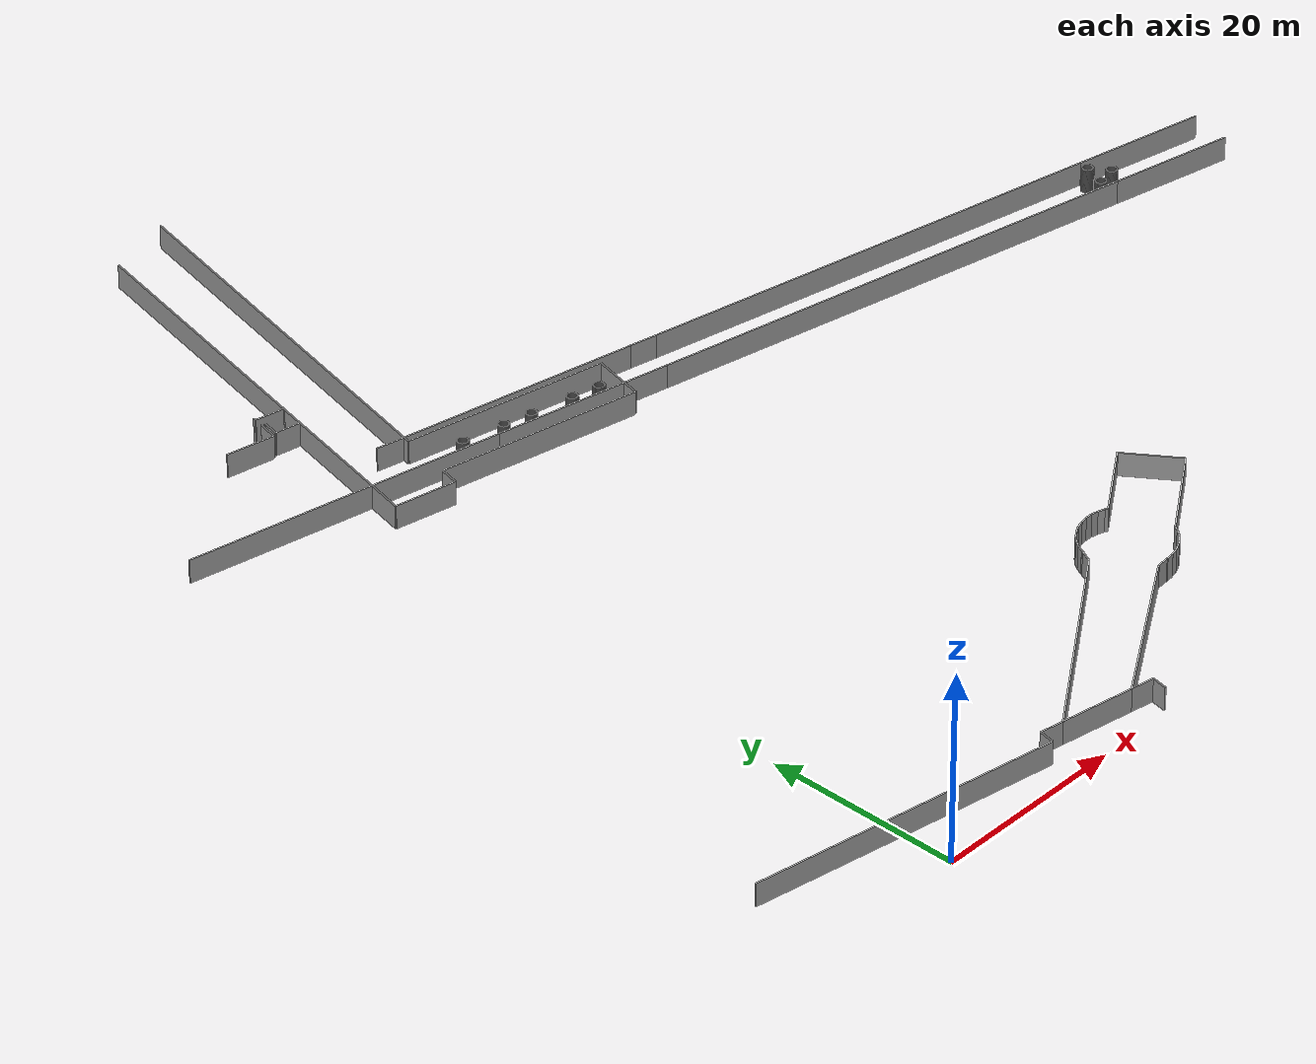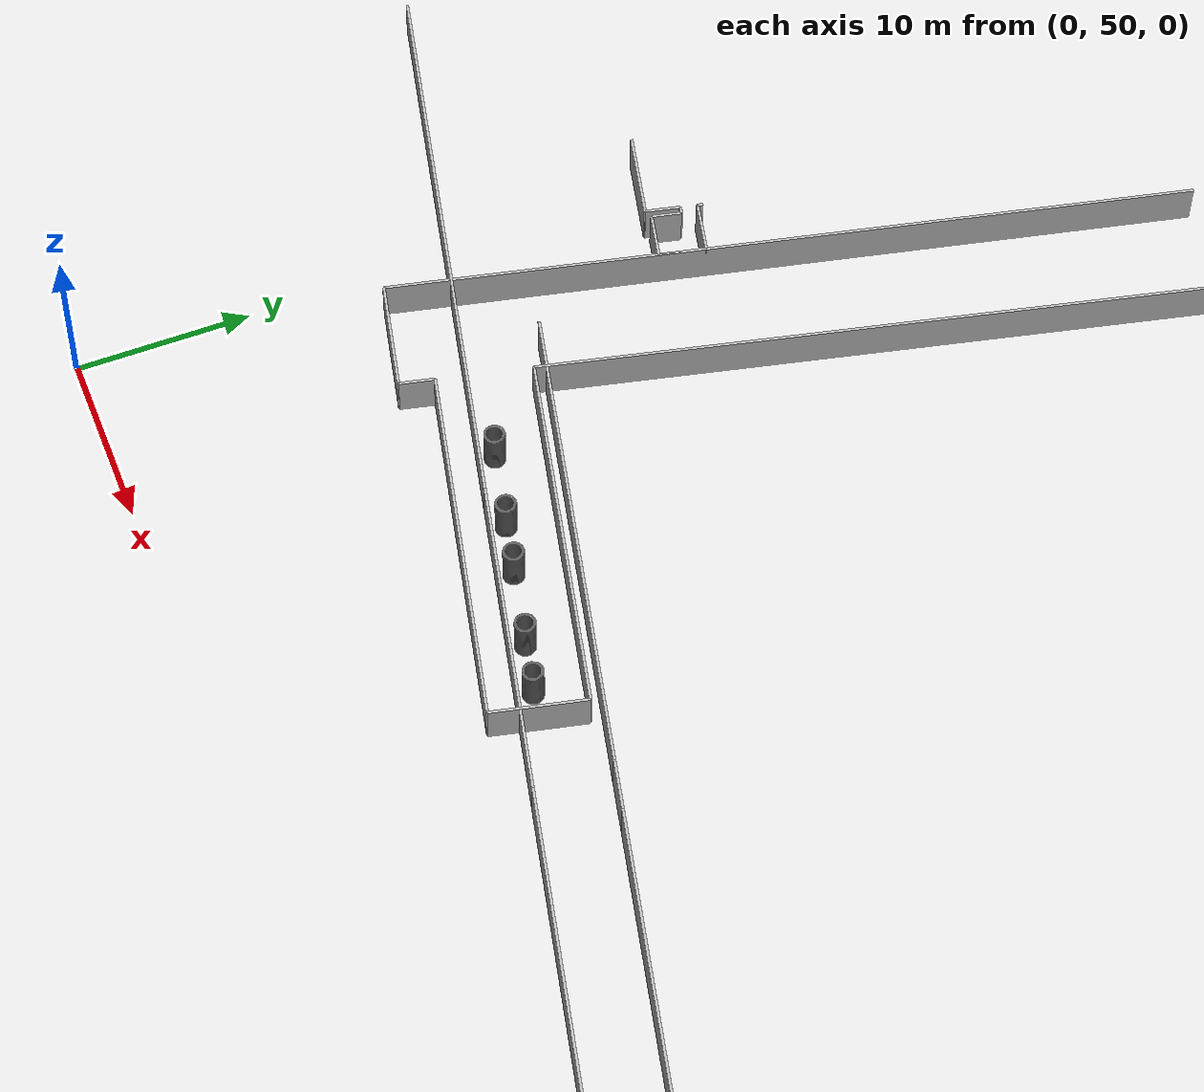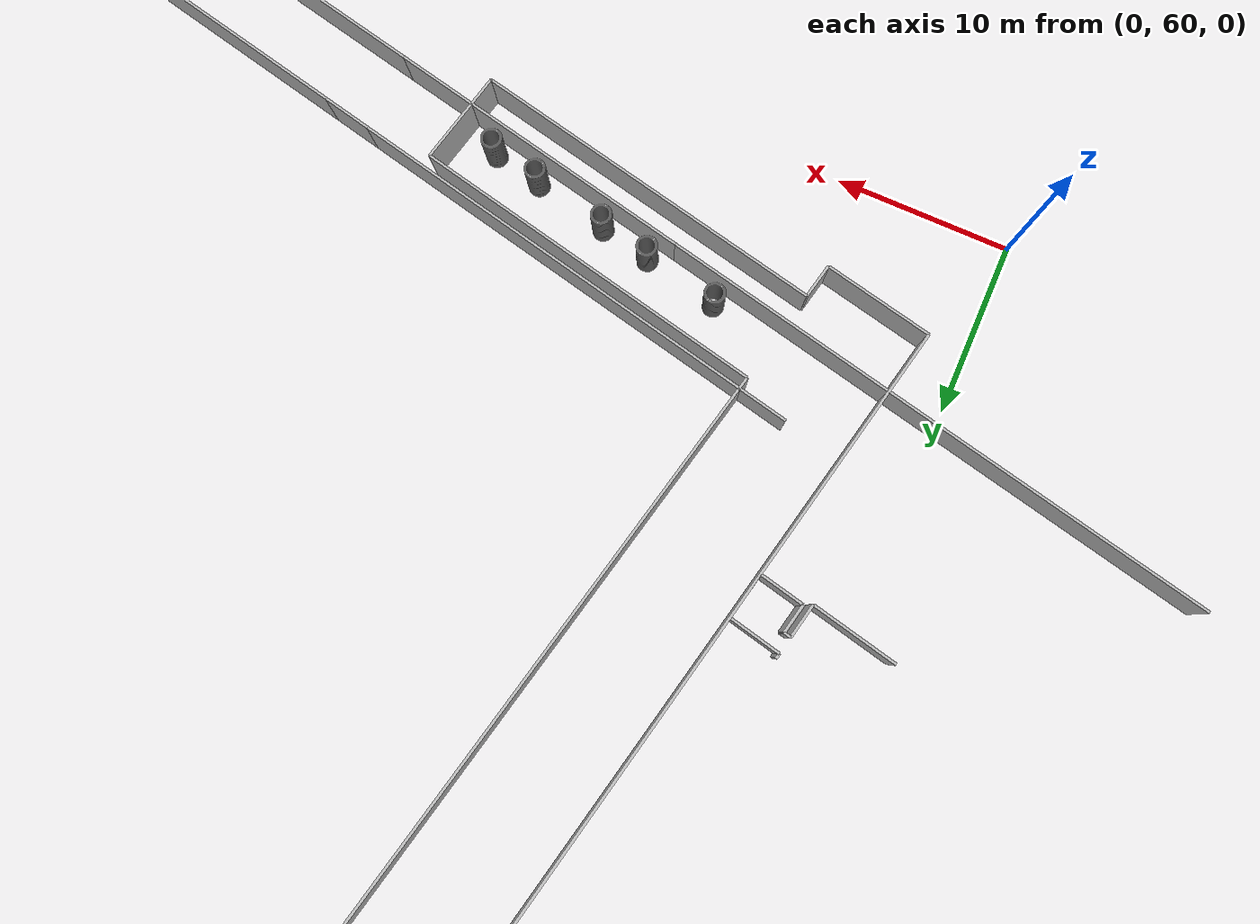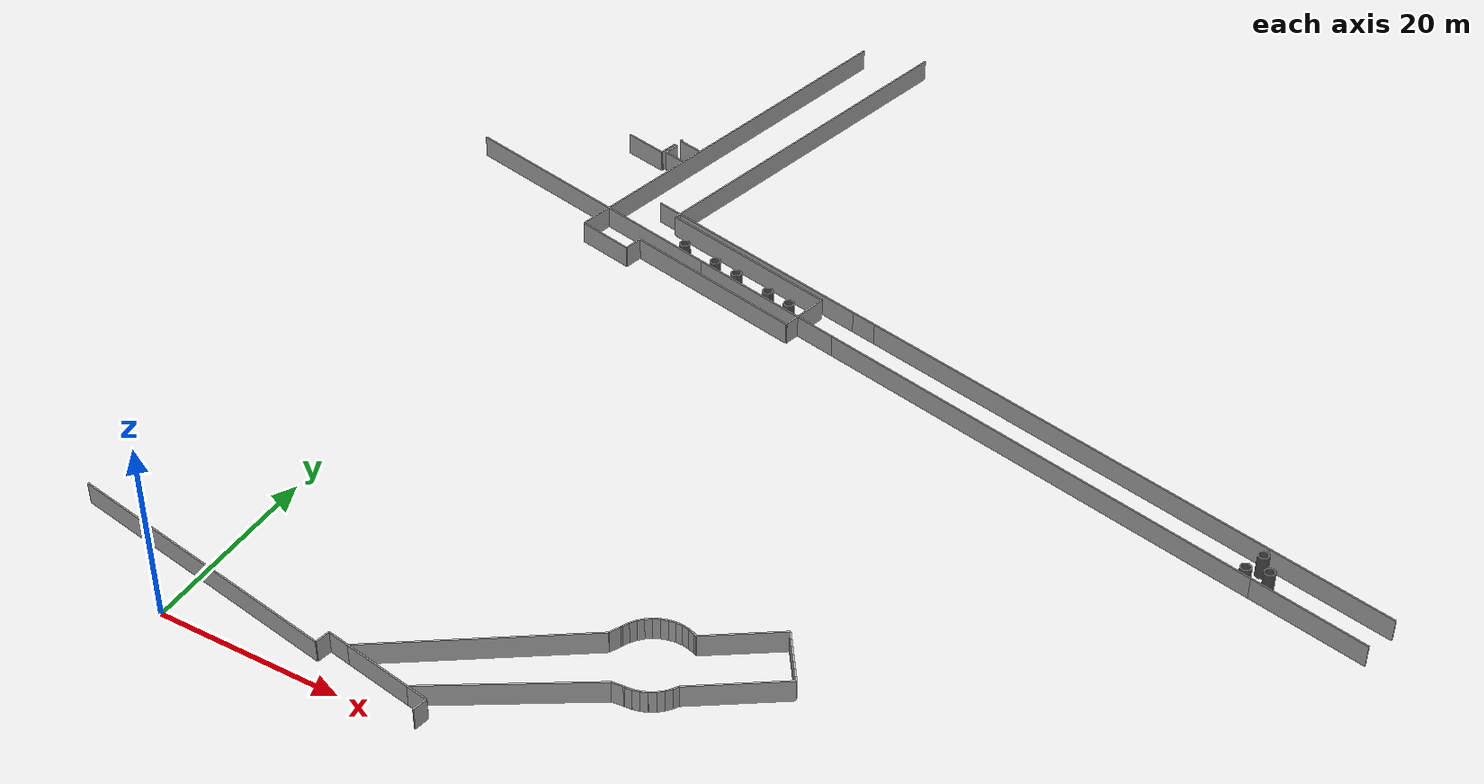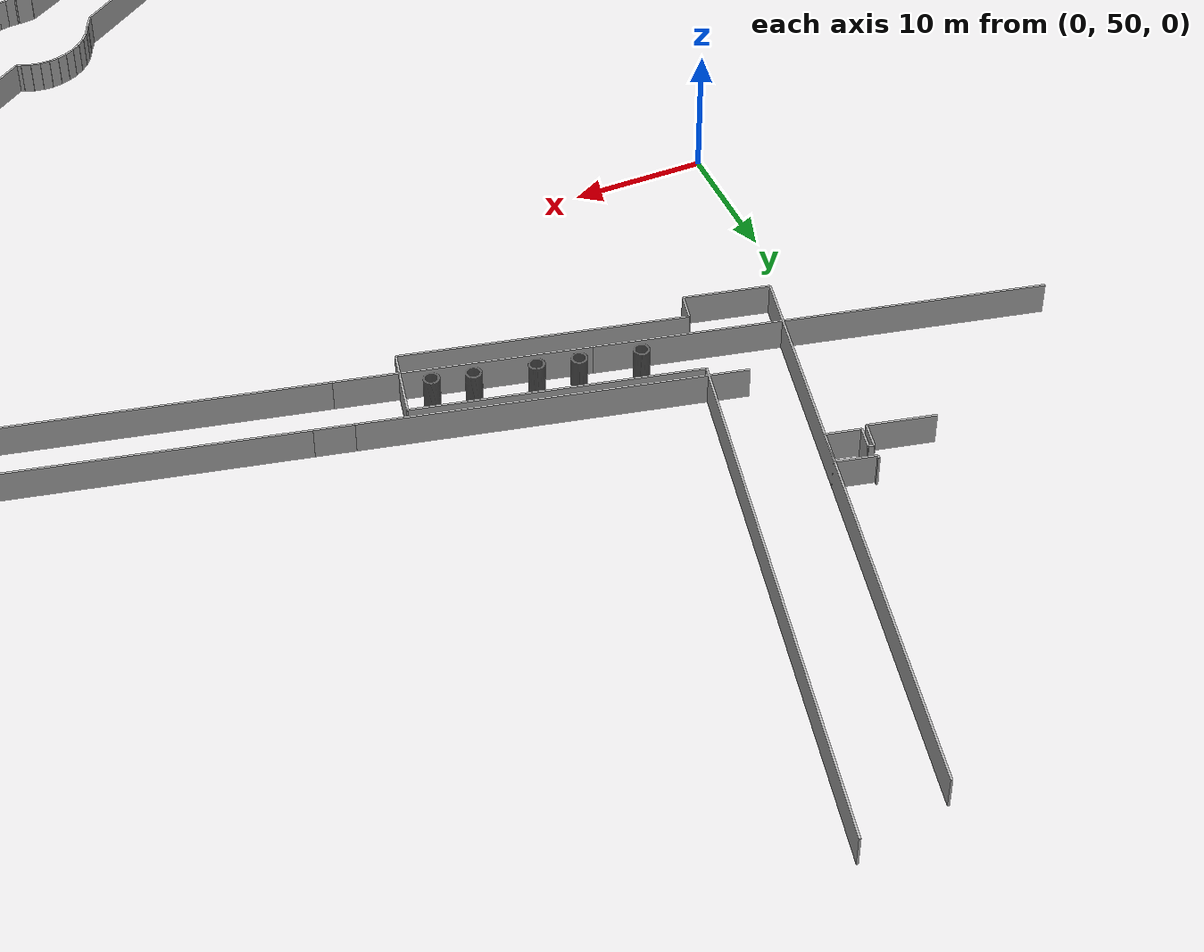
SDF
<?xml version="1.0" ?>
<sdf version="1.6">
  <model name="sps_1002">
    <pose frame="">0 0 0 0 -0 0</pose>
    <static>1</static>
    <self_collide>0</self_collide>
    <allow_auto_disable>0</allow_auto_disable>
    <link name="Wall124">
      <kinematic>0</kinematic>
      <gravity>1</gravity>
      <self_collide>0</self_collide>
      <collision name="collision">
        <geometry>
          <box>
            <size>31.9575 0.15 2.5</size>
          </box>
        </geometry>
        <pose frame="">0 0 0 0 -0 0</pose>
      </collision>
      <visual name="visual">
        <geometry>
          <box>
            <size>31.9575 0.15 2.5</size>
          </box>
        </geometry>
        <pose frame="">0 0 0 0 -0 0</pose>
        <cast_shadows>1</cast_shadows>
        <transparency>0.0</transparency>
      </visual>
      <pose frame="">0.191642 5.38922 1.25 0 0 -0.179443</pose>
    </link>
    <link name="Wall125">
      <kinematic>0</kinematic>
      <gravity>1</gravity>
      <self_collide>0</self_collide>
      <collision name="collision">
        <geometry>
          <box>
            <size>2.43988 0.15 2.5</size>
          </box>
        </geometry>
        <pose frame="">0 0 0 0 -0 0</pose>
      </collision>
      <visual name="visual">
        <geometry>
          <box>
            <size>2.43988 0.15 2.5</size>
          </box>
        </geometry>
        <pose frame="">0 0 0 0 -0 0</pose>
        <cast_shadows>1</cast_shadows>
        <transparency>0.0</transparency>
      </visual>
      <pose frame="">17.4035 3.91408 1.25 0 0 -0.179321</pose>
    </link>
    <link name="Wall292">
      <kinematic>0</kinematic>
      <gravity>1</gravity>
      <self_collide>0</self_collide>
      <collision name="collision">
        <geometry>
          <box>
            <size>1.62039 0.15 2.5</size>
          </box>
        </geometry>
        <pose frame="">0 0 0 0 -0 0</pose>
      </collision>
      <visual name="visual">
        <geometry>
          <box>
            <size>1.62039 0.15 2.5</size>
          </box>
        </geometry>
        <pose frame="">0 0 0 0 -0 0</pose>
        <cast_shadows>1</cast_shadows>
        <transparency>0.0</transparency>
      </visual>
      <pose frame="">16.0585 3.33449 1.25 0 -0 1.39133</pose>
    </link>
    <link name="Wall358">
      <kinematic>0</kinematic>
      <gravity>1</gravity>
      <self_collide>0</self_collide>
      <collision name="collision">
        <geometry>
          <box>
            <size>1.61971 0.15 2.5</size>
          </box>
        </geometry>
        <pose frame="">0 0 0 0 -0 0</pose>
      </collision>
      <visual name="visual">
        <geometry>
          <box>
            <size>1.61971 0.15 2.5</size>
          </box>
        </geometry>
        <pose frame="">0 0 0 0 -0 0</pose>
        <cast_shadows>1</cast_shadows>
        <transparency>0.0</transparency>
      </visual>
      <pose frame="">28.3579 1.10359 1.25 0 -0 1.39152</pose>
    </link>
    <link name="Wall359">
      <kinematic>0</kinematic>
      <gravity>1</gravity>
      <self_collide>0</self_collide>
      <collision name="collision">
        <geometry>
          <box>
            <size>2.44002 0.15 2.5</size>
          </box>
        </geometry>
        <pose frame="">0 0 0 0 -0 0</pose>
      </collision>
      <visual name="visual">
        <geometry>
          <box>
            <size>2.44002 0.15 2.5</size>
          </box>
        </geometry>
        <pose frame="">0 0 0 0 -0 0</pose>
        <cast_shadows>1</cast_shadows>
        <transparency>0.0</transparency>
      </visual>
      <pose frame="">27.3019 2.11827 1.25 0 -0 2.9621</pose>
    </link>
    <link name="Wall360">
      <kinematic>0</kinematic>
      <gravity>1</gravity>
      <self_collide>0</self_collide>
      <collision name="collision">
        <geometry>
          <box>
            <size>12.6978 0.15 2.5</size>
          </box>
        </geometry>
        <pose frame="">0 0 0 0 -0 0</pose>
      </collision>
      <visual name="visual">
        <geometry>
          <box>
            <size>12.6978 0.15 2.5</size>
          </box>
        </geometry>
        <pose frame="">0 0 0 0 -0 0</pose>
        <cast_shadows>1</cast_shadows>
        <transparency>0.0</transparency>
      </visual>
      <pose frame="">90.6731 51.7684 1.25 0 -0 2.9273</pose>
    </link>
    <link name="Wall361">
      <kinematic>0</kinematic>
      <gravity>1</gravity>
      <self_collide>0</self_collide>
      <collision name="collision">
        <geometry>
          <box>
            <size>51.1704 0.15 2.5</size>
          </box>
        </geometry>
        <pose frame="">0 0 0 0 -0 0</pose>
      </collision>
      <visual name="visual">
        <geometry>
          <box>
            <size>51.1704 0.15 2.5</size>
          </box>
        </geometry>
        <pose frame="">0 0 0 0 -0 0</pose>
        <cast_shadows>1</cast_shadows>
        <transparency>0.0</transparency>
      </visual>
      <pose frame="">59.4694 58.5593 1.25 0 -0 2.9273</pose>
    </link>
    <link name="Wall362">
      <kinematic>0</kinematic>
      <gravity>1</gravity>
      <self_collide>0</self_collide>
      <collision name="collision">
        <geometry>
          <box>
            <size>18.307 0.15 2.5</size>
          </box>
        </geometry>
        <pose frame="">0 0 0 0 -0 0</pose>
      </collision>
      <visual name="visual">
        <geometry>
          <box>
            <size>18.307 0.15 2.5</size>
          </box>
        </geometry>
        <pose frame="">0 0 0 0 -0 0</pose>
        <cast_shadows>1</cast_shadows>
        <transparency>0.0</transparency>
      </visual>
      <pose frame="">25.5253 65.9466 1.25 0 -0 2.9273</pose>
    </link>
    <link name="Wall363">
      <kinematic>0</kinematic>
      <gravity>1</gravity>
      <self_collide>0</self_collide>
      <collision name="collision">
        <geometry>
          <box>
            <size>32.8633 0.15 2.5</size>
          </box>
        </geometry>
        <pose frame="">0 0 0 0 -0 0</pose>
      </collision>
      <visual name="visual">
        <geometry>
          <box>
            <size>32.8633 0.15 2.5</size>
          </box>
        </geometry>
        <pose frame="">0 0 0 0 -0 0</pose>
        <cast_shadows>1</cast_shadows>
        <transparency>0.0</transparency>
      </visual>
      <pose frame="">0.525284 71.3873 1.25 0 -0 2.9273</pose>
    </link>
    <link name="Wall540">
      <kinematic>0</kinematic>
      <gravity>1</gravity>
      <self_collide>0</self_collide>
      <collision name="collision">
        <geometry>
          <box>
            <size>13.6549 0.15 2.5</size>
          </box>
        </geometry>
        <pose frame="">0 0 0 0 -0 0</pose>
      </collision>
      <visual name="visual">
        <geometry>
          <box>
            <size>13.6549 0.15 2.5</size>
          </box>
        </geometry>
        <pose frame="">0 0 0 0 -0 0</pose>
        <cast_shadows>1</cast_shadows>
        <transparency>0.0</transparency>
      </visual>
      <pose frame="">91.1407 56.1696 1.25 0 -0 2.9273</pose>
    </link>
    <link name="Wall541">
      <kinematic>0</kinematic>
      <gravity>1</gravity>
      <self_collide>0</self_collide>
      <collision name="collision">
        <geometry>
          <box>
            <size>48.3021 0.15 2.5</size>
          </box>
        </geometry>
        <pose frame="">0 0 0 0 -0 0</pose>
      </collision>
      <visual name="visual">
        <geometry>
          <box>
            <size>48.3021 0.15 2.5</size>
          </box>
        </geometry>
        <pose frame="">0 0 0 0 -0 0</pose>
        <cast_shadows>1</cast_shadows>
        <transparency>0.0</transparency>
      </visual>
      <pose frame="">60.8708 62.7573 1.25 0 -0 2.9273</pose>
    </link>
    <link name="Wall542">
      <kinematic>0</kinematic>
      <gravity>1</gravity>
      <self_collide>0</self_collide>
      <collision name="collision">
        <geometry>
          <box>
            <size>2.86829 0.15 2.5</size>
          </box>
        </geometry>
        <pose frame="">0 0 0 0 -0 0</pose>
      </collision>
      <visual name="visual">
        <geometry>
          <box>
            <size>2.86829 0.15 2.5</size>
          </box>
        </geometry>
        <pose frame="">0 0 0 0 -0 0</pose>
        <cast_shadows>1</cast_shadows>
        <transparency>0.0</transparency>
      </visual>
      <pose frame="">35.8708 68.1981 1.25 0 -0 2.9273</pose>
    </link>
    <link name="Wall543">
      <kinematic>0</kinematic>
      <gravity>1</gravity>
      <self_collide>0</self_collide>
      <collision name="collision">
        <geometry>
          <box>
            <size>27.5362 0.15 2.5</size>
          </box>
        </geometry>
        <pose frame="">0 0 0 0 -0 0</pose>
      </collision>
      <visual name="visual">
        <geometry>
          <box>
            <size>27.5362 0.15 2.5</size>
          </box>
        </geometry>
        <pose frame="">0 0 0 0 -0 0</pose>
        <cast_shadows>1</cast_shadows>
        <transparency>0.0</transparency>
      </visual>
      <pose frame="">21.0163 71.4309 1.25 0 -0 2.9273</pose>
    </link>
    <link name="Wall784">
      <kinematic>0</kinematic>
      <gravity>1</gravity>
      <self_collide>0</self_collide>
      <collision name="collision">
        <geometry>
          <box>
            <size>0.0453637 0.15 2.5</size>
          </box>
        </geometry>
        <pose frame="">0 0 0 0 -0 0</pose>
      </collision>
      <visual name="visual">
        <geometry>
          <box>
            <size>0.0453637 0.15 2.5</size>
          </box>
        </geometry>
        <pose frame="">0 0 0 0 -0 0</pose>
        <cast_shadows>1</cast_shadows>
        <transparency>0.0</transparency>
      </visual>
      <pose frame="">18.2367 69.0123 1.25 0 0 -0.653727</pose>
    </link>
    <link name="Wall785">
      <kinematic>0</kinematic>
      <gravity>1</gravity>
      <self_collide>0</self_collide>
      <collision name="collision">
        <geometry>
          <box>
            <size>0.0452735 0.15 2.5</size>
          </box>
        </geometry>
        <pose frame="">0 0 0 0 -0 0</pose>
      </collision>
      <visual name="visual">
        <geometry>
          <box>
            <size>0.0452735 0.15 2.5</size>
          </box>
        </geometry>
        <pose frame="">0 0 0 0 -0 0</pose>
        <cast_shadows>1</cast_shadows>
        <transparency>0.0</transparency>
      </visual>
      <pose frame="">18.2714 68.9832 1.25 0 0 -0.741533</pose>
    </link>
    <link name="Wall786">
      <kinematic>0</kinematic>
      <gravity>1</gravity>
      <self_collide>0</self_collide>
      <collision name="collision">
        <geometry>
          <box>
            <size>0.0454539 0.15 2.5</size>
          </box>
        </geometry>
        <pose frame="">0 0 0 0 -0 0</pose>
      </collision>
      <visual name="visual">
        <geometry>
          <box>
            <size>0.0454539 0.15 2.5</size>
          </box>
        </geometry>
        <pose frame="">0 0 0 0 -0 0</pose>
        <cast_shadows>1</cast_shadows>
        <transparency>0.0</transparency>
      </visual>
      <pose frame="">18.3033 68.9511 1.25 0 0 -0.832891</pose>
    </link>
    <link name="Wall787">
      <kinematic>0</kinematic>
      <gravity>1</gravity>
      <self_collide>0</self_collide>
      <collision name="collision">
        <geometry>
          <box>
            <size>0.0454008 0.15 2.5</size>
          </box>
        </geometry>
        <pose frame="">0 0 0 0 -0 0</pose>
      </collision>
      <visual name="visual">
        <geometry>
          <box>
            <size>0.0454008 0.15 2.5</size>
          </box>
        </geometry>
        <pose frame="">0 0 0 0 -0 0</pose>
        <cast_shadows>1</cast_shadows>
        <transparency>0.0</transparency>
      </visual>
      <pose frame="">18.3325 68.9163 1.25 0 0 -0.916002</pose>
    </link>
    <link name="Wall788">
      <kinematic>0</kinematic>
      <gravity>1</gravity>
      <self_collide>0</self_collide>
      <collision name="collision">
        <geometry>
          <box>
            <size>0.0452577 0.15 2.5</size>
          </box>
        </geometry>
        <pose frame="">0 0 0 0 -0 0</pose>
      </collision>
      <visual name="visual">
        <geometry>
          <box>
            <size>0.0452577 0.15 2.5</size>
          </box>
        </geometry>
        <pose frame="">0 0 0 0 -0 0</pose>
        <cast_shadows>1</cast_shadows>
        <transparency>0.0</transparency>
      </visual>
      <pose frame="">18.3585 68.8792 1.25 0 0 -1.00262</pose>
    </link>
    <link name="Wall789">
      <kinematic>0</kinematic>
      <gravity>1</gravity>
      <self_collide>0</self_collide>
      <collision name="collision">
        <geometry>
          <box>
            <size>0.0454007 0.15 2.5</size>
          </box>
        </geometry>
        <pose frame="">0 0 0 0 -0 0</pose>
      </collision>
      <visual name="visual">
        <geometry>
          <box>
            <size>0.0454007 0.15 2.5</size>
          </box>
        </geometry>
        <pose frame="">0 0 0 0 -0 0</pose>
        <cast_shadows>1</cast_shadows>
        <transparency>0.0</transparency>
      </visual>
      <pose frame="">18.3812 68.84 1.25 0 0 -1.08851</pose>
    </link>
    <link name="Wall790">
      <kinematic>0</kinematic>
      <gravity>1</gravity>
      <self_collide>0</self_collide>
      <collision name="collision">
        <geometry>
          <box>
            <size>0.0454525 0.15 2.5</size>
          </box>
        </geometry>
        <pose frame="">0 0 0 0 -0 0</pose>
      </collision>
      <visual name="visual">
        <geometry>
          <box>
            <size>0.0454525 0.15 2.5</size>
          </box>
        </geometry>
        <pose frame="">0 0 0 0 -0 0</pose>
        <cast_shadows>1</cast_shadows>
        <transparency>0.0</transparency>
      </visual>
      <pose frame="">18.4004 68.7989 1.25 0 0 -1.17807</pose>
    </link>
    <link name="Wall791">
      <kinematic>0</kinematic>
      <gravity>1</gravity>
      <self_collide>0</self_collide>
      <collision name="collision">
        <geometry>
          <box>
            <size>0.0452874 0.15 2.5</size>
          </box>
        </geometry>
        <pose frame="">0 0 0 0 -0 0</pose>
      </collision>
      <visual name="visual">
        <geometry>
          <box>
            <size>0.0452874 0.15 2.5</size>
          </box>
        </geometry>
        <pose frame="">0 0 0 0 -0 0</pose>
        <cast_shadows>1</cast_shadows>
        <transparency>0.0</transparency>
      </visual>
      <pose frame="">18.4159 68.7563 1.25 0 0 -1.26695</pose>
    </link>
    <link name="Wall792">
      <kinematic>0</kinematic>
      <gravity>1</gravity>
      <self_collide>0</self_collide>
      <collision name="collision">
        <geometry>
          <box>
            <size>0.0452689 0.15 2.5</size>
          </box>
        </geometry>
        <pose frame="">0 0 0 0 -0 0</pose>
      </collision>
      <visual name="visual">
        <geometry>
          <box>
            <size>0.0452689 0.15 2.5</size>
          </box>
        </geometry>
        <pose frame="">0 0 0 0 -0 0</pose>
        <cast_shadows>1</cast_shadows>
        <transparency>0.0</transparency>
      </visual>
      <pose frame="">18.4275 68.7126 1.25 0 0 -1.35198</pose>
    </link>
    <link name="Wall793">
      <kinematic>0</kinematic>
      <gravity>1</gravity>
      <self_collide>0</self_collide>
      <collision name="collision">
        <geometry>
          <box>
            <size>0.0453551 0.15 2.5</size>
          </box>
        </geometry>
        <pose frame="">0 0 0 0 -0 0</pose>
      </collision>
      <visual name="visual">
        <geometry>
          <box>
            <size>0.0453551 0.15 2.5</size>
          </box>
        </geometry>
        <pose frame="">0 0 0 0 -0 0</pose>
        <cast_shadows>1</cast_shadows>
        <transparency>0.0</transparency>
      </visual>
      <pose frame="">18.4354 68.668 1.25 0 0 -1.4426</pose>
    </link>
    <link name="Wall794">
      <kinematic>0</kinematic>
      <gravity>1</gravity>
      <self_collide>0</self_collide>
      <collision name="collision">
        <geometry>
          <box>
            <size>0.0454548 0.15 2.5</size>
          </box>
        </geometry>
        <pose frame="">0 0 0 0 -0 0</pose>
      </collision>
      <visual name="visual">
        <geometry>
          <box>
            <size>0.0454548 0.15 2.5</size>
          </box>
        </geometry>
        <pose frame="">0 0 0 0 -0 0</pose>
        <cast_shadows>1</cast_shadows>
        <transparency>0.0</transparency>
      </visual>
      <pose frame="">18.4393 68.6228 1.25 0 0 -1.52647</pose>
    </link>
    <link name="Wall795">
      <kinematic>0</kinematic>
      <gravity>1</gravity>
      <self_collide>0</self_collide>
      <collision name="collision">
        <geometry>
          <box>
            <size>0.0452719 0.15 2.5</size>
          </box>
        </geometry>
        <pose frame="">0 0 0 0 -0 0</pose>
      </collision>
      <visual name="visual">
        <geometry>
          <box>
            <size>0.0452719 0.15 2.5</size>
          </box>
        </geometry>
        <pose frame="">0 0 0 0 -0 0</pose>
        <cast_shadows>1</cast_shadows>
        <transparency>0.0</transparency>
      </visual>
      <pose frame="">18.4393 68.5775 1.25 0 0 -1.6153</pose>
    </link>
    <link name="Wall796">
      <kinematic>0</kinematic>
      <gravity>1</gravity>
      <self_collide>0</self_collide>
      <collision name="collision">
        <geometry>
          <box>
            <size>0.0453551 0.15 2.5</size>
          </box>
        </geometry>
        <pose frame="">0 0 0 0 -0 0</pose>
      </collision>
      <visual name="visual">
        <geometry>
          <box>
            <size>0.0453551 0.15 2.5</size>
          </box>
        </geometry>
        <pose frame="">0 0 0 0 -0 0</pose>
        <cast_shadows>1</cast_shadows>
        <transparency>0.0</transparency>
      </visual>
      <pose frame="">18.4354 68.5324 1.25 0 0 -1.69899</pose>
    </link>
    <link name="Wall797">
      <kinematic>0</kinematic>
      <gravity>1</gravity>
      <self_collide>0</self_collide>
      <collision name="collision">
        <geometry>
          <box>
            <size>0.0455072 0.15 2.5</size>
          </box>
        </geometry>
        <pose frame="">0 0 0 0 -0 0</pose>
      </collision>
      <visual name="visual">
        <geometry>
          <box>
            <size>0.0455072 0.15 2.5</size>
          </box>
        </geometry>
        <pose frame="">0 0 0 0 -0 0</pose>
        <cast_shadows>1</cast_shadows>
        <transparency>0.0</transparency>
      </visual>
      <pose frame="">18.4275 68.4877 1.25 0 0 -1.78845</pose>
    </link>
    <link name="Wall798">
      <kinematic>0</kinematic>
      <gravity>1</gravity>
      <self_collide>0</self_collide>
      <collision name="collision">
        <geometry>
          <box>
            <size>0.0453029 0.15 2.5</size>
          </box>
        </geometry>
        <pose frame="">0 0 0 0 -0 0</pose>
      </collision>
      <visual name="visual">
        <geometry>
          <box>
            <size>0.0453029 0.15 2.5</size>
          </box>
        </geometry>
        <pose frame="">0 0 0 0 -0 0</pose>
        <cast_shadows>1</cast_shadows>
        <transparency>0.0</transparency>
      </visual>
      <pose frame="">18.4157 68.4439 1.25 0 0 -1.88019</pose>
    </link>
    <link name="Wall799">
      <kinematic>0</kinematic>
      <gravity>1</gravity>
      <self_collide>0</self_collide>
      <collision name="collision">
        <geometry>
          <box>
            <size>0.0455089 0.15 2.5</size>
          </box>
        </geometry>
        <pose frame="">0 0 0 0 -0 0</pose>
      </collision>
      <visual name="visual">
        <geometry>
          <box>
            <size>0.0455089 0.15 2.5</size>
          </box>
        </geometry>
        <pose frame="">0 0 0 0 -0 0</pose>
        <cast_shadows>1</cast_shadows>
        <transparency>0.0</transparency>
      </visual>
      <pose frame="">18.4001 68.4013 1.25 0 0 -1.96301</pose>
    </link>
    <link name="Wall800">
      <kinematic>0</kinematic>
      <gravity>1</gravity>
      <self_collide>0</self_collide>
      <collision name="collision">
        <geometry>
          <box>
            <size>0.0453183 0.15 2.5</size>
          </box>
        </geometry>
        <pose frame="">0 0 0 0 -0 0</pose>
      </collision>
      <visual name="visual">
        <geometry>
          <box>
            <size>0.0453183 0.15 2.5</size>
          </box>
        </geometry>
        <pose frame="">0 0 0 0 -0 0</pose>
        <cast_shadows>1</cast_shadows>
        <transparency>0.0</transparency>
      </visual>
      <pose frame="">18.3809 68.3602 1.25 0 0 -2.05251</pose>
    </link>
    <link name="Wall801">
      <kinematic>0</kinematic>
      <gravity>1</gravity>
      <self_collide>0</self_collide>
      <collision name="collision">
        <geometry>
          <box>
            <size>0.045342 0.15 2.5</size>
          </box>
        </geometry>
        <pose frame="">0 0 0 0 -0 0</pose>
      </collision>
      <visual name="visual">
        <geometry>
          <box>
            <size>0.045342 0.15 2.5</size>
          </box>
        </geometry>
        <pose frame="">0 0 0 0 -0 0</pose>
        <cast_shadows>1</cast_shadows>
        <transparency>0.0</transparency>
      </visual>
      <pose frame="">18.3582 68.321 1.25 0 0 -2.13938</pose>
    </link>
    <link name="Wall802">
      <kinematic>0</kinematic>
      <gravity>1</gravity>
      <self_collide>0</self_collide>
      <collision name="collision">
        <geometry>
          <box>
            <size>0.0453637 0.15 2.5</size>
          </box>
        </geometry>
        <pose frame="">0 0 0 0 -0 0</pose>
      </collision>
      <visual name="visual">
        <geometry>
          <box>
            <size>0.0453637 0.15 2.5</size>
          </box>
        </geometry>
        <pose frame="">0 0 0 0 -0 0</pose>
        <cast_shadows>1</cast_shadows>
        <transparency>0.0</transparency>
      </visual>
      <pose frame="">18.3322 68.2839 1.25 0 0 -2.22452</pose>
    </link>
    <link name="Wall803">
      <kinematic>0</kinematic>
      <gravity>1</gravity>
      <self_collide>0</self_collide>
      <collision name="collision">
        <geometry>
          <box>
            <size>0.0452735 0.15 2.5</size>
          </box>
        </geometry>
        <pose frame="">0 0 0 0 -0 0</pose>
      </collision>
      <visual name="visual">
        <geometry>
          <box>
            <size>0.0452735 0.15 2.5</size>
          </box>
        </geometry>
        <pose frame="">0 0 0 0 -0 0</pose>
        <cast_shadows>1</cast_shadows>
        <transparency>0.0</transparency>
      </visual>
      <pose frame="">18.3032 68.2492 1.25 0 0 -2.31233</pose>
    </link>
    <link name="Wall804">
      <kinematic>0</kinematic>
      <gravity>1</gravity>
      <self_collide>0</self_collide>
      <collision name="collision">
        <geometry>
          <box>
            <size>0.0454388 0.15 2.5</size>
          </box>
        </geometry>
        <pose frame="">0 0 0 0 -0 0</pose>
      </collision>
      <visual name="visual">
        <geometry>
          <box>
            <size>0.0454388 0.15 2.5</size>
          </box>
        </geometry>
        <pose frame="">0 0 0 0 -0 0</pose>
        <cast_shadows>1</cast_shadows>
        <transparency>0.0</transparency>
      </visual>
      <pose frame="">18.2712 68.2171 1.25 0 0 -2.3961</pose>
    </link>
    <link name="Wall805">
      <kinematic>0</kinematic>
      <gravity>1</gravity>
      <self_collide>0</self_collide>
      <collision name="collision">
        <geometry>
          <box>
            <size>0.0452526 0.15 2.5</size>
          </box>
        </geometry>
        <pose frame="">0 0 0 0 -0 0</pose>
      </collision>
      <visual name="visual">
        <geometry>
          <box>
            <size>0.0452526 0.15 2.5</size>
          </box>
        </geometry>
        <pose frame="">0 0 0 0 -0 0</pose>
        <cast_shadows>1</cast_shadows>
        <transparency>0.0</transparency>
      </visual>
      <pose frame="">18.2365 68.188 1.25 0 0 -2.49108</pose>
    </link>
    <link name="Wall806">
      <kinematic>0</kinematic>
      <gravity>1</gravity>
      <self_collide>0</self_collide>
      <collision name="collision">
        <geometry>
          <box>
            <size>0.0453092 0.15 2.5</size>
          </box>
        </geometry>
        <pose frame="">0 0 0 0 -0 0</pose>
      </collision>
      <visual name="visual">
        <geometry>
          <box>
            <size>0.0453092 0.15 2.5</size>
          </box>
        </geometry>
        <pose frame="">0 0 0 0 -0 0</pose>
        <cast_shadows>1</cast_shadows>
        <transparency>0.0</transparency>
      </visual>
      <pose frame="">18.1994 68.1621 1.25 0 0 -2.57414</pose>
    </link>
    <link name="Wall807">
      <kinematic>0</kinematic>
      <gravity>1</gravity>
      <self_collide>0</self_collide>
      <collision name="collision">
        <geometry>
          <box>
            <size>0.0455348 0.15 2.5</size>
          </box>
        </geometry>
        <pose frame="">0 0 0 0 -0 0</pose>
      </collision>
      <visual name="visual">
        <geometry>
          <box>
            <size>0.0455348 0.15 2.5</size>
          </box>
        </geometry>
        <pose frame="">0 0 0 0 -0 0</pose>
        <cast_shadows>1</cast_shadows>
        <transparency>0.0</transparency>
      </visual>
      <pose frame="">18.1601 68.1394 1.25 0 0 -2.66236</pose>
    </link>
    <link name="Wall808">
      <kinematic>0</kinematic>
      <gravity>1</gravity>
      <self_collide>0</self_collide>
      <collision name="collision">
        <geometry>
          <box>
            <size>0.0453069 0.15 2.5</size>
          </box>
        </geometry>
        <pose frame="">0 0 0 0 -0 0</pose>
      </collision>
      <visual name="visual">
        <geometry>
          <box>
            <size>0.0453069 0.15 2.5</size>
          </box>
        </geometry>
        <pose frame="">0 0 0 0 -0 0</pose>
        <cast_shadows>1</cast_shadows>
        <transparency>0.0</transparency>
      </visual>
      <pose frame="">18.1189 68.1202 1.25 0 0 -2.74608</pose>
    </link>
    <link name="Wall809">
      <kinematic>0</kinematic>
      <gravity>1</gravity>
      <self_collide>0</self_collide>
      <collision name="collision">
        <geometry>
          <box>
            <size>0.0452874 0.15 2.5</size>
          </box>
        </geometry>
        <pose frame="">0 0 0 0 -0 0</pose>
      </collision>
      <visual name="visual">
        <geometry>
          <box>
            <size>0.0452874 0.15 2.5</size>
          </box>
        </geometry>
        <pose frame="">0 0 0 0 -0 0</pose>
        <cast_shadows>1</cast_shadows>
        <transparency>0.0</transparency>
      </visual>
      <pose frame="">18.0764 68.1047 1.25 0 0 -2.83774</pose>
    </link>
    <link name="Wall810">
      <kinematic>0</kinematic>
      <gravity>1</gravity>
      <self_collide>0</self_collide>
      <collision name="collision">
        <geometry>
          <box>
            <size>0.0454476 0.15 2.5</size>
          </box>
        </geometry>
        <pose frame="">0 0 0 0 -0 0</pose>
      </collision>
      <visual name="visual">
        <geometry>
          <box>
            <size>0.0454476 0.15 2.5</size>
          </box>
        </geometry>
        <pose frame="">0 0 0 0 -0 0</pose>
        <cast_shadows>1</cast_shadows>
        <transparency>0.0</transparency>
      </visual>
      <pose frame="">18.0326 68.093 1.25 0 0 -2.92365</pose>
    </link>
    <link name="Wall811">
      <kinematic>0</kinematic>
      <gravity>1</gravity>
      <self_collide>0</self_collide>
      <collision name="collision">
        <geometry>
          <box>
            <size>0.0453551 0.15 2.5</size>
          </box>
        </geometry>
        <pose frame="">0 0 0 0 -0 0</pose>
      </collision>
      <visual name="visual">
        <geometry>
          <box>
            <size>0.0453551 0.15 2.5</size>
          </box>
        </geometry>
        <pose frame="">0 0 0 0 -0 0</pose>
        <cast_shadows>1</cast_shadows>
        <transparency>0.0</transparency>
      </visual>
      <pose frame="">17.988 68.0852 1.25 0 0 -3.0134</pose>
    </link>
    <link name="Wall812">
      <kinematic>0</kinematic>
      <gravity>1</gravity>
      <self_collide>0</self_collide>
      <collision name="collision">
        <geometry>
          <box>
            <size>0.0454548 0.15 2.5</size>
          </box>
        </geometry>
        <pose frame="">0 0 0 0 -0 0</pose>
      </collision>
      <visual name="visual">
        <geometry>
          <box>
            <size>0.0454548 0.15 2.5</size>
          </box>
        </geometry>
        <pose frame="">0 0 0 0 -0 0</pose>
        <cast_shadows>1</cast_shadows>
        <transparency>0.0</transparency>
      </visual>
      <pose frame="">17.9428 68.0813 1.25 0 0 -3.09727</pose>
    </link>
    <link name="Wall813">
      <kinematic>0</kinematic>
      <gravity>1</gravity>
      <self_collide>0</self_collide>
      <collision name="collision">
        <geometry>
          <box>
            <size>0.0452719 0.15 2.5</size>
          </box>
        </geometry>
        <pose frame="">0 0 0 0 -0 0</pose>
      </collision>
      <visual name="visual">
        <geometry>
          <box>
            <size>0.0452719 0.15 2.5</size>
          </box>
        </geometry>
        <pose frame="">0 0 0 0 -0 0</pose>
        <cast_shadows>1</cast_shadows>
        <transparency>0.0</transparency>
      </visual>
      <pose frame="">17.8975 68.0813 1.25 0 -0 3.09709</pose>
    </link>
    <link name="Wall814">
      <kinematic>0</kinematic>
      <gravity>1</gravity>
      <self_collide>0</self_collide>
      <collision name="collision">
        <geometry>
          <box>
            <size>0.0453788 0.15 2.5</size>
          </box>
        </geometry>
        <pose frame="">0 0 0 0 -0 0</pose>
      </collision>
      <visual name="visual">
        <geometry>
          <box>
            <size>0.0453788 0.15 2.5</size>
          </box>
        </geometry>
        <pose frame="">0 0 0 0 -0 0</pose>
        <cast_shadows>1</cast_shadows>
        <transparency>0.0</transparency>
      </visual>
      <pose frame="">17.8523 68.0853 1.25 0 -0 3.0094</pose>
    </link>
    <link name="Wall815">
      <kinematic>0</kinematic>
      <gravity>1</gravity>
      <self_collide>0</self_collide>
      <collision name="collision">
        <geometry>
          <box>
            <size>0.0454476 0.15 2.5</size>
          </box>
        </geometry>
        <pose frame="">0 0 0 0 -0 0</pose>
      </collision>
      <visual name="visual">
        <geometry>
          <box>
            <size>0.0454476 0.15 2.5</size>
          </box>
        </geometry>
        <pose frame="">0 0 0 0 -0 0</pose>
        <cast_shadows>1</cast_shadows>
        <transparency>0.0</transparency>
      </visual>
      <pose frame="">17.8077 68.0932 1.25 0 -0 2.92365</pose>
    </link>
    <link name="Wall816">
      <kinematic>0</kinematic>
      <gravity>1</gravity>
      <self_collide>0</self_collide>
      <collision name="collision">
        <geometry>
          <box>
            <size>0.0453057 0.15 2.5</size>
          </box>
        </geometry>
        <pose frame="">0 0 0 0 -0 0</pose>
      </collision>
      <visual name="visual">
        <geometry>
          <box>
            <size>0.0453057 0.15 2.5</size>
          </box>
        </geometry>
        <pose frame="">0 0 0 0 -0 0</pose>
        <cast_shadows>1</cast_shadows>
        <transparency>0.0</transparency>
      </visual>
      <pose frame="">17.7639 68.1049 1.25 0 -0 2.83646</pose>
    </link>
    <link name="Wall817">
      <kinematic>0</kinematic>
      <gravity>1</gravity>
      <self_collide>0</self_collide>
      <collision name="collision">
        <geometry>
          <box>
            <size>0.0452834 0.15 2.5</size>
          </box>
        </geometry>
        <pose frame="">0 0 0 0 -0 0</pose>
      </collision>
      <visual name="visual">
        <geometry>
          <box>
            <size>0.0452834 0.15 2.5</size>
          </box>
        </geometry>
        <pose frame="">0 0 0 0 -0 0</pose>
        <cast_shadows>1</cast_shadows>
        <transparency>0.0</transparency>
      </visual>
      <pose frame="">17.7214 68.1204 1.25 0 -0 2.74732</pose>
    </link>
    <link name="Wall818">
      <kinematic>0</kinematic>
      <gravity>1</gravity>
      <self_collide>0</self_collide>
      <collision name="collision">
        <geometry>
          <box>
            <size>0.045288 0.15 2.5</size>
          </box>
        </geometry>
        <pose frame="">0 0 0 0 -0 0</pose>
      </collision>
      <visual name="visual">
        <geometry>
          <box>
            <size>0.045288 0.15 2.5</size>
          </box>
        </geometry>
        <pose frame="">0 0 0 0 -0 0</pose>
        <cast_shadows>1</cast_shadows>
        <transparency>0.0</transparency>
      </visual>
      <pose frame="">17.6804 68.1395 1.25 0 -0 2.66408</pose>
    </link>
    <link name="Wall819">
      <kinematic>0</kinematic>
      <gravity>1</gravity>
      <self_collide>0</self_collide>
      <collision name="collision">
        <geometry>
          <box>
            <size>0.0454637 0.15 2.5</size>
          </box>
        </geometry>
        <pose frame="">0 0 0 0 -0 0</pose>
      </collision>
      <visual name="visual">
        <geometry>
          <box>
            <size>0.0454637 0.15 2.5</size>
          </box>
        </geometry>
        <pose frame="">0 0 0 0 -0 0</pose>
        <cast_shadows>1</cast_shadows>
        <transparency>0.0</transparency>
      </visual>
      <pose frame="">17.641 68.1621 1.25 0 -0 2.5763</pose>
    </link>
    <link name="Wall820">
      <kinematic>0</kinematic>
      <gravity>1</gravity>
      <self_collide>0</self_collide>
      <collision name="collision">
        <geometry>
          <box>
            <size>0.0455126 0.15 2.5</size>
          </box>
        </geometry>
        <pose frame="">0 0 0 0 -0 0</pose>
      </collision>
      <visual name="visual">
        <geometry>
          <box>
            <size>0.0455126 0.15 2.5</size>
          </box>
        </geometry>
        <pose frame="">0 0 0 0 -0 0</pose>
        <cast_shadows>1</cast_shadows>
        <transparency>0.0</transparency>
      </visual>
      <pose frame="">17.6038 68.1882 1.25 0 -0 2.48361</pose>
    </link>
    <link name="Wall821">
      <kinematic>0</kinematic>
      <gravity>1</gravity>
      <self_collide>0</self_collide>
      <collision name="collision">
        <geometry>
          <box>
            <size>0.0452735 0.15 2.5</size>
          </box>
        </geometry>
        <pose frame="">0 0 0 0 -0 0</pose>
      </collision>
      <visual name="visual">
        <geometry>
          <box>
            <size>0.0452735 0.15 2.5</size>
          </box>
        </geometry>
        <pose frame="">0 0 0 0 -0 0</pose>
        <cast_shadows>1</cast_shadows>
        <transparency>0.0</transparency>
      </visual>
      <pose frame="">17.5691 68.2174 1.25 0 -0 2.40006</pose>
    </link>
    <link name="Wall822">
      <kinematic>0</kinematic>
      <gravity>1</gravity>
      <self_collide>0</self_collide>
      <collision name="collision">
        <geometry>
          <box>
            <size>0.0452735 0.15 2.5</size>
          </box>
        </geometry>
        <pose frame="">0 0 0 0 -0 0</pose>
      </collision>
      <visual name="visual">
        <geometry>
          <box>
            <size>0.0452735 0.15 2.5</size>
          </box>
        </geometry>
        <pose frame="">0 0 0 0 -0 0</pose>
        <cast_shadows>1</cast_shadows>
        <transparency>0.0</transparency>
      </visual>
      <pose frame="">17.5372 68.2494 1.25 0 -0 2.31233</pose>
    </link>
    <link name="Wall823">
      <kinematic>0</kinematic>
      <gravity>1</gravity>
      <self_collide>0</self_collide>
      <collision name="collision">
        <geometry>
          <box>
            <size>0.0453637 0.15 2.5</size>
          </box>
        </geometry>
        <pose frame="">0 0 0 0 -0 0</pose>
      </collision>
      <visual name="visual">
        <geometry>
          <box>
            <size>0.0453637 0.15 2.5</size>
          </box>
        </geometry>
        <pose frame="">0 0 0 0 -0 0</pose>
        <cast_shadows>1</cast_shadows>
        <transparency>0.0</transparency>
      </visual>
      <pose frame="">17.5081 68.2841 1.25 0 -0 2.22452</pose>
    </link>
    <link name="Wall824">
      <kinematic>0</kinematic>
      <gravity>1</gravity>
      <self_collide>0</self_collide>
      <collision name="collision">
        <geometry>
          <box>
            <size>0.0454964 0.15 2.5</size>
          </box>
        </geometry>
        <pose frame="">0 0 0 0 -0 0</pose>
      </collision>
      <visual name="visual">
        <geometry>
          <box>
            <size>0.0454964 0.15 2.5</size>
          </box>
        </geometry>
        <pose frame="">0 0 0 0 -0 0</pose>
        <cast_shadows>1</cast_shadows>
        <transparency>0.0</transparency>
      </visual>
      <pose frame="">17.4821 68.3213 1.25 0 -0 2.13722</pose>
    </link>
    <link name="Wall825">
      <kinematic>0</kinematic>
      <gravity>1</gravity>
      <self_collide>0</self_collide>
      <collision name="collision">
        <geometry>
          <box>
            <size>0.0453724 0.15 2.5</size>
          </box>
        </geometry>
        <pose frame="">0 0 0 0 -0 0</pose>
      </collision>
      <visual name="visual">
        <geometry>
          <box>
            <size>0.0453724 0.15 2.5</size>
          </box>
        </geometry>
        <pose frame="">0 0 0 0 -0 0</pose>
        <cast_shadows>1</cast_shadows>
        <transparency>0.0</transparency>
      </visual>
      <pose frame="">17.4594 68.3606 1.25 0 -0 2.05189</pose>
    </link>
    <link name="Wall826">
      <kinematic>0</kinematic>
      <gravity>1</gravity>
      <self_collide>0</self_collide>
      <collision name="collision">
        <geometry>
          <box>
            <size>0.0452134 0.15 2.5</size>
          </box>
        </geometry>
        <pose frame="">0 0 0 0 -0 0</pose>
      </collision>
      <visual name="visual">
        <geometry>
          <box>
            <size>0.0452134 0.15 2.5</size>
          </box>
        </geometry>
        <pose frame="">0 0 0 0 -0 0</pose>
        <cast_shadows>1</cast_shadows>
        <transparency>0.0</transparency>
      </visual>
      <pose frame="">17.4403 68.4016 1.25 0 -0 1.96133</pose>
    </link>
    <link name="Wall827">
      <kinematic>0</kinematic>
      <gravity>1</gravity>
      <self_collide>0</self_collide>
      <collision name="collision">
        <geometry>
          <box>
            <size>0.0454804 0.15 2.5</size>
          </box>
        </geometry>
        <pose frame="">0 0 0 0 -0 0</pose>
      </collision>
      <visual name="visual">
        <geometry>
          <box>
            <size>0.0454804 0.15 2.5</size>
          </box>
        </geometry>
        <pose frame="">0 0 0 0 -0 0</pose>
        <cast_shadows>1</cast_shadows>
        <transparency>0.0</transparency>
      </visual>
      <pose frame="">17.4249 68.4442 1.25 0 -0 1.87472</pose>
    </link>
    <link name="Wall828">
      <kinematic>0</kinematic>
      <gravity>1</gravity>
      <self_collide>0</self_collide>
      <collision name="collision">
        <geometry>
          <box>
            <size>0.045309 0.15 2.5</size>
          </box>
        </geometry>
        <pose frame="">0 0 0 0 -0 0</pose>
      </collision>
      <visual name="visual">
        <geometry>
          <box>
            <size>0.045309 0.15 2.5</size>
          </box>
        </geometry>
        <pose frame="">0 0 0 0 -0 0</pose>
        <cast_shadows>1</cast_shadows>
        <transparency>0.0</transparency>
      </visual>
      <pose frame="">17.413 68.488 1.25 0 -0 1.79356</pose>
    </link>
    <link name="Wall829">
      <kinematic>0</kinematic>
      <gravity>1</gravity>
      <self_collide>0</self_collide>
      <collision name="collision">
        <geometry>
          <box>
            <size>0.0453551 0.15 2.5</size>
          </box>
        </geometry>
        <pose frame="">0 0 0 0 -0 0</pose>
      </collision>
      <visual name="visual">
        <geometry>
          <box>
            <size>0.0453551 0.15 2.5</size>
          </box>
        </geometry>
        <pose frame="">0 0 0 0 -0 0</pose>
        <cast_shadows>1</cast_shadows>
        <transparency>0.0</transparency>
      </visual>
      <pose frame="">17.4051 68.5326 1.25 0 -0 1.69899</pose>
    </link>
    <link name="Wall830">
      <kinematic>0</kinematic>
      <gravity>1</gravity>
      <self_collide>0</self_collide>
      <collision name="collision">
        <geometry>
          <box>
            <size>0.0454548 0.15 2.5</size>
          </box>
        </geometry>
        <pose frame="">0 0 0 0 -0 0</pose>
      </collision>
      <visual name="visual">
        <geometry>
          <box>
            <size>0.0454548 0.15 2.5</size>
          </box>
        </geometry>
        <pose frame="">0 0 0 0 -0 0</pose>
        <cast_shadows>1</cast_shadows>
        <transparency>0.0</transparency>
      </visual>
      <pose frame="">17.4012 68.5778 1.25 0 -0 1.61512</pose>
    </link>
    <link name="Wall831">
      <kinematic>0</kinematic>
      <gravity>1</gravity>
      <self_collide>0</self_collide>
      <collision name="collision">
        <geometry>
          <box>
            <size>0.0452719 0.15 2.5</size>
          </box>
        </geometry>
        <pose frame="">0 0 0 0 -0 0</pose>
      </collision>
      <visual name="visual">
        <geometry>
          <box>
            <size>0.0452719 0.15 2.5</size>
          </box>
        </geometry>
        <pose frame="">0 0 0 0 -0 0</pose>
        <cast_shadows>1</cast_shadows>
        <transparency>0.0</transparency>
      </visual>
      <pose frame="">17.4012 68.6231 1.25 0 -0 1.52629</pose>
    </link>
    <link name="Wall832">
      <kinematic>0</kinematic>
      <gravity>1</gravity>
      <self_collide>0</self_collide>
      <collision name="collision">
        <geometry>
          <box>
            <size>0.0453788 0.15 2.5</size>
          </box>
        </geometry>
        <pose frame="">0 0 0 0 -0 0</pose>
      </collision>
      <visual name="visual">
        <geometry>
          <box>
            <size>0.0453788 0.15 2.5</size>
          </box>
        </geometry>
        <pose frame="">0 0 0 0 -0 0</pose>
        <cast_shadows>1</cast_shadows>
        <transparency>0.0</transparency>
      </visual>
      <pose frame="">17.4052 68.6682 1.25 0 -0 1.4386</pose>
    </link>
    <link name="Wall833">
      <kinematic>0</kinematic>
      <gravity>1</gravity>
      <self_collide>0</self_collide>
      <collision name="collision">
        <geometry>
          <box>
            <size>0.0452689 0.15 2.5</size>
          </box>
        </geometry>
        <pose frame="">0 0 0 0 -0 0</pose>
      </collision>
      <visual name="visual">
        <geometry>
          <box>
            <size>0.0452689 0.15 2.5</size>
          </box>
        </geometry>
        <pose frame="">0 0 0 0 -0 0</pose>
        <cast_shadows>1</cast_shadows>
        <transparency>0.0</transparency>
      </visual>
      <pose frame="">17.4131 68.7128 1.25 0 -0 1.35198</pose>
    </link>
    <link name="Wall834">
      <kinematic>0</kinematic>
      <gravity>1</gravity>
      <self_collide>0</self_collide>
      <collision name="collision">
        <geometry>
          <box>
            <size>0.0454804 0.15 2.5</size>
          </box>
        </geometry>
        <pose frame="">0 0 0 0 -0 0</pose>
      </collision>
      <visual name="visual">
        <geometry>
          <box>
            <size>0.0454804 0.15 2.5</size>
          </box>
        </geometry>
        <pose frame="">0 0 0 0 -0 0</pose>
        <cast_shadows>1</cast_shadows>
        <transparency>0.0</transparency>
      </visual>
      <pose frame="">17.4249 68.7566 1.25 0 -0 1.26687</pose>
    </link>
    <link name="Wall835">
      <kinematic>0</kinematic>
      <gravity>1</gravity>
      <self_collide>0</self_collide>
      <collision name="collision">
        <geometry>
          <box>
            <size>0.0452834 0.15 2.5</size>
          </box>
        </geometry>
        <pose frame="">0 0 0 0 -0 0</pose>
      </collision>
      <visual name="visual">
        <geometry>
          <box>
            <size>0.0452834 0.15 2.5</size>
          </box>
        </geometry>
        <pose frame="">0 0 0 0 -0 0</pose>
        <cast_shadows>1</cast_shadows>
        <transparency>0.0</transparency>
      </visual>
      <pose frame="">17.4404 68.7992 1.25 0 -0 1.17652</pose>
    </link>
    <link name="Wall836">
      <kinematic>0</kinematic>
      <gravity>1</gravity>
      <self_collide>0</self_collide>
      <collision name="collision">
        <geometry>
          <box>
            <size>0.0455348 0.15 2.5</size>
          </box>
        </geometry>
        <pose frame="">0 0 0 0 -0 0</pose>
      </collision>
      <visual name="visual">
        <geometry>
          <box>
            <size>0.0455348 0.15 2.5</size>
          </box>
        </geometry>
        <pose frame="">0 0 0 0 -0 0</pose>
        <cast_shadows>1</cast_shadows>
        <transparency>0.0</transparency>
      </visual>
      <pose frame="">17.4596 68.8403 1.25 0 -0 1.09156</pose>
    </link>
    <link name="Wall837">
      <kinematic>0</kinematic>
      <gravity>1</gravity>
      <self_collide>0</self_collide>
      <collision name="collision">
        <geometry>
          <box>
            <size>0.045342 0.15 2.5</size>
          </box>
        </geometry>
        <pose frame="">0 0 0 0 -0 0</pose>
      </collision>
      <visual name="visual">
        <geometry>
          <box>
            <size>0.045342 0.15 2.5</size>
          </box>
        </geometry>
        <pose frame="">0 0 0 0 -0 0</pose>
        <cast_shadows>1</cast_shadows>
        <transparency>0.0</transparency>
      </visual>
      <pose frame="">17.4823 68.8796 1.25 0 -0 1.00221</pose>
    </link>
    <link name="Wall838">
      <kinematic>0</kinematic>
      <gravity>1</gravity>
      <self_collide>0</self_collide>
      <collision name="collision">
        <geometry>
          <box>
            <size>0.0453637 0.15 2.5</size>
          </box>
        </geometry>
        <pose frame="">0 0 0 0 -0 0</pose>
      </collision>
      <visual name="visual">
        <geometry>
          <box>
            <size>0.0453637 0.15 2.5</size>
          </box>
        </geometry>
        <pose frame="">0 0 0 0 -0 0</pose>
        <cast_shadows>1</cast_shadows>
        <transparency>0.0</transparency>
      </visual>
      <pose frame="">17.5083 68.9167 1.25 0 -0 0.91707</pose>
    </link>
    <link name="Wall839">
      <kinematic>0</kinematic>
      <gravity>1</gravity>
      <self_collide>0</self_collide>
      <collision name="collision">
        <geometry>
          <box>
            <size>0.0452735 0.15 2.5</size>
          </box>
        </geometry>
        <pose frame="">0 0 0 0 -0 0</pose>
      </collision>
      <visual name="visual">
        <geometry>
          <box>
            <size>0.0452735 0.15 2.5</size>
          </box>
        </geometry>
        <pose frame="">0 0 0 0 -0 0</pose>
        <cast_shadows>1</cast_shadows>
        <transparency>0.0</transparency>
      </visual>
      <pose frame="">17.5373 68.9514 1.25 0 -0 0.829263</pose>
    </link>
    <link name="Wall840">
      <kinematic>0</kinematic>
      <gravity>1</gravity>
      <self_collide>0</self_collide>
      <collision name="collision">
        <geometry>
          <box>
            <size>0.0453186 0.15 2.5</size>
          </box>
        </geometry>
        <pose frame="">0 0 0 0 -0 0</pose>
      </collision>
      <visual name="visual">
        <geometry>
          <box>
            <size>0.0453186 0.15 2.5</size>
          </box>
        </geometry>
        <pose frame="">0 0 0 0 -0 0</pose>
        <cast_shadows>1</cast_shadows>
        <transparency>0.0</transparency>
      </visual>
      <pose frame="">17.5694 68.9834 1.25 0 -0 0.740624</pose>
    </link>
    <link name="Wall841">
      <kinematic>0</kinematic>
      <gravity>1</gravity>
      <self_collide>0</self_collide>
      <collision name="collision">
        <geometry>
          <box>
            <size>0.0453524 0.15 2.5</size>
          </box>
        </geometry>
        <pose frame="">0 0 0 0 -0 0</pose>
      </collision>
      <visual name="visual">
        <geometry>
          <box>
            <size>0.0453524 0.15 2.5</size>
          </box>
        </geometry>
        <pose frame="">0 0 0 0 -0 0</pose>
        <cast_shadows>1</cast_shadows>
        <transparency>0.0</transparency>
      </visual>
      <pose frame="">17.6041 69.0125 1.25 0 -0 0.655614</pose>
    </link>
    <link name="Wall842">
      <kinematic>0</kinematic>
      <gravity>1</gravity>
      <self_collide>0</self_collide>
      <collision name="collision">
        <geometry>
          <box>
            <size>0.0455152 0.15 2.5</size>
          </box>
        </geometry>
        <pose frame="">0 0 0 0 -0 0</pose>
      </collision>
      <visual name="visual">
        <geometry>
          <box>
            <size>0.0455152 0.15 2.5</size>
          </box>
        </geometry>
        <pose frame="">0 0 0 0 -0 0</pose>
        <cast_shadows>1</cast_shadows>
        <transparency>0.0</transparency>
      </visual>
      <pose frame="">17.6413 69.0385 1.25 0 -0 0.564569</pose>
    </link>
    <link name="Wall843">
      <kinematic>0</kinematic>
      <gravity>1</gravity>
      <self_collide>0</self_collide>
      <collision name="collision">
        <geometry>
          <box>
            <size>0.0453183 0.15 2.5</size>
          </box>
        </geometry>
        <pose frame="">0 0 0 0 -0 0</pose>
      </collision>
      <visual name="visual">
        <geometry>
          <box>
            <size>0.0453183 0.15 2.5</size>
          </box>
        </geometry>
        <pose frame="">0 0 0 0 -0 0</pose>
        <cast_shadows>1</cast_shadows>
        <transparency>0.0</transparency>
      </visual>
      <pose frame="">17.6806 69.0612 1.25 0 -0 0.481718</pose>
    </link>
    <link name="Wall844">
      <kinematic>0</kinematic>
      <gravity>1</gravity>
      <self_collide>0</self_collide>
      <collision name="collision">
        <geometry>
          <box>
            <size>0.0453827 0.15 2.5</size>
          </box>
        </geometry>
        <pose frame="">0 0 0 0 -0 0</pose>
      </collision>
      <visual name="visual">
        <geometry>
          <box>
            <size>0.0453827 0.15 2.5</size>
          </box>
        </geometry>
        <pose frame="">0 0 0 0 -0 0</pose>
        <cast_shadows>1</cast_shadows>
        <transparency>0.0</transparency>
      </visual>
      <pose frame="">17.7216 69.0803 1.25 0 -0 0.388998</pose>
    </link>
    <link name="Wall845">
      <kinematic>0</kinematic>
      <gravity>1</gravity>
      <self_collide>0</self_collide>
      <collision name="collision">
        <geometry>
          <box>
            <size>0.0453611 0.15 2.5</size>
          </box>
        </geometry>
        <pose frame="">0 0 0 0 -0 0</pose>
      </collision>
      <visual name="visual">
        <geometry>
          <box>
            <size>0.0453611 0.15 2.5</size>
          </box>
        </geometry>
        <pose frame="">0 0 0 0 -0 0</pose>
        <cast_shadows>1</cast_shadows>
        <transparency>0.0</transparency>
      </visual>
      <pose frame="">17.7642 69.0958 1.25 0 -0 0.308985</pose>
    </link>
    <link name="Wall846">
      <kinematic>0</kinematic>
      <gravity>1</gravity>
      <self_collide>0</self_collide>
      <collision name="collision">
        <geometry>
          <box>
            <size>0.0452295 0.15 2.5</size>
          </box>
        </geometry>
        <pose frame="">0 0 0 0 -0 0</pose>
      </collision>
      <visual name="visual">
        <geometry>
          <box>
            <size>0.0452295 0.15 2.5</size>
          </box>
        </geometry>
        <pose frame="">0 0 0 0 -0 0</pose>
        <cast_shadows>1</cast_shadows>
        <transparency>0.0</transparency>
      </visual>
      <pose frame="">17.8079 69.1075 1.25 0 -0 0.214863</pose>
    </link>
    <link name="Wall847">
      <kinematic>0</kinematic>
      <gravity>1</gravity>
      <self_collide>0</self_collide>
      <collision name="collision">
        <geometry>
          <box>
            <size>0.0454394 0.15 2.5</size>
          </box>
        </geometry>
        <pose frame="">0 0 0 0 -0 0</pose>
      </collision>
      <visual name="visual">
        <geometry>
          <box>
            <size>0.0454394 0.15 2.5</size>
          </box>
        </geometry>
        <pose frame="">0 0 0 0 -0 0</pose>
        <cast_shadows>1</cast_shadows>
        <transparency>0.0</transparency>
      </visual>
      <pose frame="">17.8526 69.1153 1.25 0 -0 0.132019</pose>
    </link>
    <link name="Wall848">
      <kinematic>0</kinematic>
      <gravity>1</gravity>
      <self_collide>0</self_collide>
      <collision name="collision">
        <geometry>
          <box>
            <size>0.0453938 0.15 2.5</size>
          </box>
        </geometry>
        <pose frame="">0 0 0 0 -0 0</pose>
      </collision>
      <visual name="visual">
        <geometry>
          <box>
            <size>0.0453938 0.15 2.5</size>
          </box>
        </geometry>
        <pose frame="">0 0 0 0 -0 0</pose>
        <cast_shadows>1</cast_shadows>
        <transparency>0.0</transparency>
      </visual>
      <pose frame="">17.8978 69.1193 1.25 0 -0 0.0443854</pose>
    </link>
    <link name="Wall849">
      <kinematic>0</kinematic>
      <gravity>1</gravity>
      <self_collide>0</self_collide>
      <collision name="collision">
        <geometry>
          <box>
            <size>0.0454548 0.15 2.5</size>
          </box>
        </geometry>
        <pose frame="">0 0 0 0 -0 0</pose>
      </collision>
      <visual name="visual">
        <geometry>
          <box>
            <size>0.0454548 0.15 2.5</size>
          </box>
        </geometry>
        <pose frame="">0 0 0 0 -0 0</pose>
        <cast_shadows>1</cast_shadows>
        <transparency>0.0</transparency>
      </visual>
      <pose frame="">17.9431 69.1193 1.25 0 0 -0.0443258</pose>
    </link>
    <link name="Wall850">
      <kinematic>0</kinematic>
      <gravity>1</gravity>
      <self_collide>0</self_collide>
      <collision name="collision">
        <geometry>
          <box>
            <size>0.0451973 0.15 2.5</size>
          </box>
        </geometry>
        <pose frame="">0 0 0 0 -0 0</pose>
      </collision>
      <visual name="visual">
        <geometry>
          <box>
            <size>0.0451973 0.15 2.5</size>
          </box>
        </geometry>
        <pose frame="">0 0 0 0 -0 0</pose>
        <cast_shadows>1</cast_shadows>
        <transparency>0.0</transparency>
      </visual>
      <pose frame="">17.9882 69.1153 1.25 0 0 -0.13273</pose>
    </link>
    <link name="Wall851">
      <kinematic>0</kinematic>
      <gravity>1</gravity>
      <self_collide>0</self_collide>
      <collision name="collision">
        <geometry>
          <box>
            <size>0.0455072 0.15 2.5</size>
          </box>
        </geometry>
        <pose frame="">0 0 0 0 -0 0</pose>
      </collision>
      <visual name="visual">
        <geometry>
          <box>
            <size>0.0455072 0.15 2.5</size>
          </box>
        </geometry>
        <pose frame="">0 0 0 0 -0 0</pose>
        <cast_shadows>1</cast_shadows>
        <transparency>0.0</transparency>
      </visual>
      <pose frame="">18.0329 69.1074 1.25 0 0 -0.217651</pose>
    </link>
    <link name="Wall852">
      <kinematic>0</kinematic>
      <gravity>1</gravity>
      <self_collide>0</self_collide>
      <collision name="collision">
        <geometry>
          <box>
            <size>0.0452475 0.15 2.5</size>
          </box>
        </geometry>
        <pose frame="">0 0 0 0 -0 0</pose>
      </collision>
      <visual name="visual">
        <geometry>
          <box>
            <size>0.0452475 0.15 2.5</size>
          </box>
        </geometry>
        <pose frame="">0 0 0 0 -0 0</pose>
        <cast_shadows>1</cast_shadows>
        <transparency>0.0</transparency>
      </visual>
      <pose frame="">18.0767 69.0957 1.25 0 0 -0.30554</pose>
    </link>
    <link name="Wall853">
      <kinematic>0</kinematic>
      <gravity>1</gravity>
      <self_collide>0</self_collide>
      <collision name="collision">
        <geometry>
          <box>
            <size>0.0455089 0.15 2.5</size>
          </box>
        </geometry>
        <pose frame="">0 0 0 0 -0 0</pose>
      </collision>
      <visual name="visual">
        <geometry>
          <box>
            <size>0.0455089 0.15 2.5</size>
          </box>
        </geometry>
        <pose frame="">0 0 0 0 -0 0</pose>
        <cast_shadows>1</cast_shadows>
        <transparency>0.0</transparency>
      </visual>
      <pose frame="">18.1193 69.0802 1.25 0 0 -0.392212</pose>
    </link>
    <link name="Wall854">
      <kinematic>0</kinematic>
      <gravity>1</gravity>
      <self_collide>0</self_collide>
      <collision name="collision">
        <geometry>
          <box>
            <size>0.0453183 0.15 2.5</size>
          </box>
        </geometry>
        <pose frame="">0 0 0 0 -0 0</pose>
      </collision>
      <visual name="visual">
        <geometry>
          <box>
            <size>0.0453183 0.15 2.5</size>
          </box>
        </geometry>
        <pose frame="">0 0 0 0 -0 0</pose>
        <cast_shadows>1</cast_shadows>
        <transparency>0.0</transparency>
      </visual>
      <pose frame="">18.1604 69.061 1.25 0 0 -0.481718</pose>
    </link>
    <link name="Wall855">
      <kinematic>0</kinematic>
      <gravity>1</gravity>
      <self_collide>0</self_collide>
      <collision name="collision">
        <geometry>
          <box>
            <size>0.045342 0.15 2.5</size>
          </box>
        </geometry>
        <pose frame="">0 0 0 0 -0 0</pose>
      </collision>
      <visual name="visual">
        <geometry>
          <box>
            <size>0.045342 0.15 2.5</size>
          </box>
        </geometry>
        <pose frame="">0 0 0 0 -0 0</pose>
        <cast_shadows>1</cast_shadows>
        <transparency>0.0</transparency>
      </visual>
      <pose frame="">18.1995 69.0383 1.25 0 0 -0.568588</pose>
    </link>
    <link name="Wall856">
      <kinematic>0</kinematic>
      <gravity>1</gravity>
      <self_collide>0</self_collide>
      <collision name="collision">
        <geometry>
          <box>
            <size>41.2539 0.15 2.5</size>
          </box>
        </geometry>
        <pose frame="">0 0 0 0 -0 0</pose>
      </collision>
      <visual name="visual">
        <geometry>
          <box>
            <size>41.2539 0.15 2.5</size>
          </box>
        </geometry>
        <pose frame="">0 0 0 0 -0 0</pose>
        <cast_shadows>1</cast_shadows>
        <transparency>0.0</transparency>
      </visual>
      <pose frame="">14.7564 93.1931 1.25 0 0 -1.79038</pose>
    </link>
    <link name="Wall857">
      <kinematic>0</kinematic>
      <gravity>1</gravity>
      <self_collide>0</self_collide>
      <collision name="collision">
        <geometry>
          <box>
            <size>20.9005 0.15 2.5</size>
          </box>
        </geometry>
        <pose frame="">0 0 0 0 -0 0</pose>
      </collision>
      <visual name="visual">
        <geometry>
          <box>
            <size>20.9005 0.15 2.5</size>
          </box>
        </geometry>
        <pose frame="">0 0 0 0 -0 0</pose>
        <cast_shadows>1</cast_shadows>
        <transparency>0.0</transparency>
      </visual>
      <pose frame="">20.4746 70.8395 1.25 0 0 -0.21426</pose>
    </link>
    <link name="Wall858">
      <kinematic>0</kinematic>
      <gravity>1</gravity>
      <self_collide>0</self_collide>
      <collision name="collision">
        <geometry>
          <box>
            <size>5.43507 0.15 2.5</size>
          </box>
        </geometry>
        <pose frame="">0 0 0 0 -0 0</pose>
      </collision>
      <visual name="visual">
        <geometry>
          <box>
            <size>5.43507 0.15 2.5</size>
          </box>
        </geometry>
        <pose frame="">0 0 0 0 -0 0</pose>
        <cast_shadows>1</cast_shadows>
        <transparency>0.0</transparency>
      </visual>
      <pose frame="">30.1081 65.9621 1.25 0 0 -1.78506</pose>
    </link>
    <link name="Wall859">
      <kinematic>0</kinematic>
      <gravity>1</gravity>
      <self_collide>0</self_collide>
      <collision name="collision">
        <geometry>
          <box>
            <size>20.9005 0.15 2.5</size>
          </box>
        </geometry>
        <pose frame="">0 0 0 0 -0 0</pose>
      </collision>
      <visual name="visual">
        <geometry>
          <box>
            <size>20.9005 0.15 2.5</size>
          </box>
        </geometry>
        <pose frame="">0 0 0 0 -0 0</pose>
        <cast_shadows>1</cast_shadows>
        <transparency>0.0</transparency>
      </visual>
      <pose frame="">19.3189 65.5287 1.25 0 -0 2.92733</pose>
    </link>
    <link name="Wall860">
      <kinematic>0</kinematic>
      <gravity>1</gravity>
      <self_collide>0</self_collide>
      <collision name="collision">
        <geometry>
          <box>
            <size>2.01459 0.15 2.5</size>
          </box>
        </geometry>
        <pose frame="">0 0 0 0 -0 0</pose>
      </collision>
      <visual name="visual">
        <geometry>
          <box>
            <size>2.01459 0.15 2.5</size>
          </box>
        </geometry>
        <pose frame="">0 0 0 0 -0 0</pose>
        <cast_shadows>1</cast_shadows>
        <transparency>0.0</transparency>
      </visual>
      <pose frame="">8.89355 66.7664 1.25 0 0 -1.78496</pose>
    </link>
    <link name="Wall861">
      <kinematic>0</kinematic>
      <gravity>1</gravity>
      <self_collide>0</self_collide>
      <collision name="collision">
        <geometry>
          <box>
            <size>6.36004 0.15 2.5</size>
          </box>
        </geometry>
        <pose frame="">0 0 0 0 -0 0</pose>
      </collision>
      <visual name="visual">
        <geometry>
          <box>
            <size>6.36004 0.15 2.5</size>
          </box>
        </geometry>
        <pose frame="">0 0 0 0 -0 0</pose>
        <cast_shadows>1</cast_shadows>
        <transparency>0.0</transparency>
      </visual>
      <pose frame="">5.57217 66.4583 1.25 0 -0 2.92732</pose>
    </link>
    <link name="Wall862">
      <kinematic>0</kinematic>
      <gravity>1</gravity>
      <self_collide>0</self_collide>
      <collision name="collision">
        <geometry>
          <box>
            <size>45.5327 0.15 2.5</size>
          </box>
        </geometry>
        <pose frame="">0 0 0 0 -0 0</pose>
      </collision>
      <visual name="visual">
        <geometry>
          <box>
            <size>45.5327 0.15 2.5</size>
          </box>
        </geometry>
        <pose frame="">0 0 0 0 -0 0</pose>
        <cast_shadows>1</cast_shadows>
        <transparency>0.0</transparency>
      </visual>
      <pose frame="">7.30526 89.3803 1.25 0 -0 1.35655</pose>
    </link>
    <link name="Wall913">
      <kinematic>0</kinematic>
      <gravity>1</gravity>
      <self_collide>0</self_collide>
      <collision name="collision">
        <geometry>
          <box>
            <size>0.0453637 0.15 2.5</size>
          </box>
        </geometry>
        <pose frame="">0 0 0 0 -0 0</pose>
      </collision>
      <visual name="visual">
        <geometry>
          <box>
            <size>0.0453637 0.15 2.5</size>
          </box>
        </geometry>
        <pose frame="">0 0 0 0 -0 0</pose>
        <cast_shadows>1</cast_shadows>
        <transparency>0.0</transparency>
      </visual>
      <pose frame="">85.9802 55.1557 1.25 0 0 -0.653727</pose>
    </link>
    <link name="Wall914">
      <kinematic>0</kinematic>
      <gravity>1</gravity>
      <self_collide>0</self_collide>
      <collision name="collision">
        <geometry>
          <box>
            <size>0.0453148 0.15 2.5</size>
          </box>
        </geometry>
        <pose frame="">0 0 0 0 -0 0</pose>
      </collision>
      <visual name="visual">
        <geometry>
          <box>
            <size>0.0453148 0.15 2.5</size>
          </box>
        </geometry>
        <pose frame="">0 0 0 0 -0 0</pose>
        <cast_shadows>1</cast_shadows>
        <transparency>0.0</transparency>
      </visual>
      <pose frame="">86.0149 55.1266 1.25 0 0 -0.742526</pose>
    </link>
    <link name="Wall915">
      <kinematic>0</kinematic>
      <gravity>1</gravity>
      <self_collide>0</self_collide>
      <collision name="collision">
        <geometry>
          <box>
            <size>0.0454498 0.15 2.5</size>
          </box>
        </geometry>
        <pose frame="">0 0 0 0 -0 0</pose>
      </collision>
      <visual name="visual">
        <geometry>
          <box>
            <size>0.0454498 0.15 2.5</size>
          </box>
        </geometry>
        <pose frame="">0 0 0 0 -0 0</pose>
        <cast_shadows>1</cast_shadows>
        <transparency>0.0</transparency>
      </visual>
      <pose frame="">86.047 55.0945 1.25 0 0 -0.830994</pose>
    </link>
    <link name="Wall916">
      <kinematic>0</kinematic>
      <gravity>1</gravity>
      <self_collide>0</self_collide>
      <collision name="collision">
        <geometry>
          <box>
            <size>0.0453637 0.15 2.5</size>
          </box>
        </geometry>
        <pose frame="">0 0 0 0 -0 0</pose>
      </collision>
      <visual name="visual">
        <geometry>
          <box>
            <size>0.0453637 0.15 2.5</size>
          </box>
        </geometry>
        <pose frame="">0 0 0 0 -0 0</pose>
        <cast_shadows>1</cast_shadows>
        <transparency>0.0</transparency>
      </visual>
      <pose frame="">86.0761 55.0597 1.25 0 0 -0.91707</pose>
    </link>
    <link name="Wall917">
      <kinematic>0</kinematic>
      <gravity>1</gravity>
      <self_collide>0</self_collide>
      <collision name="collision">
        <geometry>
          <box>
            <size>0.045342 0.15 2.5</size>
          </box>
        </geometry>
        <pose frame="">0 0 0 0 -0 0</pose>
      </collision>
      <visual name="visual">
        <geometry>
          <box>
            <size>0.045342 0.15 2.5</size>
          </box>
        </geometry>
        <pose frame="">0 0 0 0 -0 0</pose>
        <cast_shadows>1</cast_shadows>
        <transparency>0.0</transparency>
      </visual>
      <pose frame="">86.1021 55.0226 1.25 0 0 -1.00221</pose>
    </link>
    <link name="Wall918">
      <kinematic>0</kinematic>
      <gravity>1</gravity>
      <self_collide>0</self_collide>
      <collision name="collision">
        <geometry>
          <box>
            <size>0.0453724 0.15 2.5</size>
          </box>
        </geometry>
        <pose frame="">0 0 0 0 -0 0</pose>
      </collision>
      <visual name="visual">
        <geometry>
          <box>
            <size>0.0453724 0.15 2.5</size>
          </box>
        </geometry>
        <pose frame="">0 0 0 0 -0 0</pose>
        <cast_shadows>1</cast_shadows>
        <transparency>0.0</transparency>
      </visual>
      <pose frame="">86.1248 54.9834 1.25 0 0 -1.0897</pose>
    </link>
    <link name="Wall919">
      <kinematic>0</kinematic>
      <gravity>1</gravity>
      <self_collide>0</self_collide>
      <collision name="collision">
        <geometry>
          <box>
            <size>0.0454525 0.15 2.5</size>
          </box>
        </geometry>
        <pose frame="">0 0 0 0 -0 0</pose>
      </collision>
      <visual name="visual">
        <geometry>
          <box>
            <size>0.0454525 0.15 2.5</size>
          </box>
        </geometry>
        <pose frame="">0 0 0 0 -0 0</pose>
        <cast_shadows>1</cast_shadows>
        <transparency>0.0</transparency>
      </visual>
      <pose frame="">86.144 54.9423 1.25 0 0 -1.17807</pose>
    </link>
    <link name="Wall920">
      <kinematic>0</kinematic>
      <gravity>1</gravity>
      <self_collide>0</self_collide>
      <collision name="collision">
        <geometry>
          <box>
            <size>0.0453057 0.15 2.5</size>
          </box>
        </geometry>
        <pose frame="">0 0 0 0 -0 0</pose>
      </collision>
      <visual name="visual">
        <geometry>
          <box>
            <size>0.0453057 0.15 2.5</size>
          </box>
        </geometry>
        <pose frame="">0 0 0 0 -0 0</pose>
        <cast_shadows>1</cast_shadows>
        <transparency>0.0</transparency>
      </visual>
      <pose frame="">86.1595 54.8997 1.25 0 0 -1.26566</pose>
    </link>
    <link name="Wall921">
      <kinematic>0</kinematic>
      <gravity>1</gravity>
      <self_collide>0</self_collide>
      <collision name="collision">
        <geometry>
          <box>
            <size>0.0452557 0.15 2.5</size>
          </box>
        </geometry>
        <pose frame="">0 0 0 0 -0 0</pose>
      </collision>
      <visual name="visual">
        <geometry>
          <box>
            <size>0.0452557 0.15 2.5</size>
          </box>
        </geometry>
        <pose frame="">0 0 0 0 -0 0</pose>
        <cast_shadows>1</cast_shadows>
        <transparency>0.0</transparency>
      </visual>
      <pose frame="">86.1712 54.856 1.25 0 0 -1.3533</pose>
    </link>
    <link name="Wall922">
      <kinematic>0</kinematic>
      <gravity>1</gravity>
      <self_collide>0</self_collide>
      <collision name="collision">
        <geometry>
          <box>
            <size>0.0453551 0.15 2.5</size>
          </box>
        </geometry>
        <pose frame="">0 0 0 0 -0 0</pose>
      </collision>
      <visual name="visual">
        <geometry>
          <box>
            <size>0.0453551 0.15 2.5</size>
          </box>
        </geometry>
        <pose frame="">0 0 0 0 -0 0</pose>
        <cast_shadows>1</cast_shadows>
        <transparency>0.0</transparency>
      </visual>
      <pose frame="">86.1789 54.8114 1.25 0 0 -1.4426</pose>
    </link>
    <link name="Wall923">
      <kinematic>0</kinematic>
      <gravity>1</gravity>
      <self_collide>0</self_collide>
      <collision name="collision">
        <geometry>
          <box>
            <size>0.0454548 0.15 2.5</size>
          </box>
        </geometry>
        <pose frame="">0 0 0 0 -0 0</pose>
      </collision>
      <visual name="visual">
        <geometry>
          <box>
            <size>0.0454548 0.15 2.5</size>
          </box>
        </geometry>
        <pose frame="">0 0 0 0 -0 0</pose>
        <cast_shadows>1</cast_shadows>
        <transparency>0.0</transparency>
      </visual>
      <pose frame="">86.1829 54.7662 1.25 0 0 -1.52647</pose>
    </link>
    <link name="Wall924">
      <kinematic>0</kinematic>
      <gravity>1</gravity>
      <self_collide>0</self_collide>
      <collision name="collision">
        <geometry>
          <box>
            <size>0.0454548 0.15 2.5</size>
          </box>
        </geometry>
        <pose frame="">0 0 0 0 -0 0</pose>
      </collision>
      <visual name="visual">
        <geometry>
          <box>
            <size>0.0454548 0.15 2.5</size>
          </box>
        </geometry>
        <pose frame="">0 0 0 0 -0 0</pose>
        <cast_shadows>1</cast_shadows>
        <transparency>0.0</transparency>
      </visual>
      <pose frame="">86.1829 54.7208 1.25 0 0 -1.61512</pose>
    </link>
    <link name="Wall925">
      <kinematic>0</kinematic>
      <gravity>1</gravity>
      <self_collide>0</self_collide>
      <collision name="collision">
        <geometry>
          <box>
            <size>0.0451735 0.15 2.5</size>
          </box>
        </geometry>
        <pose frame="">0 0 0 0 -0 0</pose>
      </collision>
      <visual name="visual">
        <geometry>
          <box>
            <size>0.0451735 0.15 2.5</size>
          </box>
        </geometry>
        <pose frame="">0 0 0 0 -0 0</pose>
        <cast_shadows>1</cast_shadows>
        <transparency>0.0</transparency>
      </visual>
      <pose frame="">86.1789 54.6757 1.25 0 0 -1.69951</pose>
    </link>
    <link name="Wall926">
      <kinematic>0</kinematic>
      <gravity>1</gravity>
      <self_collide>0</self_collide>
      <collision name="collision">
        <geometry>
          <box>
            <size>0.0454876 0.15 2.5</size>
          </box>
        </geometry>
        <pose frame="">0 0 0 0 -0 0</pose>
      </collision>
      <visual name="visual">
        <geometry>
          <box>
            <size>0.0454876 0.15 2.5</size>
          </box>
        </geometry>
        <pose frame="">0 0 0 0 -0 0</pose>
        <cast_shadows>1</cast_shadows>
        <transparency>0.0</transparency>
      </visual>
      <pose frame="">86.171 54.6311 1.25 0 0 -1.79267</pose>
    </link>
    <link name="Wall927">
      <kinematic>0</kinematic>
      <gravity>1</gravity>
      <self_collide>0</self_collide>
      <collision name="collision">
        <geometry>
          <box>
            <size>0.0453057 0.15 2.5</size>
          </box>
        </geometry>
        <pose frame="">0 0 0 0 -0 0</pose>
      </collision>
      <visual name="visual">
        <geometry>
          <box>
            <size>0.0453057 0.15 2.5</size>
          </box>
        </geometry>
        <pose frame="">0 0 0 0 -0 0</pose>
        <cast_shadows>1</cast_shadows>
        <transparency>0.0</transparency>
      </visual>
      <pose frame="">86.1592 54.5873 1.25 0 0 -1.87593</pose>
    </link>
    <link name="Wall928">
      <kinematic>0</kinematic>
      <gravity>1</gravity>
      <self_collide>0</self_collide>
      <collision name="collision">
        <geometry>
          <box>
            <size>0.0454525 0.15 2.5</size>
          </box>
        </geometry>
        <pose frame="">0 0 0 0 -0 0</pose>
      </collision>
      <visual name="visual">
        <geometry>
          <box>
            <size>0.0454525 0.15 2.5</size>
          </box>
        </geometry>
        <pose frame="">0 0 0 0 -0 0</pose>
        <cast_shadows>1</cast_shadows>
        <transparency>0.0</transparency>
      </visual>
      <pose frame="">86.1437 54.5447 1.25 0 0 -1.96352</pose>
    </link>
    <link name="Wall929">
      <kinematic>0</kinematic>
      <gravity>1</gravity>
      <self_collide>0</self_collide>
      <collision name="collision">
        <geometry>
          <box>
            <size>0.0453724 0.15 2.5</size>
          </box>
        </geometry>
        <pose frame="">0 0 0 0 -0 0</pose>
      </collision>
      <visual name="visual">
        <geometry>
          <box>
            <size>0.0453724 0.15 2.5</size>
          </box>
        </geometry>
        <pose frame="">0 0 0 0 -0 0</pose>
        <cast_shadows>1</cast_shadows>
        <transparency>0.0</transparency>
      </visual>
      <pose frame="">86.1245 54.5036 1.25 0 0 -2.05189</pose>
    </link>
    <link name="Wall930">
      <kinematic>0</kinematic>
      <gravity>1</gravity>
      <self_collide>0</self_collide>
      <collision name="collision">
        <geometry>
          <box>
            <size>0.0453092 0.15 2.5</size>
          </box>
        </geometry>
        <pose frame="">0 0 0 0 -0 0</pose>
      </collision>
      <visual name="visual">
        <geometry>
          <box>
            <size>0.0453092 0.15 2.5</size>
          </box>
        </geometry>
        <pose frame="">0 0 0 0 -0 0</pose>
        <cast_shadows>1</cast_shadows>
        <transparency>0.0</transparency>
      </visual>
      <pose frame="">86.1019 54.4644 1.25 0 0 -2.13825</pose>
    </link>
    <link name="Wall931">
      <kinematic>0</kinematic>
      <gravity>1</gravity>
      <self_collide>0</self_collide>
      <collision name="collision">
        <geometry>
          <box>
            <size>0.0453524 0.15 2.5</size>
          </box>
        </geometry>
        <pose frame="">0 0 0 0 -0 0</pose>
      </collision>
      <visual name="visual">
        <geometry>
          <box>
            <size>0.0453524 0.15 2.5</size>
          </box>
        </geometry>
        <pose frame="">0 0 0 0 -0 0</pose>
        <cast_shadows>1</cast_shadows>
        <transparency>0.0</transparency>
      </visual>
      <pose frame="">86.0759 54.4273 1.25 0 0 -2.22641</pose>
    </link>
    <link name="Wall932">
      <kinematic>0</kinematic>
      <gravity>1</gravity>
      <self_collide>0</self_collide>
      <collision name="collision">
        <geometry>
          <box>
            <size>0.0453186 0.15 2.5</size>
          </box>
        </geometry>
        <pose frame="">0 0 0 0 -0 0</pose>
      </collision>
      <visual name="visual">
        <geometry>
          <box>
            <size>0.0453186 0.15 2.5</size>
          </box>
        </geometry>
        <pose frame="">0 0 0 0 -0 0</pose>
        <cast_shadows>1</cast_shadows>
        <transparency>0.0</transparency>
      </visual>
      <pose frame="">86.0467 54.3926 1.25 0 0 -2.31142</pose>
    </link>
    <link name="Wall933">
      <kinematic>0</kinematic>
      <gravity>1</gravity>
      <self_collide>0</self_collide>
      <collision name="collision">
        <geometry>
          <box>
            <size>0.0453974 0.15 2.5</size>
          </box>
        </geometry>
        <pose frame="">0 0 0 0 -0 0</pose>
      </collision>
      <visual name="visual">
        <geometry>
          <box>
            <size>0.0453974 0.15 2.5</size>
          </box>
        </geometry>
        <pose frame="">0 0 0 0 -0 0</pose>
        <cast_shadows>1</cast_shadows>
        <transparency>0.0</transparency>
      </visual>
      <pose frame="">86.0148 54.3605 1.25 0 0 -2.39709</pose>
    </link>
    <link name="Wall934">
      <kinematic>0</kinematic>
      <gravity>1</gravity>
      <self_collide>0</self_collide>
      <collision name="collision">
        <geometry>
          <box>
            <size>0.0453637 0.15 2.5</size>
          </box>
        </geometry>
        <pose frame="">0 0 0 0 -0 0</pose>
      </collision>
      <visual name="visual">
        <geometry>
          <box>
            <size>0.0453637 0.15 2.5</size>
          </box>
        </geometry>
        <pose frame="">0 0 0 0 -0 0</pose>
        <cast_shadows>1</cast_shadows>
        <transparency>0.0</transparency>
      </visual>
      <pose frame="">85.9801 54.3313 1.25 0 0 -2.48787</pose>
    </link>
    <link name="Wall935">
      <kinematic>0</kinematic>
      <gravity>1</gravity>
      <self_collide>0</self_collide>
      <collision name="collision">
        <geometry>
          <box>
            <size>0.0452437 0.15 2.5</size>
          </box>
        </geometry>
        <pose frame="">0 0 0 0 -0 0</pose>
      </collision>
      <visual name="visual">
        <geometry>
          <box>
            <size>0.0452437 0.15 2.5</size>
          </box>
        </geometry>
        <pose frame="">0 0 0 0 -0 0</pose>
        <cast_shadows>1</cast_shadows>
        <transparency>0.0</transparency>
      </visual>
      <pose frame="">85.943 54.3054 1.25 0 0 -2.57642</pose>
    </link>
    <link name="Wall936">
      <kinematic>0</kinematic>
      <gravity>1</gravity>
      <self_collide>0</self_collide>
      <collision name="collision">
        <geometry>
          <box>
            <size>0.0455348 0.15 2.5</size>
          </box>
        </geometry>
        <pose frame="">0 0 0 0 -0 0</pose>
      </collision>
      <visual name="visual">
        <geometry>
          <box>
            <size>0.0455348 0.15 2.5</size>
          </box>
        </geometry>
        <pose frame="">0 0 0 0 -0 0</pose>
        <cast_shadows>1</cast_shadows>
        <transparency>0.0</transparency>
      </visual>
      <pose frame="">85.9036 54.2828 1.25 0 0 -2.66236</pose>
    </link>
    <link name="Wall937">
      <kinematic>0</kinematic>
      <gravity>1</gravity>
      <self_collide>0</self_collide>
      <collision name="collision">
        <geometry>
          <box>
            <size>0.0452834 0.15 2.5</size>
          </box>
        </geometry>
        <pose frame="">0 0 0 0 -0 0</pose>
      </collision>
      <visual name="visual">
        <geometry>
          <box>
            <size>0.0452834 0.15 2.5</size>
          </box>
        </geometry>
        <pose frame="">0 0 0 0 -0 0</pose>
        <cast_shadows>1</cast_shadows>
        <transparency>0.0</transparency>
      </visual>
      <pose frame="">85.8625 54.2636 1.25 0 0 -2.74732</pose>
    </link>
    <link name="Wall938">
      <kinematic>0</kinematic>
      <gravity>1</gravity>
      <self_collide>0</self_collide>
      <collision name="collision">
        <geometry>
          <box>
            <size>0.0454804 0.15 2.5</size>
          </box>
        </geometry>
        <pose frame="">0 0 0 0 -0 0</pose>
      </collision>
      <visual name="visual">
        <geometry>
          <box>
            <size>0.0454804 0.15 2.5</size>
          </box>
        </geometry>
        <pose frame="">0 0 0 0 -0 0</pose>
        <cast_shadows>1</cast_shadows>
        <transparency>0.0</transparency>
      </visual>
      <pose frame="">85.8199 54.2481 1.25 0 0 -2.83767</pose>
    </link>
    <link name="Wall939">
      <kinematic>0</kinematic>
      <gravity>1</gravity>
      <self_collide>0</self_collide>
      <collision name="collision">
        <geometry>
          <box>
            <size>0.0452557 0.15 2.5</size>
          </box>
        </geometry>
        <pose frame="">0 0 0 0 -0 0</pose>
      </collision>
      <visual name="visual">
        <geometry>
          <box>
            <size>0.0452557 0.15 2.5</size>
          </box>
        </geometry>
        <pose frame="">0 0 0 0 -0 0</pose>
        <cast_shadows>1</cast_shadows>
        <transparency>0.0</transparency>
      </visual>
      <pose frame="">85.7761 54.2364 1.25 0 0 -2.92409</pose>
    </link>
    <link name="Wall940">
      <kinematic>0</kinematic>
      <gravity>1</gravity>
      <self_collide>0</self_collide>
      <collision name="collision">
        <geometry>
          <box>
            <size>0.0453869 0.15 2.5</size>
          </box>
        </geometry>
        <pose frame="">0 0 0 0 -0 0</pose>
      </collision>
      <visual name="visual">
        <geometry>
          <box>
            <size>0.0453869 0.15 2.5</size>
          </box>
        </geometry>
        <pose frame="">0 0 0 0 -0 0</pose>
        <cast_shadows>1</cast_shadows>
        <transparency>0.0</transparency>
      </visual>
      <pose frame="">85.7316 54.2285 1.25 0 0 -3.00806</pose>
    </link>
    <link name="Wall941">
      <kinematic>0</kinematic>
      <gravity>1</gravity>
      <self_collide>0</self_collide>
      <collision name="collision">
        <geometry>
          <box>
            <size>0.0454446 0.15 2.5</size>
          </box>
        </geometry>
        <pose frame="">0 0 0 0 -0 0</pose>
      </collision>
      <visual name="visual">
        <geometry>
          <box>
            <size>0.0454446 0.15 2.5</size>
          </box>
        </geometry>
        <pose frame="">0 0 0 0 -0 0</pose>
        <cast_shadows>1</cast_shadows>
        <transparency>0.0</transparency>
      </visual>
      <pose frame="">85.6864 54.2246 1.25 0 0 -3.10263</pose>
    </link>
    <link name="Wall942">
      <kinematic>0</kinematic>
      <gravity>1</gravity>
      <self_collide>0</self_collide>
      <collision name="collision">
        <geometry>
          <box>
            <size>0.0452617 0.15 2.5</size>
          </box>
        </geometry>
        <pose frame="">0 0 0 0 -0 0</pose>
      </collision>
      <visual name="visual">
        <geometry>
          <box>
            <size>0.0452617 0.15 2.5</size>
          </box>
        </geometry>
        <pose frame="">0 0 0 0 -0 0</pose>
        <cast_shadows>1</cast_shadows>
        <transparency>0.0</transparency>
      </visual>
      <pose frame="">85.641 54.2246 1.25 0 -0 3.10248</pose>
    </link>
    <link name="Wall943">
      <kinematic>0</kinematic>
      <gravity>1</gravity>
      <self_collide>0</self_collide>
      <collision name="collision">
        <geometry>
          <box>
            <size>0.0453869 0.15 2.5</size>
          </box>
        </geometry>
        <pose frame="">0 0 0 0 -0 0</pose>
      </collision>
      <visual name="visual">
        <geometry>
          <box>
            <size>0.0453869 0.15 2.5</size>
          </box>
        </geometry>
        <pose frame="">0 0 0 0 -0 0</pose>
        <cast_shadows>1</cast_shadows>
        <transparency>0.0</transparency>
      </visual>
      <pose frame="">85.5959 54.2285 1.25 0 -0 3.00806</pose>
    </link>
    <link name="Wall944">
      <kinematic>0</kinematic>
      <gravity>1</gravity>
      <self_collide>0</self_collide>
      <collision name="collision">
        <geometry>
          <box>
            <size>0.0454742 0.15 2.5</size>
          </box>
        </geometry>
        <pose frame="">0 0 0 0 -0 0</pose>
      </collision>
      <visual name="visual">
        <geometry>
          <box>
            <size>0.0454742 0.15 2.5</size>
          </box>
        </geometry>
        <pose frame="">0 0 0 0 -0 0</pose>
        <cast_shadows>1</cast_shadows>
        <transparency>0.0</transparency>
      </visual>
      <pose frame="">85.5513 54.2365 1.25 0 -0 2.92103</pose>
    </link>
    <link name="Wall945">
      <kinematic>0</kinematic>
      <gravity>1</gravity>
      <self_collide>0</self_collide>
      <collision name="collision">
        <geometry>
          <box>
            <size>0.0453057 0.15 2.5</size>
          </box>
        </geometry>
        <pose frame="">0 0 0 0 -0 0</pose>
      </collision>
      <visual name="visual">
        <geometry>
          <box>
            <size>0.0453057 0.15 2.5</size>
          </box>
        </geometry>
        <pose frame="">0 0 0 0 -0 0</pose>
        <cast_shadows>1</cast_shadows>
        <transparency>0.0</transparency>
      </visual>
      <pose frame="">85.5075 54.2483 1.25 0 -0 2.83646</pose>
    </link>
    <link name="Wall946">
      <kinematic>0</kinematic>
      <gravity>1</gravity>
      <self_collide>0</self_collide>
      <collision name="collision">
        <geometry>
          <box>
            <size>0.0452834 0.15 2.5</size>
          </box>
        </geometry>
        <pose frame="">0 0 0 0 -0 0</pose>
      </collision>
      <visual name="visual">
        <geometry>
          <box>
            <size>0.0452834 0.15 2.5</size>
          </box>
        </geometry>
        <pose frame="">0 0 0 0 -0 0</pose>
        <cast_shadows>1</cast_shadows>
        <transparency>0.0</transparency>
      </visual>
      <pose frame="">85.465 54.2638 1.25 0 -0 2.74732</pose>
    </link>
    <link name="Wall947">
      <kinematic>0</kinematic>
      <gravity>1</gravity>
      <self_collide>0</self_collide>
      <collision name="collision">
        <geometry>
          <box>
            <size>0.045288 0.15 2.5</size>
          </box>
        </geometry>
        <pose frame="">0 0 0 0 -0 0</pose>
      </collision>
      <visual name="visual">
        <geometry>
          <box>
            <size>0.045288 0.15 2.5</size>
          </box>
        </geometry>
        <pose frame="">0 0 0 0 -0 0</pose>
        <cast_shadows>1</cast_shadows>
        <transparency>0.0</transparency>
      </visual>
      <pose frame="">85.4239 54.2829 1.25 0 -0 2.66408</pose>
    </link>
    <link name="Wall948">
      <kinematic>0</kinematic>
      <gravity>1</gravity>
      <self_collide>0</self_collide>
      <collision name="collision">
        <geometry>
          <box>
            <size>0.0454964 0.15 2.5</size>
          </box>
        </geometry>
        <pose frame="">0 0 0 0 -0 0</pose>
      </collision>
      <visual name="visual">
        <geometry>
          <box>
            <size>0.0454964 0.15 2.5</size>
          </box>
        </geometry>
        <pose frame="">0 0 0 0 -0 0</pose>
        <cast_shadows>1</cast_shadows>
        <transparency>0.0</transparency>
      </visual>
      <pose frame="">85.3846 54.3055 1.25 0 -0 2.57517</pose>
    </link>
    <link name="Wall949">
      <kinematic>0</kinematic>
      <gravity>1</gravity>
      <self_collide>0</self_collide>
      <collision name="collision">
        <geometry>
          <box>
            <size>0.0454753 0.15 2.5</size>
          </box>
        </geometry>
        <pose frame="">0 0 0 0 -0 0</pose>
      </collision>
      <visual name="visual">
        <geometry>
          <box>
            <size>0.0454753 0.15 2.5</size>
          </box>
        </geometry>
        <pose frame="">0 0 0 0 -0 0</pose>
        <cast_shadows>1</cast_shadows>
        <transparency>0.0</transparency>
      </visual>
      <pose frame="">85.3474 54.3316 1.25 0 -0 2.48467</pose>
    </link>
    <link name="Wall950">
      <kinematic>0</kinematic>
      <gravity>1</gravity>
      <self_collide>0</self_collide>
      <collision name="collision">
        <geometry>
          <box>
            <size>0.0453148 0.15 2.5</size>
          </box>
        </geometry>
        <pose frame="">0 0 0 0 -0 0</pose>
      </collision>
      <visual name="visual">
        <geometry>
          <box>
            <size>0.0453148 0.15 2.5</size>
          </box>
        </geometry>
        <pose frame="">0 0 0 0 -0 0</pose>
        <cast_shadows>1</cast_shadows>
        <transparency>0.0</transparency>
      </visual>
      <pose frame="">85.3127 54.3608 1.25 0 -0 2.39907</pose>
    </link>
    <link name="Wall951">
      <kinematic>0</kinematic>
      <gravity>1</gravity>
      <self_collide>0</self_collide>
      <collision name="collision">
        <geometry>
          <box>
            <size>0.0452735 0.15 2.5</size>
          </box>
        </geometry>
        <pose frame="">0 0 0 0 -0 0</pose>
      </collision>
      <visual name="visual">
        <geometry>
          <box>
            <size>0.0452735 0.15 2.5</size>
          </box>
        </geometry>
        <pose frame="">0 0 0 0 -0 0</pose>
        <cast_shadows>1</cast_shadows>
        <transparency>0.0</transparency>
      </visual>
      <pose frame="">85.2808 54.3928 1.25 0 -0 2.31233</pose>
    </link>
    <link name="Wall952">
      <kinematic>0</kinematic>
      <gravity>1</gravity>
      <self_collide>0</self_collide>
      <collision name="collision">
        <geometry>
          <box>
            <size>0.0453637 0.15 2.5</size>
          </box>
        </geometry>
        <pose frame="">0 0 0 0 -0 0</pose>
      </collision>
      <visual name="visual">
        <geometry>
          <box>
            <size>0.0453637 0.15 2.5</size>
          </box>
        </geometry>
        <pose frame="">0 0 0 0 -0 0</pose>
        <cast_shadows>1</cast_shadows>
        <transparency>0.0</transparency>
      </visual>
      <pose frame="">85.2517 54.4275 1.25 0 -0 2.22452</pose>
    </link>
    <link name="Wall953">
      <kinematic>0</kinematic>
      <gravity>1</gravity>
      <self_collide>0</self_collide>
      <collision name="collision">
        <geometry>
          <box>
            <size>0.045342 0.15 2.5</size>
          </box>
        </geometry>
        <pose frame="">0 0 0 0 -0 0</pose>
      </collision>
      <visual name="visual">
        <geometry>
          <box>
            <size>0.045342 0.15 2.5</size>
          </box>
        </geometry>
        <pose frame="">0 0 0 0 -0 0</pose>
        <cast_shadows>1</cast_shadows>
        <transparency>0.0</transparency>
      </visual>
      <pose frame="">85.2257 54.4646 1.25 0 -0 2.13938</pose>
    </link>
    <link name="Wall954">
      <kinematic>0</kinematic>
      <gravity>1</gravity>
      <self_collide>0</self_collide>
      <collision name="collision">
        <geometry>
          <box>
            <size>0.0453183 0.15 2.5</size>
          </box>
        </geometry>
        <pose frame="">0 0 0 0 -0 0</pose>
      </collision>
      <visual name="visual">
        <geometry>
          <box>
            <size>0.0453183 0.15 2.5</size>
          </box>
        </geometry>
        <pose frame="">0 0 0 0 -0 0</pose>
        <cast_shadows>1</cast_shadows>
        <transparency>0.0</transparency>
      </visual>
      <pose frame="">85.203 54.5038 1.25 0 -0 2.05251</pose>
    </link>
    <link name="Wall955">
      <kinematic>0</kinematic>
      <gravity>1</gravity>
      <self_collide>0</self_collide>
      <collision name="collision">
        <geometry>
          <box>
            <size>0.0453827 0.15 2.5</size>
          </box>
        </geometry>
        <pose frame="">0 0 0 0 -0 0</pose>
      </collision>
      <visual name="visual">
        <geometry>
          <box>
            <size>0.0453827 0.15 2.5</size>
          </box>
        </geometry>
        <pose frame="">0 0 0 0 -0 0</pose>
        <cast_shadows>1</cast_shadows>
        <transparency>0.0</transparency>
      </visual>
      <pose frame="">85.1839 54.5449 1.25 0 -0 1.95979</pose>
    </link>
    <link name="Wall956">
      <kinematic>0</kinematic>
      <gravity>1</gravity>
      <self_collide>0</self_collide>
      <collision name="collision">
        <geometry>
          <box>
            <size>0.0454804 0.15 2.5</size>
          </box>
        </geometry>
        <pose frame="">0 0 0 0 -0 0</pose>
      </collision>
      <visual name="visual">
        <geometry>
          <box>
            <size>0.0454804 0.15 2.5</size>
          </box>
        </geometry>
        <pose frame="">0 0 0 0 -0 0</pose>
        <cast_shadows>1</cast_shadows>
        <transparency>0.0</transparency>
      </visual>
      <pose frame="">85.1684 54.5876 1.25 0 -0 1.87472</pose>
    </link>
    <link name="Wall957">
      <kinematic>0</kinematic>
      <gravity>1</gravity>
      <self_collide>0</self_collide>
      <collision name="collision">
        <geometry>
          <box>
            <size>0.0453685 0.15 2.5</size>
          </box>
        </geometry>
        <pose frame="">0 0 0 0 -0 0</pose>
      </collision>
      <visual name="visual">
        <geometry>
          <box>
            <size>0.0453685 0.15 2.5</size>
          </box>
        </geometry>
        <pose frame="">0 0 0 0 -0 0</pose>
        <cast_shadows>1</cast_shadows>
        <transparency>0.0</transparency>
      </visual>
      <pose frame="">85.1566 54.6314 1.25 0 -0 1.79326</pose>
    </link>
    <link name="Wall958">
      <kinematic>0</kinematic>
      <gravity>1</gravity>
      <self_collide>0</self_collide>
      <collision name="collision">
        <geometry>
          <box>
            <size>0.0453551 0.15 2.5</size>
          </box>
        </geometry>
        <pose frame="">0 0 0 0 -0 0</pose>
      </collision>
      <visual name="visual">
        <geometry>
          <box>
            <size>0.0453551 0.15 2.5</size>
          </box>
        </geometry>
        <pose frame="">0 0 0 0 -0 0</pose>
        <cast_shadows>1</cast_shadows>
        <transparency>0.0</transparency>
      </visual>
      <pose frame="">85.1487 54.676 1.25 0 -0 1.69899</pose>
    </link>
    <link name="Wall959">
      <kinematic>0</kinematic>
      <gravity>1</gravity>
      <self_collide>0</self_collide>
      <collision name="collision">
        <geometry>
          <box>
            <size>0.0452082 0.15 2.5</size>
          </box>
        </geometry>
        <pose frame="">0 0 0 0 -0 0</pose>
      </collision>
      <visual name="visual">
        <geometry>
          <box>
            <size>0.0452082 0.15 2.5</size>
          </box>
        </geometry>
        <pose frame="">0 0 0 0 -0 0</pose>
        <cast_shadows>1</cast_shadows>
        <transparency>0.0</transparency>
      </visual>
      <pose frame="">85.1449 54.7211 1.25 0 -0 1.61401</pose>
    </link>
    <link name="Wall960">
      <kinematic>0</kinematic>
      <gravity>1</gravity>
      <self_collide>0</self_collide>
      <collision name="collision">
        <geometry>
          <box>
            <size>0.0454521 0.15 2.5</size>
          </box>
        </geometry>
        <pose frame="">0 0 0 0 -0 0</pose>
      </collision>
      <visual name="visual">
        <geometry>
          <box>
            <size>0.0454521 0.15 2.5</size>
          </box>
        </geometry>
        <pose frame="">0 0 0 0 -0 0</pose>
        <cast_shadows>1</cast_shadows>
        <transparency>0.0</transparency>
      </visual>
      <pose frame="">85.1449 54.7664 1.25 0 -0 1.52781</pose>
    </link>
    <link name="Wall961">
      <kinematic>0</kinematic>
      <gravity>1</gravity>
      <self_collide>0</self_collide>
      <collision name="collision">
        <geometry>
          <box>
            <size>0.0454474 0.15 2.5</size>
          </box>
        </geometry>
        <pose frame="">0 0 0 0 -0 0</pose>
      </collision>
      <visual name="visual">
        <geometry>
          <box>
            <size>0.0454474 0.15 2.5</size>
          </box>
        </geometry>
        <pose frame="">0 0 0 0 -0 0</pose>
        <cast_shadows>1</cast_shadows>
        <transparency>0.0</transparency>
      </visual>
      <pose frame="">85.1489 54.8116 1.25 0 -0 1.43745</pose>
    </link>
    <link name="Wall962">
      <kinematic>0</kinematic>
      <gravity>1</gravity>
      <self_collide>0</self_collide>
      <collision name="collision">
        <geometry>
          <box>
            <size>0.0452557 0.15 2.5</size>
          </box>
        </geometry>
        <pose frame="">0 0 0 0 -0 0</pose>
      </collision>
      <visual name="visual">
        <geometry>
          <box>
            <size>0.0452557 0.15 2.5</size>
          </box>
        </geometry>
        <pose frame="">0 0 0 0 -0 0</pose>
        <cast_shadows>1</cast_shadows>
        <transparency>0.0</transparency>
      </visual>
      <pose frame="">85.1568 54.8562 1.25 0 -0 1.3533</pose>
    </link>
    <link name="Wall963">
      <kinematic>0</kinematic>
      <gravity>1</gravity>
      <self_collide>0</self_collide>
      <collision name="collision">
        <geometry>
          <box>
            <size>0.0454804 0.15 2.5</size>
          </box>
        </geometry>
        <pose frame="">0 0 0 0 -0 0</pose>
      </collision>
      <visual name="visual">
        <geometry>
          <box>
            <size>0.0454804 0.15 2.5</size>
          </box>
        </geometry>
        <pose frame="">0 0 0 0 -0 0</pose>
        <cast_shadows>1</cast_shadows>
        <transparency>0.0</transparency>
      </visual>
      <pose frame="">85.1684 54.9 1.25 0 -0 1.26687</pose>
    </link>
    <link name="Wall964">
      <kinematic>0</kinematic>
      <gravity>1</gravity>
      <self_collide>0</self_collide>
      <collision name="collision">
        <geometry>
          <box>
            <size>0.0452834 0.15 2.5</size>
          </box>
        </geometry>
        <pose frame="">0 0 0 0 -0 0</pose>
      </collision>
      <visual name="visual">
        <geometry>
          <box>
            <size>0.0452834 0.15 2.5</size>
          </box>
        </geometry>
        <pose frame="">0 0 0 0 -0 0</pose>
        <cast_shadows>1</cast_shadows>
        <transparency>0.0</transparency>
      </visual>
      <pose frame="">85.184 54.9426 1.25 0 -0 1.17652</pose>
    </link>
    <link name="Wall965">
      <kinematic>0</kinematic>
      <gravity>1</gravity>
      <self_collide>0</self_collide>
      <collision name="collision">
        <geometry>
          <box>
            <size>0.0453183 0.15 2.5</size>
          </box>
        </geometry>
        <pose frame="">0 0 0 0 -0 0</pose>
      </collision>
      <visual name="visual">
        <geometry>
          <box>
            <size>0.0453183 0.15 2.5</size>
          </box>
        </geometry>
        <pose frame="">0 0 0 0 -0 0</pose>
        <cast_shadows>1</cast_shadows>
        <transparency>0.0</transparency>
      </visual>
      <pose frame="">85.2031 54.9836 1.25 0 -0 1.08908</pose>
    </link>
    <link name="Wall966">
      <kinematic>0</kinematic>
      <gravity>1</gravity>
      <self_collide>0</self_collide>
      <collision name="collision">
        <geometry>
          <box>
            <size>0.0454964 0.15 2.5</size>
          </box>
        </geometry>
        <pose frame="">0 0 0 0 -0 0</pose>
      </collision>
      <visual name="visual">
        <geometry>
          <box>
            <size>0.0454964 0.15 2.5</size>
          </box>
        </geometry>
        <pose frame="">0 0 0 0 -0 0</pose>
        <cast_shadows>1</cast_shadows>
        <transparency>0.0</transparency>
      </visual>
      <pose frame="">85.2259 55.0229 1.25 0 -0 1.00438</pose>
    </link>
    <link name="Wall967">
      <kinematic>0</kinematic>
      <gravity>1</gravity>
      <self_collide>0</self_collide>
      <collision name="collision">
        <geometry>
          <box>
            <size>0.0453637 0.15 2.5</size>
          </box>
        </geometry>
        <pose frame="">0 0 0 0 -0 0</pose>
      </collision>
      <visual name="visual">
        <geometry>
          <box>
            <size>0.0453637 0.15 2.5</size>
          </box>
        </geometry>
        <pose frame="">0 0 0 0 -0 0</pose>
        <cast_shadows>1</cast_shadows>
        <transparency>0.0</transparency>
      </visual>
      <pose frame="">85.2519 55.0601 1.25 0 -0 0.91707</pose>
    </link>
    <link name="Wall968">
      <kinematic>0</kinematic>
      <gravity>1</gravity>
      <self_collide>0</self_collide>
      <collision name="collision">
        <geometry>
          <box>
            <size>0.0452735 0.15 2.5</size>
          </box>
        </geometry>
        <pose frame="">0 0 0 0 -0 0</pose>
      </collision>
      <visual name="visual">
        <geometry>
          <box>
            <size>0.0452735 0.15 2.5</size>
          </box>
        </geometry>
        <pose frame="">0 0 0 0 -0 0</pose>
        <cast_shadows>1</cast_shadows>
        <transparency>0.0</transparency>
      </visual>
      <pose frame="">85.2809 55.0948 1.25 0 -0 0.829263</pose>
    </link>
    <link name="Wall969">
      <kinematic>0</kinematic>
      <gravity>1</gravity>
      <self_collide>0</self_collide>
      <collision name="collision">
        <geometry>
          <box>
            <size>0.0453598 0.15 2.5</size>
          </box>
        </geometry>
        <pose frame="">0 0 0 0 -0 0</pose>
      </collision>
      <visual name="visual">
        <geometry>
          <box>
            <size>0.0453598 0.15 2.5</size>
          </box>
        </geometry>
        <pose frame="">0 0 0 0 -0 0</pose>
        <cast_shadows>1</cast_shadows>
        <transparency>0.0</transparency>
      </visual>
      <pose frame="">85.3129 55.1268 1.25 0 -0 0.741617</pose>
    </link>
    <link name="Wall970">
      <kinematic>0</kinematic>
      <gravity>1</gravity>
      <self_collide>0</self_collide>
      <collision name="collision">
        <geometry>
          <box>
            <size>0.0453637 0.15 2.5</size>
          </box>
        </geometry>
        <pose frame="">0 0 0 0 -0 0</pose>
      </collision>
      <visual name="visual">
        <geometry>
          <box>
            <size>0.0453637 0.15 2.5</size>
          </box>
        </geometry>
        <pose frame="">0 0 0 0 -0 0</pose>
        <cast_shadows>1</cast_shadows>
        <transparency>0.0</transparency>
      </visual>
      <pose frame="">85.3477 55.1559 1.25 0 -0 0.653727</pose>
    </link>
    <link name="Wall971">
      <kinematic>0</kinematic>
      <gravity>1</gravity>
      <self_collide>0</self_collide>
      <collision name="collision">
        <geometry>
          <box>
            <size>0.0454964 0.15 2.5</size>
          </box>
        </geometry>
        <pose frame="">0 0 0 0 -0 0</pose>
      </collision>
      <visual name="visual">
        <geometry>
          <box>
            <size>0.0454964 0.15 2.5</size>
          </box>
        </geometry>
        <pose frame="">0 0 0 0 -0 0</pose>
        <cast_shadows>1</cast_shadows>
        <transparency>0.0</transparency>
      </visual>
      <pose frame="">85.3849 55.1819 1.25 0 -0 0.566421</pose>
    </link>
    <link name="Wall972">
      <kinematic>0</kinematic>
      <gravity>1</gravity>
      <self_collide>0</self_collide>
      <collision name="collision">
        <geometry>
          <box>
            <size>0.0452338 0.15 2.5</size>
          </box>
        </geometry>
        <pose frame="">0 0 0 0 -0 0</pose>
      </collision>
      <visual name="visual">
        <geometry>
          <box>
            <size>0.0452338 0.15 2.5</size>
          </box>
        </geometry>
        <pose frame="">0 0 0 0 -0 0</pose>
        <cast_shadows>1</cast_shadows>
        <transparency>0.0</transparency>
      </visual>
      <pose frame="">85.4242 55.2045 1.25 0 -0 0.478131</pose>
    </link>
    <link name="Wall973">
      <kinematic>0</kinematic>
      <gravity>1</gravity>
      <self_collide>0</self_collide>
      <collision name="collision">
        <geometry>
          <box>
            <size>0.0454525 0.15 2.5</size>
          </box>
        </geometry>
        <pose frame="">0 0 0 0 -0 0</pose>
      </collision>
      <visual name="visual">
        <geometry>
          <box>
            <size>0.0454525 0.15 2.5</size>
          </box>
        </geometry>
        <pose frame="">0 0 0 0 -0 0</pose>
        <cast_shadows>1</cast_shadows>
        <transparency>0.0</transparency>
      </visual>
      <pose frame="">85.4652 55.2236 1.25 0 -0 0.392725</pose>
    </link>
    <link name="Wall974">
      <kinematic>0</kinematic>
      <gravity>1</gravity>
      <self_collide>0</self_collide>
      <collision name="collision">
        <geometry>
          <box>
            <size>0.0452874 0.15 2.5</size>
          </box>
        </geometry>
        <pose frame="">0 0 0 0 -0 0</pose>
      </collision>
      <visual name="visual">
        <geometry>
          <box>
            <size>0.0452874 0.15 2.5</size>
          </box>
        </geometry>
        <pose frame="">0 0 0 0 -0 0</pose>
        <cast_shadows>1</cast_shadows>
        <transparency>0.0</transparency>
      </visual>
      <pose frame="">85.5078 55.2391 1.25 0 -0 0.30385</pose>
    </link>
    <link name="Wall975">
      <kinematic>0</kinematic>
      <gravity>1</gravity>
      <self_collide>0</self_collide>
      <collision name="collision">
        <geometry>
          <box>
            <size>0.0452689 0.15 2.5</size>
          </box>
        </geometry>
        <pose frame="">0 0 0 0 -0 0</pose>
      </collision>
      <visual name="visual">
        <geometry>
          <box>
            <size>0.0452689 0.15 2.5</size>
          </box>
        </geometry>
        <pose frame="">0 0 0 0 -0 0</pose>
        <cast_shadows>1</cast_shadows>
        <transparency>0.0</transparency>
      </visual>
      <pose frame="">85.5515 55.2508 1.25 0 -0 0.218815</pose>
    </link>
    <link name="Wall976">
      <kinematic>0</kinematic>
      <gravity>1</gravity>
      <self_collide>0</self_collide>
      <collision name="collision">
        <geometry>
          <box>
            <size>0.0454394 0.15 2.5</size>
          </box>
        </geometry>
        <pose frame="">0 0 0 0 -0 0</pose>
      </collision>
      <visual name="visual">
        <geometry>
          <box>
            <size>0.0454394 0.15 2.5</size>
          </box>
        </geometry>
        <pose frame="">0 0 0 0 -0 0</pose>
        <cast_shadows>1</cast_shadows>
        <transparency>0.0</transparency>
      </visual>
      <pose frame="">85.5962 55.2587 1.25 0 -0 0.132019</pose>
    </link>
    <link name="Wall977">
      <kinematic>0</kinematic>
      <gravity>1</gravity>
      <self_collide>0</self_collide>
      <collision name="collision">
        <geometry>
          <box>
            <size>0.0454548 0.15 2.5</size>
          </box>
        </geometry>
        <pose frame="">0 0 0 0 -0 0</pose>
      </collision>
      <visual name="visual">
        <geometry>
          <box>
            <size>0.0454548 0.15 2.5</size>
          </box>
        </geometry>
        <pose frame="">0 0 0 0 -0 0</pose>
        <cast_shadows>1</cast_shadows>
        <transparency>0.0</transparency>
      </visual>
      <pose frame="">85.6414 55.2627 1.25 0 -0 0.0443258</pose>
    </link>
    <link name="Wall978">
      <kinematic>0</kinematic>
      <gravity>1</gravity>
      <self_collide>0</self_collide>
      <collision name="collision">
        <geometry>
          <box>
            <size>0.0453938 0.15 2.5</size>
          </box>
        </geometry>
        <pose frame="">0 0 0 0 -0 0</pose>
      </collision>
      <visual name="visual">
        <geometry>
          <box>
            <size>0.0453938 0.15 2.5</size>
          </box>
        </geometry>
        <pose frame="">0 0 0 0 -0 0</pose>
        <cast_shadows>1</cast_shadows>
        <transparency>0.0</transparency>
      </visual>
      <pose frame="">85.6868 55.2627 1.25 0 0 -0.0443854</pose>
    </link>
    <link name="Wall979">
      <kinematic>0</kinematic>
      <gravity>1</gravity>
      <self_collide>0</self_collide>
      <collision name="collision">
        <geometry>
          <box>
            <size>0.0451973 0.15 2.5</size>
          </box>
        </geometry>
        <pose frame="">0 0 0 0 -0 0</pose>
      </collision>
      <visual name="visual">
        <geometry>
          <box>
            <size>0.0451973 0.15 2.5</size>
          </box>
        </geometry>
        <pose frame="">0 0 0 0 -0 0</pose>
        <cast_shadows>1</cast_shadows>
        <transparency>0.0</transparency>
      </visual>
      <pose frame="">85.7318 55.2587 1.25 0 0 -0.13273</pose>
    </link>
    <link name="Wall980">
      <kinematic>0</kinematic>
      <gravity>1</gravity>
      <self_collide>0</self_collide>
      <collision name="collision">
        <geometry>
          <box>
            <size>0.0455072 0.15 2.5</size>
          </box>
        </geometry>
        <pose frame="">0 0 0 0 -0 0</pose>
      </collision>
      <visual name="visual">
        <geometry>
          <box>
            <size>0.0455072 0.15 2.5</size>
          </box>
        </geometry>
        <pose frame="">0 0 0 0 -0 0</pose>
        <cast_shadows>1</cast_shadows>
        <transparency>0.0</transparency>
      </visual>
      <pose frame="">85.7765 55.2508 1.25 0 0 -0.217651</pose>
    </link>
    <link name="Wall981">
      <kinematic>0</kinematic>
      <gravity>1</gravity>
      <self_collide>0</self_collide>
      <collision name="collision">
        <geometry>
          <box>
            <size>0.0452874 0.15 2.5</size>
          </box>
        </geometry>
        <pose frame="">0 0 0 0 -0 0</pose>
      </collision>
      <visual name="visual">
        <geometry>
          <box>
            <size>0.0452874 0.15 2.5</size>
          </box>
        </geometry>
        <pose frame="">0 0 0 0 -0 0</pose>
        <cast_shadows>1</cast_shadows>
        <transparency>0.0</transparency>
      </visual>
      <pose frame="">85.8203 55.2391 1.25 0 0 -0.30385</pose>
    </link>
    <link name="Wall982">
      <kinematic>0</kinematic>
      <gravity>1</gravity>
      <self_collide>0</self_collide>
      <collision name="collision">
        <geometry>
          <box>
            <size>0.0454525 0.15 2.5</size>
          </box>
        </geometry>
        <pose frame="">0 0 0 0 -0 0</pose>
      </collision>
      <visual name="visual">
        <geometry>
          <box>
            <size>0.0454525 0.15 2.5</size>
          </box>
        </geometry>
        <pose frame="">0 0 0 0 -0 0</pose>
        <cast_shadows>1</cast_shadows>
        <transparency>0.0</transparency>
      </visual>
      <pose frame="">85.8629 55.2236 1.25 0 0 -0.392725</pose>
    </link>
    <link name="Wall983">
      <kinematic>0</kinematic>
      <gravity>1</gravity>
      <self_collide>0</self_collide>
      <collision name="collision">
        <geometry>
          <box>
            <size>0.0453183 0.15 2.5</size>
          </box>
        </geometry>
        <pose frame="">0 0 0 0 -0 0</pose>
      </collision>
      <visual name="visual">
        <geometry>
          <box>
            <size>0.0453183 0.15 2.5</size>
          </box>
        </geometry>
        <pose frame="">0 0 0 0 -0 0</pose>
        <cast_shadows>1</cast_shadows>
        <transparency>0.0</transparency>
      </visual>
      <pose frame="">85.904 55.2044 1.25 0 0 -0.481718</pose>
    </link>
    <link name="Wall984">
      <kinematic>0</kinematic>
      <gravity>1</gravity>
      <self_collide>0</self_collide>
      <collision name="collision">
        <geometry>
          <box>
            <size>0.045342 0.15 2.5</size>
          </box>
        </geometry>
        <pose frame="">0 0 0 0 -0 0</pose>
      </collision>
      <visual name="visual">
        <geometry>
          <box>
            <size>0.045342 0.15 2.5</size>
          </box>
        </geometry>
        <pose frame="">0 0 0 0 -0 0</pose>
        <cast_shadows>1</cast_shadows>
        <transparency>0.0</transparency>
      </visual>
      <pose frame="">85.9431 55.1817 1.25 0 0 -0.568588</pose>
    </link>
    <link name="Wall1292">
      <kinematic>0</kinematic>
      <gravity>1</gravity>
      <self_collide>0</self_collide>
      <collision name="collision">
        <geometry>
          <box>
            <size>7.62004 0.15 2.5</size>
          </box>
        </geometry>
        <pose frame="">0 0 0 0 -0 0</pose>
      </collision>
      <visual name="visual">
        <geometry>
          <box>
            <size>7.62004 0.15 2.5</size>
          </box>
        </geometry>
        <pose frame="">0 0 0 0 -0 0</pose>
        <cast_shadows>1</cast_shadows>
        <transparency>0.0</transparency>
      </visual>
      <pose frame="">22.3527 3.01628 1.25 0 -0 2.9621</pose>
    </link>
    <link name="Wall1293">
      <kinematic>0</kinematic>
      <gravity>1</gravity>
      <self_collide>0</self_collide>
      <collision name="collision">
        <geometry>
          <box>
            <size>23.2863 0.15 2.5</size>
          </box>
        </geometry>
        <pose frame="">0 0 0 0 -0 0</pose>
      </collision>
      <visual name="visual">
        <geometry>
          <box>
            <size>23.2863 0.15 2.5</size>
          </box>
        </geometry>
        <pose frame="">0 0 0 0 -0 0</pose>
        <cast_shadows>1</cast_shadows>
        <transparency>0.0</transparency>
      </visual>
      <pose frame="">28.1673 10.3376 1.25 0 -0 0.606977</pose>
    </link>
    <link name="Wall1294">
      <kinematic>0</kinematic>
      <gravity>1</gravity>
      <self_collide>0</self_collide>
      <collision name="collision">
        <geometry>
          <box>
            <size>1.23548 0.15 2.5</size>
          </box>
        </geometry>
        <pose frame="">0 0 0 0 -0 0</pose>
      </collision>
      <visual name="visual">
        <geometry>
          <box>
            <size>1.23548 0.15 2.5</size>
          </box>
        </geometry>
        <pose frame="">0 0 0 0 -0 0</pose>
        <cast_shadows>1</cast_shadows>
        <transparency>0.0</transparency>
      </visual>
      <pose frame="">38.0036 17.5329 1.25 0 -0 1.11325</pose>
    </link>
    <link name="Wall1295">
      <kinematic>0</kinematic>
      <gravity>1</gravity>
      <self_collide>0</self_collide>
      <collision name="collision">
        <geometry>
          <box>
            <size>0.204407 0.15 2.5</size>
          </box>
        </geometry>
        <pose frame="">0 0 0 0 -0 0</pose>
      </collision>
      <visual name="visual">
        <geometry>
          <box>
            <size>0.204407 0.15 2.5</size>
          </box>
        </geometry>
        <pose frame="">0 0 0 0 -0 0</pose>
        <cast_shadows>1</cast_shadows>
        <transparency>0.0</transparency>
      </visual>
      <pose frame="">38.3112 18.1832 1.25 0 -0 1.22345</pose>
    </link>
    <link name="Wall1296">
      <kinematic>0</kinematic>
      <gravity>1</gravity>
      <self_collide>0</self_collide>
      <collision name="collision">
        <geometry>
          <box>
            <size>0.732523 0.15 2.5</size>
          </box>
        </geometry>
        <pose frame="">0 0 0 0 -0 0</pose>
      </collision>
      <visual name="visual">
        <geometry>
          <box>
            <size>0.732523 0.15 2.5</size>
          </box>
        </geometry>
        <pose frame="">0 0 0 0 -0 0</pose>
        <cast_shadows>1</cast_shadows>
        <transparency>0.0</transparency>
      </visual>
      <pose frame="">38.5053 18.6091 1.25 0 -0 1.12082</pose>
    </link>
    <link name="Wall1297">
      <kinematic>0</kinematic>
      <gravity>1</gravity>
      <self_collide>0</self_collide>
      <collision name="collision">
        <geometry>
          <box>
            <size>0.732354 0.15 2.5</size>
          </box>
        </geometry>
        <pose frame="">0 0 0 0 -0 0</pose>
      </collision>
      <visual name="visual">
        <geometry>
          <box>
            <size>0.732354 0.15 2.5</size>
          </box>
        </geometry>
        <pose frame="">0 0 0 0 -0 0</pose>
        <cast_shadows>1</cast_shadows>
        <transparency>0.0</transparency>
      </visual>
      <pose frame="">38.8747 19.2388 1.25 0 -0 0.959654</pose>
    </link>
    <link name="Wall1298">
      <kinematic>0</kinematic>
      <gravity>1</gravity>
      <self_collide>0</self_collide>
      <collision name="collision">
        <geometry>
          <box>
            <size>0.73259 0.15 2.5</size>
          </box>
        </geometry>
        <pose frame="">0 0 0 0 -0 0</pose>
      </collision>
      <visual name="visual">
        <geometry>
          <box>
            <size>0.73259 0.15 2.5</size>
          </box>
        </geometry>
        <pose frame="">0 0 0 0 -0 0</pose>
        <cast_shadows>1</cast_shadows>
        <transparency>0.0</transparency>
      </visual>
      <pose frame="">39.3404 19.8011 1.25 0 -0 0.798536</pose>
    </link>
    <link name="Wall1299">
      <kinematic>0</kinematic>
      <gravity>1</gravity>
      <self_collide>0</self_collide>
      <collision name="collision">
        <geometry>
          <box>
            <size>0.732496 0.15 2.5</size>
          </box>
        </geometry>
        <pose frame="">0 0 0 0 -0 0</pose>
      </collision>
      <visual name="visual">
        <geometry>
          <box>
            <size>0.732496 0.15 2.5</size>
          </box>
        </geometry>
        <pose frame="">0 0 0 0 -0 0</pose>
        <cast_shadows>1</cast_shadows>
        <transparency>0.0</transparency>
      </visual>
      <pose frame="">39.8903 20.2815 1.25 0 -0 0.637502</pose>
    </link>
    <link name="Wall1300">
      <kinematic>0</kinematic>
      <gravity>1</gravity>
      <self_collide>0</self_collide>
      <collision name="collision">
        <geometry>
          <box>
            <size>0.73235 0.15 2.5</size>
          </box>
        </geometry>
        <pose frame="">0 0 0 0 -0 0</pose>
      </collision>
      <visual name="visual">
        <geometry>
          <box>
            <size>0.73235 0.15 2.5</size>
          </box>
        </geometry>
        <pose frame="">0 0 0 0 -0 0</pose>
        <cast_shadows>1</cast_shadows>
        <transparency>0.0</transparency>
      </visual>
      <pose frame="">40.5101 20.6674 1.25 0 -0 0.476358</pose>
    </link>
    <link name="Wall1301">
      <kinematic>0</kinematic>
      <gravity>1</gravity>
      <self_collide>0</self_collide>
      <collision name="collision">
        <geometry>
          <box>
            <size>0.732238 0.15 2.5</size>
          </box>
        </geometry>
        <pose frame="">0 0 0 0 -0 0</pose>
      </collision>
      <visual name="visual">
        <geometry>
          <box>
            <size>0.732238 0.15 2.5</size>
          </box>
        </geometry>
        <pose frame="">0 0 0 0 -0 0</pose>
        <cast_shadows>1</cast_shadows>
        <transparency>0.0</transparency>
      </visual>
      <pose frame="">41.1836 20.9488 1.25 0 -0 0.315187</pose>
    </link>
    <link name="Wall1302">
      <kinematic>0</kinematic>
      <gravity>1</gravity>
      <self_collide>0</self_collide>
      <collision name="collision">
        <geometry>
          <box>
            <size>0.732676 0.15 2.5</size>
          </box>
        </geometry>
        <pose frame="">0 0 0 0 -0 0</pose>
      </collision>
      <visual name="visual">
        <geometry>
          <box>
            <size>0.732676 0.15 2.5</size>
          </box>
        </geometry>
        <pose frame="">0 0 0 0 -0 0</pose>
        <cast_shadows>1</cast_shadows>
        <transparency>0.0</transparency>
      </visual>
      <pose frame="">41.8936 21.1185 1.25 0 -0 0.154055</pose>
    </link>
    <link name="Wall1303">
      <kinematic>0</kinematic>
      <gravity>1</gravity>
      <self_collide>0</self_collide>
      <collision name="collision">
        <geometry>
          <box>
            <size>0.732257 0.15 2.5</size>
          </box>
        </geometry>
        <pose frame="">0 0 0 0 -0 0</pose>
      </collision>
      <visual name="visual">
        <geometry>
          <box>
            <size>0.732257 0.15 2.5</size>
          </box>
        </geometry>
        <pose frame="">0 0 0 0 -0 0</pose>
        <cast_shadows>1</cast_shadows>
        <transparency>0.0</transparency>
      </visual>
      <pose frame="">42.6218 21.1721 1.25 0 0 -0.00708499</pose>
    </link>
    <link name="Wall1304">
      <kinematic>0</kinematic>
      <gravity>1</gravity>
      <self_collide>0</self_collide>
      <collision name="collision">
        <geometry>
          <box>
            <size>0.732654 0.15 2.5</size>
          </box>
        </geometry>
        <pose frame="">0 0 0 0 -0 0</pose>
      </collision>
      <visual name="visual">
        <geometry>
          <box>
            <size>0.732654 0.15 2.5</size>
          </box>
        </geometry>
        <pose frame="">0 0 0 0 -0 0</pose>
        <cast_shadows>1</cast_shadows>
        <transparency>0.0</transparency>
      </visual>
      <pose frame="">43.3491 21.1083 1.25 0 0 -0.167901</pose>
    </link>
    <link name="Wall1305">
      <kinematic>0</kinematic>
      <gravity>1</gravity>
      <self_collide>0</self_collide>
      <collision name="collision">
        <geometry>
          <box>
            <size>0.732457 0.15 2.5</size>
          </box>
        </geometry>
        <pose frame="">0 0 0 0 -0 0</pose>
      </collision>
      <visual name="visual">
        <geometry>
          <box>
            <size>0.732457 0.15 2.5</size>
          </box>
        </geometry>
        <pose frame="">0 0 0 0 -0 0</pose>
        <cast_shadows>1</cast_shadows>
        <transparency>0.0</transparency>
      </visual>
      <pose frame="">44.0568 20.9286 1.25 0 0 -0.329498</pose>
    </link>
    <link name="Wall1306">
      <kinematic>0</kinematic>
      <gravity>1</gravity>
      <self_collide>0</self_collide>
      <collision name="collision">
        <geometry>
          <box>
            <size>0.344801 0.15 2.5</size>
          </box>
        </geometry>
        <pose frame="">0 0 0 0 -0 0</pose>
      </collision>
      <visual name="visual">
        <geometry>
          <box>
            <size>0.344801 0.15 2.5</size>
          </box>
        </geometry>
        <pose frame="">0 0 0 0 -0 0</pose>
        <cast_shadows>1</cast_shadows>
        <transparency>0.0</transparency>
      </visual>
      <pose frame="">44.5594 20.7369 1.25 0 0 -0.438392</pose>
    </link>
    <link name="Wall1307">
      <kinematic>0</kinematic>
      <gravity>1</gravity>
      <self_collide>0</self_collide>
      <collision name="collision">
        <geometry>
          <box>
            <size>8.46066 0.15 2.5</size>
          </box>
        </geometry>
        <pose frame="">0 0 0 0 -0 0</pose>
      </collision>
      <visual name="visual">
        <geometry>
          <box>
            <size>8.46066 0.15 2.5</size>
          </box>
        </geometry>
        <pose frame="">0 0 0 0 -0 0</pose>
        <cast_shadows>1</cast_shadows>
        <transparency>0.0</transparency>
      </visual>
      <pose frame="">48.1926 23.0732 1.25 0 -0 0.605987</pose>
    </link>
    <link name="Wall1308">
      <kinematic>0</kinematic>
      <gravity>1</gravity>
      <self_collide>0</self_collide>
      <collision name="collision">
        <geometry>
          <box>
            <size>6.10059 0.15 2.5</size>
          </box>
        </geometry>
        <pose frame="">0 0 0 0 -0 0</pose>
      </collision>
      <visual name="visual">
        <geometry>
          <box>
            <size>6.10059 0.15 2.5</size>
          </box>
        </geometry>
        <pose frame="">0 0 0 0 -0 0</pose>
        <cast_shadows>1</cast_shadows>
        <transparency>0.0</transparency>
      </visual>
      <pose frame="">53.4069 22.9755 1.25 0 0 -0.964834</pose>
    </link>
    <link name="Wall1309">
      <kinematic>0</kinematic>
      <gravity>1</gravity>
      <self_collide>0</self_collide>
      <collision name="collision">
        <geometry>
          <box>
            <size>10.3305 0.15 2.5</size>
          </box>
        </geometry>
        <pose frame="">0 0 0 0 -0 0</pose>
      </collision>
      <visual name="visual">
        <geometry>
          <box>
            <size>10.3305 0.15 2.5</size>
          </box>
        </geometry>
        <pose frame="">0 0 0 0 -0 0</pose>
        <cast_shadows>1</cast_shadows>
        <transparency>0.0</transparency>
      </visual>
      <pose frame="">50.8986 17.5264 1.25 0 0 -2.53563</pose>
    </link>
    <link name="Wall1310">
      <kinematic>0</kinematic>
      <gravity>1</gravity>
      <self_collide>0</self_collide>
      <collision name="collision">
        <geometry>
          <box>
            <size>0.653064 0.15 2.5</size>
          </box>
        </geometry>
        <pose frame="">0 0 0 0 -0 0</pose>
      </collision>
      <visual name="visual">
        <geometry>
          <box>
            <size>0.653064 0.15 2.5</size>
          </box>
        </geometry>
        <pose frame="">0 0 0 0 -0 0</pose>
        <cast_shadows>1</cast_shadows>
        <transparency>0.0</transparency>
      </visual>
      <pose frame="">46.4853 14.3043 1.25 0 0 -2.11013</pose>
    </link>
    <link name="Wall1311">
      <kinematic>0</kinematic>
      <gravity>1</gravity>
      <self_collide>0</self_collide>
      <collision name="collision">
        <geometry>
          <box>
            <size>0.732526 0.15 2.5</size>
          </box>
        </geometry>
        <pose frame="">0 0 0 0 -0 0</pose>
      </collision>
      <visual name="visual">
        <geometry>
          <box>
            <size>0.732526 0.15 2.5</size>
          </box>
        </geometry>
        <pose frame="">0 0 0 0 -0 0</pose>
        <cast_shadows>1</cast_shadows>
        <transparency>0.0</transparency>
      </visual>
      <pose frame="">46.0839 13.7421 1.25 0 0 -2.26279</pose>
    </link>
    <link name="Wall1312">
      <kinematic>0</kinematic>
      <gravity>1</gravity>
      <self_collide>0</self_collide>
      <collision name="collision">
        <geometry>
          <box>
            <size>0.732378 0.15 2.5</size>
          </box>
        </geometry>
        <pose frame="">0 0 0 0 -0 0</pose>
      </collision>
      <visual name="visual">
        <geometry>
          <box>
            <size>0.732378 0.15 2.5</size>
          </box>
        </geometry>
        <pose frame="">0 0 0 0 -0 0</pose>
        <cast_shadows>1</cast_shadows>
        <transparency>0.0</transparency>
      </visual>
      <pose frame="">45.5745 13.2192 1.25 0 0 -2.4236</pose>
    </link>
    <link name="Wall1313">
      <kinematic>0</kinematic>
      <gravity>1</gravity>
      <self_collide>0</self_collide>
      <collision name="collision">
        <geometry>
          <box>
            <size>0.732321 0.15 2.5</size>
          </box>
        </geometry>
        <pose frame="">0 0 0 0 -0 0</pose>
      </collision>
      <visual name="visual">
        <geometry>
          <box>
            <size>0.732321 0.15 2.5</size>
          </box>
        </geometry>
        <pose frame="">0 0 0 0 -0 0</pose>
        <cast_shadows>1</cast_shadows>
        <transparency>0.0</transparency>
      </visual>
      <pose frame="">44.9879 12.7847 1.25 0 0 -2.58448</pose>
    </link>
    <link name="Wall1314">
      <kinematic>0</kinematic>
      <gravity>1</gravity>
      <self_collide>0</self_collide>
      <collision name="collision">
        <geometry>
          <box>
            <size>0.732643 0.15 2.5</size>
          </box>
        </geometry>
        <pose frame="">0 0 0 0 -0 0</pose>
      </collision>
      <visual name="visual">
        <geometry>
          <box>
            <size>0.732643 0.15 2.5</size>
          </box>
        </geometry>
        <pose frame="">0 0 0 0 -0 0</pose>
        <cast_shadows>1</cast_shadows>
        <transparency>0.0</transparency>
      </visual>
      <pose frame="">44.3391 12.4499 1.25 0 0 -2.74588</pose>
    </link>
    <link name="Wall1315">
      <kinematic>0</kinematic>
      <gravity>1</gravity>
      <self_collide>0</self_collide>
      <collision name="collision">
        <geometry>
          <box>
            <size>0.732308 0.15 2.5</size>
          </box>
        </geometry>
        <pose frame="">0 0 0 0 -0 0</pose>
      </collision>
      <visual name="visual">
        <geometry>
          <box>
            <size>0.732308 0.15 2.5</size>
          </box>
        </geometry>
        <pose frame="">0 0 0 0 -0 0</pose>
        <cast_shadows>1</cast_shadows>
        <transparency>0.0</transparency>
      </visual>
      <pose frame="">43.645 12.2235 1.25 0 0 -2.90682</pose>
    </link>
    <link name="Wall1316">
      <kinematic>0</kinematic>
      <gravity>1</gravity>
      <self_collide>0</self_collide>
      <collision name="collision">
        <geometry>
          <box>
            <size>0.732558 0.15 2.5</size>
          </box>
        </geometry>
        <pose frame="">0 0 0 0 -0 0</pose>
      </collision>
      <visual name="visual">
        <geometry>
          <box>
            <size>0.732558 0.15 2.5</size>
          </box>
        </geometry>
        <pose frame="">0 0 0 0 -0 0</pose>
        <cast_shadows>1</cast_shadows>
        <transparency>0.0</transparency>
      </visual>
      <pose frame="">42.9235 12.1115 1.25 0 0 -3.06829</pose>
    </link>
    <link name="Wall1317">
      <kinematic>0</kinematic>
      <gravity>1</gravity>
      <self_collide>0</self_collide>
      <collision name="collision">
        <geometry>
          <box>
            <size>0.124047 0.15 2.5</size>
          </box>
        </geometry>
        <pose frame="">0 0 0 0 -0 0</pose>
      </collision>
      <visual name="visual">
        <geometry>
          <box>
            <size>0.124047 0.15 2.5</size>
          </box>
        </geometry>
        <pose frame="">0 0 0 0 -0 0</pose>
        <cast_shadows>1</cast_shadows>
        <transparency>0.0</transparency>
      </visual>
      <pose frame="">42.4962 12.0859 1.25 0 -0 3.12191</pose>
    </link>
    <link name="Wall1318">
      <kinematic>0</kinematic>
      <gravity>1</gravity>
      <self_collide>0</self_collide>
      <collision name="collision">
        <geometry>
          <box>
            <size>1.23519 0.15 2.5</size>
          </box>
        </geometry>
        <pose frame="">0 0 0 0 -0 0</pose>
      </collision>
      <visual name="visual">
        <geometry>
          <box>
            <size>1.23519 0.15 2.5</size>
          </box>
        </geometry>
        <pose frame="">0 0 0 0 -0 0</pose>
        <cast_shadows>1</cast_shadows>
        <transparency>0.0</transparency>
      </visual>
      <pose frame="">41.8196 12.0263 1.25 0 0 -3.04295</pose>
    </link>
    <link name="Wall1319">
      <kinematic>0</kinematic>
      <gravity>1</gravity>
      <self_collide>0</self_collide>
      <collision name="collision">
        <geometry>
          <box>
            <size>17.9121 0.15 2.5</size>
          </box>
        </geometry>
        <pose frame="">0 0 0 0 -0 0</pose>
      </collision>
      <visual name="visual">
        <geometry>
          <box>
            <size>17.9121 0.15 2.5</size>
          </box>
        </geometry>
        <pose frame="">0 0 0 0 -0 0</pose>
        <cast_shadows>1</cast_shadows>
        <transparency>0.0</transparency>
      </visual>
      <pose frame="">33.6533 7.15077 1.25 0 0 -2.57401</pose>
    </link>
    <link name="Wall1507">
      <kinematic>0</kinematic>
      <gravity>1</gravity>
      <self_collide>0</self_collide>
      <collision name="collision">
        <geometry>
          <box>
            <size>0.0455462 0.15 2.5</size>
          </box>
        </geometry>
        <pose frame="">0 0 0 0 -0 0</pose>
      </collision>
      <visual name="visual">
        <geometry>
          <box>
            <size>0.0455462 0.15 2.5</size>
          </box>
        </geometry>
        <pose frame="">0 0 0 0 -0 0</pose>
        <cast_shadows>1</cast_shadows>
        <transparency>0.0</transparency>
      </visual>
      <pose frame="">84.6379 56.9829 1.25 0 0 -0.652346</pose>
    </link>
    <link name="Wall1508">
      <kinematic>0</kinematic>
      <gravity>1</gravity>
      <self_collide>0</self_collide>
      <collision name="collision">
        <geometry>
          <box>
            <size>0.0453186 0.15 2.5</size>
          </box>
        </geometry>
        <pose frame="">0 0 0 0 -0 0</pose>
      </collision>
      <visual name="visual">
        <geometry>
          <box>
            <size>0.0453186 0.15 2.5</size>
          </box>
        </geometry>
        <pose frame="">0 0 0 0 -0 0</pose>
        <cast_shadows>1</cast_shadows>
        <transparency>0.0</transparency>
      </visual>
      <pose frame="">84.6728 56.9538 1.25 0 0 -0.740624</pose>
    </link>
    <link name="Wall1509">
      <kinematic>0</kinematic>
      <gravity>1</gravity>
      <self_collide>0</self_collide>
      <collision name="collision">
        <geometry>
          <box>
            <size>0.0454087 0.15 2.5</size>
          </box>
        </geometry>
        <pose frame="">0 0 0 0 -0 0</pose>
      </collision>
      <visual name="visual">
        <geometry>
          <box>
            <size>0.0454087 0.15 2.5</size>
          </box>
        </geometry>
        <pose frame="">0 0 0 0 -0 0</pose>
        <cast_shadows>1</cast_shadows>
        <transparency>0.0</transparency>
      </visual>
      <pose frame="">84.7048 56.9217 1.25 0 0 -0.831987</pose>
    </link>
    <link name="Wall1510">
      <kinematic>0</kinematic>
      <gravity>1</gravity>
      <self_collide>0</self_collide>
      <collision name="collision">
        <geometry>
          <box>
            <size>0.0453637 0.15 2.5</size>
          </box>
        </geometry>
        <pose frame="">0 0 0 0 -0 0</pose>
      </collision>
      <visual name="visual">
        <geometry>
          <box>
            <size>0.0453637 0.15 2.5</size>
          </box>
        </geometry>
        <pose frame="">0 0 0 0 -0 0</pose>
        <cast_shadows>1</cast_shadows>
        <transparency>0.0</transparency>
      </visual>
      <pose frame="">84.7338 56.8869 1.25 0 0 -0.91707</pose>
    </link>
    <link name="Wall1511">
      <kinematic>0</kinematic>
      <gravity>1</gravity>
      <self_collide>0</self_collide>
      <collision name="collision">
        <geometry>
          <box>
            <size>0.045342 0.15 2.5</size>
          </box>
        </geometry>
        <pose frame="">0 0 0 0 -0 0</pose>
      </collision>
      <visual name="visual">
        <geometry>
          <box>
            <size>0.045342 0.15 2.5</size>
          </box>
        </geometry>
        <pose frame="">0 0 0 0 -0 0</pose>
        <cast_shadows>1</cast_shadows>
        <transparency>0.0</transparency>
      </visual>
      <pose frame="">84.7598 56.8498 1.25 0 0 -1.00221</pose>
    </link>
    <link name="Wall1512">
      <kinematic>0</kinematic>
      <gravity>1</gravity>
      <self_collide>0</self_collide>
      <collision name="collision">
        <geometry>
          <box>
            <size>0.045288 0.15 2.5</size>
          </box>
        </geometry>
        <pose frame="">0 0 0 0 -0 0</pose>
      </collision>
      <visual name="visual">
        <geometry>
          <box>
            <size>0.045288 0.15 2.5</size>
          </box>
        </geometry>
        <pose frame="">0 0 0 0 -0 0</pose>
        <cast_shadows>1</cast_shadows>
        <transparency>0.0</transparency>
      </visual>
      <pose frame="">84.7825 56.8106 1.25 0 0 -1.09329</pose>
    </link>
    <link name="Wall1513">
      <kinematic>0</kinematic>
      <gravity>1</gravity>
      <self_collide>0</self_collide>
      <collision name="collision">
        <geometry>
          <box>
            <size>0.0454525 0.15 2.5</size>
          </box>
        </geometry>
        <pose frame="">0 0 0 0 -0 0</pose>
      </collision>
      <visual name="visual">
        <geometry>
          <box>
            <size>0.0454525 0.15 2.5</size>
          </box>
        </geometry>
        <pose frame="">0 0 0 0 -0 0</pose>
        <cast_shadows>1</cast_shadows>
        <transparency>0.0</transparency>
      </visual>
      <pose frame="">84.8016 56.7695 1.25 0 0 -1.17807</pose>
    </link>
    <link name="Wall1514">
      <kinematic>0</kinematic>
      <gravity>1</gravity>
      <self_collide>0</self_collide>
      <collision name="collision">
        <geometry>
          <box>
            <size>0.0453057 0.15 2.5</size>
          </box>
        </geometry>
        <pose frame="">0 0 0 0 -0 0</pose>
      </collision>
      <visual name="visual">
        <geometry>
          <box>
            <size>0.0453057 0.15 2.5</size>
          </box>
        </geometry>
        <pose frame="">0 0 0 0 -0 0</pose>
        <cast_shadows>1</cast_shadows>
        <transparency>0.0</transparency>
      </visual>
      <pose frame="">84.8171 56.7269 1.25 0 0 -1.26566</pose>
    </link>
    <link name="Wall1515">
      <kinematic>0</kinematic>
      <gravity>1</gravity>
      <self_collide>0</self_collide>
      <collision name="collision">
        <geometry>
          <box>
            <size>0.0454345 0.15 2.5</size>
          </box>
        </geometry>
        <pose frame="">0 0 0 0 -0 0</pose>
      </collision>
      <visual name="visual">
        <geometry>
          <box>
            <size>0.0454345 0.15 2.5</size>
          </box>
        </geometry>
        <pose frame="">0 0 0 0 -0 0</pose>
        <cast_shadows>1</cast_shadows>
        <transparency>0.0</transparency>
      </visual>
      <pose frame="">84.8288 56.6831 1.25 0 0 -1.35417</pose>
    </link>
    <link name="Wall1516">
      <kinematic>0</kinematic>
      <gravity>1</gravity>
      <self_collide>0</self_collide>
      <collision name="collision">
        <geometry>
          <box>
            <size>0.0453869 0.15 2.5</size>
          </box>
        </geometry>
        <pose frame="">0 0 0 0 -0 0</pose>
      </collision>
      <visual name="visual">
        <geometry>
          <box>
            <size>0.0453869 0.15 2.5</size>
          </box>
        </geometry>
        <pose frame="">0 0 0 0 -0 0</pose>
        <cast_shadows>1</cast_shadows>
        <transparency>0.0</transparency>
      </visual>
      <pose frame="">84.8367 56.6384 1.25 0 0 -1.43727</pose>
    </link>
    <link name="Wall1517">
      <kinematic>0</kinematic>
      <gravity>1</gravity>
      <self_collide>0</self_collide>
      <collision name="collision">
        <geometry>
          <box>
            <size>0.0452692 0.15 2.5</size>
          </box>
        </geometry>
        <pose frame="">0 0 0 0 -0 0</pose>
      </collision>
      <visual name="visual">
        <geometry>
          <box>
            <size>0.0452692 0.15 2.5</size>
          </box>
        </geometry>
        <pose frame="">0 0 0 0 -0 0</pose>
        <cast_shadows>1</cast_shadows>
        <transparency>0.0</transparency>
      </visual>
      <pose frame="">84.8407 56.5933 1.25 0 0 -1.52764</pose>
    </link>
    <link name="Wall1518">
      <kinematic>0</kinematic>
      <gravity>1</gravity>
      <self_collide>0</self_collide>
      <collision name="collision">
        <geometry>
          <box>
            <size>0.0454521 0.15 2.5</size>
          </box>
        </geometry>
        <pose frame="">0 0 0 0 -0 0</pose>
      </collision>
      <visual name="visual">
        <geometry>
          <box>
            <size>0.0454521 0.15 2.5</size>
          </box>
        </geometry>
        <pose frame="">0 0 0 0 -0 0</pose>
        <cast_shadows>1</cast_shadows>
        <transparency>0.0</transparency>
      </visual>
      <pose frame="">84.8407 56.548 1.25 0 0 -1.61378</pose>
    </link>
    <link name="Wall1519">
      <kinematic>0</kinematic>
      <gravity>1</gravity>
      <self_collide>0</self_collide>
      <collision name="collision">
        <geometry>
          <box>
            <size>0.0453869 0.15 2.5</size>
          </box>
        </geometry>
        <pose frame="">0 0 0 0 -0 0</pose>
      </collision>
      <visual name="visual">
        <geometry>
          <box>
            <size>0.0453869 0.15 2.5</size>
          </box>
        </geometry>
        <pose frame="">0 0 0 0 -0 0</pose>
        <cast_shadows>1</cast_shadows>
        <transparency>0.0</transparency>
      </visual>
      <pose frame="">84.8367 56.5028 1.25 0 0 -1.70433</pose>
    </link>
    <link name="Wall1520">
      <kinematic>0</kinematic>
      <gravity>1</gravity>
      <self_collide>0</self_collide>
      <collision name="collision">
        <geometry>
          <box>
            <size>0.0452557 0.15 2.5</size>
          </box>
        </geometry>
        <pose frame="">0 0 0 0 -0 0</pose>
      </collision>
      <visual name="visual">
        <geometry>
          <box>
            <size>0.0452557 0.15 2.5</size>
          </box>
        </geometry>
        <pose frame="">0 0 0 0 -0 0</pose>
        <cast_shadows>1</cast_shadows>
        <transparency>0.0</transparency>
      </visual>
      <pose frame="">84.8288 56.4582 1.25 0 0 -1.78829</pose>
    </link>
    <link name="Wall1521">
      <kinematic>0</kinematic>
      <gravity>1</gravity>
      <self_collide>0</self_collide>
      <collision name="collision">
        <geometry>
          <box>
            <size>0.0453057 0.15 2.5</size>
          </box>
        </geometry>
        <pose frame="">0 0 0 0 -0 0</pose>
      </collision>
      <visual name="visual">
        <geometry>
          <box>
            <size>0.0453057 0.15 2.5</size>
          </box>
        </geometry>
        <pose frame="">0 0 0 0 -0 0</pose>
        <cast_shadows>1</cast_shadows>
        <transparency>0.0</transparency>
      </visual>
      <pose frame="">84.8171 56.4145 1.25 0 0 -1.87593</pose>
    </link>
    <link name="Wall1522">
      <kinematic>0</kinematic>
      <gravity>1</gravity>
      <self_collide>0</self_collide>
      <collision name="collision">
        <geometry>
          <box>
            <size>0.0454525 0.15 2.5</size>
          </box>
        </geometry>
        <pose frame="">0 0 0 0 -0 0</pose>
      </collision>
      <visual name="visual">
        <geometry>
          <box>
            <size>0.0454525 0.15 2.5</size>
          </box>
        </geometry>
        <pose frame="">0 0 0 0 -0 0</pose>
        <cast_shadows>1</cast_shadows>
        <transparency>0.0</transparency>
      </visual>
      <pose frame="">84.8016 56.3719 1.25 0 0 -1.96352</pose>
    </link>
    <link name="Wall1523">
      <kinematic>0</kinematic>
      <gravity>1</gravity>
      <self_collide>0</self_collide>
      <collision name="collision">
        <geometry>
          <box>
            <size>0.0453724 0.15 2.5</size>
          </box>
        </geometry>
        <pose frame="">0 0 0 0 -0 0</pose>
      </collision>
      <visual name="visual">
        <geometry>
          <box>
            <size>0.0453724 0.15 2.5</size>
          </box>
        </geometry>
        <pose frame="">0 0 0 0 -0 0</pose>
        <cast_shadows>1</cast_shadows>
        <transparency>0.0</transparency>
      </visual>
      <pose frame="">84.7824 56.3308 1.25 0 0 -2.05189</pose>
    </link>
    <link name="Wall1524">
      <kinematic>0</kinematic>
      <gravity>1</gravity>
      <self_collide>0</self_collide>
      <collision name="collision">
        <geometry>
          <box>
            <size>0.045342 0.15 2.5</size>
          </box>
        </geometry>
        <pose frame="">0 0 0 0 -0 0</pose>
      </collision>
      <visual name="visual">
        <geometry>
          <box>
            <size>0.045342 0.15 2.5</size>
          </box>
        </geometry>
        <pose frame="">0 0 0 0 -0 0</pose>
        <cast_shadows>1</cast_shadows>
        <transparency>0.0</transparency>
      </visual>
      <pose frame="">84.7597 56.2916 1.25 0 0 -2.13938</pose>
    </link>
    <link name="Wall1525">
      <kinematic>0</kinematic>
      <gravity>1</gravity>
      <self_collide>0</self_collide>
      <collision name="collision">
        <geometry>
          <box>
            <size>0.0453637 0.15 2.5</size>
          </box>
        </geometry>
        <pose frame="">0 0 0 0 -0 0</pose>
      </collision>
      <visual name="visual">
        <geometry>
          <box>
            <size>0.0453637 0.15 2.5</size>
          </box>
        </geometry>
        <pose frame="">0 0 0 0 -0 0</pose>
        <cast_shadows>1</cast_shadows>
        <transparency>0.0</transparency>
      </visual>
      <pose frame="">84.7337 56.2545 1.25 0 0 -2.22452</pose>
    </link>
    <link name="Wall1526">
      <kinematic>0</kinematic>
      <gravity>1</gravity>
      <self_collide>0</self_collide>
      <collision name="collision">
        <geometry>
          <box>
            <size>0.0453148 0.15 2.5</size>
          </box>
        </geometry>
        <pose frame="">0 0 0 0 -0 0</pose>
      </collision>
      <visual name="visual">
        <geometry>
          <box>
            <size>0.0453148 0.15 2.5</size>
          </box>
        </geometry>
        <pose frame="">0 0 0 0 -0 0</pose>
        <cast_shadows>1</cast_shadows>
        <transparency>0.0</transparency>
      </visual>
      <pose frame="">84.7046 56.2198 1.25 0 0 -2.31332</pose>
    </link>
    <link name="Wall1527">
      <kinematic>0</kinematic>
      <gravity>1</gravity>
      <self_collide>0</self_collide>
      <collision name="collision">
        <geometry>
          <box>
            <size>0.0455322 0.15 2.5</size>
          </box>
        </geometry>
        <pose frame="">0 0 0 0 -0 0</pose>
      </collision>
      <visual name="visual">
        <geometry>
          <box>
            <size>0.0455322 0.15 2.5</size>
          </box>
        </geometry>
        <pose frame="">0 0 0 0 -0 0</pose>
        <cast_shadows>1</cast_shadows>
        <transparency>0.0</transparency>
      </visual>
      <pose frame="">84.6724 56.1877 1.25 0 0 -2.39981</pose>
    </link>
    <link name="Wall1528">
      <kinematic>0</kinematic>
      <gravity>1</gravity>
      <self_collide>0</self_collide>
      <collision name="collision">
        <geometry>
          <box>
            <size>0.0454008 0.15 2.5</size>
          </box>
        </geometry>
        <pose frame="">0 0 0 0 -0 0</pose>
      </collision>
      <visual name="visual">
        <geometry>
          <box>
            <size>0.0454008 0.15 2.5</size>
          </box>
        </geometry>
        <pose frame="">0 0 0 0 -0 0</pose>
        <cast_shadows>1</cast_shadows>
        <transparency>0.0</transparency>
      </visual>
      <pose frame="">84.6377 56.1585 1.25 0 0 -2.4868</pose>
    </link>
    <link name="Wall1529">
      <kinematic>0</kinematic>
      <gravity>1</gravity>
      <self_collide>0</self_collide>
      <collision name="collision">
        <geometry>
          <box>
            <size>0.0453092 0.15 2.5</size>
          </box>
        </geometry>
        <pose frame="">0 0 0 0 -0 0</pose>
      </collision>
      <visual name="visual">
        <geometry>
          <box>
            <size>0.0453092 0.15 2.5</size>
          </box>
        </geometry>
        <pose frame="">0 0 0 0 -0 0</pose>
        <cast_shadows>1</cast_shadows>
        <transparency>0.0</transparency>
      </visual>
      <pose frame="">84.6005 56.1325 1.25 0 0 -2.57414</pose>
    </link>
    <link name="Wall1530">
      <kinematic>0</kinematic>
      <gravity>1</gravity>
      <self_collide>0</self_collide>
      <collision name="collision">
        <geometry>
          <box>
            <size>0.0452338 0.15 2.5</size>
          </box>
        </geometry>
        <pose frame="">0 0 0 0 -0 0</pose>
      </collision>
      <visual name="visual">
        <geometry>
          <box>
            <size>0.0452338 0.15 2.5</size>
          </box>
        </geometry>
        <pose frame="">0 0 0 0 -0 0</pose>
        <cast_shadows>1</cast_shadows>
        <transparency>0.0</transparency>
      </visual>
      <pose frame="">84.5614 56.1099 1.25 0 0 -2.66346</pose>
    </link>
    <link name="Wall1531">
      <kinematic>0</kinematic>
      <gravity>1</gravity>
      <self_collide>0</self_collide>
      <collision name="collision">
        <geometry>
          <box>
            <size>0.0455089 0.15 2.5</size>
          </box>
        </geometry>
        <pose frame="">0 0 0 0 -0 0</pose>
      </collision>
      <visual name="visual">
        <geometry>
          <box>
            <size>0.0455089 0.15 2.5</size>
          </box>
        </geometry>
        <pose frame="">0 0 0 0 -0 0</pose>
        <cast_shadows>1</cast_shadows>
        <transparency>0.0</transparency>
      </visual>
      <pose frame="">84.5203 56.0908 1.25 0 0 -2.74938</pose>
    </link>
    <link name="Wall1532">
      <kinematic>0</kinematic>
      <gravity>1</gravity>
      <self_collide>0</self_collide>
      <collision name="collision">
        <geometry>
          <box>
            <size>0.0452475 0.15 2.5</size>
          </box>
        </geometry>
        <pose frame="">0 0 0 0 -0 0</pose>
      </collision>
      <visual name="visual">
        <geometry>
          <box>
            <size>0.0452475 0.15 2.5</size>
          </box>
        </geometry>
        <pose frame="">0 0 0 0 -0 0</pose>
        <cast_shadows>1</cast_shadows>
        <transparency>0.0</transparency>
      </visual>
      <pose frame="">84.4777 56.0753 1.25 0 0 -2.83605</pose>
    </link>
    <link name="Wall1533">
      <kinematic>0</kinematic>
      <gravity>1</gravity>
      <self_collide>0</self_collide>
      <collision name="collision">
        <geometry>
          <box>
            <size>0.0455072 0.15 2.5</size>
          </box>
        </geometry>
        <pose frame="">0 0 0 0 -0 0</pose>
      </collision>
      <visual name="visual">
        <geometry>
          <box>
            <size>0.0455072 0.15 2.5</size>
          </box>
        </geometry>
        <pose frame="">0 0 0 0 -0 0</pose>
        <cast_shadows>1</cast_shadows>
        <transparency>0.0</transparency>
      </visual>
      <pose frame="">84.4339 56.0636 1.25 0 0 -2.92394</pose>
    </link>
    <link name="Wall1534">
      <kinematic>0</kinematic>
      <gravity>1</gravity>
      <self_collide>0</self_collide>
      <collision name="collision">
        <geometry>
          <box>
            <size>0.0451973 0.15 2.5</size>
          </box>
        </geometry>
        <pose frame="">0 0 0 0 -0 0</pose>
      </collision>
      <visual name="visual">
        <geometry>
          <box>
            <size>0.0451973 0.15 2.5</size>
          </box>
        </geometry>
        <pose frame="">0 0 0 0 -0 0</pose>
        <cast_shadows>1</cast_shadows>
        <transparency>0.0</transparency>
      </visual>
      <pose frame="">84.3892 56.0557 1.25 0 0 -3.00886</pose>
    </link>
    <link name="Wall1535">
      <kinematic>0</kinematic>
      <gravity>1</gravity>
      <self_collide>0</self_collide>
      <collision name="collision">
        <geometry>
          <box>
            <size>0.0454548 0.15 2.5</size>
          </box>
        </geometry>
        <pose frame="">0 0 0 0 -0 0</pose>
      </collision>
      <visual name="visual">
        <geometry>
          <box>
            <size>0.0454548 0.15 2.5</size>
          </box>
        </geometry>
        <pose frame="">0 0 0 0 -0 0</pose>
        <cast_shadows>1</cast_shadows>
        <transparency>0.0</transparency>
      </visual>
      <pose frame="">84.3441 56.0517 1.25 0 0 -3.09727</pose>
    </link>
    <link name="Wall1536">
      <kinematic>0</kinematic>
      <gravity>1</gravity>
      <self_collide>0</self_collide>
      <collision name="collision">
        <geometry>
          <box>
            <size>0.0454023 0.15 2.5</size>
          </box>
        </geometry>
        <pose frame="">0 0 0 0 -0 0</pose>
      </collision>
      <visual name="visual">
        <geometry>
          <box>
            <size>0.0454023 0.15 2.5</size>
          </box>
        </geometry>
        <pose frame="">0 0 0 0 -0 0</pose>
        <cast_shadows>1</cast_shadows>
        <transparency>0.0</transparency>
      </visual>
      <pose frame="">84.2988 56.0518 1.25 0 -0 3.09318</pose>
    </link>
    <link name="Wall1537">
      <kinematic>0</kinematic>
      <gravity>1</gravity>
      <self_collide>0</self_collide>
      <collision name="collision">
        <geometry>
          <box>
            <size>0.0454156 0.15 2.5</size>
          </box>
        </geometry>
        <pose frame="">0 0 0 0 -0 0</pose>
      </collision>
      <visual name="visual">
        <geometry>
          <box>
            <size>0.0454156 0.15 2.5</size>
          </box>
        </geometry>
        <pose frame="">0 0 0 0 -0 0</pose>
        <cast_shadows>1</cast_shadows>
        <transparency>0.0</transparency>
      </visual>
      <pose frame="">84.2536 56.0558 1.25 0 -0 3.01357</pose>
    </link>
    <link name="Wall1538">
      <kinematic>0</kinematic>
      <gravity>1</gravity>
      <self_collide>0</self_collide>
      <collision name="collision">
        <geometry>
          <box>
            <size>0.0452689 0.15 2.5</size>
          </box>
        </geometry>
        <pose frame="">0 0 0 0 -0 0</pose>
      </collision>
      <visual name="visual">
        <geometry>
          <box>
            <size>0.0452689 0.15 2.5</size>
          </box>
        </geometry>
        <pose frame="">0 0 0 0 -0 0</pose>
        <cast_shadows>1</cast_shadows>
        <transparency>0.0</transparency>
      </visual>
      <pose frame="">84.2089 56.0636 1.25 0 -0 2.92278</pose>
    </link>
    <link name="Wall1539">
      <kinematic>0</kinematic>
      <gravity>1</gravity>
      <self_collide>0</self_collide>
      <collision name="collision">
        <geometry>
          <box>
            <size>0.0453611 0.15 2.5</size>
          </box>
        </geometry>
        <pose frame="">0 0 0 0 -0 0</pose>
      </collision>
      <visual name="visual">
        <geometry>
          <box>
            <size>0.0453611 0.15 2.5</size>
          </box>
        </geometry>
        <pose frame="">0 0 0 0 -0 0</pose>
        <cast_shadows>1</cast_shadows>
        <transparency>0.0</transparency>
      </visual>
      <pose frame="">84.1652 56.0754 1.25 0 -0 2.83261</pose>
    </link>
    <link name="Wall1540">
      <kinematic>0</kinematic>
      <gravity>1</gravity>
      <self_collide>0</self_collide>
      <collision name="collision">
        <geometry>
          <box>
            <size>0.0453827 0.15 2.5</size>
          </box>
        </geometry>
        <pose frame="">0 0 0 0 -0 0</pose>
      </collision>
      <visual name="visual">
        <geometry>
          <box>
            <size>0.0453827 0.15 2.5</size>
          </box>
        </geometry>
        <pose frame="">0 0 0 0 -0 0</pose>
        <cast_shadows>1</cast_shadows>
        <transparency>0.0</transparency>
      </visual>
      <pose frame="">84.1226 56.0909 1.25 0 -0 2.75259</pose>
    </link>
    <link name="Wall1541">
      <kinematic>0</kinematic>
      <gravity>1</gravity>
      <self_collide>0</self_collide>
      <collision name="collision">
        <geometry>
          <box>
            <size>0.0453183 0.15 2.5</size>
          </box>
        </geometry>
        <pose frame="">0 0 0 0 -0 0</pose>
      </collision>
      <visual name="visual">
        <geometry>
          <box>
            <size>0.0453183 0.15 2.5</size>
          </box>
        </geometry>
        <pose frame="">0 0 0 0 -0 0</pose>
        <cast_shadows>1</cast_shadows>
        <transparency>0.0</transparency>
      </visual>
      <pose frame="">84.0816 56.11 1.25 0 -0 2.65987</pose>
    </link>
    <link name="Wall1542">
      <kinematic>0</kinematic>
      <gravity>1</gravity>
      <self_collide>0</self_collide>
      <collision name="collision">
        <geometry>
          <box>
            <size>0.045342 0.15 2.5</size>
          </box>
        </geometry>
        <pose frame="">0 0 0 0 -0 0</pose>
      </collision>
      <visual name="visual">
        <geometry>
          <box>
            <size>0.045342 0.15 2.5</size>
          </box>
        </geometry>
        <pose frame="">0 0 0 0 -0 0</pose>
        <cast_shadows>1</cast_shadows>
        <transparency>0.0</transparency>
      </visual>
      <pose frame="">84.0424 56.1327 1.25 0 -0 2.57301</pose>
    </link>
    <link name="Wall1543">
      <kinematic>0</kinematic>
      <gravity>1</gravity>
      <self_collide>0</self_collide>
      <collision name="collision">
        <geometry>
          <box>
            <size>0.0453637 0.15 2.5</size>
          </box>
        </geometry>
        <pose frame="">0 0 0 0 -0 0</pose>
      </collision>
      <visual name="visual">
        <geometry>
          <box>
            <size>0.0453637 0.15 2.5</size>
          </box>
        </geometry>
        <pose frame="">0 0 0 0 -0 0</pose>
        <cast_shadows>1</cast_shadows>
        <transparency>0.0</transparency>
      </visual>
      <pose frame="">84.0053 56.1587 1.25 0 -0 2.48787</pose>
    </link>
    <link name="Wall1544">
      <kinematic>0</kinematic>
      <gravity>1</gravity>
      <self_collide>0</self_collide>
      <collision name="collision">
        <geometry>
          <box>
            <size>0.0454539 0.15 2.5</size>
          </box>
        </geometry>
        <pose frame="">0 0 0 0 -0 0</pose>
      </collision>
      <visual name="visual">
        <geometry>
          <box>
            <size>0.0454539 0.15 2.5</size>
          </box>
        </geometry>
        <pose frame="">0 0 0 0 -0 0</pose>
        <cast_shadows>1</cast_shadows>
        <transparency>0.0</transparency>
      </visual>
      <pose frame="">83.9705 56.1878 1.25 0 -0 2.40369</pose>
    </link>
    <link name="Wall1545">
      <kinematic>0</kinematic>
      <gravity>1</gravity>
      <self_collide>0</self_collide>
      <collision name="collision">
        <geometry>
          <box>
            <size>0.0454539 0.15 2.5</size>
          </box>
        </geometry>
        <pose frame="">0 0 0 0 -0 0</pose>
      </collision>
      <visual name="visual">
        <geometry>
          <box>
            <size>0.0454539 0.15 2.5</size>
          </box>
        </geometry>
        <pose frame="">0 0 0 0 -0 0</pose>
        <cast_shadows>1</cast_shadows>
        <transparency>0.0</transparency>
      </visual>
      <pose frame="">83.9383 56.2199 1.25 0 -0 2.3087</pose>
    </link>
    <link name="Wall1546">
      <kinematic>0</kinematic>
      <gravity>1</gravity>
      <self_collide>0</self_collide>
      <collision name="collision">
        <geometry>
          <box>
            <size>0.0453637 0.15 2.5</size>
          </box>
        </geometry>
        <pose frame="">0 0 0 0 -0 0</pose>
      </collision>
      <visual name="visual">
        <geometry>
          <box>
            <size>0.0453637 0.15 2.5</size>
          </box>
        </geometry>
        <pose frame="">0 0 0 0 -0 0</pose>
        <cast_shadows>1</cast_shadows>
        <transparency>0.0</transparency>
      </visual>
      <pose frame="">83.9093 56.2547 1.25 0 -0 2.22452</pose>
    </link>
    <link name="Wall1547">
      <kinematic>0</kinematic>
      <gravity>1</gravity>
      <self_collide>0</self_collide>
      <collision name="collision">
        <geometry>
          <box>
            <size>0.0451922 0.15 2.5</size>
          </box>
        </geometry>
        <pose frame="">0 0 0 0 -0 0</pose>
      </collision>
      <visual name="visual">
        <geometry>
          <box>
            <size>0.0451922 0.15 2.5</size>
          </box>
        </geometry>
        <pose frame="">0 0 0 0 -0 0</pose>
        <cast_shadows>1</cast_shadows>
        <transparency>0.0</transparency>
      </visual>
      <pose frame="">83.8834 56.2918 1.25 0 -0 2.1367</pose>
    </link>
    <link name="Wall1548">
      <kinematic>0</kinematic>
      <gravity>1</gravity>
      <self_collide>0</self_collide>
      <collision name="collision">
        <geometry>
          <box>
            <size>0.0453724 0.15 2.5</size>
          </box>
        </geometry>
        <pose frame="">0 0 0 0 -0 0</pose>
      </collision>
      <visual name="visual">
        <geometry>
          <box>
            <size>0.0453724 0.15 2.5</size>
          </box>
        </geometry>
        <pose frame="">0 0 0 0 -0 0</pose>
        <cast_shadows>1</cast_shadows>
        <transparency>0.0</transparency>
      </visual>
      <pose frame="">83.8607 56.331 1.25 0 -0 2.05189</pose>
    </link>
    <link name="Wall1549">
      <kinematic>0</kinematic>
      <gravity>1</gravity>
      <self_collide>0</self_collide>
      <collision name="collision">
        <geometry>
          <box>
            <size>0.0454525 0.15 2.5</size>
          </box>
        </geometry>
        <pose frame="">0 0 0 0 -0 0</pose>
      </collision>
      <visual name="visual">
        <geometry>
          <box>
            <size>0.0454525 0.15 2.5</size>
          </box>
        </geometry>
        <pose frame="">0 0 0 0 -0 0</pose>
        <cast_shadows>1</cast_shadows>
        <transparency>0.0</transparency>
      </visual>
      <pose frame="">83.8415 56.3721 1.25 0 -0 1.96352</pose>
    </link>
    <link name="Wall1550">
      <kinematic>0</kinematic>
      <gravity>1</gravity>
      <self_collide>0</self_collide>
      <collision name="collision">
        <geometry>
          <box>
            <size>0.0453057 0.15 2.5</size>
          </box>
        </geometry>
        <pose frame="">0 0 0 0 -0 0</pose>
      </collision>
      <visual name="visual">
        <geometry>
          <box>
            <size>0.0453057 0.15 2.5</size>
          </box>
        </geometry>
        <pose frame="">0 0 0 0 -0 0</pose>
        <cast_shadows>1</cast_shadows>
        <transparency>0.0</transparency>
      </visual>
      <pose frame="">83.826 56.4147 1.25 0 -0 1.87593</pose>
    </link>
    <link name="Wall1551">
      <kinematic>0</kinematic>
      <gravity>1</gravity>
      <self_collide>0</self_collide>
      <collision name="collision">
        <geometry>
          <box>
            <size>0.0454345 0.15 2.5</size>
          </box>
        </geometry>
        <pose frame="">0 0 0 0 -0 0</pose>
      </collision>
      <visual name="visual">
        <geometry>
          <box>
            <size>0.0454345 0.15 2.5</size>
          </box>
        </geometry>
        <pose frame="">0 0 0 0 -0 0</pose>
        <cast_shadows>1</cast_shadows>
        <transparency>0.0</transparency>
      </visual>
      <pose frame="">83.8144 56.4585 1.25 0 -0 1.78743</pose>
    </link>
    <link name="Wall1552">
      <kinematic>0</kinematic>
      <gravity>1</gravity>
      <self_collide>0</self_collide>
      <collision name="collision">
        <geometry>
          <box>
            <size>0.0454474 0.15 2.5</size>
          </box>
        </geometry>
        <pose frame="">0 0 0 0 -0 0</pose>
      </collision>
      <visual name="visual">
        <geometry>
          <box>
            <size>0.0454474 0.15 2.5</size>
          </box>
        </geometry>
        <pose frame="">0 0 0 0 -0 0</pose>
        <cast_shadows>1</cast_shadows>
        <transparency>0.0</transparency>
      </visual>
      <pose frame="">83.8064 56.5032 1.25 0 -0 1.70415</pose>
    </link>
    <link name="Wall1553">
      <kinematic>0</kinematic>
      <gravity>1</gravity>
      <self_collide>0</self_collide>
      <collision name="collision">
        <geometry>
          <box>
            <size>0.0452007 0.15 2.5</size>
          </box>
        </geometry>
        <pose frame="">0 0 0 0 -0 0</pose>
      </collision>
      <visual name="visual">
        <geometry>
          <box>
            <size>0.0452007 0.15 2.5</size>
          </box>
        </geometry>
        <pose frame="">0 0 0 0 -0 0</pose>
        <cast_shadows>1</cast_shadows>
        <transparency>0.0</transparency>
      </visual>
      <pose frame="">83.8025 56.5483 1.25 0 -0 1.60997</pose>
    </link>
    <link name="Wall1554">
      <kinematic>0</kinematic>
      <gravity>1</gravity>
      <self_collide>0</self_collide>
      <collision name="collision">
        <geometry>
          <box>
            <size>0.0454446 0.15 2.5</size>
          </box>
        </geometry>
        <pose frame="">0 0 0 0 -0 0</pose>
      </collision>
      <visual name="visual">
        <geometry>
          <box>
            <size>0.0454446 0.15 2.5</size>
          </box>
        </geometry>
        <pose frame="">0 0 0 0 -0 0</pose>
        <cast_shadows>1</cast_shadows>
        <transparency>0.0</transparency>
      </visual>
      <pose frame="">83.8025 56.5936 1.25 0 -0 1.53184</pose>
    </link>
    <link name="Wall1555">
      <kinematic>0</kinematic>
      <gravity>1</gravity>
      <self_collide>0</self_collide>
      <collision name="collision">
        <geometry>
          <box>
            <size>0.0453869 0.15 2.5</size>
          </box>
        </geometry>
        <pose frame="">0 0 0 0 -0 0</pose>
      </collision>
      <visual name="visual">
        <geometry>
          <box>
            <size>0.0453869 0.15 2.5</size>
          </box>
        </geometry>
        <pose frame="">0 0 0 0 -0 0</pose>
        <cast_shadows>1</cast_shadows>
        <transparency>0.0</transparency>
      </visual>
      <pose frame="">83.8064 56.6388 1.25 0 -0 1.43727</pose>
    </link>
    <link name="Wall1556">
      <kinematic>0</kinematic>
      <gravity>1</gravity>
      <self_collide>0</self_collide>
      <collision name="collision">
        <geometry>
          <box>
            <size>0.0453153 0.15 2.5</size>
          </box>
        </geometry>
        <pose frame="">0 0 0 0 -0 0</pose>
      </collision>
      <visual name="visual">
        <geometry>
          <box>
            <size>0.0453153 0.15 2.5</size>
          </box>
        </geometry>
        <pose frame="">0 0 0 0 -0 0</pose>
        <cast_shadows>1</cast_shadows>
        <transparency>0.0</transparency>
      </visual>
      <pose frame="">83.8144 56.6834 1.25 0 -0 1.35359</pose>
    </link>
    <link name="Wall1557">
      <kinematic>0</kinematic>
      <gravity>1</gravity>
      <self_collide>0</self_collide>
      <collision name="collision">
        <geometry>
          <box>
            <size>0.0453029 0.15 2.5</size>
          </box>
        </geometry>
        <pose frame="">0 0 0 0 -0 0</pose>
      </collision>
      <visual name="visual">
        <geometry>
          <box>
            <size>0.0453029 0.15 2.5</size>
          </box>
        </geometry>
        <pose frame="">0 0 0 0 -0 0</pose>
        <cast_shadows>1</cast_shadows>
        <transparency>0.0</transparency>
      </visual>
      <pose frame="">83.8261 56.7271 1.25 0 -0 1.2614</pose>
    </link>
    <link name="Wall1558">
      <kinematic>0</kinematic>
      <gravity>1</gravity>
      <self_collide>0</self_collide>
      <collision name="collision">
        <geometry>
          <box>
            <size>0.0453827 0.15 2.5</size>
          </box>
        </geometry>
        <pose frame="">0 0 0 0 -0 0</pose>
      </collision>
      <visual name="visual">
        <geometry>
          <box>
            <size>0.0453827 0.15 2.5</size>
          </box>
        </geometry>
        <pose frame="">0 0 0 0 -0 0</pose>
        <cast_shadows>1</cast_shadows>
        <transparency>0.0</transparency>
      </visual>
      <pose frame="">83.8416 56.7697 1.25 0 -0 1.1818</pose>
    </link>
    <link name="Wall1559">
      <kinematic>0</kinematic>
      <gravity>1</gravity>
      <self_collide>0</self_collide>
      <collision name="collision">
        <geometry>
          <box>
            <size>0.0453724 0.15 2.5</size>
          </box>
        </geometry>
        <pose frame="">0 0 0 0 -0 0</pose>
      </collision>
      <visual name="visual">
        <geometry>
          <box>
            <size>0.0453724 0.15 2.5</size>
          </box>
        </geometry>
        <pose frame="">0 0 0 0 -0 0</pose>
        <cast_shadows>1</cast_shadows>
        <transparency>0.0</transparency>
      </visual>
      <pose frame="">83.8607 56.8108 1.25 0 -0 1.0897</pose>
    </link>
    <link name="Wall1560">
      <kinematic>0</kinematic>
      <gravity>1</gravity>
      <self_collide>0</self_collide>
      <collision name="collision">
        <geometry>
          <box>
            <size>0.0454964 0.15 2.5</size>
          </box>
        </geometry>
        <pose frame="">0 0 0 0 -0 0</pose>
      </collision>
      <visual name="visual">
        <geometry>
          <box>
            <size>0.0454964 0.15 2.5</size>
          </box>
        </geometry>
        <pose frame="">0 0 0 0 -0 0</pose>
        <cast_shadows>1</cast_shadows>
        <transparency>0.0</transparency>
      </visual>
      <pose frame="">83.8834 56.8501 1.25 0 -0 1.00438</pose>
    </link>
    <link name="Wall1561">
      <kinematic>0</kinematic>
      <gravity>1</gravity>
      <self_collide>0</self_collide>
      <collision name="collision">
        <geometry>
          <box>
            <size>0.0452185 0.15 2.5</size>
          </box>
        </geometry>
        <pose frame="">0 0 0 0 -0 0</pose>
      </collision>
      <visual name="visual">
        <geometry>
          <box>
            <size>0.0452185 0.15 2.5</size>
          </box>
        </geometry>
        <pose frame="">0 0 0 0 -0 0</pose>
        <cast_shadows>1</cast_shadows>
        <transparency>0.0</transparency>
      </visual>
      <pose frame="">83.9094 56.8872 1.25 0 -0 0.914607</pose>
    </link>
    <link name="Wall1562">
      <kinematic>0</kinematic>
      <gravity>1</gravity>
      <self_collide>0</self_collide>
      <collision name="collision">
        <geometry>
          <box>
            <size>0.0455735 0.15 2.5</size>
          </box>
        </geometry>
        <pose frame="">0 0 0 0 -0 0</pose>
      </collision>
      <visual name="visual">
        <geometry>
          <box>
            <size>0.0455735 0.15 2.5</size>
          </box>
        </geometry>
        <pose frame="">0 0 0 0 -0 0</pose>
        <cast_shadows>1</cast_shadows>
        <transparency>0.0</transparency>
      </visual>
      <pose frame="">83.9387 56.9219 1.25 0 -0 0.828026</pose>
    </link>
    <link name="Wall1563">
      <kinematic>0</kinematic>
      <gravity>1</gravity>
      <self_collide>0</self_collide>
      <collision name="collision">
        <geometry>
          <box>
            <size>0.0453148 0.15 2.5</size>
          </box>
        </geometry>
        <pose frame="">0 0 0 0 -0 0</pose>
      </collision>
      <visual name="visual">
        <geometry>
          <box>
            <size>0.0453148 0.15 2.5</size>
          </box>
        </geometry>
        <pose frame="">0 0 0 0 -0 0</pose>
        <cast_shadows>1</cast_shadows>
        <transparency>0.0</transparency>
      </visual>
      <pose frame="">83.9708 56.954 1.25 0 -0 0.742526</pose>
    </link>
    <link name="Wall1564">
      <kinematic>0</kinematic>
      <gravity>1</gravity>
      <self_collide>0</self_collide>
      <collision name="collision">
        <geometry>
          <box>
            <size>0.0453637 0.15 2.5</size>
          </box>
        </geometry>
        <pose frame="">0 0 0 0 -0 0</pose>
      </collision>
      <visual name="visual">
        <geometry>
          <box>
            <size>0.0453637 0.15 2.5</size>
          </box>
        </geometry>
        <pose frame="">0 0 0 0 -0 0</pose>
        <cast_shadows>1</cast_shadows>
        <transparency>0.0</transparency>
      </visual>
      <pose frame="">84.0055 56.9831 1.25 0 -0 0.653727</pose>
    </link>
    <link name="Wall1565">
      <kinematic>0</kinematic>
      <gravity>1</gravity>
      <self_collide>0</self_collide>
      <collision name="collision">
        <geometry>
          <box>
            <size>0.045211 0.15 2.5</size>
          </box>
        </geometry>
        <pose frame="">0 0 0 0 -0 0</pose>
      </collision>
      <visual name="visual">
        <geometry>
          <box>
            <size>0.045211 0.15 2.5</size>
          </box>
        </geometry>
        <pose frame="">0 0 0 0 -0 0</pose>
        <cast_shadows>1</cast_shadows>
        <transparency>0.0</transparency>
      </visual>
      <pose frame="">84.0426 57.009 1.25 0 -0 0.564037</pose>
    </link>
    <link name="Wall1566">
      <kinematic>0</kinematic>
      <gravity>1</gravity>
      <self_collide>0</self_collide>
      <collision name="collision">
        <geometry>
          <box>
            <size>0.0453183 0.15 2.5</size>
          </box>
        </geometry>
        <pose frame="">0 0 0 0 -0 0</pose>
      </collision>
      <visual name="visual">
        <geometry>
          <box>
            <size>0.0453183 0.15 2.5</size>
          </box>
        </geometry>
        <pose frame="">0 0 0 0 -0 0</pose>
        <cast_shadows>1</cast_shadows>
        <transparency>0.0</transparency>
      </visual>
      <pose frame="">84.0817 57.0316 1.25 0 -0 0.481718</pose>
    </link>
    <link name="Wall1567">
      <kinematic>0</kinematic>
      <gravity>1</gravity>
      <self_collide>0</self_collide>
      <collision name="collision">
        <geometry>
          <box>
            <size>0.0455089 0.15 2.5</size>
          </box>
        </geometry>
        <pose frame="">0 0 0 0 -0 0</pose>
      </collision>
      <visual name="visual">
        <geometry>
          <box>
            <size>0.0455089 0.15 2.5</size>
          </box>
        </geometry>
        <pose frame="">0 0 0 0 -0 0</pose>
        <cast_shadows>1</cast_shadows>
        <transparency>0.0</transparency>
      </visual>
      <pose frame="">84.1229 57.0508 1.25 0 -0 0.392212</pose>
    </link>
    <link name="Wall1568">
      <kinematic>0</kinematic>
      <gravity>1</gravity>
      <self_collide>0</self_collide>
      <collision name="collision">
        <geometry>
          <box>
            <size>0.0452475 0.15 2.5</size>
          </box>
        </geometry>
        <pose frame="">0 0 0 0 -0 0</pose>
      </collision>
      <visual name="visual">
        <geometry>
          <box>
            <size>0.0452475 0.15 2.5</size>
          </box>
        </geometry>
        <pose frame="">0 0 0 0 -0 0</pose>
        <cast_shadows>1</cast_shadows>
        <transparency>0.0</transparency>
      </visual>
      <pose frame="">84.1655 57.0663 1.25 0 -0 0.30554</pose>
    </link>
    <link name="Wall1569">
      <kinematic>0</kinematic>
      <gravity>1</gravity>
      <self_collide>0</self_collide>
      <collision name="collision">
        <geometry>
          <box>
            <size>0.0455072 0.15 2.5</size>
          </box>
        </geometry>
        <pose frame="">0 0 0 0 -0 0</pose>
      </collision>
      <visual name="visual">
        <geometry>
          <box>
            <size>0.0455072 0.15 2.5</size>
          </box>
        </geometry>
        <pose frame="">0 0 0 0 -0 0</pose>
        <cast_shadows>1</cast_shadows>
        <transparency>0.0</transparency>
      </visual>
      <pose frame="">84.2093 57.078 1.25 0 -0 0.217651</pose>
    </link>
    <link name="Wall1570">
      <kinematic>0</kinematic>
      <gravity>1</gravity>
      <self_collide>0</self_collide>
      <collision name="collision">
        <geometry>
          <box>
            <size>0.0453788 0.15 2.5</size>
          </box>
        </geometry>
        <pose frame="">0 0 0 0 -0 0</pose>
      </collision>
      <visual name="visual">
        <geometry>
          <box>
            <size>0.0453788 0.15 2.5</size>
          </box>
        </geometry>
        <pose frame="">0 0 0 0 -0 0</pose>
        <cast_shadows>1</cast_shadows>
        <transparency>0.0</transparency>
      </visual>
      <pose frame="">84.254 57.0859 1.25 0 -0 0.132196</pose>
    </link>
    <link name="Wall1571">
      <kinematic>0</kinematic>
      <gravity>1</gravity>
      <self_collide>0</self_collide>
      <collision name="collision">
        <geometry>
          <box>
            <size>0.0452719 0.15 2.5</size>
          </box>
        </geometry>
        <pose frame="">0 0 0 0 -0 0</pose>
      </collision>
      <visual name="visual">
        <geometry>
          <box>
            <size>0.0452719 0.15 2.5</size>
          </box>
        </geometry>
        <pose frame="">0 0 0 0 -0 0</pose>
        <cast_shadows>1</cast_shadows>
        <transparency>0.0</transparency>
      </visual>
      <pose frame="">84.2991 57.0899 1.25 0 -0 0.044505</pose>
    </link>
    <link name="Wall1572">
      <kinematic>0</kinematic>
      <gravity>1</gravity>
      <self_collide>0</self_collide>
      <collision name="collision">
        <geometry>
          <box>
            <size>0.0453938 0.15 2.5</size>
          </box>
        </geometry>
        <pose frame="">0 0 0 0 -0 0</pose>
      </collision>
      <visual name="visual">
        <geometry>
          <box>
            <size>0.0453938 0.15 2.5</size>
          </box>
        </geometry>
        <pose frame="">0 0 0 0 -0 0</pose>
        <cast_shadows>1</cast_shadows>
        <transparency>0.0</transparency>
      </visual>
      <pose frame="">84.3444 57.0899 1.25 0 0 -0.0443854</pose>
    </link>
    <link name="Wall1573">
      <kinematic>0</kinematic>
      <gravity>1</gravity>
      <self_collide>0</self_collide>
      <collision name="collision">
        <geometry>
          <box>
            <size>0.0454394 0.15 2.5</size>
          </box>
        </geometry>
        <pose frame="">0 0 0 0 -0 0</pose>
      </collision>
      <visual name="visual">
        <geometry>
          <box>
            <size>0.0454394 0.15 2.5</size>
          </box>
        </geometry>
        <pose frame="">0 0 0 0 -0 0</pose>
        <cast_shadows>1</cast_shadows>
        <transparency>0.0</transparency>
      </visual>
      <pose frame="">84.3895 57.0859 1.25 0 0 -0.132019</pose>
    </link>
    <link name="Wall1574">
      <kinematic>0</kinematic>
      <gravity>1</gravity>
      <self_collide>0</self_collide>
      <collision name="collision">
        <geometry>
          <box>
            <size>0.0452689 0.15 2.5</size>
          </box>
        </geometry>
        <pose frame="">0 0 0 0 -0 0</pose>
      </collision>
      <visual name="visual">
        <geometry>
          <box>
            <size>0.0452689 0.15 2.5</size>
          </box>
        </geometry>
        <pose frame="">0 0 0 0 -0 0</pose>
        <cast_shadows>1</cast_shadows>
        <transparency>0.0</transparency>
      </visual>
      <pose frame="">84.4342 57.078 1.25 0 0 -0.218815</pose>
    </link>
    <link name="Wall1575">
      <kinematic>0</kinematic>
      <gravity>1</gravity>
      <self_collide>0</self_collide>
      <collision name="collision">
        <geometry>
          <box>
            <size>0.0455355 0.15 2.5</size>
          </box>
        </geometry>
        <pose frame="">0 0 0 0 -0 0</pose>
      </collision>
      <visual name="visual">
        <geometry>
          <box>
            <size>0.0455355 0.15 2.5</size>
          </box>
        </geometry>
        <pose frame="">0 0 0 0 -0 0</pose>
        <cast_shadows>1</cast_shadows>
        <transparency>0.0</transparency>
      </visual>
      <pose frame="">84.478 57.0662 1.25 0 0 -0.307763</pose>
    </link>
    <link name="Wall1576">
      <kinematic>0</kinematic>
      <gravity>1</gravity>
      <self_collide>0</self_collide>
      <collision name="collision">
        <geometry>
          <box>
            <size>0.0452134 0.15 2.5</size>
          </box>
        </geometry>
        <pose frame="">0 0 0 0 -0 0</pose>
      </collision>
      <visual name="visual">
        <geometry>
          <box>
            <size>0.0452134 0.15 2.5</size>
          </box>
        </geometry>
        <pose frame="">0 0 0 0 -0 0</pose>
        <cast_shadows>1</cast_shadows>
        <transparency>0.0</transparency>
      </visual>
      <pose frame="">84.5206 57.0507 1.25 0 0 -0.390534</pose>
    </link>
    <link name="Wall1577">
      <kinematic>0</kinematic>
      <gravity>1</gravity>
      <self_collide>0</self_collide>
      <collision name="collision">
        <geometry>
          <box>
            <size>0.0453183 0.15 2.5</size>
          </box>
        </geometry>
        <pose frame="">0 0 0 0 -0 0</pose>
      </collision>
      <visual name="visual">
        <geometry>
          <box>
            <size>0.0453183 0.15 2.5</size>
          </box>
        </geometry>
        <pose frame="">0 0 0 0 -0 0</pose>
        <cast_shadows>1</cast_shadows>
        <transparency>0.0</transparency>
      </visual>
      <pose frame="">84.5615 57.0316 1.25 0 0 -0.481718</pose>
    </link>
    <link name="Wall1578">
      <kinematic>0</kinematic>
      <gravity>1</gravity>
      <self_collide>0</self_collide>
      <collision name="collision">
        <geometry>
          <box>
            <size>0.0453092 0.15 2.5</size>
          </box>
        </geometry>
        <pose frame="">0 0 0 0 -0 0</pose>
      </collision>
      <visual name="visual">
        <geometry>
          <box>
            <size>0.0453092 0.15 2.5</size>
          </box>
        </geometry>
        <pose frame="">0 0 0 0 -0 0</pose>
        <cast_shadows>1</cast_shadows>
        <transparency>0.0</transparency>
      </visual>
      <pose frame="">84.6007 57.0089 1.25 0 0 -0.567452</pose>
    </link>
    <link name="Wall2000">
      <kinematic>0</kinematic>
      <gravity>1</gravity>
      <self_collide>0</self_collide>
      <collision name="collision">
        <geometry>
          <box>
            <size>0.0455092 0.15 2.5</size>
          </box>
        </geometry>
        <pose frame="">0 0 0 0 -0 0</pose>
      </collision>
      <visual name="visual">
        <geometry>
          <box>
            <size>0.0455092 0.15 2.5</size>
          </box>
        </geometry>
        <pose frame="">0 0 0 0 -0 0</pose>
        <cast_shadows>1</cast_shadows>
        <transparency>0.0</transparency>
      </visual>
      <pose frame="">13.9073 69.9545 1.25 0 0 -0.65128</pose>
    </link>
    <link name="Wall2001">
      <kinematic>0</kinematic>
      <gravity>1</gravity>
      <self_collide>0</self_collide>
      <collision name="collision">
        <geometry>
          <box>
            <size>0.0453044 0.15 2.5</size>
          </box>
        </geometry>
        <pose frame="">0 0 0 0 -0 0</pose>
      </collision>
      <visual name="visual">
        <geometry>
          <box>
            <size>0.0453044 0.15 2.5</size>
          </box>
        </geometry>
        <pose frame="">0 0 0 0 -0 0</pose>
        <cast_shadows>1</cast_shadows>
        <transparency>0.0</transparency>
      </visual>
      <pose frame="">13.942 69.9253 1.25 0 0 -0.748237</pose>
    </link>
    <link name="Wall2002">
      <kinematic>0</kinematic>
      <gravity>1</gravity>
      <self_collide>0</self_collide>
      <collision name="collision">
        <geometry>
          <box>
            <size>0.0454388 0.15 2.5</size>
          </box>
        </geometry>
        <pose frame="">0 0 0 0 -0 0</pose>
      </collision>
      <visual name="visual">
        <geometry>
          <box>
            <size>0.0454388 0.15 2.5</size>
          </box>
        </geometry>
        <pose frame="">0 0 0 0 -0 0</pose>
        <cast_shadows>1</cast_shadows>
        <transparency>0.0</transparency>
      </visual>
      <pose frame="">13.9741 69.8932 1.25 0 0 -0.825301</pose>
    </link>
    <link name="Wall2003">
      <kinematic>0</kinematic>
      <gravity>1</gravity>
      <self_collide>0</self_collide>
      <collision name="collision">
        <geometry>
          <box>
            <size>0.0453637 0.15 2.5</size>
          </box>
        </geometry>
        <pose frame="">0 0 0 0 -0 0</pose>
      </collision>
      <visual name="visual">
        <geometry>
          <box>
            <size>0.0453637 0.15 2.5</size>
          </box>
        </geometry>
        <pose frame="">0 0 0 0 -0 0</pose>
        <cast_shadows>1</cast_shadows>
        <transparency>0.0</transparency>
      </visual>
      <pose frame="">14.0033 69.8585 1.25 0 0 -0.91707</pose>
    </link>
    <link name="Wall2004">
      <kinematic>0</kinematic>
      <gravity>1</gravity>
      <self_collide>0</self_collide>
      <collision name="collision">
        <geometry>
          <box>
            <size>0.0452906 0.15 2.5</size>
          </box>
        </geometry>
        <pose frame="">0 0 0 0 -0 0</pose>
      </collision>
      <visual name="visual">
        <geometry>
          <box>
            <size>0.0452906 0.15 2.5</size>
          </box>
        </geometry>
        <pose frame="">0 0 0 0 -0 0</pose>
        <cast_shadows>1</cast_shadows>
        <transparency>0.0</transparency>
      </visual>
      <pose frame="">14.0293 69.8214 1.25 0 0 -1.00148</pose>
    </link>
    <link name="Wall2005">
      <kinematic>0</kinematic>
      <gravity>1</gravity>
      <self_collide>0</self_collide>
      <collision name="collision">
        <geometry>
          <box>
            <size>0.045288 0.15 2.5</size>
          </box>
        </geometry>
        <pose frame="">0 0 0 0 -0 0</pose>
      </collision>
      <visual name="visual">
        <geometry>
          <box>
            <size>0.045288 0.15 2.5</size>
          </box>
        </geometry>
        <pose frame="">0 0 0 0 -0 0</pose>
        <cast_shadows>1</cast_shadows>
        <transparency>0.0</transparency>
      </visual>
      <pose frame="">14.0519 69.7822 1.25 0 0 -1.09329</pose>
    </link>
    <link name="Wall2006">
      <kinematic>0</kinematic>
      <gravity>1</gravity>
      <self_collide>0</self_collide>
      <collision name="collision">
        <geometry>
          <box>
            <size>0.0454525 0.15 2.5</size>
          </box>
        </geometry>
        <pose frame="">0 0 0 0 -0 0</pose>
      </collision>
      <visual name="visual">
        <geometry>
          <box>
            <size>0.0454525 0.15 2.5</size>
          </box>
        </geometry>
        <pose frame="">0 0 0 0 -0 0</pose>
        <cast_shadows>1</cast_shadows>
        <transparency>0.0</transparency>
      </visual>
      <pose frame="">14.071 69.7411 1.25 0 0 -1.17807</pose>
    </link>
    <link name="Wall2007">
      <kinematic>0</kinematic>
      <gravity>1</gravity>
      <self_collide>0</self_collide>
      <collision name="collision">
        <geometry>
          <box>
            <size>0.0453057 0.15 2.5</size>
          </box>
        </geometry>
        <pose frame="">0 0 0 0 -0 0</pose>
      </collision>
      <visual name="visual">
        <geometry>
          <box>
            <size>0.0453057 0.15 2.5</size>
          </box>
        </geometry>
        <pose frame="">0 0 0 0 -0 0</pose>
        <cast_shadows>1</cast_shadows>
        <transparency>0.0</transparency>
      </visual>
      <pose frame="">14.0865 69.6985 1.25 0 0 -1.26566</pose>
    </link>
    <link name="Wall2008">
      <kinematic>0</kinematic>
      <gravity>1</gravity>
      <self_collide>0</self_collide>
      <collision name="collision">
        <geometry>
          <box>
            <size>0.0454345 0.15 2.5</size>
          </box>
        </geometry>
        <pose frame="">0 0 0 0 -0 0</pose>
      </collision>
      <visual name="visual">
        <geometry>
          <box>
            <size>0.0454345 0.15 2.5</size>
          </box>
        </geometry>
        <pose frame="">0 0 0 0 -0 0</pose>
        <cast_shadows>1</cast_shadows>
        <transparency>0.0</transparency>
      </visual>
      <pose frame="">14.0982 69.6547 1.25 0 0 -1.35417</pose>
    </link>
    <link name="Wall2009">
      <kinematic>0</kinematic>
      <gravity>1</gravity>
      <self_collide>0</self_collide>
      <collision name="collision">
        <geometry>
          <box>
            <size>0.0454394 0.15 2.5</size>
          </box>
        </geometry>
        <pose frame="">0 0 0 0 -0 0</pose>
      </collision>
      <visual name="visual">
        <geometry>
          <box>
            <size>0.0454394 0.15 2.5</size>
          </box>
        </geometry>
        <pose frame="">0 0 0 0 -0 0</pose>
        <cast_shadows>1</cast_shadows>
        <transparency>0.0</transparency>
      </visual>
      <pose frame="">14.106 69.61 1.25 0 0 -1.43878</pose>
    </link>
    <link name="Wall2010">
      <kinematic>0</kinematic>
      <gravity>1</gravity>
      <self_collide>0</self_collide>
      <collision name="collision">
        <geometry>
          <box>
            <size>0.0452109 0.15 2.5</size>
          </box>
        </geometry>
        <pose frame="">0 0 0 0 -0 0</pose>
      </collision>
      <visual name="visual">
        <geometry>
          <box>
            <size>0.0452109 0.15 2.5</size>
          </box>
        </geometry>
        <pose frame="">0 0 0 0 -0 0</pose>
        <cast_shadows>1</cast_shadows>
        <transparency>0.0</transparency>
      </visual>
      <pose frame="">14.11 69.5649 1.25 0 0 -1.52623</pose>
    </link>
    <link name="Wall2011">
      <kinematic>0</kinematic>
      <gravity>1</gravity>
      <self_collide>0</self_collide>
      <collision name="collision">
        <geometry>
          <box>
            <size>0.0454548 0.15 2.5</size>
          </box>
        </geometry>
        <pose frame="">0 0 0 0 -0 0</pose>
      </collision>
      <visual name="visual">
        <geometry>
          <box>
            <size>0.0454548 0.15 2.5</size>
          </box>
        </geometry>
        <pose frame="">0 0 0 0 -0 0</pose>
        <cast_shadows>1</cast_shadows>
        <transparency>0.0</transparency>
      </visual>
      <pose frame="">14.11 69.5196 1.25 0 0 -1.61512</pose>
    </link>
    <link name="Wall2012">
      <kinematic>0</kinematic>
      <gravity>1</gravity>
      <self_collide>0</self_collide>
      <collision name="collision">
        <geometry>
          <box>
            <size>0.0453788 0.15 2.5</size>
          </box>
        </geometry>
        <pose frame="">0 0 0 0 -0 0</pose>
      </collision>
      <visual name="visual">
        <geometry>
          <box>
            <size>0.0453788 0.15 2.5</size>
          </box>
        </geometry>
        <pose frame="">0 0 0 0 -0 0</pose>
        <cast_shadows>1</cast_shadows>
        <transparency>0.0</transparency>
      </visual>
      <pose frame="">14.106 69.4744 1.25 0 0 -1.70299</pose>
    </link>
    <link name="Wall2013">
      <kinematic>0</kinematic>
      <gravity>1</gravity>
      <self_collide>0</self_collide>
      <collision name="collision">
        <geometry>
          <box>
            <size>0.0453153 0.15 2.5</size>
          </box>
        </geometry>
        <pose frame="">0 0 0 0 -0 0</pose>
      </collision>
      <visual name="visual">
        <geometry>
          <box>
            <size>0.0453153 0.15 2.5</size>
          </box>
        </geometry>
        <pose frame="">0 0 0 0 -0 0</pose>
        <cast_shadows>1</cast_shadows>
        <transparency>0.0</transparency>
      </visual>
      <pose frame="">14.0982 69.4298 1.25 0 0 -1.788</pose>
    </link>
    <link name="Wall2014">
      <kinematic>0</kinematic>
      <gravity>1</gravity>
      <self_collide>0</self_collide>
      <collision name="collision">
        <geometry>
          <box>
            <size>0.0452475 0.15 2.5</size>
          </box>
        </geometry>
        <pose frame="">0 0 0 0 -0 0</pose>
      </collision>
      <visual name="visual">
        <geometry>
          <box>
            <size>0.0452475 0.15 2.5</size>
          </box>
        </geometry>
        <pose frame="">0 0 0 0 -0 0</pose>
        <cast_shadows>1</cast_shadows>
        <transparency>0.0</transparency>
      </visual>
      <pose frame="">14.0865 69.3861 1.25 0 0 -1.87634</pose>
    </link>
    <link name="Wall2015">
      <kinematic>0</kinematic>
      <gravity>1</gravity>
      <self_collide>0</self_collide>
      <collision name="collision">
        <geometry>
          <box>
            <size>0.0455089 0.15 2.5</size>
          </box>
        </geometry>
        <pose frame="">0 0 0 0 -0 0</pose>
      </collision>
      <visual name="visual">
        <geometry>
          <box>
            <size>0.0455089 0.15 2.5</size>
          </box>
        </geometry>
        <pose frame="">0 0 0 0 -0 0</pose>
        <cast_shadows>1</cast_shadows>
        <transparency>0.0</transparency>
      </visual>
      <pose frame="">14.071 69.3435 1.25 0 0 -1.96301</pose>
    </link>
    <link name="Wall2016">
      <kinematic>0</kinematic>
      <gravity>1</gravity>
      <self_collide>0</self_collide>
      <collision name="collision">
        <geometry>
          <box>
            <size>0.0453183 0.15 2.5</size>
          </box>
        </geometry>
        <pose frame="">0 0 0 0 -0 0</pose>
      </collision>
      <visual name="visual">
        <geometry>
          <box>
            <size>0.0453183 0.15 2.5</size>
          </box>
        </geometry>
        <pose frame="">0 0 0 0 -0 0</pose>
        <cast_shadows>1</cast_shadows>
        <transparency>0.0</transparency>
      </visual>
      <pose frame="">14.0518 69.3024 1.25 0 0 -2.05251</pose>
    </link>
    <link name="Wall2017">
      <kinematic>0</kinematic>
      <gravity>1</gravity>
      <self_collide>0</self_collide>
      <collision name="collision">
        <geometry>
          <box>
            <size>0.045342 0.15 2.5</size>
          </box>
        </geometry>
        <pose frame="">0 0 0 0 -0 0</pose>
      </collision>
      <visual name="visual">
        <geometry>
          <box>
            <size>0.045342 0.15 2.5</size>
          </box>
        </geometry>
        <pose frame="">0 0 0 0 -0 0</pose>
        <cast_shadows>1</cast_shadows>
        <transparency>0.0</transparency>
      </visual>
      <pose frame="">14.0291 69.2632 1.25 0 0 -2.13938</pose>
    </link>
    <link name="Wall2018">
      <kinematic>0</kinematic>
      <gravity>1</gravity>
      <self_collide>0</self_collide>
      <collision name="collision">
        <geometry>
          <box>
            <size>0.0453637 0.15 2.5</size>
          </box>
        </geometry>
        <pose frame="">0 0 0 0 -0 0</pose>
      </collision>
      <visual name="visual">
        <geometry>
          <box>
            <size>0.0453637 0.15 2.5</size>
          </box>
        </geometry>
        <pose frame="">0 0 0 0 -0 0</pose>
        <cast_shadows>1</cast_shadows>
        <transparency>0.0</transparency>
      </visual>
      <pose frame="">14.0031 69.2261 1.25 0 0 -2.22452</pose>
    </link>
    <link name="Wall2019">
      <kinematic>0</kinematic>
      <gravity>1</gravity>
      <self_collide>0</self_collide>
      <collision name="collision">
        <geometry>
          <box>
            <size>0.0453148 0.15 2.5</size>
          </box>
        </geometry>
        <pose frame="">0 0 0 0 -0 0</pose>
      </collision>
      <visual name="visual">
        <geometry>
          <box>
            <size>0.0453148 0.15 2.5</size>
          </box>
        </geometry>
        <pose frame="">0 0 0 0 -0 0</pose>
        <cast_shadows>1</cast_shadows>
        <transparency>0.0</transparency>
      </visual>
      <pose frame="">13.974 69.1914 1.25 0 0 -2.31332</pose>
    </link>
    <link name="Wall2020">
      <kinematic>0</kinematic>
      <gravity>1</gravity>
      <self_collide>0</self_collide>
      <collision name="collision">
        <geometry>
          <box>
            <size>0.0455735 0.15 2.5</size>
          </box>
        </geometry>
        <pose frame="">0 0 0 0 -0 0</pose>
      </collision>
      <visual name="visual">
        <geometry>
          <box>
            <size>0.0455735 0.15 2.5</size>
          </box>
        </geometry>
        <pose frame="">0 0 0 0 -0 0</pose>
        <cast_shadows>1</cast_shadows>
        <transparency>0.0</transparency>
      </visual>
      <pose frame="">13.9419 69.1593 1.25 0 0 -2.39882</pose>
    </link>
    <link name="Wall2021">
      <kinematic>0</kinematic>
      <gravity>1</gravity>
      <self_collide>0</self_collide>
      <collision name="collision">
        <geometry>
          <box>
            <size>0.0453637 0.15 2.5</size>
          </box>
        </geometry>
        <pose frame="">0 0 0 0 -0 0</pose>
      </collision>
      <visual name="visual">
        <geometry>
          <box>
            <size>0.0453637 0.15 2.5</size>
          </box>
        </geometry>
        <pose frame="">0 0 0 0 -0 0</pose>
        <cast_shadows>1</cast_shadows>
        <transparency>0.0</transparency>
      </visual>
      <pose frame="">13.9071 69.1301 1.25 0 0 -2.48787</pose>
    </link>
    <link name="Wall2022">
      <kinematic>0</kinematic>
      <gravity>1</gravity>
      <self_collide>0</self_collide>
      <collision name="collision">
        <geometry>
          <box>
            <size>0.045342 0.15 2.5</size>
          </box>
        </geometry>
        <pose frame="">0 0 0 0 -0 0</pose>
      </collision>
      <visual name="visual">
        <geometry>
          <box>
            <size>0.045342 0.15 2.5</size>
          </box>
        </geometry>
        <pose frame="">0 0 0 0 -0 0</pose>
        <cast_shadows>1</cast_shadows>
        <transparency>0.0</transparency>
      </visual>
      <pose frame="">13.87 69.1041 1.25 0 0 -2.57301</pose>
    </link>
    <link name="Wall2023">
      <kinematic>0</kinematic>
      <gravity>1</gravity>
      <self_collide>0</self_collide>
      <collision name="collision">
        <geometry>
          <box>
            <size>0.04526 0.15 2.5</size>
          </box>
        </geometry>
        <pose frame="">0 0 0 0 -0 0</pose>
      </collision>
      <visual name="visual">
        <geometry>
          <box>
            <size>0.04526 0.15 2.5</size>
          </box>
        </geometry>
        <pose frame="">0 0 0 0 -0 0</pose>
        <cast_shadows>1</cast_shadows>
        <transparency>0.0</transparency>
      </visual>
      <pose frame="">13.8307 69.0815 1.25 0 0 -2.66528</pose>
    </link>
    <link name="Wall2024">
      <kinematic>0</kinematic>
      <gravity>1</gravity>
      <self_collide>0</self_collide>
      <collision name="collision">
        <geometry>
          <box>
            <size>0.0454759 0.15 2.5</size>
          </box>
        </geometry>
        <pose frame="">0 0 0 0 -0 0</pose>
      </collision>
      <visual name="visual">
        <geometry>
          <box>
            <size>0.0454759 0.15 2.5</size>
          </box>
        </geometry>
        <pose frame="">0 0 0 0 -0 0</pose>
        <cast_shadows>1</cast_shadows>
        <transparency>0.0</transparency>
      </visual>
      <pose frame="">13.7896 69.0624 1.25 0 0 -2.74763</pose>
    </link>
    <link name="Wall2025">
      <kinematic>0</kinematic>
      <gravity>1</gravity>
      <self_collide>0</self_collide>
      <collision name="collision">
        <geometry>
          <box>
            <size>0.0452292 0.15 2.5</size>
          </box>
        </geometry>
        <pose frame="">0 0 0 0 -0 0</pose>
      </collision>
      <visual name="visual">
        <geometry>
          <box>
            <size>0.0452292 0.15 2.5</size>
          </box>
        </geometry>
        <pose frame="">0 0 0 0 -0 0</pose>
        <cast_shadows>1</cast_shadows>
        <transparency>0.0</transparency>
      </visual>
      <pose frame="">13.7471 69.0469 1.25 0 0 -2.83734</pose>
    </link>
    <link name="Wall2026">
      <kinematic>0</kinematic>
      <gravity>1</gravity>
      <self_collide>0</self_collide>
      <collision name="collision">
        <geometry>
          <box>
            <size>0.0455072 0.15 2.5</size>
          </box>
        </geometry>
        <pose frame="">0 0 0 0 -0 0</pose>
      </collision>
      <visual name="visual">
        <geometry>
          <box>
            <size>0.0455072 0.15 2.5</size>
          </box>
        </geometry>
        <pose frame="">0 0 0 0 -0 0</pose>
        <cast_shadows>1</cast_shadows>
        <transparency>0.0</transparency>
      </visual>
      <pose frame="">13.7033 69.0352 1.25 0 0 -2.92394</pose>
    </link>
    <link name="Wall2027">
      <kinematic>0</kinematic>
      <gravity>1</gravity>
      <self_collide>0</self_collide>
      <collision name="collision">
        <geometry>
          <box>
            <size>0.0453788 0.15 2.5</size>
          </box>
        </geometry>
        <pose frame="">0 0 0 0 -0 0</pose>
      </collision>
      <visual name="visual">
        <geometry>
          <box>
            <size>0.0453788 0.15 2.5</size>
          </box>
        </geometry>
        <pose frame="">0 0 0 0 -0 0</pose>
        <cast_shadows>1</cast_shadows>
        <transparency>0.0</transparency>
      </visual>
      <pose frame="">13.6586 69.0273 1.25 0 0 -3.0094</pose>
    </link>
    <link name="Wall2028">
      <kinematic>0</kinematic>
      <gravity>1</gravity>
      <self_collide>0</self_collide>
      <collision name="collision">
        <geometry>
          <box>
            <size>0.0452641 0.15 2.5</size>
          </box>
        </geometry>
        <pose frame="">0 0 0 0 -0 0</pose>
      </collision>
      <visual name="visual">
        <geometry>
          <box>
            <size>0.0452641 0.15 2.5</size>
          </box>
        </geometry>
        <pose frame="">0 0 0 0 -0 0</pose>
        <cast_shadows>1</cast_shadows>
        <transparency>0.0</transparency>
      </visual>
      <pose frame="">13.6135 69.0234 1.25 0 0 -3.10113</pose>
    </link>
    <link name="Wall2029">
      <kinematic>0</kinematic>
      <gravity>1</gravity>
      <self_collide>0</self_collide>
      <collision name="collision">
        <geometry>
          <box>
            <size>0.0454548 0.15 2.5</size>
          </box>
        </geometry>
        <pose frame="">0 0 0 0 -0 0</pose>
      </collision>
      <visual name="visual">
        <geometry>
          <box>
            <size>0.0454548 0.15 2.5</size>
          </box>
        </geometry>
        <pose frame="">0 0 0 0 -0 0</pose>
        <cast_shadows>1</cast_shadows>
        <transparency>0.0</transparency>
      </visual>
      <pose frame="">13.5681 69.0235 1.25 0 -0 3.09727</pose>
    </link>
    <link name="Wall2030">
      <kinematic>0</kinematic>
      <gravity>1</gravity>
      <self_collide>0</self_collide>
      <collision name="collision">
        <geometry>
          <box>
            <size>0.0453551 0.15 2.5</size>
          </box>
        </geometry>
        <pose frame="">0 0 0 0 -0 0</pose>
      </collision>
      <visual name="visual">
        <geometry>
          <box>
            <size>0.0453551 0.15 2.5</size>
          </box>
        </geometry>
        <pose frame="">0 0 0 0 -0 0</pose>
        <cast_shadows>1</cast_shadows>
        <transparency>0.0</transparency>
      </visual>
      <pose frame="">13.5229 69.0274 1.25 0 -0 3.0134</pose>
    </link>
    <link name="Wall2031">
      <kinematic>0</kinematic>
      <gravity>1</gravity>
      <self_collide>0</self_collide>
      <collision name="collision">
        <geometry>
          <box>
            <size>0.0452689 0.15 2.5</size>
          </box>
        </geometry>
        <pose frame="">0 0 0 0 -0 0</pose>
      </collision>
      <visual name="visual">
        <geometry>
          <box>
            <size>0.0452689 0.15 2.5</size>
          </box>
        </geometry>
        <pose frame="">0 0 0 0 -0 0</pose>
        <cast_shadows>1</cast_shadows>
        <transparency>0.0</transparency>
      </visual>
      <pose frame="">13.4784 69.0352 1.25 0 -0 2.92278</pose>
    </link>
    <link name="Wall2032">
      <kinematic>0</kinematic>
      <gravity>1</gravity>
      <self_collide>0</self_collide>
      <collision name="collision">
        <geometry>
          <box>
            <size>0.0453611 0.15 2.5</size>
          </box>
        </geometry>
        <pose frame="">0 0 0 0 -0 0</pose>
      </collision>
      <visual name="visual">
        <geometry>
          <box>
            <size>0.0453611 0.15 2.5</size>
          </box>
        </geometry>
        <pose frame="">0 0 0 0 -0 0</pose>
        <cast_shadows>1</cast_shadows>
        <transparency>0.0</transparency>
      </visual>
      <pose frame="">13.4347 69.047 1.25 0 -0 2.83261</pose>
    </link>
    <link name="Wall2033">
      <kinematic>0</kinematic>
      <gravity>1</gravity>
      <self_collide>0</self_collide>
      <collision name="collision">
        <geometry>
          <box>
            <size>0.0453827 0.15 2.5</size>
          </box>
        </geometry>
        <pose frame="">0 0 0 0 -0 0</pose>
      </collision>
      <visual name="visual">
        <geometry>
          <box>
            <size>0.0453827 0.15 2.5</size>
          </box>
        </geometry>
        <pose frame="">0 0 0 0 -0 0</pose>
        <cast_shadows>1</cast_shadows>
        <transparency>0.0</transparency>
      </visual>
      <pose frame="">13.3921 69.0625 1.25 0 -0 2.75259</pose>
    </link>
    <link name="Wall2034">
      <kinematic>0</kinematic>
      <gravity>1</gravity>
      <self_collide>0</self_collide>
      <collision name="collision">
        <geometry>
          <box>
            <size>0.0453724 0.15 2.5</size>
          </box>
        </geometry>
        <pose frame="">0 0 0 0 -0 0</pose>
      </collision>
      <visual name="visual">
        <geometry>
          <box>
            <size>0.0453724 0.15 2.5</size>
          </box>
        </geometry>
        <pose frame="">0 0 0 0 -0 0</pose>
        <cast_shadows>1</cast_shadows>
        <transparency>0.0</transparency>
      </visual>
      <pose frame="">13.3509 69.0816 1.25 0 -0 2.6605</pose>
    </link>
    <link name="Wall2035">
      <kinematic>0</kinematic>
      <gravity>1</gravity>
      <self_collide>0</self_collide>
      <collision name="collision">
        <geometry>
          <box>
            <size>0.0452577 0.15 2.5</size>
          </box>
        </geometry>
        <pose frame="">0 0 0 0 -0 0</pose>
      </collision>
      <visual name="visual">
        <geometry>
          <box>
            <size>0.0452577 0.15 2.5</size>
          </box>
        </geometry>
        <pose frame="">0 0 0 0 -0 0</pose>
        <cast_shadows>1</cast_shadows>
        <transparency>0.0</transparency>
      </visual>
      <pose frame="">13.3118 69.1043 1.25 0 -0 2.57342</pose>
    </link>
    <link name="Wall2036">
      <kinematic>0</kinematic>
      <gravity>1</gravity>
      <self_collide>0</self_collide>
      <collision name="collision">
        <geometry>
          <box>
            <size>0.0454008 0.15 2.5</size>
          </box>
        </geometry>
        <pose frame="">0 0 0 0 -0 0</pose>
      </collision>
      <visual name="visual">
        <geometry>
          <box>
            <size>0.0454008 0.15 2.5</size>
          </box>
        </geometry>
        <pose frame="">0 0 0 0 -0 0</pose>
        <cast_shadows>1</cast_shadows>
        <transparency>0.0</transparency>
      </visual>
      <pose frame="">13.2747 69.1303 1.25 0 -0 2.4868</pose>
    </link>
    <link name="Wall2037">
      <kinematic>0</kinematic>
      <gravity>1</gravity>
      <self_collide>0</self_collide>
      <collision name="collision">
        <geometry>
          <box>
            <size>0.0455772 0.15 2.5</size>
          </box>
        </geometry>
        <pose frame="">0 0 0 0 -0 0</pose>
      </collision>
      <visual name="visual">
        <geometry>
          <box>
            <size>0.0455772 0.15 2.5</size>
          </box>
        </geometry>
        <pose frame="">0 0 0 0 -0 0</pose>
        <cast_shadows>1</cast_shadows>
        <transparency>0.0</transparency>
      </visual>
      <pose frame="">13.2399 69.1595 1.25 0 -0 2.40071</pose>
    </link>
    <link name="Wall2038">
      <kinematic>0</kinematic>
      <gravity>1</gravity>
      <self_collide>0</self_collide>
      <collision name="collision">
        <geometry>
          <box>
            <size>0.0452735 0.15 2.5</size>
          </box>
        </geometry>
        <pose frame="">0 0 0 0 -0 0</pose>
      </collision>
      <visual name="visual">
        <geometry>
          <box>
            <size>0.0452735 0.15 2.5</size>
          </box>
        </geometry>
        <pose frame="">0 0 0 0 -0 0</pose>
        <cast_shadows>1</cast_shadows>
        <transparency>0.0</transparency>
      </visual>
      <pose frame="">13.2078 69.1916 1.25 0 -0 2.31233</pose>
    </link>
    <link name="Wall2039">
      <kinematic>0</kinematic>
      <gravity>1</gravity>
      <self_collide>0</self_collide>
      <collision name="collision">
        <geometry>
          <box>
            <size>0.0453637 0.15 2.5</size>
          </box>
        </geometry>
        <pose frame="">0 0 0 0 -0 0</pose>
      </collision>
      <visual name="visual">
        <geometry>
          <box>
            <size>0.0453637 0.15 2.5</size>
          </box>
        </geometry>
        <pose frame="">0 0 0 0 -0 0</pose>
        <cast_shadows>1</cast_shadows>
        <transparency>0.0</transparency>
      </visual>
      <pose frame="">13.1787 69.2263 1.25 0 -0 2.22452</pose>
    </link>
    <link name="Wall2040">
      <kinematic>0</kinematic>
      <gravity>1</gravity>
      <self_collide>0</self_collide>
      <collision name="collision">
        <geometry>
          <box>
            <size>0.0452437 0.15 2.5</size>
          </box>
        </geometry>
        <pose frame="">0 0 0 0 -0 0</pose>
      </collision>
      <visual name="visual">
        <geometry>
          <box>
            <size>0.0452437 0.15 2.5</size>
          </box>
        </geometry>
        <pose frame="">0 0 0 0 -0 0</pose>
        <cast_shadows>1</cast_shadows>
        <transparency>0.0</transparency>
      </visual>
      <pose frame="">13.1528 69.2634 1.25 0 -0 2.13597</pose>
    </link>
    <link name="Wall2041">
      <kinematic>0</kinematic>
      <gravity>1</gravity>
      <self_collide>0</self_collide>
      <collision name="collision">
        <geometry>
          <box>
            <size>0.0453724 0.15 2.5</size>
          </box>
        </geometry>
        <pose frame="">0 0 0 0 -0 0</pose>
      </collision>
      <visual name="visual">
        <geometry>
          <box>
            <size>0.0453724 0.15 2.5</size>
          </box>
        </geometry>
        <pose frame="">0 0 0 0 -0 0</pose>
        <cast_shadows>1</cast_shadows>
        <transparency>0.0</transparency>
      </visual>
      <pose frame="">13.1301 69.3026 1.25 0 -0 2.05189</pose>
    </link>
    <link name="Wall2042">
      <kinematic>0</kinematic>
      <gravity>1</gravity>
      <self_collide>0</self_collide>
      <collision name="collision">
        <geometry>
          <box>
            <size>0.0454525 0.15 2.5</size>
          </box>
        </geometry>
        <pose frame="">0 0 0 0 -0 0</pose>
      </collision>
      <visual name="visual">
        <geometry>
          <box>
            <size>0.0454525 0.15 2.5</size>
          </box>
        </geometry>
        <pose frame="">0 0 0 0 -0 0</pose>
        <cast_shadows>1</cast_shadows>
        <transparency>0.0</transparency>
      </visual>
      <pose frame="">13.111 69.3437 1.25 0 -0 1.96352</pose>
    </link>
    <link name="Wall2043">
      <kinematic>0</kinematic>
      <gravity>1</gravity>
      <self_collide>0</self_collide>
      <collision name="collision">
        <geometry>
          <box>
            <size>0.0453057 0.15 2.5</size>
          </box>
        </geometry>
        <pose frame="">0 0 0 0 -0 0</pose>
      </collision>
      <visual name="visual">
        <geometry>
          <box>
            <size>0.0453057 0.15 2.5</size>
          </box>
        </geometry>
        <pose frame="">0 0 0 0 -0 0</pose>
        <cast_shadows>1</cast_shadows>
        <transparency>0.0</transparency>
      </visual>
      <pose frame="">13.0955 69.3863 1.25 0 -0 1.87593</pose>
    </link>
    <link name="Wall2044">
      <kinematic>0</kinematic>
      <gravity>1</gravity>
      <self_collide>0</self_collide>
      <collision name="collision">
        <geometry>
          <box>
            <size>0.0454345 0.15 2.5</size>
          </box>
        </geometry>
        <pose frame="">0 0 0 0 -0 0</pose>
      </collision>
      <visual name="visual">
        <geometry>
          <box>
            <size>0.0454345 0.15 2.5</size>
          </box>
        </geometry>
        <pose frame="">0 0 0 0 -0 0</pose>
        <cast_shadows>1</cast_shadows>
        <transparency>0.0</transparency>
      </visual>
      <pose frame="">13.0838 69.4301 1.25 0 -0 1.78743</pose>
    </link>
    <link name="Wall2045">
      <kinematic>0</kinematic>
      <gravity>1</gravity>
      <self_collide>0</self_collide>
      <collision name="collision">
        <geometry>
          <box>
            <size>0.0453869 0.15 2.5</size>
          </box>
        </geometry>
        <pose frame="">0 0 0 0 -0 0</pose>
      </collision>
      <visual name="visual">
        <geometry>
          <box>
            <size>0.0453869 0.15 2.5</size>
          </box>
        </geometry>
        <pose frame="">0 0 0 0 -0 0</pose>
        <cast_shadows>1</cast_shadows>
        <transparency>0.0</transparency>
      </visual>
      <pose frame="">13.0759 69.4748 1.25 0 -0 1.70433</pose>
    </link>
    <link name="Wall2046">
      <kinematic>0</kinematic>
      <gravity>1</gravity>
      <self_collide>0</self_collide>
      <collision name="collision">
        <geometry>
          <box>
            <size>0.0452617 0.15 2.5</size>
          </box>
        </geometry>
        <pose frame="">0 0 0 0 -0 0</pose>
      </collision>
      <visual name="visual">
        <geometry>
          <box>
            <size>0.0452617 0.15 2.5</size>
          </box>
        </geometry>
        <pose frame="">0 0 0 0 -0 0</pose>
        <cast_shadows>1</cast_shadows>
        <transparency>0.0</transparency>
      </visual>
      <pose frame="">13.072 69.5199 1.25 0 -0 1.60991</pose>
    </link>
    <link name="Wall2047">
      <kinematic>0</kinematic>
      <gravity>1</gravity>
      <self_collide>0</self_collide>
      <collision name="collision">
        <geometry>
          <box>
            <size>0.0454446 0.15 2.5</size>
          </box>
        </geometry>
        <pose frame="">0 0 0 0 -0 0</pose>
      </collision>
      <visual name="visual">
        <geometry>
          <box>
            <size>0.0454446 0.15 2.5</size>
          </box>
        </geometry>
        <pose frame="">0 0 0 0 -0 0</pose>
        <cast_shadows>1</cast_shadows>
        <transparency>0.0</transparency>
      </visual>
      <pose frame="">13.072 69.5652 1.25 0 -0 1.53184</pose>
    </link>
    <link name="Wall2048">
      <kinematic>0</kinematic>
      <gravity>1</gravity>
      <self_collide>0</self_collide>
      <collision name="collision">
        <geometry>
          <box>
            <size>0.0453869 0.15 2.5</size>
          </box>
        </geometry>
        <pose frame="">0 0 0 0 -0 0</pose>
      </collision>
      <visual name="visual">
        <geometry>
          <box>
            <size>0.0453869 0.15 2.5</size>
          </box>
        </geometry>
        <pose frame="">0 0 0 0 -0 0</pose>
        <cast_shadows>1</cast_shadows>
        <transparency>0.0</transparency>
      </visual>
      <pose frame="">13.0759 69.6104 1.25 0 -0 1.43727</pose>
    </link>
    <link name="Wall2049">
      <kinematic>0</kinematic>
      <gravity>1</gravity>
      <self_collide>0</self_collide>
      <collision name="collision">
        <geometry>
          <box>
            <size>0.0452557 0.15 2.5</size>
          </box>
        </geometry>
        <pose frame="">0 0 0 0 -0 0</pose>
      </collision>
      <visual name="visual">
        <geometry>
          <box>
            <size>0.0452557 0.15 2.5</size>
          </box>
        </geometry>
        <pose frame="">0 0 0 0 -0 0</pose>
        <cast_shadows>1</cast_shadows>
        <transparency>0.0</transparency>
      </visual>
      <pose frame="">13.0838 69.655 1.25 0 -0 1.3533</pose>
    </link>
    <link name="Wall2050">
      <kinematic>0</kinematic>
      <gravity>1</gravity>
      <self_collide>0</self_collide>
      <collision name="collision">
        <geometry>
          <box>
            <size>0.0455355 0.15 2.5</size>
          </box>
        </geometry>
        <pose frame="">0 0 0 0 -0 0</pose>
      </collision>
      <visual name="visual">
        <geometry>
          <box>
            <size>0.0455355 0.15 2.5</size>
          </box>
        </geometry>
        <pose frame="">0 0 0 0 -0 0</pose>
        <cast_shadows>1</cast_shadows>
        <transparency>0.0</transparency>
      </visual>
      <pose frame="">13.0955 69.6988 1.25 0 -0 1.26303</pose>
    </link>
    <link name="Wall2051">
      <kinematic>0</kinematic>
      <gravity>1</gravity>
      <self_collide>0</self_collide>
      <collision name="collision">
        <geometry>
          <box>
            <size>0.0452834 0.15 2.5</size>
          </box>
        </geometry>
        <pose frame="">0 0 0 0 -0 0</pose>
      </collision>
      <visual name="visual">
        <geometry>
          <box>
            <size>0.0452834 0.15 2.5</size>
          </box>
        </geometry>
        <pose frame="">0 0 0 0 -0 0</pose>
        <cast_shadows>1</cast_shadows>
        <transparency>0.0</transparency>
      </visual>
      <pose frame="">13.1111 69.7414 1.25 0 -0 1.17652</pose>
    </link>
    <link name="Wall2052">
      <kinematic>0</kinematic>
      <gravity>1</gravity>
      <self_collide>0</self_collide>
      <collision name="collision">
        <geometry>
          <box>
            <size>0.045288 0.15 2.5</size>
          </box>
        </geometry>
        <pose frame="">0 0 0 0 -0 0</pose>
      </collision>
      <visual name="visual">
        <geometry>
          <box>
            <size>0.045288 0.15 2.5</size>
          </box>
        </geometry>
        <pose frame="">0 0 0 0 -0 0</pose>
        <cast_shadows>1</cast_shadows>
        <transparency>0.0</transparency>
      </visual>
      <pose frame="">13.1302 69.7824 1.25 0 -0 1.09329</pose>
    </link>
    <link name="Wall2053">
      <kinematic>0</kinematic>
      <gravity>1</gravity>
      <self_collide>0</self_collide>
      <collision name="collision">
        <geometry>
          <box>
            <size>0.0454964 0.15 2.5</size>
          </box>
        </geometry>
        <pose frame="">0 0 0 0 -0 0</pose>
      </collision>
      <visual name="visual">
        <geometry>
          <box>
            <size>0.0454964 0.15 2.5</size>
          </box>
        </geometry>
        <pose frame="">0 0 0 0 -0 0</pose>
        <cast_shadows>1</cast_shadows>
        <transparency>0.0</transparency>
      </visual>
      <pose frame="">13.1529 69.8217 1.25 0 -0 1.00438</pose>
    </link>
    <link name="Wall2054">
      <kinematic>0</kinematic>
      <gravity>1</gravity>
      <self_collide>0</self_collide>
      <collision name="collision">
        <geometry>
          <box>
            <size>0.0452185 0.15 2.5</size>
          </box>
        </geometry>
        <pose frame="">0 0 0 0 -0 0</pose>
      </collision>
      <visual name="visual">
        <geometry>
          <box>
            <size>0.0452185 0.15 2.5</size>
          </box>
        </geometry>
        <pose frame="">0 0 0 0 -0 0</pose>
        <cast_shadows>1</cast_shadows>
        <transparency>0.0</transparency>
      </visual>
      <pose frame="">13.1789 69.8588 1.25 0 -0 0.914607</pose>
    </link>
    <link name="Wall2055">
      <kinematic>0</kinematic>
      <gravity>1</gravity>
      <self_collide>0</self_collide>
      <collision name="collision">
        <geometry>
          <box>
            <size>0.0455735 0.15 2.5</size>
          </box>
        </geometry>
        <pose frame="">0 0 0 0 -0 0</pose>
      </collision>
      <visual name="visual">
        <geometry>
          <box>
            <size>0.0455735 0.15 2.5</size>
          </box>
        </geometry>
        <pose frame="">0 0 0 0 -0 0</pose>
        <cast_shadows>1</cast_shadows>
        <transparency>0.0</transparency>
      </visual>
      <pose frame="">13.2081 69.8935 1.25 0 -0 0.828026</pose>
    </link>
    <link name="Wall2056">
      <kinematic>0</kinematic>
      <gravity>1</gravity>
      <self_collide>0</self_collide>
      <collision name="collision">
        <geometry>
          <box>
            <size>0.0452735 0.15 2.5</size>
          </box>
        </geometry>
        <pose frame="">0 0 0 0 -0 0</pose>
      </collision>
      <visual name="visual">
        <geometry>
          <box>
            <size>0.0452735 0.15 2.5</size>
          </box>
        </geometry>
        <pose frame="">0 0 0 0 -0 0</pose>
        <cast_shadows>1</cast_shadows>
        <transparency>0.0</transparency>
      </visual>
      <pose frame="">13.2402 69.9256 1.25 0 -0 0.741533</pose>
    </link>
    <link name="Wall2057">
      <kinematic>0</kinematic>
      <gravity>1</gravity>
      <self_collide>0</self_collide>
      <collision name="collision">
        <geometry>
          <box>
            <size>0.0454008 0.15 2.5</size>
          </box>
        </geometry>
        <pose frame="">0 0 0 0 -0 0</pose>
      </collision>
      <visual name="visual">
        <geometry>
          <box>
            <size>0.0454008 0.15 2.5</size>
          </box>
        </geometry>
        <pose frame="">0 0 0 0 -0 0</pose>
        <cast_shadows>1</cast_shadows>
        <transparency>0.0</transparency>
      </visual>
      <pose frame="">13.2749 69.9547 1.25 0 -0 0.654794</pose>
    </link>
    <link name="Wall2058">
      <kinematic>0</kinematic>
      <gravity>1</gravity>
      <self_collide>0</self_collide>
      <collision name="collision">
        <geometry>
          <box>
            <size>0.0453092 0.15 2.5</size>
          </box>
        </geometry>
        <pose frame="">0 0 0 0 -0 0</pose>
      </collision>
      <visual name="visual">
        <geometry>
          <box>
            <size>0.0453092 0.15 2.5</size>
          </box>
        </geometry>
        <pose frame="">0 0 0 0 -0 0</pose>
        <cast_shadows>1</cast_shadows>
        <transparency>0.0</transparency>
      </visual>
      <pose frame="">13.312 69.9807 1.25 0 -0 0.567452</pose>
    </link>
    <link name="Wall2059">
      <kinematic>0</kinematic>
      <gravity>1</gravity>
      <self_collide>0</self_collide>
      <collision name="collision">
        <geometry>
          <box>
            <size>0.0452338 0.15 2.5</size>
          </box>
        </geometry>
        <pose frame="">0 0 0 0 -0 0</pose>
      </collision>
      <visual name="visual">
        <geometry>
          <box>
            <size>0.0452338 0.15 2.5</size>
          </box>
        </geometry>
        <pose frame="">0 0 0 0 -0 0</pose>
        <cast_shadows>1</cast_shadows>
        <transparency>0.0</transparency>
      </visual>
      <pose frame="">13.3512 70.0033 1.25 0 -0 0.478131</pose>
    </link>
    <link name="Wall2060">
      <kinematic>0</kinematic>
      <gravity>1</gravity>
      <self_collide>0</self_collide>
      <collision name="collision">
        <geometry>
          <box>
            <size>0.0454525 0.15 2.5</size>
          </box>
        </geometry>
        <pose frame="">0 0 0 0 -0 0</pose>
      </collision>
      <visual name="visual">
        <geometry>
          <box>
            <size>0.0454525 0.15 2.5</size>
          </box>
        </geometry>
        <pose frame="">0 0 0 0 -0 0</pose>
        <cast_shadows>1</cast_shadows>
        <transparency>0.0</transparency>
      </visual>
      <pose frame="">13.3922 70.0224 1.25 0 -0 0.392725</pose>
    </link>
    <link name="Wall2061">
      <kinematic>0</kinematic>
      <gravity>1</gravity>
      <self_collide>0</self_collide>
      <collision name="collision">
        <geometry>
          <box>
            <size>0.0453057 0.15 2.5</size>
          </box>
        </geometry>
        <pose frame="">0 0 0 0 -0 0</pose>
      </collision>
      <visual name="visual">
        <geometry>
          <box>
            <size>0.0453057 0.15 2.5</size>
          </box>
        </geometry>
        <pose frame="">0 0 0 0 -0 0</pose>
        <cast_shadows>1</cast_shadows>
        <transparency>0.0</transparency>
      </visual>
      <pose frame="">13.4348 70.0379 1.25 0 -0 0.305135</pose>
    </link>
    <link name="Wall2062">
      <kinematic>0</kinematic>
      <gravity>1</gravity>
      <self_collide>0</self_collide>
      <collision name="collision">
        <geometry>
          <box>
            <size>0.0455072 0.15 2.5</size>
          </box>
        </geometry>
        <pose frame="">0 0 0 0 -0 0</pose>
      </collision>
      <visual name="visual">
        <geometry>
          <box>
            <size>0.0455072 0.15 2.5</size>
          </box>
        </geometry>
        <pose frame="">0 0 0 0 -0 0</pose>
        <cast_shadows>1</cast_shadows>
        <transparency>0.0</transparency>
      </visual>
      <pose frame="">13.4787 70.0496 1.25 0 -0 0.217651</pose>
    </link>
    <link name="Wall2063">
      <kinematic>0</kinematic>
      <gravity>1</gravity>
      <self_collide>0</self_collide>
      <collision name="collision">
        <geometry>
          <box>
            <size>0.0453788 0.15 2.5</size>
          </box>
        </geometry>
        <pose frame="">0 0 0 0 -0 0</pose>
      </collision>
      <visual name="visual">
        <geometry>
          <box>
            <size>0.0453788 0.15 2.5</size>
          </box>
        </geometry>
        <pose frame="">0 0 0 0 -0 0</pose>
        <cast_shadows>1</cast_shadows>
        <transparency>0.0</transparency>
      </visual>
      <pose frame="">13.5234 70.0575 1.25 0 -0 0.132196</pose>
    </link>
    <link name="Wall2064">
      <kinematic>0</kinematic>
      <gravity>1</gravity>
      <self_collide>0</self_collide>
      <collision name="collision">
        <geometry>
          <box>
            <size>0.0452109 0.15 2.5</size>
          </box>
        </geometry>
        <pose frame="">0 0 0 0 -0 0</pose>
      </collision>
      <visual name="visual">
        <geometry>
          <box>
            <size>0.0452109 0.15 2.5</size>
          </box>
        </geometry>
        <pose frame="">0 0 0 0 -0 0</pose>
        <cast_shadows>1</cast_shadows>
        <transparency>0.0</transparency>
      </visual>
      <pose frame="">13.5684 70.0615 1.25 0 -0 0.0445651</pose>
    </link>
    <link name="Wall2065">
      <kinematic>0</kinematic>
      <gravity>1</gravity>
      <self_collide>0</self_collide>
      <collision name="collision">
        <geometry>
          <box>
            <size>0.0454548 0.15 2.5</size>
          </box>
        </geometry>
        <pose frame="">0 0 0 0 -0 0</pose>
      </collision>
      <visual name="visual">
        <geometry>
          <box>
            <size>0.0454548 0.15 2.5</size>
          </box>
        </geometry>
        <pose frame="">0 0 0 0 -0 0</pose>
        <cast_shadows>1</cast_shadows>
        <transparency>0.0</transparency>
      </visual>
      <pose frame="">13.6137 70.0615 1.25 0 0 -0.0443258</pose>
    </link>
    <link name="Wall2066">
      <kinematic>0</kinematic>
      <gravity>1</gravity>
      <self_collide>0</self_collide>
      <collision name="collision">
        <geometry>
          <box>
            <size>0.0454394 0.15 2.5</size>
          </box>
        </geometry>
        <pose frame="">0 0 0 0 -0 0</pose>
      </collision>
      <visual name="visual">
        <geometry>
          <box>
            <size>0.0454394 0.15 2.5</size>
          </box>
        </geometry>
        <pose frame="">0 0 0 0 -0 0</pose>
        <cast_shadows>1</cast_shadows>
        <transparency>0.0</transparency>
      </visual>
      <pose frame="">13.659 70.0575 1.25 0 0 -0.132019</pose>
    </link>
    <link name="Wall2067">
      <kinematic>0</kinematic>
      <gravity>1</gravity>
      <self_collide>0</self_collide>
      <collision name="collision">
        <geometry>
          <box>
            <size>0.0452689 0.15 2.5</size>
          </box>
        </geometry>
        <pose frame="">0 0 0 0 -0 0</pose>
      </collision>
      <visual name="visual">
        <geometry>
          <box>
            <size>0.0452689 0.15 2.5</size>
          </box>
        </geometry>
        <pose frame="">0 0 0 0 -0 0</pose>
        <cast_shadows>1</cast_shadows>
        <transparency>0.0</transparency>
      </visual>
      <pose frame="">13.7036 70.0496 1.25 0 0 -0.218815</pose>
    </link>
    <link name="Wall2068">
      <kinematic>0</kinematic>
      <gravity>1</gravity>
      <self_collide>0</self_collide>
      <collision name="collision">
        <geometry>
          <box>
            <size>0.0454804 0.15 2.5</size>
          </box>
        </geometry>
        <pose frame="">0 0 0 0 -0 0</pose>
      </collision>
      <visual name="visual">
        <geometry>
          <box>
            <size>0.0454804 0.15 2.5</size>
          </box>
        </geometry>
        <pose frame="">0 0 0 0 -0 0</pose>
        <cast_shadows>1</cast_shadows>
        <transparency>0.0</transparency>
      </visual>
      <pose frame="">13.7474 70.0379 1.25 0 0 -0.303926</pose>
    </link>
    <link name="Wall2069">
      <kinematic>0</kinematic>
      <gravity>1</gravity>
      <self_collide>0</self_collide>
      <collision name="collision">
        <geometry>
          <box>
            <size>0.0452834 0.15 2.5</size>
          </box>
        </geometry>
        <pose frame="">0 0 0 0 -0 0</pose>
      </collision>
      <visual name="visual">
        <geometry>
          <box>
            <size>0.0452834 0.15 2.5</size>
          </box>
        </geometry>
        <pose frame="">0 0 0 0 -0 0</pose>
        <cast_shadows>1</cast_shadows>
        <transparency>0.0</transparency>
      </visual>
      <pose frame="">13.79 70.0224 1.25 0 0 -0.394273</pose>
    </link>
    <link name="Wall2070">
      <kinematic>0</kinematic>
      <gravity>1</gravity>
      <self_collide>0</self_collide>
      <collision name="collision">
        <geometry>
          <box>
            <size>0.0453183 0.15 2.5</size>
          </box>
        </geometry>
        <pose frame="">0 0 0 0 -0 0</pose>
      </collision>
      <visual name="visual">
        <geometry>
          <box>
            <size>0.0453183 0.15 2.5</size>
          </box>
        </geometry>
        <pose frame="">0 0 0 0 -0 0</pose>
        <cast_shadows>1</cast_shadows>
        <transparency>0.0</transparency>
      </visual>
      <pose frame="">13.831 70.0032 1.25 0 0 -0.481718</pose>
    </link>
    <link name="Wall2071">
      <kinematic>0</kinematic>
      <gravity>1</gravity>
      <self_collide>0</self_collide>
      <collision name="collision">
        <geometry>
          <box>
            <size>0.045342 0.15 2.5</size>
          </box>
        </geometry>
        <pose frame="">0 0 0 0 -0 0</pose>
      </collision>
      <visual name="visual">
        <geometry>
          <box>
            <size>0.045342 0.15 2.5</size>
          </box>
        </geometry>
        <pose frame="">0 0 0 0 -0 0</pose>
        <cast_shadows>1</cast_shadows>
        <transparency>0.0</transparency>
      </visual>
      <pose frame="">13.8701 69.9805 1.25 0 0 -0.568588</pose>
    </link>
    <link name="Wall2216">
      <kinematic>0</kinematic>
      <gravity>1</gravity>
      <self_collide>0</self_collide>
      <collision name="collision">
        <geometry>
          <box>
            <size>0.0454008 0.15 2.5</size>
          </box>
        </geometry>
        <pose frame="">0 0 0 0 -0 0</pose>
      </collision>
      <visual name="visual">
        <geometry>
          <box>
            <size>0.0454008 0.15 2.5</size>
          </box>
        </geometry>
        <pose frame="">0 0 0 0 -0 0</pose>
        <cast_shadows>1</cast_shadows>
        <transparency>0.0</transparency>
      </visual>
      <pose frame="">25.5061 67.4309 1.25 0 0 -0.654794</pose>
    </link>
    <link name="Wall2217">
      <kinematic>0</kinematic>
      <gravity>1</gravity>
      <self_collide>0</self_collide>
      <collision name="collision">
        <geometry>
          <box>
            <size>0.0453974 0.15 2.5</size>
          </box>
        </geometry>
        <pose frame="">0 0 0 0 -0 0</pose>
      </collision>
      <visual name="visual">
        <geometry>
          <box>
            <size>0.0453974 0.15 2.5</size>
          </box>
        </geometry>
        <pose frame="">0 0 0 0 -0 0</pose>
        <cast_shadows>1</cast_shadows>
        <transparency>0.0</transparency>
      </visual>
      <pose frame="">25.5408 67.4017 1.25 0 0 -0.744508</pose>
    </link>
    <link name="Wall2218">
      <kinematic>0</kinematic>
      <gravity>1</gravity>
      <self_collide>0</self_collide>
      <collision name="collision">
        <geometry>
          <box>
            <size>0.0452735 0.15 2.5</size>
          </box>
        </geometry>
        <pose frame="">0 0 0 0 -0 0</pose>
      </collision>
      <visual name="visual">
        <geometry>
          <box>
            <size>0.0452735 0.15 2.5</size>
          </box>
        </geometry>
        <pose frame="">0 0 0 0 -0 0</pose>
        <cast_shadows>1</cast_shadows>
        <transparency>0.0</transparency>
      </visual>
      <pose frame="">25.5727 67.3696 1.25 0 0 -0.829263</pose>
    </link>
    <link name="Wall2219">
      <kinematic>0</kinematic>
      <gravity>1</gravity>
      <self_collide>0</self_collide>
      <collision name="collision">
        <geometry>
          <box>
            <size>0.0454008 0.15 2.5</size>
          </box>
        </geometry>
        <pose frame="">0 0 0 0 -0 0</pose>
      </collision>
      <visual name="visual">
        <geometry>
          <box>
            <size>0.0454008 0.15 2.5</size>
          </box>
        </geometry>
        <pose frame="">0 0 0 0 -0 0</pose>
        <cast_shadows>1</cast_shadows>
        <transparency>0.0</transparency>
      </visual>
      <pose frame="">25.6019 67.3349 1.25 0 0 -0.916002</pose>
    </link>
    <link name="Wall2220">
      <kinematic>0</kinematic>
      <gravity>1</gravity>
      <self_collide>0</self_collide>
      <collision name="collision">
        <geometry>
          <box>
            <size>0.0453092 0.15 2.5</size>
          </box>
        </geometry>
        <pose frame="">0 0 0 0 -0 0</pose>
      </collision>
      <visual name="visual">
        <geometry>
          <box>
            <size>0.0453092 0.15 2.5</size>
          </box>
        </geometry>
        <pose frame="">0 0 0 0 -0 0</pose>
        <cast_shadows>1</cast_shadows>
        <transparency>0.0</transparency>
      </visual>
      <pose frame="">25.6279 67.2978 1.25 0 0 -1.00334</pose>
    </link>
    <link name="Wall2221">
      <kinematic>0</kinematic>
      <gravity>1</gravity>
      <self_collide>0</self_collide>
      <collision name="collision">
        <geometry>
          <box>
            <size>0.0455348 0.15 2.5</size>
          </box>
        </geometry>
        <pose frame="">0 0 0 0 -0 0</pose>
      </collision>
      <visual name="visual">
        <geometry>
          <box>
            <size>0.0455348 0.15 2.5</size>
          </box>
        </geometry>
        <pose frame="">0 0 0 0 -0 0</pose>
        <cast_shadows>1</cast_shadows>
        <transparency>0.0</transparency>
      </visual>
      <pose frame="">25.6505 67.2585 1.25 0 0 -1.09156</pose>
    </link>
    <link name="Wall2222">
      <kinematic>0</kinematic>
      <gravity>1</gravity>
      <self_collide>0</self_collide>
      <collision name="collision">
        <geometry>
          <box>
            <size>0.0452834 0.15 2.5</size>
          </box>
        </geometry>
        <pose frame="">0 0 0 0 -0 0</pose>
      </collision>
      <visual name="visual">
        <geometry>
          <box>
            <size>0.0452834 0.15 2.5</size>
          </box>
        </geometry>
        <pose frame="">0 0 0 0 -0 0</pose>
        <cast_shadows>1</cast_shadows>
        <transparency>0.0</transparency>
      </visual>
      <pose frame="">25.6697 67.2174 1.25 0 0 -1.17652</pose>
    </link>
    <link name="Wall2223">
      <kinematic>0</kinematic>
      <gravity>1</gravity>
      <self_collide>0</self_collide>
      <collision name="collision">
        <geometry>
          <box>
            <size>0.0453057 0.15 2.5</size>
          </box>
        </geometry>
        <pose frame="">0 0 0 0 -0 0</pose>
      </collision>
      <visual name="visual">
        <geometry>
          <box>
            <size>0.0453057 0.15 2.5</size>
          </box>
        </geometry>
        <pose frame="">0 0 0 0 -0 0</pose>
        <cast_shadows>1</cast_shadows>
        <transparency>0.0</transparency>
      </visual>
      <pose frame="">25.6852 67.1749 1.25 0 0 -1.26566</pose>
    </link>
    <link name="Wall2224">
      <kinematic>0</kinematic>
      <gravity>1</gravity>
      <self_collide>0</self_collide>
      <collision name="collision">
        <geometry>
          <box>
            <size>0.0454476 0.15 2.5</size>
          </box>
        </geometry>
        <pose frame="">0 0 0 0 -0 0</pose>
      </collision>
      <visual name="visual">
        <geometry>
          <box>
            <size>0.0454476 0.15 2.5</size>
          </box>
        </geometry>
        <pose frame="">0 0 0 0 -0 0</pose>
        <cast_shadows>1</cast_shadows>
        <transparency>0.0</transparency>
      </visual>
      <pose frame="">25.697 67.1311 1.25 0 0 -1.35286</pose>
    </link>
    <link name="Wall2225">
      <kinematic>0</kinematic>
      <gravity>1</gravity>
      <self_collide>0</self_collide>
      <collision name="collision">
        <geometry>
          <box>
            <size>0.0453551 0.15 2.5</size>
          </box>
        </geometry>
        <pose frame="">0 0 0 0 -0 0</pose>
      </collision>
      <visual name="visual">
        <geometry>
          <box>
            <size>0.0453551 0.15 2.5</size>
          </box>
        </geometry>
        <pose frame="">0 0 0 0 -0 0</pose>
        <cast_shadows>1</cast_shadows>
        <transparency>0.0</transparency>
      </visual>
      <pose frame="">25.7048 67.0864 1.25 0 0 -1.4426</pose>
    </link>
    <link name="Wall2226">
      <kinematic>0</kinematic>
      <gravity>1</gravity>
      <self_collide>0</self_collide>
      <collision name="collision">
        <geometry>
          <box>
            <size>0.0454548 0.15 2.5</size>
          </box>
        </geometry>
        <pose frame="">0 0 0 0 -0 0</pose>
      </collision>
      <visual name="visual">
        <geometry>
          <box>
            <size>0.0454548 0.15 2.5</size>
          </box>
        </geometry>
        <pose frame="">0 0 0 0 -0 0</pose>
        <cast_shadows>1</cast_shadows>
        <transparency>0.0</transparency>
      </visual>
      <pose frame="">25.7087 67.0412 1.25 0 0 -1.52647</pose>
    </link>
    <link name="Wall2227">
      <kinematic>0</kinematic>
      <gravity>1</gravity>
      <self_collide>0</self_collide>
      <collision name="collision">
        <geometry>
          <box>
            <size>0.0452719 0.15 2.5</size>
          </box>
        </geometry>
        <pose frame="">0 0 0 0 -0 0</pose>
      </collision>
      <visual name="visual">
        <geometry>
          <box>
            <size>0.0452719 0.15 2.5</size>
          </box>
        </geometry>
        <pose frame="">0 0 0 0 -0 0</pose>
        <cast_shadows>1</cast_shadows>
        <transparency>0.0</transparency>
      </visual>
      <pose frame="">25.7087 66.9959 1.25 0 0 -1.6153</pose>
    </link>
    <link name="Wall2228">
      <kinematic>0</kinematic>
      <gravity>1</gravity>
      <self_collide>0</self_collide>
      <collision name="collision">
        <geometry>
          <box>
            <size>0.0453788 0.15 2.5</size>
          </box>
        </geometry>
        <pose frame="">0 0 0 0 -0 0</pose>
      </collision>
      <visual name="visual">
        <geometry>
          <box>
            <size>0.0453788 0.15 2.5</size>
          </box>
        </geometry>
        <pose frame="">0 0 0 0 -0 0</pose>
        <cast_shadows>1</cast_shadows>
        <transparency>0.0</transparency>
      </visual>
      <pose frame="">25.7047 66.9508 1.25 0 0 -1.70299</pose>
    </link>
    <link name="Wall2229">
      <kinematic>0</kinematic>
      <gravity>1</gravity>
      <self_collide>0</self_collide>
      <collision name="collision">
        <geometry>
          <box>
            <size>0.0455072 0.15 2.5</size>
          </box>
        </geometry>
        <pose frame="">0 0 0 0 -0 0</pose>
      </collision>
      <visual name="visual">
        <geometry>
          <box>
            <size>0.0455072 0.15 2.5</size>
          </box>
        </geometry>
        <pose frame="">0 0 0 0 -0 0</pose>
        <cast_shadows>1</cast_shadows>
        <transparency>0.0</transparency>
      </visual>
      <pose frame="">25.6968 66.9061 1.25 0 0 -1.78845</pose>
    </link>
    <link name="Wall2230">
      <kinematic>0</kinematic>
      <gravity>1</gravity>
      <self_collide>0</self_collide>
      <collision name="collision">
        <geometry>
          <box>
            <size>0.0452475 0.15 2.5</size>
          </box>
        </geometry>
        <pose frame="">0 0 0 0 -0 0</pose>
      </collision>
      <visual name="visual">
        <geometry>
          <box>
            <size>0.0452475 0.15 2.5</size>
          </box>
        </geometry>
        <pose frame="">0 0 0 0 -0 0</pose>
        <cast_shadows>1</cast_shadows>
        <transparency>0.0</transparency>
      </visual>
      <pose frame="">25.6851 66.8623 1.25 0 0 -1.87634</pose>
    </link>
    <link name="Wall2231">
      <kinematic>0</kinematic>
      <gravity>1</gravity>
      <self_collide>0</self_collide>
      <collision name="collision">
        <geometry>
          <box>
            <size>0.0452834 0.15 2.5</size>
          </box>
        </geometry>
        <pose frame="">0 0 0 0 -0 0</pose>
      </collision>
      <visual name="visual">
        <geometry>
          <box>
            <size>0.0452834 0.15 2.5</size>
          </box>
        </geometry>
        <pose frame="">0 0 0 0 -0 0</pose>
        <cast_shadows>1</cast_shadows>
        <transparency>0.0</transparency>
      </visual>
      <pose frame="">25.6695 66.8198 1.25 0 0 -1.96507</pose>
    </link>
    <link name="Wall2232">
      <kinematic>0</kinematic>
      <gravity>1</gravity>
      <self_collide>0</self_collide>
      <collision name="collision">
        <geometry>
          <box>
            <size>0.0453724 0.15 2.5</size>
          </box>
        </geometry>
        <pose frame="">0 0 0 0 -0 0</pose>
      </collision>
      <visual name="visual">
        <geometry>
          <box>
            <size>0.0453724 0.15 2.5</size>
          </box>
        </geometry>
        <pose frame="">0 0 0 0 -0 0</pose>
        <cast_shadows>1</cast_shadows>
        <transparency>0.0</transparency>
      </visual>
      <pose frame="">25.6504 66.7788 1.25 0 0 -2.05189</pose>
    </link>
    <link name="Wall2233">
      <kinematic>0</kinematic>
      <gravity>1</gravity>
      <self_collide>0</self_collide>
      <collision name="collision">
        <geometry>
          <box>
            <size>0.0454964 0.15 2.5</size>
          </box>
        </geometry>
        <pose frame="">0 0 0 0 -0 0</pose>
      </collision>
      <visual name="visual">
        <geometry>
          <box>
            <size>0.0454964 0.15 2.5</size>
          </box>
        </geometry>
        <pose frame="">0 0 0 0 -0 0</pose>
        <cast_shadows>1</cast_shadows>
        <transparency>0.0</transparency>
      </visual>
      <pose frame="">25.6276 66.7395 1.25 0 0 -2.13722</pose>
    </link>
    <link name="Wall2234">
      <kinematic>0</kinematic>
      <gravity>1</gravity>
      <self_collide>0</self_collide>
      <collision name="collision">
        <geometry>
          <box>
            <size>0.0453637 0.15 2.5</size>
          </box>
        </geometry>
        <pose frame="">0 0 0 0 -0 0</pose>
      </collision>
      <visual name="visual">
        <geometry>
          <box>
            <size>0.0453637 0.15 2.5</size>
          </box>
        </geometry>
        <pose frame="">0 0 0 0 -0 0</pose>
        <cast_shadows>1</cast_shadows>
        <transparency>0.0</transparency>
      </visual>
      <pose frame="">25.6016 66.7023 1.25 0 0 -2.22452</pose>
    </link>
    <link name="Wall2235">
      <kinematic>0</kinematic>
      <gravity>1</gravity>
      <self_collide>0</self_collide>
      <collision name="collision">
        <geometry>
          <box>
            <size>0.0452735 0.15 2.5</size>
          </box>
        </geometry>
        <pose frame="">0 0 0 0 -0 0</pose>
      </collision>
      <visual name="visual">
        <geometry>
          <box>
            <size>0.0452735 0.15 2.5</size>
          </box>
        </geometry>
        <pose frame="">0 0 0 0 -0 0</pose>
        <cast_shadows>1</cast_shadows>
        <transparency>0.0</transparency>
      </visual>
      <pose frame="">25.5726 66.6676 1.25 0 0 -2.31233</pose>
    </link>
    <link name="Wall2236">
      <kinematic>0</kinematic>
      <gravity>1</gravity>
      <self_collide>0</self_collide>
      <collision name="collision">
        <geometry>
          <box>
            <size>0.0453186 0.15 2.5</size>
          </box>
        </geometry>
        <pose frame="">0 0 0 0 -0 0</pose>
      </collision>
      <visual name="visual">
        <geometry>
          <box>
            <size>0.0453186 0.15 2.5</size>
          </box>
        </geometry>
        <pose frame="">0 0 0 0 -0 0</pose>
        <cast_shadows>1</cast_shadows>
        <transparency>0.0</transparency>
      </visual>
      <pose frame="">25.5405 66.6356 1.25 0 0 -2.40097</pose>
    </link>
    <link name="Wall2237">
      <kinematic>0</kinematic>
      <gravity>1</gravity>
      <self_collide>0</self_collide>
      <collision name="collision">
        <geometry>
          <box>
            <size>0.0453524 0.15 2.5</size>
          </box>
        </geometry>
        <pose frame="">0 0 0 0 -0 0</pose>
      </collision>
      <visual name="visual">
        <geometry>
          <box>
            <size>0.0453524 0.15 2.5</size>
          </box>
        </geometry>
        <pose frame="">0 0 0 0 -0 0</pose>
        <cast_shadows>1</cast_shadows>
        <transparency>0.0</transparency>
      </visual>
      <pose frame="">25.5059 66.6065 1.25 0 0 -2.48598</pose>
    </link>
    <link name="Wall2238">
      <kinematic>0</kinematic>
      <gravity>1</gravity>
      <self_collide>0</self_collide>
      <collision name="collision">
        <geometry>
          <box>
            <size>0.0454637 0.15 2.5</size>
          </box>
        </geometry>
        <pose frame="">0 0 0 0 -0 0</pose>
      </collision>
      <visual name="visual">
        <geometry>
          <box>
            <size>0.0454637 0.15 2.5</size>
          </box>
        </geometry>
        <pose frame="">0 0 0 0 -0 0</pose>
        <cast_shadows>1</cast_shadows>
        <transparency>0.0</transparency>
      </visual>
      <pose frame="">25.4687 66.5805 1.25 0 0 -2.5763</pose>
    </link>
    <link name="Wall2239">
      <kinematic>0</kinematic>
      <gravity>1</gravity>
      <self_collide>0</self_collide>
      <collision name="collision">
        <geometry>
          <box>
            <size>0.0453724 0.15 2.5</size>
          </box>
        </geometry>
        <pose frame="">0 0 0 0 -0 0</pose>
      </collision>
      <visual name="visual">
        <geometry>
          <box>
            <size>0.0453724 0.15 2.5</size>
          </box>
        </geometry>
        <pose frame="">0 0 0 0 -0 0</pose>
        <cast_shadows>1</cast_shadows>
        <transparency>0.0</transparency>
      </visual>
      <pose frame="">25.4294 66.5578 1.25 0 0 -2.6605</pose>
    </link>
    <link name="Wall2240">
      <kinematic>0</kinematic>
      <gravity>1</gravity>
      <self_collide>0</self_collide>
      <collision name="collision">
        <geometry>
          <box>
            <size>0.0452134 0.15 2.5</size>
          </box>
        </geometry>
        <pose frame="">0 0 0 0 -0 0</pose>
      </collision>
      <visual name="visual">
        <geometry>
          <box>
            <size>0.0452134 0.15 2.5</size>
          </box>
        </geometry>
        <pose frame="">0 0 0 0 -0 0</pose>
        <cast_shadows>1</cast_shadows>
        <transparency>0.0</transparency>
      </visual>
      <pose frame="">25.3884 66.5387 1.25 0 0 -2.75106</pose>
    </link>
    <link name="Wall2241">
      <kinematic>0</kinematic>
      <gravity>1</gravity>
      <self_collide>0</self_collide>
      <collision name="collision">
        <geometry>
          <box>
            <size>0.0454804 0.15 2.5</size>
          </box>
        </geometry>
        <pose frame="">0 0 0 0 -0 0</pose>
      </collision>
      <visual name="visual">
        <geometry>
          <box>
            <size>0.0454804 0.15 2.5</size>
          </box>
        </geometry>
        <pose frame="">0 0 0 0 -0 0</pose>
        <cast_shadows>1</cast_shadows>
        <transparency>0.0</transparency>
      </visual>
      <pose frame="">25.3458 66.5233 1.25 0 0 -2.83767</pose>
    </link>
    <link name="Wall2242">
      <kinematic>0</kinematic>
      <gravity>1</gravity>
      <self_collide>0</self_collide>
      <collision name="collision">
        <geometry>
          <box>
            <size>0.0452689 0.15 2.5</size>
          </box>
        </geometry>
        <pose frame="">0 0 0 0 -0 0</pose>
      </collision>
      <visual name="visual">
        <geometry>
          <box>
            <size>0.0452689 0.15 2.5</size>
          </box>
        </geometry>
        <pose frame="">0 0 0 0 -0 0</pose>
        <cast_shadows>1</cast_shadows>
        <transparency>0.0</transparency>
      </visual>
      <pose frame="">25.302 66.5116 1.25 0 0 -2.92278</pose>
    </link>
    <link name="Wall2243">
      <kinematic>0</kinematic>
      <gravity>1</gravity>
      <self_collide>0</self_collide>
      <collision name="collision">
        <geometry>
          <box>
            <size>0.0453788 0.15 2.5</size>
          </box>
        </geometry>
        <pose frame="">0 0 0 0 -0 0</pose>
      </collision>
      <visual name="visual">
        <geometry>
          <box>
            <size>0.0453788 0.15 2.5</size>
          </box>
        </geometry>
        <pose frame="">0 0 0 0 -0 0</pose>
        <cast_shadows>1</cast_shadows>
        <transparency>0.0</transparency>
      </visual>
      <pose frame="">25.2574 66.5037 1.25 0 0 -3.0094</pose>
    </link>
    <link name="Wall2244">
      <kinematic>0</kinematic>
      <gravity>1</gravity>
      <self_collide>0</self_collide>
      <collision name="collision">
        <geometry>
          <box>
            <size>0.0454548 0.15 2.5</size>
          </box>
        </geometry>
        <pose frame="">0 0 0 0 -0 0</pose>
      </collision>
      <visual name="visual">
        <geometry>
          <box>
            <size>0.0454548 0.15 2.5</size>
          </box>
        </geometry>
        <pose frame="">0 0 0 0 -0 0</pose>
        <cast_shadows>1</cast_shadows>
        <transparency>0.0</transparency>
      </visual>
      <pose frame="">25.2122 66.4997 1.25 0 0 -3.09727</pose>
    </link>
    <link name="Wall2245">
      <kinematic>0</kinematic>
      <gravity>1</gravity>
      <self_collide>0</self_collide>
      <collision name="collision">
        <geometry>
          <box>
            <size>0.0452719 0.15 2.5</size>
          </box>
        </geometry>
        <pose frame="">0 0 0 0 -0 0</pose>
      </collision>
      <visual name="visual">
        <geometry>
          <box>
            <size>0.0452719 0.15 2.5</size>
          </box>
        </geometry>
        <pose frame="">0 0 0 0 -0 0</pose>
        <cast_shadows>1</cast_shadows>
        <transparency>0.0</transparency>
      </visual>
      <pose frame="">25.1669 66.4997 1.25 0 -0 3.09709</pose>
    </link>
    <link name="Wall2246">
      <kinematic>0</kinematic>
      <gravity>1</gravity>
      <self_collide>0</self_collide>
      <collision name="collision">
        <geometry>
          <box>
            <size>0.0453788 0.15 2.5</size>
          </box>
        </geometry>
        <pose frame="">0 0 0 0 -0 0</pose>
      </collision>
      <visual name="visual">
        <geometry>
          <box>
            <size>0.0453788 0.15 2.5</size>
          </box>
        </geometry>
        <pose frame="">0 0 0 0 -0 0</pose>
        <cast_shadows>1</cast_shadows>
        <transparency>0.0</transparency>
      </visual>
      <pose frame="">25.1218 66.5037 1.25 0 -0 3.0094</pose>
    </link>
    <link name="Wall2247">
      <kinematic>0</kinematic>
      <gravity>1</gravity>
      <self_collide>0</self_collide>
      <collision name="collision">
        <geometry>
          <box>
            <size>0.0455072 0.15 2.5</size>
          </box>
        </geometry>
        <pose frame="">0 0 0 0 -0 0</pose>
      </collision>
      <visual name="visual">
        <geometry>
          <box>
            <size>0.0455072 0.15 2.5</size>
          </box>
        </geometry>
        <pose frame="">0 0 0 0 -0 0</pose>
        <cast_shadows>1</cast_shadows>
        <transparency>0.0</transparency>
      </visual>
      <pose frame="">25.077 66.5116 1.25 0 -0 2.92394</pose>
    </link>
    <link name="Wall2248">
      <kinematic>0</kinematic>
      <gravity>1</gravity>
      <self_collide>0</self_collide>
      <collision name="collision">
        <geometry>
          <box>
            <size>0.0452475 0.15 2.5</size>
          </box>
        </geometry>
        <pose frame="">0 0 0 0 -0 0</pose>
      </collision>
      <visual name="visual">
        <geometry>
          <box>
            <size>0.0452475 0.15 2.5</size>
          </box>
        </geometry>
        <pose frame="">0 0 0 0 -0 0</pose>
        <cast_shadows>1</cast_shadows>
        <transparency>0.0</transparency>
      </visual>
      <pose frame="">25.0333 66.5233 1.25 0 -0 2.83605</pose>
    </link>
    <link name="Wall2249">
      <kinematic>0</kinematic>
      <gravity>1</gravity>
      <self_collide>0</self_collide>
      <collision name="collision">
        <geometry>
          <box>
            <size>0.0455089 0.15 2.5</size>
          </box>
        </geometry>
        <pose frame="">0 0 0 0 -0 0</pose>
      </collision>
      <visual name="visual">
        <geometry>
          <box>
            <size>0.0455089 0.15 2.5</size>
          </box>
        </geometry>
        <pose frame="">0 0 0 0 -0 0</pose>
        <cast_shadows>1</cast_shadows>
        <transparency>0.0</transparency>
      </visual>
      <pose frame="">24.9907 66.5388 1.25 0 -0 2.74938</pose>
    </link>
    <link name="Wall2250">
      <kinematic>0</kinematic>
      <gravity>1</gravity>
      <self_collide>0</self_collide>
      <collision name="collision">
        <geometry>
          <box>
            <size>0.0453183 0.15 2.5</size>
          </box>
        </geometry>
        <pose frame="">0 0 0 0 -0 0</pose>
      </collision>
      <visual name="visual">
        <geometry>
          <box>
            <size>0.0453183 0.15 2.5</size>
          </box>
        </geometry>
        <pose frame="">0 0 0 0 -0 0</pose>
        <cast_shadows>1</cast_shadows>
        <transparency>0.0</transparency>
      </visual>
      <pose frame="">24.9495 66.558 1.25 0 -0 2.65987</pose>
    </link>
    <link name="Wall2251">
      <kinematic>0</kinematic>
      <gravity>1</gravity>
      <self_collide>0</self_collide>
      <collision name="collision">
        <geometry>
          <box>
            <size>0.045342 0.15 2.5</size>
          </box>
        </geometry>
        <pose frame="">0 0 0 0 -0 0</pose>
      </collision>
      <visual name="visual">
        <geometry>
          <box>
            <size>0.045342 0.15 2.5</size>
          </box>
        </geometry>
        <pose frame="">0 0 0 0 -0 0</pose>
        <cast_shadows>1</cast_shadows>
        <transparency>0.0</transparency>
      </visual>
      <pose frame="">24.9104 66.5807 1.25 0 -0 2.57301</pose>
    </link>
    <link name="Wall2252">
      <kinematic>0</kinematic>
      <gravity>1</gravity>
      <self_collide>0</self_collide>
      <collision name="collision">
        <geometry>
          <box>
            <size>0.0453637 0.15 2.5</size>
          </box>
        </geometry>
        <pose frame="">0 0 0 0 -0 0</pose>
      </collision>
      <visual name="visual">
        <geometry>
          <box>
            <size>0.0453637 0.15 2.5</size>
          </box>
        </geometry>
        <pose frame="">0 0 0 0 -0 0</pose>
        <cast_shadows>1</cast_shadows>
        <transparency>0.0</transparency>
      </visual>
      <pose frame="">24.8733 66.6067 1.25 0 -0 2.48787</pose>
    </link>
    <link name="Wall2253">
      <kinematic>0</kinematic>
      <gravity>1</gravity>
      <self_collide>0</self_collide>
      <collision name="collision">
        <geometry>
          <box>
            <size>0.0452735 0.15 2.5</size>
          </box>
        </geometry>
        <pose frame="">0 0 0 0 -0 0</pose>
      </collision>
      <visual name="visual">
        <geometry>
          <box>
            <size>0.0452735 0.15 2.5</size>
          </box>
        </geometry>
        <pose frame="">0 0 0 0 -0 0</pose>
        <cast_shadows>1</cast_shadows>
        <transparency>0.0</transparency>
      </visual>
      <pose frame="">24.8386 66.6358 1.25 0 -0 2.40006</pose>
    </link>
    <link name="Wall2254">
      <kinematic>0</kinematic>
      <gravity>1</gravity>
      <self_collide>0</self_collide>
      <collision name="collision">
        <geometry>
          <box>
            <size>0.0452735 0.15 2.5</size>
          </box>
        </geometry>
        <pose frame="">0 0 0 0 -0 0</pose>
      </collision>
      <visual name="visual">
        <geometry>
          <box>
            <size>0.0452735 0.15 2.5</size>
          </box>
        </geometry>
        <pose frame="">0 0 0 0 -0 0</pose>
        <cast_shadows>1</cast_shadows>
        <transparency>0.0</transparency>
      </visual>
      <pose frame="">24.8066 66.6678 1.25 0 -0 2.31233</pose>
    </link>
    <link name="Wall2255">
      <kinematic>0</kinematic>
      <gravity>1</gravity>
      <self_collide>0</self_collide>
      <collision name="collision">
        <geometry>
          <box>
            <size>0.0454008 0.15 2.5</size>
          </box>
        </geometry>
        <pose frame="">0 0 0 0 -0 0</pose>
      </collision>
      <visual name="visual">
        <geometry>
          <box>
            <size>0.0454008 0.15 2.5</size>
          </box>
        </geometry>
        <pose frame="">0 0 0 0 -0 0</pose>
        <cast_shadows>1</cast_shadows>
        <transparency>0.0</transparency>
      </visual>
      <pose frame="">24.7775 66.7025 1.25 0 -0 2.22559</pose>
    </link>
    <link name="Wall2256">
      <kinematic>0</kinematic>
      <gravity>1</gravity>
      <self_collide>0</self_collide>
      <collision name="collision">
        <geometry>
          <box>
            <size>0.0454637 0.15 2.5</size>
          </box>
        </geometry>
        <pose frame="">0 0 0 0 -0 0</pose>
      </collision>
      <visual name="visual">
        <geometry>
          <box>
            <size>0.0454637 0.15 2.5</size>
          </box>
        </geometry>
        <pose frame="">0 0 0 0 -0 0</pose>
        <cast_shadows>1</cast_shadows>
        <transparency>0.0</transparency>
      </visual>
      <pose frame="">24.7515 66.7397 1.25 0 -0 2.13608</pose>
    </link>
    <link name="Wall2257">
      <kinematic>0</kinematic>
      <gravity>1</gravity>
      <self_collide>0</self_collide>
      <collision name="collision">
        <geometry>
          <box>
            <size>0.0453724 0.15 2.5</size>
          </box>
        </geometry>
        <pose frame="">0 0 0 0 -0 0</pose>
      </collision>
      <visual name="visual">
        <geometry>
          <box>
            <size>0.0453724 0.15 2.5</size>
          </box>
        </geometry>
        <pose frame="">0 0 0 0 -0 0</pose>
        <cast_shadows>1</cast_shadows>
        <transparency>0.0</transparency>
      </visual>
      <pose frame="">24.7288 66.779 1.25 0 -0 2.05189</pose>
    </link>
    <link name="Wall2258">
      <kinematic>0</kinematic>
      <gravity>1</gravity>
      <self_collide>0</self_collide>
      <collision name="collision">
        <geometry>
          <box>
            <size>0.0454759 0.15 2.5</size>
          </box>
        </geometry>
        <pose frame="">0 0 0 0 -0 0</pose>
      </collision>
      <visual name="visual">
        <geometry>
          <box>
            <size>0.0454759 0.15 2.5</size>
          </box>
        </geometry>
        <pose frame="">0 0 0 0 -0 0</pose>
        <cast_shadows>1</cast_shadows>
        <transparency>0.0</transparency>
      </visual>
      <pose frame="">24.7096 66.8201 1.25 0 -0 1.96476</pose>
    </link>
    <link name="Wall2259">
      <kinematic>0</kinematic>
      <gravity>1</gravity>
      <self_collide>0</self_collide>
      <collision name="collision">
        <geometry>
          <box>
            <size>0.0452874 0.15 2.5</size>
          </box>
        </geometry>
        <pose frame="">0 0 0 0 -0 0</pose>
      </collision>
      <visual name="visual">
        <geometry>
          <box>
            <size>0.0452874 0.15 2.5</size>
          </box>
        </geometry>
        <pose frame="">0 0 0 0 -0 0</pose>
        <cast_shadows>1</cast_shadows>
        <transparency>0.0</transparency>
      </visual>
      <pose frame="">24.6941 66.8627 1.25 0 -0 1.87465</pose>
    </link>
    <link name="Wall2260">
      <kinematic>0</kinematic>
      <gravity>1</gravity>
      <self_collide>0</self_collide>
      <collision name="collision">
        <geometry>
          <box>
            <size>0.0452689 0.15 2.5</size>
          </box>
        </geometry>
        <pose frame="">0 0 0 0 -0 0</pose>
      </collision>
      <visual name="visual">
        <geometry>
          <box>
            <size>0.0452689 0.15 2.5</size>
          </box>
        </geometry>
        <pose frame="">0 0 0 0 -0 0</pose>
        <cast_shadows>1</cast_shadows>
        <transparency>0.0</transparency>
      </visual>
      <pose frame="">24.6824 66.9064 1.25 0 -0 1.78961</pose>
    </link>
    <link name="Wall2261">
      <kinematic>0</kinematic>
      <gravity>1</gravity>
      <self_collide>0</self_collide>
      <collision name="collision">
        <geometry>
          <box>
            <size>0.0453551 0.15 2.5</size>
          </box>
        </geometry>
        <pose frame="">0 0 0 0 -0 0</pose>
      </collision>
      <visual name="visual">
        <geometry>
          <box>
            <size>0.0453551 0.15 2.5</size>
          </box>
        </geometry>
        <pose frame="">0 0 0 0 -0 0</pose>
        <cast_shadows>1</cast_shadows>
        <transparency>0.0</transparency>
      </visual>
      <pose frame="">24.6746 66.951 1.25 0 -0 1.69899</pose>
    </link>
    <link name="Wall2262">
      <kinematic>0</kinematic>
      <gravity>1</gravity>
      <self_collide>0</self_collide>
      <collision name="collision">
        <geometry>
          <box>
            <size>0.0454548 0.15 2.5</size>
          </box>
        </geometry>
        <pose frame="">0 0 0 0 -0 0</pose>
      </collision>
      <visual name="visual">
        <geometry>
          <box>
            <size>0.0454548 0.15 2.5</size>
          </box>
        </geometry>
        <pose frame="">0 0 0 0 -0 0</pose>
        <cast_shadows>1</cast_shadows>
        <transparency>0.0</transparency>
      </visual>
      <pose frame="">24.6706 66.9962 1.25 0 -0 1.61512</pose>
    </link>
    <link name="Wall2263">
      <kinematic>0</kinematic>
      <gravity>1</gravity>
      <self_collide>0</self_collide>
      <collision name="collision">
        <geometry>
          <box>
            <size>0.0454548 0.15 2.5</size>
          </box>
        </geometry>
        <pose frame="">0 0 0 0 -0 0</pose>
      </collision>
      <visual name="visual">
        <geometry>
          <box>
            <size>0.0454548 0.15 2.5</size>
          </box>
        </geometry>
        <pose frame="">0 0 0 0 -0 0</pose>
        <cast_shadows>1</cast_shadows>
        <transparency>0.0</transparency>
      </visual>
      <pose frame="">24.6706 67.0416 1.25 0 -0 1.52647</pose>
    </link>
    <link name="Wall2264">
      <kinematic>0</kinematic>
      <gravity>1</gravity>
      <self_collide>0</self_collide>
      <collision name="collision">
        <geometry>
          <box>
            <size>0.0453788 0.15 2.5</size>
          </box>
        </geometry>
        <pose frame="">0 0 0 0 -0 0</pose>
      </collision>
      <visual name="visual">
        <geometry>
          <box>
            <size>0.0453788 0.15 2.5</size>
          </box>
        </geometry>
        <pose frame="">0 0 0 0 -0 0</pose>
        <cast_shadows>1</cast_shadows>
        <transparency>0.0</transparency>
      </visual>
      <pose frame="">24.6746 67.0868 1.25 0 -0 1.4386</pose>
    </link>
    <link name="Wall2265">
      <kinematic>0</kinematic>
      <gravity>1</gravity>
      <self_collide>0</self_collide>
      <collision name="collision">
        <geometry>
          <box>
            <size>0.0453285 0.15 2.5</size>
          </box>
        </geometry>
        <pose frame="">0 0 0 0 -0 0</pose>
      </collision>
      <visual name="visual">
        <geometry>
          <box>
            <size>0.0453285 0.15 2.5</size>
          </box>
        </geometry>
        <pose frame="">0 0 0 0 -0 0</pose>
        <cast_shadows>1</cast_shadows>
        <transparency>0.0</transparency>
      </visual>
      <pose frame="">24.6825 67.1314 1.25 0 -0 1.35227</pose>
    </link>
    <link name="Wall2266">
      <kinematic>0</kinematic>
      <gravity>1</gravity>
      <self_collide>0</self_collide>
      <collision name="collision">
        <geometry>
          <box>
            <size>0.0452475 0.15 2.5</size>
          </box>
        </geometry>
        <pose frame="">0 0 0 0 -0 0</pose>
      </collision>
      <visual name="visual">
        <geometry>
          <box>
            <size>0.0452475 0.15 2.5</size>
          </box>
        </geometry>
        <pose frame="">0 0 0 0 -0 0</pose>
        <cast_shadows>1</cast_shadows>
        <transparency>0.0</transparency>
      </visual>
      <pose frame="">24.6943 67.1751 1.25 0 -0 1.26526</pose>
    </link>
    <link name="Wall2267">
      <kinematic>0</kinematic>
      <gravity>1</gravity>
      <self_collide>0</self_collide>
      <collision name="collision">
        <geometry>
          <box>
            <size>0.0455089 0.15 2.5</size>
          </box>
        </geometry>
        <pose frame="">0 0 0 0 -0 0</pose>
      </collision>
      <visual name="visual">
        <geometry>
          <box>
            <size>0.0455089 0.15 2.5</size>
          </box>
        </geometry>
        <pose frame="">0 0 0 0 -0 0</pose>
        <cast_shadows>1</cast_shadows>
        <transparency>0.0</transparency>
      </visual>
      <pose frame="">24.7098 67.2177 1.25 0 -0 1.17858</pose>
    </link>
    <link name="Wall2268">
      <kinematic>0</kinematic>
      <gravity>1</gravity>
      <self_collide>0</self_collide>
      <collision name="collision">
        <geometry>
          <box>
            <size>0.0453183 0.15 2.5</size>
          </box>
        </geometry>
        <pose frame="">0 0 0 0 -0 0</pose>
      </collision>
      <visual name="visual">
        <geometry>
          <box>
            <size>0.0453183 0.15 2.5</size>
          </box>
        </geometry>
        <pose frame="">0 0 0 0 -0 0</pose>
        <cast_shadows>1</cast_shadows>
        <transparency>0.0</transparency>
      </visual>
      <pose frame="">24.729 67.2588 1.25 0 -0 1.08908</pose>
    </link>
    <link name="Wall2269">
      <kinematic>0</kinematic>
      <gravity>1</gravity>
      <self_collide>0</self_collide>
      <collision name="collision">
        <geometry>
          <box>
            <size>0.045211 0.15 2.5</size>
          </box>
        </geometry>
        <pose frame="">0 0 0 0 -0 0</pose>
      </collision>
      <visual name="visual">
        <geometry>
          <box>
            <size>0.045211 0.15 2.5</size>
          </box>
        </geometry>
        <pose frame="">0 0 0 0 -0 0</pose>
        <cast_shadows>1</cast_shadows>
        <transparency>0.0</transparency>
      </visual>
      <pose frame="">24.7515 67.298 1.25 0 -0 1.00676</pose>
    </link>
    <link name="Wall2270">
      <kinematic>0</kinematic>
      <gravity>1</gravity>
      <self_collide>0</self_collide>
      <collision name="collision">
        <geometry>
          <box>
            <size>0.0455126 0.15 2.5</size>
          </box>
        </geometry>
        <pose frame="">0 0 0 0 -0 0</pose>
      </collision>
      <visual name="visual">
        <geometry>
          <box>
            <size>0.0455126 0.15 2.5</size>
          </box>
        </geometry>
        <pose frame="">0 0 0 0 -0 0</pose>
        <cast_shadows>1</cast_shadows>
        <transparency>0.0</transparency>
      </visual>
      <pose frame="">24.7775 67.3351 1.25 0 -0 0.912811</pose>
    </link>
    <link name="Wall2271">
      <kinematic>0</kinematic>
      <gravity>1</gravity>
      <self_collide>0</self_collide>
      <collision name="collision">
        <geometry>
          <box>
            <size>0.0452735 0.15 2.5</size>
          </box>
        </geometry>
        <pose frame="">0 0 0 0 -0 0</pose>
      </collision>
      <visual name="visual">
        <geometry>
          <box>
            <size>0.0452735 0.15 2.5</size>
          </box>
        </geometry>
        <pose frame="">0 0 0 0 -0 0</pose>
        <cast_shadows>1</cast_shadows>
        <transparency>0.0</transparency>
      </visual>
      <pose frame="">24.8068 67.3698 1.25 0 -0 0.829263</pose>
    </link>
    <link name="Wall2272">
      <kinematic>0</kinematic>
      <gravity>1</gravity>
      <self_collide>0</self_collide>
      <collision name="collision">
        <geometry>
          <box>
            <size>0.0452735 0.15 2.5</size>
          </box>
        </geometry>
        <pose frame="">0 0 0 0 -0 0</pose>
      </collision>
      <visual name="visual">
        <geometry>
          <box>
            <size>0.0452735 0.15 2.5</size>
          </box>
        </geometry>
        <pose frame="">0 0 0 0 -0 0</pose>
        <cast_shadows>1</cast_shadows>
        <transparency>0.0</transparency>
      </visual>
      <pose frame="">24.8387 67.4018 1.25 0 -0 0.741533</pose>
    </link>
    <link name="Wall2273">
      <kinematic>0</kinematic>
      <gravity>1</gravity>
      <self_collide>0</self_collide>
      <collision name="collision">
        <geometry>
          <box>
            <size>0.0454008 0.15 2.5</size>
          </box>
        </geometry>
        <pose frame="">0 0 0 0 -0 0</pose>
      </collision>
      <visual name="visual">
        <geometry>
          <box>
            <size>0.0454008 0.15 2.5</size>
          </box>
        </geometry>
        <pose frame="">0 0 0 0 -0 0</pose>
        <cast_shadows>1</cast_shadows>
        <transparency>0.0</transparency>
      </visual>
      <pose frame="">24.8734 67.4309 1.25 0 -0 0.654794</pose>
    </link>
    <link name="Wall2274">
      <kinematic>0</kinematic>
      <gravity>1</gravity>
      <self_collide>0</self_collide>
      <collision name="collision">
        <geometry>
          <box>
            <size>0.0454637 0.15 2.5</size>
          </box>
        </geometry>
        <pose frame="">0 0 0 0 -0 0</pose>
      </collision>
      <visual name="visual">
        <geometry>
          <box>
            <size>0.0454637 0.15 2.5</size>
          </box>
        </geometry>
        <pose frame="">0 0 0 0 -0 0</pose>
        <cast_shadows>1</cast_shadows>
        <transparency>0.0</transparency>
      </visual>
      <pose frame="">24.9106 67.4569 1.25 0 -0 0.565288</pose>
    </link>
    <link name="Wall2275">
      <kinematic>0</kinematic>
      <gravity>1</gravity>
      <self_collide>0</self_collide>
      <collision name="collision">
        <geometry>
          <box>
            <size>0.0453724 0.15 2.5</size>
          </box>
        </geometry>
        <pose frame="">0 0 0 0 -0 0</pose>
      </collision>
      <visual name="visual">
        <geometry>
          <box>
            <size>0.0453724 0.15 2.5</size>
          </box>
        </geometry>
        <pose frame="">0 0 0 0 -0 0</pose>
        <cast_shadows>1</cast_shadows>
        <transparency>0.0</transparency>
      </visual>
      <pose frame="">24.9499 67.4796 1.25 0 -0 0.481095</pose>
    </link>
    <link name="Wall2276">
      <kinematic>0</kinematic>
      <gravity>1</gravity>
      <self_collide>0</self_collide>
      <collision name="collision">
        <geometry>
          <box>
            <size>0.0453069 0.15 2.5</size>
          </box>
        </geometry>
        <pose frame="">0 0 0 0 -0 0</pose>
      </collision>
      <visual name="visual">
        <geometry>
          <box>
            <size>0.0453069 0.15 2.5</size>
          </box>
        </geometry>
        <pose frame="">0 0 0 0 -0 0</pose>
        <cast_shadows>1</cast_shadows>
        <transparency>0.0</transparency>
      </visual>
      <pose frame="">24.991 67.4988 1.25 0 -0 0.395517</pose>
    </link>
    <link name="Wall2277">
      <kinematic>0</kinematic>
      <gravity>1</gravity>
      <self_collide>0</self_collide>
      <collision name="collision">
        <geometry>
          <box>
            <size>0.0454622 0.15 2.5</size>
          </box>
        </geometry>
        <pose frame="">0 0 0 0 -0 0</pose>
      </collision>
      <visual name="visual">
        <geometry>
          <box>
            <size>0.0454622 0.15 2.5</size>
          </box>
        </geometry>
        <pose frame="">0 0 0 0 -0 0</pose>
        <cast_shadows>1</cast_shadows>
        <transparency>0.0</transparency>
      </visual>
      <pose frame="">25.0336 67.5143 1.25 0 -0 0.302645</pose>
    </link>
    <link name="Wall2278">
      <kinematic>0</kinematic>
      <gravity>1</gravity>
      <self_collide>0</self_collide>
      <collision name="collision">
        <geometry>
          <box>
            <size>0.0452689 0.15 2.5</size>
          </box>
        </geometry>
        <pose frame="">0 0 0 0 -0 0</pose>
      </collision>
      <visual name="visual">
        <geometry>
          <box>
            <size>0.0452689 0.15 2.5</size>
          </box>
        </geometry>
        <pose frame="">0 0 0 0 -0 0</pose>
        <cast_shadows>1</cast_shadows>
        <transparency>0.0</transparency>
      </visual>
      <pose frame="">25.0774 67.526 1.25 0 -0 0.218815</pose>
    </link>
    <link name="Wall2279">
      <kinematic>0</kinematic>
      <gravity>1</gravity>
      <self_collide>0</self_collide>
      <collision name="collision">
        <geometry>
          <box>
            <size>0.0453788 0.15 2.5</size>
          </box>
        </geometry>
        <pose frame="">0 0 0 0 -0 0</pose>
      </collision>
      <visual name="visual">
        <geometry>
          <box>
            <size>0.0453788 0.15 2.5</size>
          </box>
        </geometry>
        <pose frame="">0 0 0 0 -0 0</pose>
        <cast_shadows>1</cast_shadows>
        <transparency>0.0</transparency>
      </visual>
      <pose frame="">25.1219 67.5339 1.25 0 -0 0.132196</pose>
    </link>
    <link name="Wall2280">
      <kinematic>0</kinematic>
      <gravity>1</gravity>
      <self_collide>0</self_collide>
      <collision name="collision">
        <geometry>
          <box>
            <size>0.0454471 0.15 2.5</size>
          </box>
        </geometry>
        <pose frame="">0 0 0 0 -0 0</pose>
      </collision>
      <visual name="visual">
        <geometry>
          <box>
            <size>0.0454471 0.15 2.5</size>
          </box>
        </geometry>
        <pose frame="">0 0 0 0 -0 0</pose>
        <cast_shadows>1</cast_shadows>
        <transparency>0.0</transparency>
      </visual>
      <pose frame="">25.1671 67.5378 1.25 0 -0 0.0403008</pose>
    </link>
    <link name="Wall2281">
      <kinematic>0</kinematic>
      <gravity>1</gravity>
      <self_collide>0</self_collide>
      <collision name="collision">
        <geometry>
          <box>
            <size>0.0452719 0.15 2.5</size>
          </box>
        </geometry>
        <pose frame="">0 0 0 0 -0 0</pose>
      </collision>
      <visual name="visual">
        <geometry>
          <box>
            <size>0.0452719 0.15 2.5</size>
          </box>
        </geometry>
        <pose frame="">0 0 0 0 -0 0</pose>
        <cast_shadows>1</cast_shadows>
        <transparency>0.0</transparency>
      </visual>
      <pose frame="">25.2125 67.5377 1.25 0 0 -0.044505</pose>
    </link>
    <link name="Wall2282">
      <kinematic>0</kinematic>
      <gravity>1</gravity>
      <self_collide>0</self_collide>
      <collision name="collision">
        <geometry>
          <box>
            <size>0.0453551 0.15 2.5</size>
          </box>
        </geometry>
        <pose frame="">0 0 0 0 -0 0</pose>
      </collision>
      <visual name="visual">
        <geometry>
          <box>
            <size>0.0453551 0.15 2.5</size>
          </box>
        </geometry>
        <pose frame="">0 0 0 0 -0 0</pose>
        <cast_shadows>1</cast_shadows>
        <transparency>0.0</transparency>
      </visual>
      <pose frame="">25.2576 67.5338 1.25 0 0 -0.128194</pose>
    </link>
    <link name="Wall2283">
      <kinematic>0</kinematic>
      <gravity>1</gravity>
      <self_collide>0</self_collide>
      <collision name="collision">
        <geometry>
          <box>
            <size>0.0455072 0.15 2.5</size>
          </box>
        </geometry>
        <pose frame="">0 0 0 0 -0 0</pose>
      </collision>
      <visual name="visual">
        <geometry>
          <box>
            <size>0.0455072 0.15 2.5</size>
          </box>
        </geometry>
        <pose frame="">0 0 0 0 -0 0</pose>
        <cast_shadows>1</cast_shadows>
        <transparency>0.0</transparency>
      </visual>
      <pose frame="">25.3023 67.526 1.25 0 0 -0.217651</pose>
    </link>
    <link name="Wall2284">
      <kinematic>0</kinematic>
      <gravity>1</gravity>
      <self_collide>0</self_collide>
      <collision name="collision">
        <geometry>
          <box>
            <size>0.0453029 0.15 2.5</size>
          </box>
        </geometry>
        <pose frame="">0 0 0 0 -0 0</pose>
      </collision>
      <visual name="visual">
        <geometry>
          <box>
            <size>0.0453029 0.15 2.5</size>
          </box>
        </geometry>
        <pose frame="">0 0 0 0 -0 0</pose>
        <cast_shadows>1</cast_shadows>
        <transparency>0.0</transparency>
      </visual>
      <pose frame="">25.3461 67.5142 1.25 0 0 -0.309395</pose>
    </link>
    <link name="Wall2285">
      <kinematic>0</kinematic>
      <gravity>1</gravity>
      <self_collide>0</self_collide>
      <collision name="collision">
        <geometry>
          <box>
            <size>0.0454525 0.15 2.5</size>
          </box>
        </geometry>
        <pose frame="">0 0 0 0 -0 0</pose>
      </collision>
      <visual name="visual">
        <geometry>
          <box>
            <size>0.0454525 0.15 2.5</size>
          </box>
        </geometry>
        <pose frame="">0 0 0 0 -0 0</pose>
        <cast_shadows>1</cast_shadows>
        <transparency>0.0</transparency>
      </visual>
      <pose frame="">25.3886 67.4986 1.25 0 0 -0.392725</pose>
    </link>
    <link name="Wall2286">
      <kinematic>0</kinematic>
      <gravity>1</gravity>
      <self_collide>0</self_collide>
      <collision name="collision">
        <geometry>
          <box>
            <size>0.045288 0.15 2.5</size>
          </box>
        </geometry>
        <pose frame="">0 0 0 0 -0 0</pose>
      </collision>
      <visual name="visual">
        <geometry>
          <box>
            <size>0.045288 0.15 2.5</size>
          </box>
        </geometry>
        <pose frame="">0 0 0 0 -0 0</pose>
        <cast_shadows>1</cast_shadows>
        <transparency>0.0</transparency>
      </visual>
      <pose frame="">25.4297 67.4795 1.25 0 0 -0.47751</pose>
    </link>
    <link name="Wall2287">
      <kinematic>0</kinematic>
      <gravity>1</gravity>
      <self_collide>0</self_collide>
      <collision name="collision">
        <geometry>
          <box>
            <size>0.0453092 0.15 2.5</size>
          </box>
        </geometry>
        <pose frame="">0 0 0 0 -0 0</pose>
      </collision>
      <visual name="visual">
        <geometry>
          <box>
            <size>0.0453092 0.15 2.5</size>
          </box>
        </geometry>
        <pose frame="">0 0 0 0 -0 0</pose>
        <cast_shadows>1</cast_shadows>
        <transparency>0.0</transparency>
      </visual>
      <pose frame="">25.469 67.4569 1.25 0 0 -0.567452</pose>
    </link>
    <link name="Wall2288">
      <kinematic>0</kinematic>
      <gravity>1</gravity>
      <self_collide>0</self_collide>
      <collision name="collision">
        <geometry>
          <box>
            <size>0.045427 0.15 2.5</size>
          </box>
        </geometry>
        <pose frame="">0 0 0 0 -0 0</pose>
      </collision>
      <visual name="visual">
        <geometry>
          <box>
            <size>0.045427 0.15 2.5</size>
          </box>
        </geometry>
        <pose frame="">0 0 0 0 -0 0</pose>
        <cast_shadows>1</cast_shadows>
        <transparency>0.0</transparency>
      </visual>
      <pose frame="">83.8281 54.672 1.25 0 0 -0.657744</pose>
    </link>
    <link name="Wall2289">
      <kinematic>0</kinematic>
      <gravity>1</gravity>
      <self_collide>0</self_collide>
      <collision name="collision">
        <geometry>
          <box>
            <size>0.0454539 0.15 2.5</size>
          </box>
        </geometry>
        <pose frame="">0 0 0 0 -0 0</pose>
      </collision>
      <visual name="visual">
        <geometry>
          <box>
            <size>0.0454539 0.15 2.5</size>
          </box>
        </geometry>
        <pose frame="">0 0 0 0 -0 0</pose>
        <cast_shadows>1</cast_shadows>
        <transparency>0.0</transparency>
      </visual>
      <pose frame="">83.8628 54.6428 1.25 0 0 -0.737905</pose>
    </link>
    <link name="Wall2290">
      <kinematic>0</kinematic>
      <gravity>1</gravity>
      <self_collide>0</self_collide>
      <collision name="collision">
        <geometry>
          <box>
            <size>0.0453186 0.15 2.5</size>
          </box>
        </geometry>
        <pose frame="">0 0 0 0 -0 0</pose>
      </collision>
      <visual name="visual">
        <geometry>
          <box>
            <size>0.0453186 0.15 2.5</size>
          </box>
        </geometry>
        <pose frame="">0 0 0 0 -0 0</pose>
        <cast_shadows>1</cast_shadows>
        <transparency>0.0</transparency>
      </visual>
      <pose frame="">83.895 54.6108 1.25 0 0 -0.830173</pose>
    </link>
    <link name="Wall2291">
      <kinematic>0</kinematic>
      <gravity>1</gravity>
      <self_collide>0</self_collide>
      <collision name="collision">
        <geometry>
          <box>
            <size>0.0453153 0.15 2.5</size>
          </box>
        </geometry>
        <pose frame="">0 0 0 0 -0 0</pose>
      </collision>
      <visual name="visual">
        <geometry>
          <box>
            <size>0.0453153 0.15 2.5</size>
          </box>
        </geometry>
        <pose frame="">0 0 0 0 -0 0</pose>
        <cast_shadows>1</cast_shadows>
        <transparency>0.0</transparency>
      </visual>
      <pose frame="">83.924 54.5761 1.25 0 0 -0.91625</pose>
    </link>
    <link name="Wall2292">
      <kinematic>0</kinematic>
      <gravity>1</gravity>
      <self_collide>0</self_collide>
      <collision name="collision">
        <geometry>
          <box>
            <size>0.0455479 0.15 2.5</size>
          </box>
        </geometry>
        <pose frame="">0 0 0 0 -0 0</pose>
      </collision>
      <visual name="visual">
        <geometry>
          <box>
            <size>0.0455479 0.15 2.5</size>
          </box>
        </geometry>
        <pose frame="">0 0 0 0 -0 0</pose>
        <cast_shadows>1</cast_shadows>
        <transparency>0.0</transparency>
      </visual>
      <pose frame="">83.95 54.5389 1.25 0 0 -1.00509</pose>
    </link>
    <link name="Wall2293">
      <kinematic>0</kinematic>
      <gravity>1</gravity>
      <self_collide>0</self_collide>
      <collision name="collision">
        <geometry>
          <box>
            <size>0.0452338 0.15 2.5</size>
          </box>
        </geometry>
        <pose frame="">0 0 0 0 -0 0</pose>
      </collision>
      <visual name="visual">
        <geometry>
          <box>
            <size>0.0452338 0.15 2.5</size>
          </box>
        </geometry>
        <pose frame="">0 0 0 0 -0 0</pose>
        <cast_shadows>1</cast_shadows>
        <transparency>0.0</transparency>
      </visual>
      <pose frame="">83.9726 54.4996 1.25 0 0 -1.09267</pose>
    </link>
    <link name="Wall2294">
      <kinematic>0</kinematic>
      <gravity>1</gravity>
      <self_collide>0</self_collide>
      <collision name="collision">
        <geometry>
          <box>
            <size>0.0452834 0.15 2.5</size>
          </box>
        </geometry>
        <pose frame="">0 0 0 0 -0 0</pose>
      </collision>
      <visual name="visual">
        <geometry>
          <box>
            <size>0.0452834 0.15 2.5</size>
          </box>
        </geometry>
        <pose frame="">0 0 0 0 -0 0</pose>
        <cast_shadows>1</cast_shadows>
        <transparency>0.0</transparency>
      </visual>
      <pose frame="">83.9918 54.4586 1.25 0 0 -1.17652</pose>
    </link>
    <link name="Wall2295">
      <kinematic>0</kinematic>
      <gravity>1</gravity>
      <self_collide>0</self_collide>
      <collision name="collision">
        <geometry>
          <box>
            <size>0.0454804 0.15 2.5</size>
          </box>
        </geometry>
        <pose frame="">0 0 0 0 -0 0</pose>
      </collision>
      <visual name="visual">
        <geometry>
          <box>
            <size>0.0454804 0.15 2.5</size>
          </box>
        </geometry>
        <pose frame="">0 0 0 0 -0 0</pose>
        <cast_shadows>1</cast_shadows>
        <transparency>0.0</transparency>
      </visual>
      <pose frame="">84.0073 54.416 1.25 0 0 -1.26687</pose>
    </link>
    <link name="Wall2296">
      <kinematic>0</kinematic>
      <gravity>1</gravity>
      <self_collide>0</self_collide>
      <collision name="collision">
        <geometry>
          <box>
            <size>0.0452557 0.15 2.5</size>
          </box>
        </geometry>
        <pose frame="">0 0 0 0 -0 0</pose>
      </collision>
      <visual name="visual">
        <geometry>
          <box>
            <size>0.0452557 0.15 2.5</size>
          </box>
        </geometry>
        <pose frame="">0 0 0 0 -0 0</pose>
        <cast_shadows>1</cast_shadows>
        <transparency>0.0</transparency>
      </visual>
      <pose frame="">84.0189 54.3722 1.25 0 0 -1.3533</pose>
    </link>
    <link name="Wall2297">
      <kinematic>0</kinematic>
      <gravity>1</gravity>
      <self_collide>0</self_collide>
      <collision name="collision">
        <geometry>
          <box>
            <size>0.0454474 0.15 2.5</size>
          </box>
        </geometry>
        <pose frame="">0 0 0 0 -0 0</pose>
      </collision>
      <visual name="visual">
        <geometry>
          <box>
            <size>0.0454474 0.15 2.5</size>
          </box>
        </geometry>
        <pose frame="">0 0 0 0 -0 0</pose>
        <cast_shadows>1</cast_shadows>
        <transparency>0.0</transparency>
      </visual>
      <pose frame="">84.0268 54.3276 1.25 0 0 -1.43745</pose>
    </link>
    <link name="Wall2298">
      <kinematic>0</kinematic>
      <gravity>1</gravity>
      <self_collide>0</self_collide>
      <collision name="collision">
        <geometry>
          <box>
            <size>0.0453837 0.15 2.5</size>
          </box>
        </geometry>
        <pose frame="">0 0 0 0 -0 0</pose>
      </collision>
      <visual name="visual">
        <geometry>
          <box>
            <size>0.0453837 0.15 2.5</size>
          </box>
        </geometry>
        <pose frame="">0 0 0 0 -0 0</pose>
        <cast_shadows>1</cast_shadows>
        <transparency>0.0</transparency>
      </visual>
      <pose frame="">84.0308 54.2824 1.25 0 0 -1.53179</pose>
    </link>
    <link name="Wall2299">
      <kinematic>0</kinematic>
      <gravity>1</gravity>
      <self_collide>0</self_collide>
      <collision name="collision">
        <geometry>
          <box>
            <size>0.0452617 0.15 2.5</size>
          </box>
        </geometry>
        <pose frame="">0 0 0 0 -0 0</pose>
      </collision>
      <visual name="visual">
        <geometry>
          <box>
            <size>0.0452617 0.15 2.5</size>
          </box>
        </geometry>
        <pose frame="">0 0 0 0 -0 0</pose>
        <cast_shadows>1</cast_shadows>
        <transparency>0.0</transparency>
      </visual>
      <pose frame="">84.0308 54.2371 1.25 0 0 -1.60991</pose>
    </link>
    <link name="Wall2300">
      <kinematic>0</kinematic>
      <gravity>1</gravity>
      <self_collide>0</self_collide>
      <collision name="collision">
        <geometry>
          <box>
            <size>0.0453869 0.15 2.5</size>
          </box>
        </geometry>
        <pose frame="">0 0 0 0 -0 0</pose>
      </collision>
      <visual name="visual">
        <geometry>
          <box>
            <size>0.0453869 0.15 2.5</size>
          </box>
        </geometry>
        <pose frame="">0 0 0 0 -0 0</pose>
        <cast_shadows>1</cast_shadows>
        <transparency>0.0</transparency>
      </visual>
      <pose frame="">84.0268 54.192 1.25 0 0 -1.70433</pose>
    </link>
    <link name="Wall2301">
      <kinematic>0</kinematic>
      <gravity>1</gravity>
      <self_collide>0</self_collide>
      <collision name="collision">
        <geometry>
          <box>
            <size>0.0454941 0.15 2.5</size>
          </box>
        </geometry>
        <pose frame="">0 0 0 0 -0 0</pose>
      </collision>
      <visual name="visual">
        <geometry>
          <box>
            <size>0.0454941 0.15 2.5</size>
          </box>
        </geometry>
        <pose frame="">0 0 0 0 -0 0</pose>
        <cast_shadows>1</cast_shadows>
        <transparency>0.0</transparency>
      </visual>
      <pose frame="">84.0189 54.1473 1.25 0 0 -1.78714</pose>
    </link>
    <link name="Wall2302">
      <kinematic>0</kinematic>
      <gravity>1</gravity>
      <self_collide>0</self_collide>
      <collision name="collision">
        <geometry>
          <box>
            <size>0.0453057 0.15 2.5</size>
          </box>
        </geometry>
        <pose frame="">0 0 0 0 -0 0</pose>
      </collision>
      <visual name="visual">
        <geometry>
          <box>
            <size>0.0453057 0.15 2.5</size>
          </box>
        </geometry>
        <pose frame="">0 0 0 0 -0 0</pose>
        <cast_shadows>1</cast_shadows>
        <transparency>0.0</transparency>
      </visual>
      <pose frame="">84.0073 54.1035 1.25 0 0 -1.87593</pose>
    </link>
    <link name="Wall2303">
      <kinematic>0</kinematic>
      <gravity>1</gravity>
      <self_collide>0</self_collide>
      <collision name="collision">
        <geometry>
          <box>
            <size>0.0452271 0.15 2.5</size>
          </box>
        </geometry>
        <pose frame="">0 0 0 0 -0 0</pose>
      </collision>
      <visual name="visual">
        <geometry>
          <box>
            <size>0.0452271 0.15 2.5</size>
          </box>
        </geometry>
        <pose frame="">0 0 0 0 -0 0</pose>
        <cast_shadows>1</cast_shadows>
        <transparency>0.0</transparency>
      </visual>
      <pose frame="">83.9918 54.061 1.25 0 0 -1.96559</pose>
    </link>
    <link name="Wall2304">
      <kinematic>0</kinematic>
      <gravity>1</gravity>
      <self_collide>0</self_collide>
      <collision name="collision">
        <geometry>
          <box>
            <size>0.0455348 0.15 2.5</size>
          </box>
        </geometry>
        <pose frame="">0 0 0 0 -0 0</pose>
      </collision>
      <visual name="visual">
        <geometry>
          <box>
            <size>0.0455348 0.15 2.5</size>
          </box>
        </geometry>
        <pose frame="">0 0 0 0 -0 0</pose>
        <cast_shadows>1</cast_shadows>
        <transparency>0.0</transparency>
      </visual>
      <pose frame="">83.9726 54.0199 1.25 0 0 -2.05003</pose>
    </link>
    <link name="Wall2305">
      <kinematic>0</kinematic>
      <gravity>1</gravity>
      <self_collide>0</self_collide>
      <collision name="collision">
        <geometry>
          <box>
            <size>0.045342 0.15 2.5</size>
          </box>
        </geometry>
        <pose frame="">0 0 0 0 -0 0</pose>
      </collision>
      <visual name="visual">
        <geometry>
          <box>
            <size>0.045342 0.15 2.5</size>
          </box>
        </geometry>
        <pose frame="">0 0 0 0 -0 0</pose>
        <cast_shadows>1</cast_shadows>
        <transparency>0.0</transparency>
      </visual>
      <pose frame="">83.9499 53.9806 1.25 0 0 -2.13938</pose>
    </link>
    <link name="Wall2306">
      <kinematic>0</kinematic>
      <gravity>1</gravity>
      <self_collide>0</self_collide>
      <collision name="collision">
        <geometry>
          <box>
            <size>0.0453637 0.15 2.5</size>
          </box>
        </geometry>
        <pose frame="">0 0 0 0 -0 0</pose>
      </collision>
      <visual name="visual">
        <geometry>
          <box>
            <size>0.0453637 0.15 2.5</size>
          </box>
        </geometry>
        <pose frame="">0 0 0 0 -0 0</pose>
        <cast_shadows>1</cast_shadows>
        <transparency>0.0</transparency>
      </visual>
      <pose frame="">83.9239 53.9435 1.25 0 0 -2.22452</pose>
    </link>
    <link name="Wall2307">
      <kinematic>0</kinematic>
      <gravity>1</gravity>
      <self_collide>0</self_collide>
      <collision name="collision">
        <geometry>
          <box>
            <size>0.0454388 0.15 2.5</size>
          </box>
        </geometry>
        <pose frame="">0 0 0 0 -0 0</pose>
      </collision>
      <visual name="visual">
        <geometry>
          <box>
            <size>0.0454388 0.15 2.5</size>
          </box>
        </geometry>
        <pose frame="">0 0 0 0 -0 0</pose>
        <cast_shadows>1</cast_shadows>
        <transparency>0.0</transparency>
      </visual>
      <pose frame="">83.8946 53.9088 1.25 0 0 -2.31629</pose>
    </link>
    <link name="Wall2308">
      <kinematic>0</kinematic>
      <gravity>1</gravity>
      <self_collide>0</self_collide>
      <collision name="collision">
        <geometry>
          <box>
            <size>0.0453148 0.15 2.5</size>
          </box>
        </geometry>
        <pose frame="">0 0 0 0 -0 0</pose>
      </collision>
      <visual name="visual">
        <geometry>
          <box>
            <size>0.0453148 0.15 2.5</size>
          </box>
        </geometry>
        <pose frame="">0 0 0 0 -0 0</pose>
        <cast_shadows>1</cast_shadows>
        <transparency>0.0</transparency>
      </visual>
      <pose frame="">83.8625 53.8768 1.25 0 0 -2.39907</pose>
    </link>
    <link name="Wall2309">
      <kinematic>0</kinematic>
      <gravity>1</gravity>
      <self_collide>0</self_collide>
      <collision name="collision">
        <geometry>
          <box>
            <size>0.0453637 0.15 2.5</size>
          </box>
        </geometry>
        <pose frame="">0 0 0 0 -0 0</pose>
      </collision>
      <visual name="visual">
        <geometry>
          <box>
            <size>0.0453637 0.15 2.5</size>
          </box>
        </geometry>
        <pose frame="">0 0 0 0 -0 0</pose>
        <cast_shadows>1</cast_shadows>
        <transparency>0.0</transparency>
      </visual>
      <pose frame="">83.8278 53.8477 1.25 0 0 -2.48787</pose>
    </link>
    <link name="Wall2310">
      <kinematic>0</kinematic>
      <gravity>1</gravity>
      <self_collide>0</self_collide>
      <collision name="collision">
        <geometry>
          <box>
            <size>0.045342 0.15 2.5</size>
          </box>
        </geometry>
        <pose frame="">0 0 0 0 -0 0</pose>
      </collision>
      <visual name="visual">
        <geometry>
          <box>
            <size>0.045342 0.15 2.5</size>
          </box>
        </geometry>
        <pose frame="">0 0 0 0 -0 0</pose>
        <cast_shadows>1</cast_shadows>
        <transparency>0.0</transparency>
      </visual>
      <pose frame="">83.7907 53.8217 1.25 0 0 -2.57301</pose>
    </link>
    <link name="Wall2311">
      <kinematic>0</kinematic>
      <gravity>1</gravity>
      <self_collide>0</self_collide>
      <collision name="collision">
        <geometry>
          <box>
            <size>0.0453183 0.15 2.5</size>
          </box>
        </geometry>
        <pose frame="">0 0 0 0 -0 0</pose>
      </collision>
      <visual name="visual">
        <geometry>
          <box>
            <size>0.0453183 0.15 2.5</size>
          </box>
        </geometry>
        <pose frame="">0 0 0 0 -0 0</pose>
        <cast_shadows>1</cast_shadows>
        <transparency>0.0</transparency>
      </visual>
      <pose frame="">83.7515 53.799 1.25 0 0 -2.65987</pose>
    </link>
    <link name="Wall2312">
      <kinematic>0</kinematic>
      <gravity>1</gravity>
      <self_collide>0</self_collide>
      <collision name="collision">
        <geometry>
          <box>
            <size>0.0453596 0.15 2.5</size>
          </box>
        </geometry>
        <pose frame="">0 0 0 0 -0 0</pose>
      </collision>
      <visual name="visual">
        <geometry>
          <box>
            <size>0.0453596 0.15 2.5</size>
          </box>
        </geometry>
        <pose frame="">0 0 0 0 -0 0</pose>
        <cast_shadows>1</cast_shadows>
        <transparency>0.0</transparency>
      </visual>
      <pose frame="">83.7105 53.7799 1.25 0 0 -2.75384</pose>
    </link>
    <link name="Wall2313">
      <kinematic>0</kinematic>
      <gravity>1</gravity>
      <self_collide>0</self_collide>
      <collision name="collision">
        <geometry>
          <box>
            <size>0.0453611 0.15 2.5</size>
          </box>
        </geometry>
        <pose frame="">0 0 0 0 -0 0</pose>
      </collision>
      <visual name="visual">
        <geometry>
          <box>
            <size>0.0453611 0.15 2.5</size>
          </box>
        </geometry>
        <pose frame="">0 0 0 0 -0 0</pose>
        <cast_shadows>1</cast_shadows>
        <transparency>0.0</transparency>
      </visual>
      <pose frame="">83.6679 53.7644 1.25 0 0 -2.83261</pose>
    </link>
    <link name="Wall2314">
      <kinematic>0</kinematic>
      <gravity>1</gravity>
      <self_collide>0</self_collide>
      <collision name="collision">
        <geometry>
          <box>
            <size>0.045468 0.15 2.5</size>
          </box>
        </geometry>
        <pose frame="">0 0 0 0 -0 0</pose>
      </collision>
      <visual name="visual">
        <geometry>
          <box>
            <size>0.045468 0.15 2.5</size>
          </box>
        </geometry>
        <pose frame="">0 0 0 0 -0 0</pose>
        <cast_shadows>1</cast_shadows>
        <transparency>0.0</transparency>
      </visual>
      <pose frame="">83.624 53.7527 1.25 0 0 -2.92787</pose>
    </link>
    <link name="Wall2315">
      <kinematic>0</kinematic>
      <gravity>1</gravity>
      <self_collide>0</self_collide>
      <collision name="collision">
        <geometry>
          <box>
            <size>0.0451973 0.15 2.5</size>
          </box>
        </geometry>
        <pose frame="">0 0 0 0 -0 0</pose>
      </collision>
      <visual name="visual">
        <geometry>
          <box>
            <size>0.0451973 0.15 2.5</size>
          </box>
        </geometry>
        <pose frame="">0 0 0 0 -0 0</pose>
        <cast_shadows>1</cast_shadows>
        <transparency>0.0</transparency>
      </visual>
      <pose frame="">83.5794 53.7449 1.25 0 0 -3.00886</pose>
    </link>
    <link name="Wall2316">
      <kinematic>0</kinematic>
      <gravity>1</gravity>
      <self_collide>0</self_collide>
      <collision name="collision">
        <geometry>
          <box>
            <size>0.0453938 0.15 2.5</size>
          </box>
        </geometry>
        <pose frame="">0 0 0 0 -0 0</pose>
      </collision>
      <visual name="visual">
        <geometry>
          <box>
            <size>0.0453938 0.15 2.5</size>
          </box>
        </geometry>
        <pose frame="">0 0 0 0 -0 0</pose>
        <cast_shadows>1</cast_shadows>
        <transparency>0.0</transparency>
      </visual>
      <pose frame="">83.5344 53.7409 1.25 0 0 -3.09721</pose>
    </link>
    <link name="Wall2317">
      <kinematic>0</kinematic>
      <gravity>1</gravity>
      <self_collide>0</self_collide>
      <collision name="collision">
        <geometry>
          <box>
            <size>0.0454548 0.15 2.5</size>
          </box>
        </geometry>
        <pose frame="">0 0 0 0 -0 0</pose>
      </collision>
      <visual name="visual">
        <geometry>
          <box>
            <size>0.0454548 0.15 2.5</size>
          </box>
        </geometry>
        <pose frame="">0 0 0 0 -0 0</pose>
        <cast_shadows>1</cast_shadows>
        <transparency>0.0</transparency>
      </visual>
      <pose frame="">83.489 53.7409 1.25 0 -0 3.09727</pose>
    </link>
    <link name="Wall2318">
      <kinematic>0</kinematic>
      <gravity>1</gravity>
      <self_collide>0</self_collide>
      <collision name="collision">
        <geometry>
          <box>
            <size>0.0454394 0.15 2.5</size>
          </box>
        </geometry>
        <pose frame="">0 0 0 0 -0 0</pose>
      </collision>
      <visual name="visual">
        <geometry>
          <box>
            <size>0.0454394 0.15 2.5</size>
          </box>
        </geometry>
        <pose frame="">0 0 0 0 -0 0</pose>
        <cast_shadows>1</cast_shadows>
        <transparency>0.0</transparency>
      </visual>
      <pose frame="">83.4437 53.7449 1.25 0 -0 3.00957</pose>
    </link>
    <link name="Wall2319">
      <kinematic>0</kinematic>
      <gravity>1</gravity>
      <self_collide>0</self_collide>
      <collision name="collision">
        <geometry>
          <box>
            <size>0.0452689 0.15 2.5</size>
          </box>
        </geometry>
        <pose frame="">0 0 0 0 -0 0</pose>
      </collision>
      <visual name="visual">
        <geometry>
          <box>
            <size>0.0452689 0.15 2.5</size>
          </box>
        </geometry>
        <pose frame="">0 0 0 0 -0 0</pose>
        <cast_shadows>1</cast_shadows>
        <transparency>0.0</transparency>
      </visual>
      <pose frame="">83.3991 53.7528 1.25 0 -0 2.92278</pose>
    </link>
    <link name="Wall2320">
      <kinematic>0</kinematic>
      <gravity>1</gravity>
      <self_collide>0</self_collide>
      <collision name="collision">
        <geometry>
          <box>
            <size>0.0454804 0.15 2.5</size>
          </box>
        </geometry>
        <pose frame="">0 0 0 0 -0 0</pose>
      </collision>
      <visual name="visual">
        <geometry>
          <box>
            <size>0.0454804 0.15 2.5</size>
          </box>
        </geometry>
        <pose frame="">0 0 0 0 -0 0</pose>
        <cast_shadows>1</cast_shadows>
        <transparency>0.0</transparency>
      </visual>
      <pose frame="">83.3553 53.7645 1.25 0 -0 2.83767</pose>
    </link>
    <link name="Wall2321">
      <kinematic>0</kinematic>
      <gravity>1</gravity>
      <self_collide>0</self_collide>
      <collision name="collision">
        <geometry>
          <box>
            <size>0.0452834 0.15 2.5</size>
          </box>
        </geometry>
        <pose frame="">0 0 0 0 -0 0</pose>
      </collision>
      <visual name="visual">
        <geometry>
          <box>
            <size>0.0452834 0.15 2.5</size>
          </box>
        </geometry>
        <pose frame="">0 0 0 0 -0 0</pose>
        <cast_shadows>1</cast_shadows>
        <transparency>0.0</transparency>
      </visual>
      <pose frame="">83.3127 53.78 1.25 0 -0 2.74732</pose>
    </link>
    <link name="Wall2322">
      <kinematic>0</kinematic>
      <gravity>1</gravity>
      <self_collide>0</self_collide>
      <collision name="collision">
        <geometry>
          <box>
            <size>0.0453183 0.15 2.5</size>
          </box>
        </geometry>
        <pose frame="">0 0 0 0 -0 0</pose>
      </collision>
      <visual name="visual">
        <geometry>
          <box>
            <size>0.0453183 0.15 2.5</size>
          </box>
        </geometry>
        <pose frame="">0 0 0 0 -0 0</pose>
        <cast_shadows>1</cast_shadows>
        <transparency>0.0</transparency>
      </visual>
      <pose frame="">83.2718 53.7992 1.25 0 -0 2.65987</pose>
    </link>
    <link name="Wall2323">
      <kinematic>0</kinematic>
      <gravity>1</gravity>
      <self_collide>0</self_collide>
      <collision name="collision">
        <geometry>
          <box>
            <size>0.045342 0.15 2.5</size>
          </box>
        </geometry>
        <pose frame="">0 0 0 0 -0 0</pose>
      </collision>
      <visual name="visual">
        <geometry>
          <box>
            <size>0.045342 0.15 2.5</size>
          </box>
        </geometry>
        <pose frame="">0 0 0 0 -0 0</pose>
        <cast_shadows>1</cast_shadows>
        <transparency>0.0</transparency>
      </visual>
      <pose frame="">83.2326 53.8219 1.25 0 -0 2.57301</pose>
    </link>
    <link name="Wall2324">
      <kinematic>0</kinematic>
      <gravity>1</gravity>
      <self_collide>0</self_collide>
      <collision name="collision">
        <geometry>
          <box>
            <size>0.0453637 0.15 2.5</size>
          </box>
        </geometry>
        <pose frame="">0 0 0 0 -0 0</pose>
      </collision>
      <visual name="visual">
        <geometry>
          <box>
            <size>0.0453637 0.15 2.5</size>
          </box>
        </geometry>
        <pose frame="">0 0 0 0 -0 0</pose>
        <cast_shadows>1</cast_shadows>
        <transparency>0.0</transparency>
      </visual>
      <pose frame="">83.1955 53.8479 1.25 0 -0 2.48787</pose>
    </link>
    <link name="Wall2325">
      <kinematic>0</kinematic>
      <gravity>1</gravity>
      <self_collide>0</self_collide>
      <collision name="collision">
        <geometry>
          <box>
            <size>0.0454087 0.15 2.5</size>
          </box>
        </geometry>
        <pose frame="">0 0 0 0 -0 0</pose>
      </collision>
      <visual name="visual">
        <geometry>
          <box>
            <size>0.0454087 0.15 2.5</size>
          </box>
        </geometry>
        <pose frame="">0 0 0 0 -0 0</pose>
        <cast_shadows>1</cast_shadows>
        <transparency>0.0</transparency>
      </visual>
      <pose frame="">83.1607 53.877 1.25 0 -0 2.40278</pose>
    </link>
    <link name="Wall2326">
      <kinematic>0</kinematic>
      <gravity>1</gravity>
      <self_collide>0</self_collide>
      <collision name="collision">
        <geometry>
          <box>
            <size>0.0453148 0.15 2.5</size>
          </box>
        </geometry>
        <pose frame="">0 0 0 0 -0 0</pose>
      </collision>
      <visual name="visual">
        <geometry>
          <box>
            <size>0.0453148 0.15 2.5</size>
          </box>
        </geometry>
        <pose frame="">0 0 0 0 -0 0</pose>
        <cast_shadows>1</cast_shadows>
        <transparency>0.0</transparency>
      </visual>
      <pose frame="">83.1286 53.909 1.25 0 -0 2.31332</pose>
    </link>
    <link name="Wall2327">
      <kinematic>0</kinematic>
      <gravity>1</gravity>
      <self_collide>0</self_collide>
      <collision name="collision">
        <geometry>
          <box>
            <size>0.0455092 0.15 2.5</size>
          </box>
        </geometry>
        <pose frame="">0 0 0 0 -0 0</pose>
      </collision>
      <visual name="visual">
        <geometry>
          <box>
            <size>0.0455092 0.15 2.5</size>
          </box>
        </geometry>
        <pose frame="">0 0 0 0 -0 0</pose>
        <cast_shadows>1</cast_shadows>
        <transparency>0.0</transparency>
      </visual>
      <pose frame="">83.0994 53.9438 1.25 0 -0 2.22208</pose>
    </link>
    <link name="Wall2328">
      <kinematic>0</kinematic>
      <gravity>1</gravity>
      <self_collide>0</self_collide>
      <collision name="collision">
        <geometry>
          <box>
            <size>0.045342 0.15 2.5</size>
          </box>
        </geometry>
        <pose frame="">0 0 0 0 -0 0</pose>
      </collision>
      <visual name="visual">
        <geometry>
          <box>
            <size>0.045342 0.15 2.5</size>
          </box>
        </geometry>
        <pose frame="">0 0 0 0 -0 0</pose>
        <cast_shadows>1</cast_shadows>
        <transparency>0.0</transparency>
      </visual>
      <pose frame="">83.0734 53.981 1.25 0 -0 2.13938</pose>
    </link>
    <link name="Wall2329">
      <kinematic>0</kinematic>
      <gravity>1</gravity>
      <self_collide>0</self_collide>
      <collision name="collision">
        <geometry>
          <box>
            <size>0.045288 0.15 2.5</size>
          </box>
        </geometry>
        <pose frame="">0 0 0 0 -0 0</pose>
      </collision>
      <visual name="visual">
        <geometry>
          <box>
            <size>0.045288 0.15 2.5</size>
          </box>
        </geometry>
        <pose frame="">0 0 0 0 -0 0</pose>
        <cast_shadows>1</cast_shadows>
        <transparency>0.0</transparency>
      </visual>
      <pose frame="">83.0508 54.0202 1.25 0 -0 2.04831</pose>
    </link>
    <link name="Wall2330">
      <kinematic>0</kinematic>
      <gravity>1</gravity>
      <self_collide>0</self_collide>
      <collision name="collision">
        <geometry>
          <box>
            <size>0.0454525 0.15 2.5</size>
          </box>
        </geometry>
        <pose frame="">0 0 0 0 -0 0</pose>
      </collision>
      <visual name="visual">
        <geometry>
          <box>
            <size>0.0454525 0.15 2.5</size>
          </box>
        </geometry>
        <pose frame="">0 0 0 0 -0 0</pose>
        <cast_shadows>1</cast_shadows>
        <transparency>0.0</transparency>
      </visual>
      <pose frame="">83.0317 54.0613 1.25 0 -0 1.96352</pose>
    </link>
    <link name="Wall2331">
      <kinematic>0</kinematic>
      <gravity>1</gravity>
      <self_collide>0</self_collide>
      <collision name="collision">
        <geometry>
          <box>
            <size>0.0452874 0.15 2.5</size>
          </box>
        </geometry>
        <pose frame="">0 0 0 0 -0 0</pose>
      </collision>
      <visual name="visual">
        <geometry>
          <box>
            <size>0.0452874 0.15 2.5</size>
          </box>
        </geometry>
        <pose frame="">0 0 0 0 -0 0</pose>
        <cast_shadows>1</cast_shadows>
        <transparency>0.0</transparency>
      </visual>
      <pose frame="">83.0163 54.1039 1.25 0 -0 1.87465</pose>
    </link>
    <link name="Wall2332">
      <kinematic>0</kinematic>
      <gravity>1</gravity>
      <self_collide>0</self_collide>
      <collision name="collision">
        <geometry>
          <box>
            <size>0.0452689 0.15 2.5</size>
          </box>
        </geometry>
        <pose frame="">0 0 0 0 -0 0</pose>
      </collision>
      <visual name="visual">
        <geometry>
          <box>
            <size>0.0452689 0.15 2.5</size>
          </box>
        </geometry>
        <pose frame="">0 0 0 0 -0 0</pose>
        <cast_shadows>1</cast_shadows>
        <transparency>0.0</transparency>
      </visual>
      <pose frame="">83.0046 54.1476 1.25 0 -0 1.78961</pose>
    </link>
    <link name="Wall2333">
      <kinematic>0</kinematic>
      <gravity>1</gravity>
      <self_collide>0</self_collide>
      <collision name="collision">
        <geometry>
          <box>
            <size>0.0453788 0.15 2.5</size>
          </box>
        </geometry>
        <pose frame="">0 0 0 0 -0 0</pose>
      </collision>
      <visual name="visual">
        <geometry>
          <box>
            <size>0.0453788 0.15 2.5</size>
          </box>
        </geometry>
        <pose frame="">0 0 0 0 -0 0</pose>
        <cast_shadows>1</cast_shadows>
        <transparency>0.0</transparency>
      </visual>
      <pose frame="">82.9967 54.1922 1.25 0 -0 1.70299</pose>
    </link>
    <link name="Wall2334">
      <kinematic>0</kinematic>
      <gravity>1</gravity>
      <self_collide>0</self_collide>
      <collision name="collision">
        <geometry>
          <box>
            <size>0.0454471 0.15 2.5</size>
          </box>
        </geometry>
        <pose frame="">0 0 0 0 -0 0</pose>
      </collision>
      <visual name="visual">
        <geometry>
          <box>
            <size>0.0454471 0.15 2.5</size>
          </box>
        </geometry>
        <pose frame="">0 0 0 0 -0 0</pose>
        <cast_shadows>1</cast_shadows>
        <transparency>0.0</transparency>
      </visual>
      <pose frame="">82.9928 54.2374 1.25 0 -0 1.6111</pose>
    </link>
    <link name="Wall2335">
      <kinematic>0</kinematic>
      <gravity>1</gravity>
      <self_collide>0</self_collide>
      <collision name="collision">
        <geometry>
          <box>
            <size>0.0452641 0.15 2.5</size>
          </box>
        </geometry>
        <pose frame="">0 0 0 0 -0 0</pose>
      </collision>
      <visual name="visual">
        <geometry>
          <box>
            <size>0.0452641 0.15 2.5</size>
          </box>
        </geometry>
        <pose frame="">0 0 0 0 -0 0</pose>
        <cast_shadows>1</cast_shadows>
        <transparency>0.0</transparency>
      </visual>
      <pose frame="">82.9928 54.2827 1.25 0 -0 1.53033</pose>
    </link>
    <link name="Wall2336">
      <kinematic>0</kinematic>
      <gravity>1</gravity>
      <self_collide>0</self_collide>
      <collision name="collision">
        <geometry>
          <box>
            <size>0.0453788 0.15 2.5</size>
          </box>
        </geometry>
        <pose frame="">0 0 0 0 -0 0</pose>
      </collision>
      <visual name="visual">
        <geometry>
          <box>
            <size>0.0453788 0.15 2.5</size>
          </box>
        </geometry>
        <pose frame="">0 0 0 0 -0 0</pose>
        <cast_shadows>1</cast_shadows>
        <transparency>0.0</transparency>
      </visual>
      <pose frame="">82.9967 54.3278 1.25 0 -0 1.4386</pose>
    </link>
    <link name="Wall2337">
      <kinematic>0</kinematic>
      <gravity>1</gravity>
      <self_collide>0</self_collide>
      <collision name="collision">
        <geometry>
          <box>
            <size>0.0454476 0.15 2.5</size>
          </box>
        </geometry>
        <pose frame="">0 0 0 0 -0 0</pose>
      </collision>
      <visual name="visual">
        <geometry>
          <box>
            <size>0.0454476 0.15 2.5</size>
          </box>
        </geometry>
        <pose frame="">0 0 0 0 -0 0</pose>
        <cast_shadows>1</cast_shadows>
        <transparency>0.0</transparency>
      </visual>
      <pose frame="">83.0046 54.3725 1.25 0 -0 1.35286</pose>
    </link>
    <link name="Wall2338">
      <kinematic>0</kinematic>
      <gravity>1</gravity>
      <self_collide>0</self_collide>
      <collision name="collision">
        <geometry>
          <box>
            <size>0.0452874 0.15 2.5</size>
          </box>
        </geometry>
        <pose frame="">0 0 0 0 -0 0</pose>
      </collision>
      <visual name="visual">
        <geometry>
          <box>
            <size>0.0452874 0.15 2.5</size>
          </box>
        </geometry>
        <pose frame="">0 0 0 0 -0 0</pose>
        <cast_shadows>1</cast_shadows>
        <transparency>0.0</transparency>
      </visual>
      <pose frame="">83.0163 54.4163 1.25 0 -0 1.26695</pose>
    </link>
    <link name="Wall2339">
      <kinematic>0</kinematic>
      <gravity>1</gravity>
      <self_collide>0</self_collide>
      <collision name="collision">
        <geometry>
          <box>
            <size>0.0454525 0.15 2.5</size>
          </box>
        </geometry>
        <pose frame="">0 0 0 0 -0 0</pose>
      </collision>
      <visual name="visual">
        <geometry>
          <box>
            <size>0.0454525 0.15 2.5</size>
          </box>
        </geometry>
        <pose frame="">0 0 0 0 -0 0</pose>
        <cast_shadows>1</cast_shadows>
        <transparency>0.0</transparency>
      </visual>
      <pose frame="">83.0317 54.4589 1.25 0 -0 1.17807</pose>
    </link>
    <link name="Wall2340">
      <kinematic>0</kinematic>
      <gravity>1</gravity>
      <self_collide>0</self_collide>
      <collision name="collision">
        <geometry>
          <box>
            <size>0.0454007 0.15 2.5</size>
          </box>
        </geometry>
        <pose frame="">0 0 0 0 -0 0</pose>
      </collision>
      <visual name="visual">
        <geometry>
          <box>
            <size>0.0454007 0.15 2.5</size>
          </box>
        </geometry>
        <pose frame="">0 0 0 0 -0 0</pose>
        <cast_shadows>1</cast_shadows>
        <transparency>0.0</transparency>
      </visual>
      <pose frame="">83.051 54.5 1.25 0 -0 1.08851</pose>
    </link>
    <link name="Wall2341">
      <kinematic>0</kinematic>
      <gravity>1</gravity>
      <self_collide>0</self_collide>
      <collision name="collision">
        <geometry>
          <box>
            <size>0.0453092 0.15 2.5</size>
          </box>
        </geometry>
        <pose frame="">0 0 0 0 -0 0</pose>
      </collision>
      <visual name="visual">
        <geometry>
          <box>
            <size>0.0453092 0.15 2.5</size>
          </box>
        </geometry>
        <pose frame="">0 0 0 0 -0 0</pose>
        <cast_shadows>1</cast_shadows>
        <transparency>0.0</transparency>
      </visual>
      <pose frame="">83.0737 54.5392 1.25 0 -0 1.00334</pose>
    </link>
    <link name="Wall2342">
      <kinematic>0</kinematic>
      <gravity>1</gravity>
      <self_collide>0</self_collide>
      <collision name="collision">
        <geometry>
          <box>
            <size>0.0453637 0.15 2.5</size>
          </box>
        </geometry>
        <pose frame="">0 0 0 0 -0 0</pose>
      </collision>
      <visual name="visual">
        <geometry>
          <box>
            <size>0.0453637 0.15 2.5</size>
          </box>
        </geometry>
        <pose frame="">0 0 0 0 -0 0</pose>
        <cast_shadows>1</cast_shadows>
        <transparency>0.0</transparency>
      </visual>
      <pose frame="">83.0996 54.5763 1.25 0 -0 0.91707</pose>
    </link>
    <link name="Wall2343">
      <kinematic>0</kinematic>
      <gravity>1</gravity>
      <self_collide>0</self_collide>
      <collision name="collision">
        <geometry>
          <box>
            <size>0.0454388 0.15 2.5</size>
          </box>
        </geometry>
        <pose frame="">0 0 0 0 -0 0</pose>
      </collision>
      <visual name="visual">
        <geometry>
          <box>
            <size>0.0454388 0.15 2.5</size>
          </box>
        </geometry>
        <pose frame="">0 0 0 0 -0 0</pose>
        <cast_shadows>1</cast_shadows>
        <transparency>0.0</transparency>
      </visual>
      <pose frame="">83.1288 54.611 1.25 0 -0 0.825301</pose>
    </link>
    <link name="Wall2344">
      <kinematic>0</kinematic>
      <gravity>1</gravity>
      <self_collide>0</self_collide>
      <collision name="collision">
        <geometry>
          <box>
            <size>0.0452735 0.15 2.5</size>
          </box>
        </geometry>
        <pose frame="">0 0 0 0 -0 0</pose>
      </collision>
      <visual name="visual">
        <geometry>
          <box>
            <size>0.0452735 0.15 2.5</size>
          </box>
        </geometry>
        <pose frame="">0 0 0 0 -0 0</pose>
        <cast_shadows>1</cast_shadows>
        <transparency>0.0</transparency>
      </visual>
      <pose frame="">83.1609 54.643 1.25 0 -0 0.741533</pose>
    </link>
    <link name="Wall2345">
      <kinematic>0</kinematic>
      <gravity>1</gravity>
      <self_collide>0</self_collide>
      <collision name="collision">
        <geometry>
          <box>
            <size>0.0453637 0.15 2.5</size>
          </box>
        </geometry>
        <pose frame="">0 0 0 0 -0 0</pose>
      </collision>
      <visual name="visual">
        <geometry>
          <box>
            <size>0.0453637 0.15 2.5</size>
          </box>
        </geometry>
        <pose frame="">0 0 0 0 -0 0</pose>
        <cast_shadows>1</cast_shadows>
        <transparency>0.0</transparency>
      </visual>
      <pose frame="">83.1956 54.6721 1.25 0 -0 0.653727</pose>
    </link>
    <link name="Wall2346">
      <kinematic>0</kinematic>
      <gravity>1</gravity>
      <self_collide>0</self_collide>
      <collision name="collision">
        <geometry>
          <box>
            <size>0.045342 0.15 2.5</size>
          </box>
        </geometry>
        <pose frame="">0 0 0 0 -0 0</pose>
      </collision>
      <visual name="visual">
        <geometry>
          <box>
            <size>0.045342 0.15 2.5</size>
          </box>
        </geometry>
        <pose frame="">0 0 0 0 -0 0</pose>
        <cast_shadows>1</cast_shadows>
        <transparency>0.0</transparency>
      </visual>
      <pose frame="">83.2327 54.6981 1.25 0 -0 0.568588</pose>
    </link>
    <link name="Wall2347">
      <kinematic>0</kinematic>
      <gravity>1</gravity>
      <self_collide>0</self_collide>
      <collision name="collision">
        <geometry>
          <box>
            <size>0.0453724 0.15 2.5</size>
          </box>
        </geometry>
        <pose frame="">0 0 0 0 -0 0</pose>
      </collision>
      <visual name="visual">
        <geometry>
          <box>
            <size>0.0453724 0.15 2.5</size>
          </box>
        </geometry>
        <pose frame="">0 0 0 0 -0 0</pose>
        <cast_shadows>1</cast_shadows>
        <transparency>0.0</transparency>
      </visual>
      <pose frame="">83.272 54.7208 1.25 0 -0 0.481095</pose>
    </link>
    <link name="Wall2348">
      <kinematic>0</kinematic>
      <gravity>1</gravity>
      <self_collide>0</self_collide>
      <collision name="collision">
        <geometry>
          <box>
            <size>0.0454525 0.15 2.5</size>
          </box>
        </geometry>
        <pose frame="">0 0 0 0 -0 0</pose>
      </collision>
      <visual name="visual">
        <geometry>
          <box>
            <size>0.0454525 0.15 2.5</size>
          </box>
        </geometry>
        <pose frame="">0 0 0 0 -0 0</pose>
        <cast_shadows>1</cast_shadows>
        <transparency>0.0</transparency>
      </visual>
      <pose frame="">83.3131 54.74 1.25 0 -0 0.392725</pose>
    </link>
    <link name="Wall2349">
      <kinematic>0</kinematic>
      <gravity>1</gravity>
      <self_collide>0</self_collide>
      <collision name="collision">
        <geometry>
          <box>
            <size>0.0453057 0.15 2.5</size>
          </box>
        </geometry>
        <pose frame="">0 0 0 0 -0 0</pose>
      </collision>
      <visual name="visual">
        <geometry>
          <box>
            <size>0.0453057 0.15 2.5</size>
          </box>
        </geometry>
        <pose frame="">0 0 0 0 -0 0</pose>
        <cast_shadows>1</cast_shadows>
        <transparency>0.0</transparency>
      </visual>
      <pose frame="">83.3557 54.7555 1.25 0 -0 0.305135</pose>
    </link>
    <link name="Wall2350">
      <kinematic>0</kinematic>
      <gravity>1</gravity>
      <self_collide>0</self_collide>
      <collision name="collision">
        <geometry>
          <box>
            <size>0.0454476 0.15 2.5</size>
          </box>
        </geometry>
        <pose frame="">0 0 0 0 -0 0</pose>
      </collision>
      <visual name="visual">
        <geometry>
          <box>
            <size>0.0454476 0.15 2.5</size>
          </box>
        </geometry>
        <pose frame="">0 0 0 0 -0 0</pose>
        <cast_shadows>1</cast_shadows>
        <transparency>0.0</transparency>
      </visual>
      <pose frame="">83.3995 54.7672 1.25 0 -0 0.217941</pose>
    </link>
    <link name="Wall2351">
      <kinematic>0</kinematic>
      <gravity>1</gravity>
      <self_collide>0</self_collide>
      <collision name="collision">
        <geometry>
          <box>
            <size>0.0453551 0.15 2.5</size>
          </box>
        </geometry>
        <pose frame="">0 0 0 0 -0 0</pose>
      </collision>
      <visual name="visual">
        <geometry>
          <box>
            <size>0.0453551 0.15 2.5</size>
          </box>
        </geometry>
        <pose frame="">0 0 0 0 -0 0</pose>
        <cast_shadows>1</cast_shadows>
        <transparency>0.0</transparency>
      </visual>
      <pose frame="">83.4441 54.775 1.25 0 -0 0.128194</pose>
    </link>
    <link name="Wall2352">
      <kinematic>0</kinematic>
      <gravity>1</gravity>
      <self_collide>0</self_collide>
      <collision name="collision">
        <geometry>
          <box>
            <size>0.0452719 0.15 2.5</size>
          </box>
        </geometry>
        <pose frame="">0 0 0 0 -0 0</pose>
      </collision>
      <visual name="visual">
        <geometry>
          <box>
            <size>0.0452719 0.15 2.5</size>
          </box>
        </geometry>
        <pose frame="">0 0 0 0 -0 0</pose>
        <cast_shadows>1</cast_shadows>
        <transparency>0.0</transparency>
      </visual>
      <pose frame="">83.4892 54.7789 1.25 0 -0 0.044505</pose>
    </link>
    <link name="Wall2353">
      <kinematic>0</kinematic>
      <gravity>1</gravity>
      <self_collide>0</self_collide>
      <collision name="collision">
        <geometry>
          <box>
            <size>0.0454548 0.15 2.5</size>
          </box>
        </geometry>
        <pose frame="">0 0 0 0 -0 0</pose>
      </collision>
      <visual name="visual">
        <geometry>
          <box>
            <size>0.0454548 0.15 2.5</size>
          </box>
        </geometry>
        <pose frame="">0 0 0 0 -0 0</pose>
        <cast_shadows>1</cast_shadows>
        <transparency>0.0</transparency>
      </visual>
      <pose frame="">83.5346 54.7789 1.25 0 0 -0.0443258</pose>
    </link>
    <link name="Wall2354">
      <kinematic>0</kinematic>
      <gravity>1</gravity>
      <self_collide>0</self_collide>
      <collision name="collision">
        <geometry>
          <box>
            <size>0.0453869 0.15 2.5</size>
          </box>
        </geometry>
        <pose frame="">0 0 0 0 -0 0</pose>
      </collision>
      <visual name="visual">
        <geometry>
          <box>
            <size>0.0453869 0.15 2.5</size>
          </box>
        </geometry>
        <pose frame="">0 0 0 0 -0 0</pose>
        <cast_shadows>1</cast_shadows>
        <transparency>0.0</transparency>
      </visual>
      <pose frame="">83.5798 54.7749 1.25 0 0 -0.133529</pose>
    </link>
    <link name="Wall2355">
      <kinematic>0</kinematic>
      <gravity>1</gravity>
      <self_collide>0</self_collide>
      <collision name="collision">
        <geometry>
          <box>
            <size>0.0452557 0.15 2.5</size>
          </box>
        </geometry>
        <pose frame="">0 0 0 0 -0 0</pose>
      </collision>
      <visual name="visual">
        <geometry>
          <box>
            <size>0.0452557 0.15 2.5</size>
          </box>
        </geometry>
        <pose frame="">0 0 0 0 -0 0</pose>
        <cast_shadows>1</cast_shadows>
        <transparency>0.0</transparency>
      </visual>
      <pose frame="">83.6244 54.767 1.25 0 0 -0.217499</pose>
    </link>
    <link name="Wall2356">
      <kinematic>0</kinematic>
      <gravity>1</gravity>
      <self_collide>0</self_collide>
      <collision name="collision">
        <geometry>
          <box>
            <size>0.0454804 0.15 2.5</size>
          </box>
        </geometry>
        <pose frame="">0 0 0 0 -0 0</pose>
      </collision>
      <visual name="visual">
        <geometry>
          <box>
            <size>0.0454804 0.15 2.5</size>
          </box>
        </geometry>
        <pose frame="">0 0 0 0 -0 0</pose>
        <cast_shadows>1</cast_shadows>
        <transparency>0.0</transparency>
      </visual>
      <pose frame="">83.6681 54.7553 1.25 0 0 -0.303926</pose>
    </link>
    <link name="Wall2357">
      <kinematic>0</kinematic>
      <gravity>1</gravity>
      <self_collide>0</self_collide>
      <collision name="collision">
        <geometry>
          <box>
            <size>0.0452834 0.15 2.5</size>
          </box>
        </geometry>
        <pose frame="">0 0 0 0 -0 0</pose>
      </collision>
      <visual name="visual">
        <geometry>
          <box>
            <size>0.0452834 0.15 2.5</size>
          </box>
        </geometry>
        <pose frame="">0 0 0 0 -0 0</pose>
        <cast_shadows>1</cast_shadows>
        <transparency>0.0</transparency>
      </visual>
      <pose frame="">83.7107 54.7398 1.25 0 0 -0.394273</pose>
    </link>
    <link name="Wall2358">
      <kinematic>0</kinematic>
      <gravity>1</gravity>
      <self_collide>0</self_collide>
      <collision name="collision">
        <geometry>
          <box>
            <size>0.045288 0.15 2.5</size>
          </box>
        </geometry>
        <pose frame="">0 0 0 0 -0 0</pose>
      </collision>
      <visual name="visual">
        <geometry>
          <box>
            <size>0.045288 0.15 2.5</size>
          </box>
        </geometry>
        <pose frame="">0 0 0 0 -0 0</pose>
        <cast_shadows>1</cast_shadows>
        <transparency>0.0</transparency>
      </visual>
      <pose frame="">83.7518 54.7207 1.25 0 0 -0.47751</pose>
    </link>
    <link name="Wall2359">
      <kinematic>0</kinematic>
      <gravity>1</gravity>
      <self_collide>0</self_collide>
      <collision name="collision">
        <geometry>
          <box>
            <size>0.045342 0.15 2.5</size>
          </box>
        </geometry>
        <pose frame="">0 0 0 0 -0 0</pose>
      </collision>
      <visual name="visual">
        <geometry>
          <box>
            <size>0.045342 0.15 2.5</size>
          </box>
        </geometry>
        <pose frame="">0 0 0 0 -0 0</pose>
        <cast_shadows>1</cast_shadows>
        <transparency>0.0</transparency>
      </visual>
      <pose frame="">83.791 54.6981 1.25 0 0 -0.568588</pose>
    </link>
    <link name="Wall2360">
      <kinematic>0</kinematic>
      <gravity>1</gravity>
      <self_collide>0</self_collide>
      <collision name="collision">
        <geometry>
          <box>
            <size>2.65983 0.15 2.5</size>
          </box>
        </geometry>
        <pose frame="">0 0 0 0 -0 0</pose>
      </collision>
      <visual name="visual">
        <geometry>
          <box>
            <size>2.65983 0.15 2.5</size>
          </box>
        </geometry>
        <pose frame="">0 0 0 0 -0 0</pose>
        <cast_shadows>1</cast_shadows>
        <transparency>0.0</transparency>
      </visual>
      <pose frame="">6.00524 83.4058 1.25 0 0 -1.78508</pose>
    </link>
    <link name="Wall2361">
      <kinematic>0</kinematic>
      <gravity>1</gravity>
      <self_collide>0</self_collide>
      <collision name="collision">
        <geometry>
          <box>
            <size>2.60009 0.15 2.5</size>
          </box>
        </geometry>
        <pose frame="">0 0 0 0 -0 0</pose>
      </collision>
      <visual name="visual">
        <geometry>
          <box>
            <size>2.60009 0.15 2.5</size>
          </box>
        </geometry>
        <pose frame="">0 0 0 0 -0 0</pose>
        <cast_shadows>1</cast_shadows>
        <transparency>0.0</transparency>
      </visual>
      <pose frame="">4.45214 82.3828 1.25 0 -0 2.92725</pose>
    </link>
    <link name="Wall2362">
      <kinematic>0</kinematic>
      <gravity>1</gravity>
      <self_collide>0</self_collide>
      <collision name="collision">
        <geometry>
          <box>
            <size>1.67978 0.15 2.5</size>
          </box>
        </geometry>
        <pose frame="">0 0 0 0 -0 0</pose>
      </collision>
      <visual name="visual">
        <geometry>
          <box>
            <size>1.67978 0.15 2.5</size>
          </box>
        </geometry>
        <pose frame="">0 0 0 0 -0 0</pose>
        <cast_shadows>1</cast_shadows>
        <transparency>0.0</transparency>
      </visual>
      <pose frame="">3.36047 83.48 1.25 0 -0 1.35649</pose>
    </link>
    <link name="Wall2363">
      <kinematic>0</kinematic>
      <gravity>1</gravity>
      <self_collide>0</self_collide>
      <collision name="collision">
        <geometry>
          <box>
            <size>0.399989 0.15 2.5</size>
          </box>
        </geometry>
        <pose frame="">0 0 0 0 -0 0</pose>
      </collision>
      <visual name="visual">
        <geometry>
          <box>
            <size>0.399989 0.15 2.5</size>
          </box>
        </geometry>
        <pose frame="">0 0 0 0 -0 0</pose>
        <cast_shadows>1</cast_shadows>
        <transparency>0.0</transparency>
      </visual>
      <pose frame="">3.34368 84.3433 1.25 0 -0 2.92693</pose>
    </link>
    <link name="Wall2364">
      <kinematic>0</kinematic>
      <gravity>1</gravity>
      <self_collide>0</self_collide>
      <collision name="collision">
        <geometry>
          <box>
            <size>1.98027 0.15 2.5</size>
          </box>
        </geometry>
        <pose frame="">0 0 0 0 -0 0</pose>
      </collision>
      <visual name="visual">
        <geometry>
          <box>
            <size>1.98027 0.15 2.5</size>
          </box>
        </geometry>
        <pose frame="">0 0 0 0 -0 0</pose>
        <cast_shadows>1</cast_shadows>
        <transparency>0.0</transparency>
      </visual>
      <pose frame="">2.93777 83.4184 1.25 0 0 -1.78504</pose>
    </link>
    <link name="Wall2365">
      <kinematic>0</kinematic>
      <gravity>1</gravity>
      <self_collide>0</self_collide>
      <collision name="collision">
        <geometry>
          <box>
            <size>4.98011 0.15 2.5</size>
          </box>
        </geometry>
        <pose frame="">0 0 0 0 -0 0</pose>
      </collision>
      <visual name="visual">
        <geometry>
          <box>
            <size>4.98011 0.15 2.5</size>
          </box>
        </geometry>
        <pose frame="">0 0 0 0 -0 0</pose>
        <cast_shadows>1</cast_shadows>
        <transparency>0.0</transparency>
      </visual>
      <pose frame="">0.294151 82.9804 1.25 0 -0 2.92731</pose>
    </link>
    <link name="Wall2382">
      <kinematic>0</kinematic>
      <gravity>1</gravity>
      <self_collide>0</self_collide>
      <collision name="collision">
        <geometry>
          <box>
            <size>0.299712 0.15 2.5</size>
          </box>
        </geometry>
        <pose frame="">0 0 0 0 -0 0</pose>
      </collision>
      <visual name="visual">
        <geometry>
          <box>
            <size>0.299712 0.15 2.5</size>
          </box>
        </geometry>
        <pose frame="">0 0 0 0 -0 0</pose>
        <cast_shadows>1</cast_shadows>
        <transparency>0.0</transparency>
      </visual>
      <pose frame="">3.38854 85.4897 1.25 0 0 -1.78525</pose>
    </link>
    <link name="Wall2383">
      <kinematic>0</kinematic>
      <gravity>1</gravity>
      <self_collide>0</self_collide>
      <collision name="collision">
        <geometry>
          <box>
            <size>3.00002 0.15 2.5</size>
          </box>
        </geometry>
        <pose frame="">0 0 0 0 -0 0</pose>
      </collision>
      <visual name="visual">
        <geometry>
          <box>
            <size>3.00002 0.15 2.5</size>
          </box>
        </geometry>
        <pose frame="">0 0 0 0 -0 0</pose>
        <cast_shadows>1</cast_shadows>
        <transparency>0.0</transparency>
      </visual>
      <pose frame="">4.82235 85.0243 1.25 0 0 -0.214302</pose>
    </link>
    <link name="Wall2537">
      <kinematic>0</kinematic>
      <gravity>1</gravity>
      <self_collide>0</self_collide>
      <collision name="collision">
        <geometry>
          <box>
            <size>0.0453637 0.15 2.5</size>
          </box>
        </geometry>
        <pose frame="">0 0 0 0 -0 0</pose>
      </collision>
      <visual name="visual">
        <geometry>
          <box>
            <size>0.0453637 0.15 2.5</size>
          </box>
        </geometry>
        <pose frame="">0 0 0 0 -0 0</pose>
        <cast_shadows>1</cast_shadows>
        <transparency>0.0</transparency>
      </visual>
      <pose frame="">21.1768 68.3727 1.25 0 0 -0.653727</pose>
    </link>
    <link name="Wall2538">
      <kinematic>0</kinematic>
      <gravity>1</gravity>
      <self_collide>0</self_collide>
      <collision name="collision">
        <geometry>
          <box>
            <size>0.0454388 0.15 2.5</size>
          </box>
        </geometry>
        <pose frame="">0 0 0 0 -0 0</pose>
      </collision>
      <visual name="visual">
        <geometry>
          <box>
            <size>0.0454388 0.15 2.5</size>
          </box>
        </geometry>
        <pose frame="">0 0 0 0 -0 0</pose>
        <cast_shadows>1</cast_shadows>
        <transparency>0.0</transparency>
      </visual>
      <pose frame="">21.2115 68.3435 1.25 0 0 -0.745495</pose>
    </link>
    <link name="Wall2539">
      <kinematic>0</kinematic>
      <gravity>1</gravity>
      <self_collide>0</self_collide>
      <collision name="collision">
        <geometry>
          <box>
            <size>0.0453148 0.15 2.5</size>
          </box>
        </geometry>
        <pose frame="">0 0 0 0 -0 0</pose>
      </collision>
      <visual name="visual">
        <geometry>
          <box>
            <size>0.0453148 0.15 2.5</size>
          </box>
        </geometry>
        <pose frame="">0 0 0 0 -0 0</pose>
        <cast_shadows>1</cast_shadows>
        <transparency>0.0</transparency>
      </visual>
      <pose frame="">21.2436 68.3114 1.25 0 0 -0.82827</pose>
    </link>
    <link name="Wall2540">
      <kinematic>0</kinematic>
      <gravity>1</gravity>
      <self_collide>0</self_collide>
      <collision name="collision">
        <geometry>
          <box>
            <size>0.0453637 0.15 2.5</size>
          </box>
        </geometry>
        <pose frame="">0 0 0 0 -0 0</pose>
      </collision>
      <visual name="visual">
        <geometry>
          <box>
            <size>0.0453637 0.15 2.5</size>
          </box>
        </geometry>
        <pose frame="">0 0 0 0 -0 0</pose>
        <cast_shadows>1</cast_shadows>
        <transparency>0.0</transparency>
      </visual>
      <pose frame="">21.2727 68.2767 1.25 0 0 -0.91707</pose>
    </link>
    <link name="Wall2541">
      <kinematic>0</kinematic>
      <gravity>1</gravity>
      <self_collide>0</self_collide>
      <collision name="collision">
        <geometry>
          <box>
            <size>0.045342 0.15 2.5</size>
          </box>
        </geometry>
        <pose frame="">0 0 0 0 -0 0</pose>
      </collision>
      <visual name="visual">
        <geometry>
          <box>
            <size>0.045342 0.15 2.5</size>
          </box>
        </geometry>
        <pose frame="">0 0 0 0 -0 0</pose>
        <cast_shadows>1</cast_shadows>
        <transparency>0.0</transparency>
      </visual>
      <pose frame="">21.2987 68.2396 1.25 0 0 -1.00221</pose>
    </link>
    <link name="Wall2542">
      <kinematic>0</kinematic>
      <gravity>1</gravity>
      <self_collide>0</self_collide>
      <collision name="collision">
        <geometry>
          <box>
            <size>0.0453183 0.15 2.5</size>
          </box>
        </geometry>
        <pose frame="">0 0 0 0 -0 0</pose>
      </collision>
      <visual name="visual">
        <geometry>
          <box>
            <size>0.0453183 0.15 2.5</size>
          </box>
        </geometry>
        <pose frame="">0 0 0 0 -0 0</pose>
        <cast_shadows>1</cast_shadows>
        <transparency>0.0</transparency>
      </visual>
      <pose frame="">21.3214 68.2004 1.25 0 0 -1.08908</pose>
    </link>
    <link name="Wall2543">
      <kinematic>0</kinematic>
      <gravity>1</gravity>
      <self_collide>0</self_collide>
      <collision name="collision">
        <geometry>
          <box>
            <size>0.0453827 0.15 2.5</size>
          </box>
        </geometry>
        <pose frame="">0 0 0 0 -0 0</pose>
      </collision>
      <visual name="visual">
        <geometry>
          <box>
            <size>0.0453827 0.15 2.5</size>
          </box>
        </geometry>
        <pose frame="">0 0 0 0 -0 0</pose>
        <cast_shadows>1</cast_shadows>
        <transparency>0.0</transparency>
      </visual>
      <pose frame="">21.3405 68.1593 1.25 0 0 -1.1818</pose>
    </link>
    <link name="Wall2544">
      <kinematic>0</kinematic>
      <gravity>1</gravity>
      <self_collide>0</self_collide>
      <collision name="collision">
        <geometry>
          <box>
            <size>0.0452874 0.15 2.5</size>
          </box>
        </geometry>
        <pose frame="">0 0 0 0 -0 0</pose>
      </collision>
      <visual name="visual">
        <geometry>
          <box>
            <size>0.0452874 0.15 2.5</size>
          </box>
        </geometry>
        <pose frame="">0 0 0 0 -0 0</pose>
        <cast_shadows>1</cast_shadows>
        <transparency>0.0</transparency>
      </visual>
      <pose frame="">21.3559 68.1167 1.25 0 0 -1.26695</pose>
    </link>
    <link name="Wall2545">
      <kinematic>0</kinematic>
      <gravity>1</gravity>
      <self_collide>0</self_collide>
      <collision name="collision">
        <geometry>
          <box>
            <size>0.0455471 0.15 2.5</size>
          </box>
        </geometry>
        <pose frame="">0 0 0 0 -0 0</pose>
      </collision>
      <visual name="visual">
        <geometry>
          <box>
            <size>0.0455471 0.15 2.5</size>
          </box>
        </geometry>
        <pose frame="">0 0 0 0 -0 0</pose>
        <cast_shadows>1</cast_shadows>
        <transparency>0.0</transparency>
      </visual>
      <pose frame="">21.3676 68.0729 1.25 0 0 -1.34922</pose>
    </link>
    <link name="Wall2546">
      <kinematic>0</kinematic>
      <gravity>1</gravity>
      <self_collide>0</self_collide>
      <collision name="collision">
        <geometry>
          <box>
            <size>0.0451735 0.15 2.5</size>
          </box>
        </geometry>
        <pose frame="">0 0 0 0 -0 0</pose>
      </collision>
      <visual name="visual">
        <geometry>
          <box>
            <size>0.0451735 0.15 2.5</size>
          </box>
        </geometry>
        <pose frame="">0 0 0 0 -0 0</pose>
        <cast_shadows>1</cast_shadows>
        <transparency>0.0</transparency>
      </visual>
      <pose frame="">21.3755 68.0283 1.25 0 0 -1.44208</pose>
    </link>
    <link name="Wall2547">
      <kinematic>0</kinematic>
      <gravity>1</gravity>
      <self_collide>0</self_collide>
      <collision name="collision">
        <geometry>
          <box>
            <size>0.0454548 0.15 2.5</size>
          </box>
        </geometry>
        <pose frame="">0 0 0 0 -0 0</pose>
      </collision>
      <visual name="visual">
        <geometry>
          <box>
            <size>0.0454548 0.15 2.5</size>
          </box>
        </geometry>
        <pose frame="">0 0 0 0 -0 0</pose>
        <cast_shadows>1</cast_shadows>
        <transparency>0.0</transparency>
      </visual>
      <pose frame="">21.3794 67.9832 1.25 0 0 -1.52647</pose>
    </link>
    <link name="Wall2548">
      <kinematic>0</kinematic>
      <gravity>1</gravity>
      <self_collide>0</self_collide>
      <collision name="collision">
        <geometry>
          <box>
            <size>0.0453938 0.15 2.5</size>
          </box>
        </geometry>
        <pose frame="">0 0 0 0 -0 0</pose>
      </collision>
      <visual name="visual">
        <geometry>
          <box>
            <size>0.0453938 0.15 2.5</size>
          </box>
        </geometry>
        <pose frame="">0 0 0 0 -0 0</pose>
        <cast_shadows>1</cast_shadows>
        <transparency>0.0</transparency>
      </visual>
      <pose frame="">21.3794 67.9378 1.25 0 0 -1.61518</pose>
    </link>
    <link name="Wall2549">
      <kinematic>0</kinematic>
      <gravity>1</gravity>
      <self_collide>0</self_collide>
      <collision name="collision">
        <geometry>
          <box>
            <size>0.0454394 0.15 2.5</size>
          </box>
        </geometry>
        <pose frame="">0 0 0 0 -0 0</pose>
      </collision>
      <visual name="visual">
        <geometry>
          <box>
            <size>0.0454394 0.15 2.5</size>
          </box>
        </geometry>
        <pose frame="">0 0 0 0 -0 0</pose>
        <cast_shadows>1</cast_shadows>
        <transparency>0.0</transparency>
      </visual>
      <pose frame="">21.3754 67.8926 1.25 0 0 -1.70282</pose>
    </link>
    <link name="Wall2550">
      <kinematic>0</kinematic>
      <gravity>1</gravity>
      <self_collide>0</self_collide>
      <collision name="collision">
        <geometry>
          <box>
            <size>0.0452689 0.15 2.5</size>
          </box>
        </geometry>
        <pose frame="">0 0 0 0 -0 0</pose>
      </collision>
      <visual name="visual">
        <geometry>
          <box>
            <size>0.0452689 0.15 2.5</size>
          </box>
        </geometry>
        <pose frame="">0 0 0 0 -0 0</pose>
        <cast_shadows>1</cast_shadows>
        <transparency>0.0</transparency>
      </visual>
      <pose frame="">21.3675 67.848 1.25 0 0 -1.78961</pose>
    </link>
    <link name="Wall2551">
      <kinematic>0</kinematic>
      <gravity>1</gravity>
      <self_collide>0</self_collide>
      <collision name="collision">
        <geometry>
          <box>
            <size>0.0452874 0.15 2.5</size>
          </box>
        </geometry>
        <pose frame="">0 0 0 0 -0 0</pose>
      </collision>
      <visual name="visual">
        <geometry>
          <box>
            <size>0.0452874 0.15 2.5</size>
          </box>
        </geometry>
        <pose frame="">0 0 0 0 -0 0</pose>
        <cast_shadows>1</cast_shadows>
        <transparency>0.0</transparency>
      </visual>
      <pose frame="">21.3559 67.8043 1.25 0 0 -1.87465</pose>
    </link>
    <link name="Wall2552">
      <kinematic>0</kinematic>
      <gravity>1</gravity>
      <self_collide>0</self_collide>
      <collision name="collision">
        <geometry>
          <box>
            <size>0.0454759 0.15 2.5</size>
          </box>
        </geometry>
        <pose frame="">0 0 0 0 -0 0</pose>
      </collision>
      <visual name="visual">
        <geometry>
          <box>
            <size>0.0454759 0.15 2.5</size>
          </box>
        </geometry>
        <pose frame="">0 0 0 0 -0 0</pose>
        <cast_shadows>1</cast_shadows>
        <transparency>0.0</transparency>
      </visual>
      <pose frame="">21.3404 67.7617 1.25 0 0 -1.96476</pose>
    </link>
    <link name="Wall2553">
      <kinematic>0</kinematic>
      <gravity>1</gravity>
      <self_collide>0</self_collide>
      <collision name="collision">
        <geometry>
          <box>
            <size>0.0453183 0.15 2.5</size>
          </box>
        </geometry>
        <pose frame="">0 0 0 0 -0 0</pose>
      </collision>
      <visual name="visual">
        <geometry>
          <box>
            <size>0.0453183 0.15 2.5</size>
          </box>
        </geometry>
        <pose frame="">0 0 0 0 -0 0</pose>
        <cast_shadows>1</cast_shadows>
        <transparency>0.0</transparency>
      </visual>
      <pose frame="">21.3211 67.7206 1.25 0 0 -2.05251</pose>
    </link>
    <link name="Wall2554">
      <kinematic>0</kinematic>
      <gravity>1</gravity>
      <self_collide>0</self_collide>
      <collision name="collision">
        <geometry>
          <box>
            <size>0.0453092 0.15 2.5</size>
          </box>
        </geometry>
        <pose frame="">0 0 0 0 -0 0</pose>
      </collision>
      <visual name="visual">
        <geometry>
          <box>
            <size>0.0453092 0.15 2.5</size>
          </box>
        </geometry>
        <pose frame="">0 0 0 0 -0 0</pose>
        <cast_shadows>1</cast_shadows>
        <transparency>0.0</transparency>
      </visual>
      <pose frame="">21.2985 67.6814 1.25 0 0 -2.13825</pose>
    </link>
    <link name="Wall2555">
      <kinematic>0</kinematic>
      <gravity>1</gravity>
      <self_collide>0</self_collide>
      <collision name="collision">
        <geometry>
          <box>
            <size>0.0454008 0.15 2.5</size>
          </box>
        </geometry>
        <pose frame="">0 0 0 0 -0 0</pose>
      </collision>
      <visual name="visual">
        <geometry>
          <box>
            <size>0.0454008 0.15 2.5</size>
          </box>
        </geometry>
        <pose frame="">0 0 0 0 -0 0</pose>
        <cast_shadows>1</cast_shadows>
        <transparency>0.0</transparency>
      </visual>
      <pose frame="">21.2725 67.6443 1.25 0 0 -2.22559</pose>
    </link>
    <link name="Wall2556">
      <kinematic>0</kinematic>
      <gravity>1</gravity>
      <self_collide>0</self_collide>
      <collision name="collision">
        <geometry>
          <box>
            <size>0.0454539 0.15 2.5</size>
          </box>
        </geometry>
        <pose frame="">0 0 0 0 -0 0</pose>
      </collision>
      <visual name="visual">
        <geometry>
          <box>
            <size>0.0454539 0.15 2.5</size>
          </box>
        </geometry>
        <pose frame="">0 0 0 0 -0 0</pose>
        <cast_shadows>1</cast_shadows>
        <transparency>0.0</transparency>
      </visual>
      <pose frame="">21.2433 67.6095 1.25 0 0 -2.3087</pose>
    </link>
    <link name="Wall2557">
      <kinematic>0</kinematic>
      <gravity>1</gravity>
      <self_collide>0</self_collide>
      <collision name="collision">
        <geometry>
          <box>
            <size>0.0452735 0.15 2.5</size>
          </box>
        </geometry>
        <pose frame="">0 0 0 0 -0 0</pose>
      </collision>
      <visual name="visual">
        <geometry>
          <box>
            <size>0.0452735 0.15 2.5</size>
          </box>
        </geometry>
        <pose frame="">0 0 0 0 -0 0</pose>
        <cast_shadows>1</cast_shadows>
        <transparency>0.0</transparency>
      </visual>
      <pose frame="">21.2114 67.5774 1.25 0 0 -2.40006</pose>
    </link>
    <link name="Wall2558">
      <kinematic>0</kinematic>
      <gravity>1</gravity>
      <self_collide>0</self_collide>
      <collision name="collision">
        <geometry>
          <box>
            <size>0.0453637 0.15 2.5</size>
          </box>
        </geometry>
        <pose frame="">0 0 0 0 -0 0</pose>
      </collision>
      <visual name="visual">
        <geometry>
          <box>
            <size>0.0453637 0.15 2.5</size>
          </box>
        </geometry>
        <pose frame="">0 0 0 0 -0 0</pose>
        <cast_shadows>1</cast_shadows>
        <transparency>0.0</transparency>
      </visual>
      <pose frame="">21.1767 67.5483 1.25 0 0 -2.48787</pose>
    </link>
    <link name="Wall2559">
      <kinematic>0</kinematic>
      <gravity>1</gravity>
      <self_collide>0</self_collide>
      <collision name="collision">
        <geometry>
          <box>
            <size>0.0453984 0.15 2.5</size>
          </box>
        </geometry>
        <pose frame="">0 0 0 0 -0 0</pose>
      </collision>
      <visual name="visual">
        <geometry>
          <box>
            <size>0.0453984 0.15 2.5</size>
          </box>
        </geometry>
        <pose frame="">0 0 0 0 -0 0</pose>
        <cast_shadows>1</cast_shadows>
        <transparency>0.0</transparency>
      </visual>
      <pose frame="">21.1395 67.5224 1.25 0 0 -2.57858</pose>
    </link>
    <link name="Wall2560">
      <kinematic>0</kinematic>
      <gravity>1</gravity>
      <self_collide>0</self_collide>
      <collision name="collision">
        <geometry>
          <box>
            <size>0.0453724 0.15 2.5</size>
          </box>
        </geometry>
        <pose frame="">0 0 0 0 -0 0</pose>
      </collision>
      <visual name="visual">
        <geometry>
          <box>
            <size>0.0453724 0.15 2.5</size>
          </box>
        </geometry>
        <pose frame="">0 0 0 0 -0 0</pose>
        <cast_shadows>1</cast_shadows>
        <transparency>0.0</transparency>
      </visual>
      <pose frame="">21.1002 67.4998 1.25 0 0 -2.6605</pose>
    </link>
    <link name="Wall2561">
      <kinematic>0</kinematic>
      <gravity>1</gravity>
      <self_collide>0</self_collide>
      <collision name="collision">
        <geometry>
          <box>
            <size>0.0452834 0.15 2.5</size>
          </box>
        </geometry>
        <pose frame="">0 0 0 0 -0 0</pose>
      </collision>
      <visual name="visual">
        <geometry>
          <box>
            <size>0.0452834 0.15 2.5</size>
          </box>
        </geometry>
        <pose frame="">0 0 0 0 -0 0</pose>
        <cast_shadows>1</cast_shadows>
        <transparency>0.0</transparency>
      </visual>
      <pose frame="">21.0591 67.4806 1.25 0 0 -2.74732</pose>
    </link>
    <link name="Wall2562">
      <kinematic>0</kinematic>
      <gravity>1</gravity>
      <self_collide>0</self_collide>
      <collision name="collision">
        <geometry>
          <box>
            <size>0.0454804 0.15 2.5</size>
          </box>
        </geometry>
        <pose frame="">0 0 0 0 -0 0</pose>
      </collision>
      <visual name="visual">
        <geometry>
          <box>
            <size>0.0454804 0.15 2.5</size>
          </box>
        </geometry>
        <pose frame="">0 0 0 0 -0 0</pose>
        <cast_shadows>1</cast_shadows>
        <transparency>0.0</transparency>
      </visual>
      <pose frame="">21.0165 67.4651 1.25 0 0 -2.83767</pose>
    </link>
    <link name="Wall2563">
      <kinematic>0</kinematic>
      <gravity>1</gravity>
      <self_collide>0</self_collide>
      <collision name="collision">
        <geometry>
          <box>
            <size>0.0452557 0.15 2.5</size>
          </box>
        </geometry>
        <pose frame="">0 0 0 0 -0 0</pose>
      </collision>
      <visual name="visual">
        <geometry>
          <box>
            <size>0.0452557 0.15 2.5</size>
          </box>
        </geometry>
        <pose frame="">0 0 0 0 -0 0</pose>
        <cast_shadows>1</cast_shadows>
        <transparency>0.0</transparency>
      </visual>
      <pose frame="">20.9727 67.4534 1.25 0 0 -2.92409</pose>
    </link>
    <link name="Wall2564">
      <kinematic>0</kinematic>
      <gravity>1</gravity>
      <self_collide>0</self_collide>
      <collision name="collision">
        <geometry>
          <box>
            <size>0.0453788 0.15 2.5</size>
          </box>
        </geometry>
        <pose frame="">0 0 0 0 -0 0</pose>
      </collision>
      <visual name="visual">
        <geometry>
          <box>
            <size>0.0453788 0.15 2.5</size>
          </box>
        </geometry>
        <pose frame="">0 0 0 0 -0 0</pose>
        <cast_shadows>1</cast_shadows>
        <transparency>0.0</transparency>
      </visual>
      <pose frame="">20.9282 67.4455 1.25 0 0 -3.0094</pose>
    </link>
    <link name="Wall2565">
      <kinematic>0</kinematic>
      <gravity>1</gravity>
      <self_collide>0</self_collide>
      <collision name="collision">
        <geometry>
          <box>
            <size>0.0454471 0.15 2.5</size>
          </box>
        </geometry>
        <pose frame="">0 0 0 0 -0 0</pose>
      </collision>
      <visual name="visual">
        <geometry>
          <box>
            <size>0.0454471 0.15 2.5</size>
          </box>
        </geometry>
        <pose frame="">0 0 0 0 -0 0</pose>
        <cast_shadows>1</cast_shadows>
        <transparency>0.0</transparency>
      </visual>
      <pose frame="">20.883 67.4416 1.25 0 0 -3.10129</pose>
    </link>
    <link name="Wall2566">
      <kinematic>0</kinematic>
      <gravity>1</gravity>
      <self_collide>0</self_collide>
      <collision name="collision">
        <geometry>
          <box>
            <size>0.0454471 0.15 2.5</size>
          </box>
        </geometry>
        <pose frame="">0 0 0 0 -0 0</pose>
      </collision>
      <visual name="visual">
        <geometry>
          <box>
            <size>0.0454471 0.15 2.5</size>
          </box>
        </geometry>
        <pose frame="">0 0 0 0 -0 0</pose>
        <cast_shadows>1</cast_shadows>
        <transparency>0.0</transparency>
      </visual>
      <pose frame="">20.8375 67.4416 1.25 0 -0 3.10129</pose>
    </link>
    <link name="Wall2567">
      <kinematic>0</kinematic>
      <gravity>1</gravity>
      <self_collide>0</self_collide>
      <collision name="collision">
        <geometry>
          <box>
            <size>0.0451973 0.15 2.5</size>
          </box>
        </geometry>
        <pose frame="">0 0 0 0 -0 0</pose>
      </collision>
      <visual name="visual">
        <geometry>
          <box>
            <size>0.0451973 0.15 2.5</size>
          </box>
        </geometry>
        <pose frame="">0 0 0 0 -0 0</pose>
        <cast_shadows>1</cast_shadows>
        <transparency>0.0</transparency>
      </visual>
      <pose frame="">20.7924 67.4455 1.25 0 -0 3.00886</pose>
    </link>
    <link name="Wall2568">
      <kinematic>0</kinematic>
      <gravity>1</gravity>
      <self_collide>0</self_collide>
      <collision name="collision">
        <geometry>
          <box>
            <size>0.0454345 0.15 2.5</size>
          </box>
        </geometry>
        <pose frame="">0 0 0 0 -0 0</pose>
      </collision>
      <visual name="visual">
        <geometry>
          <box>
            <size>0.0454345 0.15 2.5</size>
          </box>
        </geometry>
        <pose frame="">0 0 0 0 -0 0</pose>
        <cast_shadows>1</cast_shadows>
        <transparency>0.0</transparency>
      </visual>
      <pose frame="">20.7479 67.4534 1.25 0 -0 2.92496</pose>
    </link>
    <link name="Wall2569">
      <kinematic>0</kinematic>
      <gravity>1</gravity>
      <self_collide>0</self_collide>
      <collision name="collision">
        <geometry>
          <box>
            <size>0.0453057 0.15 2.5</size>
          </box>
        </geometry>
        <pose frame="">0 0 0 0 -0 0</pose>
      </collision>
      <visual name="visual">
        <geometry>
          <box>
            <size>0.0453057 0.15 2.5</size>
          </box>
        </geometry>
        <pose frame="">0 0 0 0 -0 0</pose>
        <cast_shadows>1</cast_shadows>
        <transparency>0.0</transparency>
      </visual>
      <pose frame="">20.7041 67.4651 1.25 0 -0 2.83646</pose>
    </link>
    <link name="Wall2570">
      <kinematic>0</kinematic>
      <gravity>1</gravity>
      <self_collide>0</self_collide>
      <collision name="collision">
        <geometry>
          <box>
            <size>0.0454525 0.15 2.5</size>
          </box>
        </geometry>
        <pose frame="">0 0 0 0 -0 0</pose>
      </collision>
      <visual name="visual">
        <geometry>
          <box>
            <size>0.0454525 0.15 2.5</size>
          </box>
        </geometry>
        <pose frame="">0 0 0 0 -0 0</pose>
        <cast_shadows>1</cast_shadows>
        <transparency>0.0</transparency>
      </visual>
      <pose frame="">20.6615 67.4806 1.25 0 -0 2.74887</pose>
    </link>
    <link name="Wall2571">
      <kinematic>0</kinematic>
      <gravity>1</gravity>
      <self_collide>0</self_collide>
      <collision name="collision">
        <geometry>
          <box>
            <size>0.0453724 0.15 2.5</size>
          </box>
        </geometry>
        <pose frame="">0 0 0 0 -0 0</pose>
      </collision>
      <visual name="visual">
        <geometry>
          <box>
            <size>0.0453724 0.15 2.5</size>
          </box>
        </geometry>
        <pose frame="">0 0 0 0 -0 0</pose>
        <cast_shadows>1</cast_shadows>
        <transparency>0.0</transparency>
      </visual>
      <pose frame="">20.6204 67.4998 1.25 0 -0 2.6605</pose>
    </link>
    <link name="Wall2572">
      <kinematic>0</kinematic>
      <gravity>1</gravity>
      <self_collide>0</self_collide>
      <collision name="collision">
        <geometry>
          <box>
            <size>0.045342 0.15 2.5</size>
          </box>
        </geometry>
        <pose frame="">0 0 0 0 -0 0</pose>
      </collision>
      <visual name="visual">
        <geometry>
          <box>
            <size>0.045342 0.15 2.5</size>
          </box>
        </geometry>
        <pose frame="">0 0 0 0 -0 0</pose>
        <cast_shadows>1</cast_shadows>
        <transparency>0.0</transparency>
      </visual>
      <pose frame="">20.5811 67.5225 1.25 0 -0 2.57301</pose>
    </link>
    <link name="Wall2573">
      <kinematic>0</kinematic>
      <gravity>1</gravity>
      <self_collide>0</self_collide>
      <collision name="collision">
        <geometry>
          <box>
            <size>0.0453153 0.15 2.5</size>
          </box>
        </geometry>
        <pose frame="">0 0 0 0 -0 0</pose>
      </collision>
      <visual name="visual">
        <geometry>
          <box>
            <size>0.0453153 0.15 2.5</size>
          </box>
        </geometry>
        <pose frame="">0 0 0 0 -0 0</pose>
        <cast_shadows>1</cast_shadows>
        <transparency>0.0</transparency>
      </visual>
      <pose frame="">20.5441 67.5485 1.25 0 -0 2.48705</pose>
    </link>
    <link name="Wall2574">
      <kinematic>0</kinematic>
      <gravity>1</gravity>
      <self_collide>0</self_collide>
      <collision name="collision">
        <geometry>
          <box>
            <size>0.0454836 0.15 2.5</size>
          </box>
        </geometry>
        <pose frame="">0 0 0 0 -0 0</pose>
      </collision>
      <visual name="visual">
        <geometry>
          <box>
            <size>0.0454836 0.15 2.5</size>
          </box>
        </geometry>
        <pose frame="">0 0 0 0 -0 0</pose>
        <cast_shadows>1</cast_shadows>
        <transparency>0.0</transparency>
      </visual>
      <pose frame="">20.5094 67.5777 1.25 0 -0 2.39701</pose>
    </link>
    <link name="Wall2575">
      <kinematic>0</kinematic>
      <gravity>1</gravity>
      <self_collide>0</self_collide>
      <collision name="collision">
        <geometry>
          <box>
            <size>0.0452735 0.15 2.5</size>
          </box>
        </geometry>
        <pose frame="">0 0 0 0 -0 0</pose>
      </collision>
      <visual name="visual">
        <geometry>
          <box>
            <size>0.0452735 0.15 2.5</size>
          </box>
        </geometry>
        <pose frame="">0 0 0 0 -0 0</pose>
        <cast_shadows>1</cast_shadows>
        <transparency>0.0</transparency>
      </visual>
      <pose frame="">20.4773 67.6098 1.25 0 -0 2.31233</pose>
    </link>
    <link name="Wall2576">
      <kinematic>0</kinematic>
      <gravity>1</gravity>
      <self_collide>0</self_collide>
      <collision name="collision">
        <geometry>
          <box>
            <size>0.0453637 0.15 2.5</size>
          </box>
        </geometry>
        <pose frame="">0 0 0 0 -0 0</pose>
      </collision>
      <visual name="visual">
        <geometry>
          <box>
            <size>0.0453637 0.15 2.5</size>
          </box>
        </geometry>
        <pose frame="">0 0 0 0 -0 0</pose>
        <cast_shadows>1</cast_shadows>
        <transparency>0.0</transparency>
      </visual>
      <pose frame="">20.4483 67.6445 1.25 0 -0 2.22452</pose>
    </link>
    <link name="Wall2577">
      <kinematic>0</kinematic>
      <gravity>1</gravity>
      <self_collide>0</self_collide>
      <collision name="collision">
        <geometry>
          <box>
            <size>0.045342 0.15 2.5</size>
          </box>
        </geometry>
        <pose frame="">0 0 0 0 -0 0</pose>
      </collision>
      <visual name="visual">
        <geometry>
          <box>
            <size>0.045342 0.15 2.5</size>
          </box>
        </geometry>
        <pose frame="">0 0 0 0 -0 0</pose>
        <cast_shadows>1</cast_shadows>
        <transparency>0.0</transparency>
      </visual>
      <pose frame="">20.4223 67.6816 1.25 0 -0 2.13938</pose>
    </link>
    <link name="Wall2578">
      <kinematic>0</kinematic>
      <gravity>1</gravity>
      <self_collide>0</self_collide>
      <collision name="collision">
        <geometry>
          <box>
            <size>0.0453724 0.15 2.5</size>
          </box>
        </geometry>
        <pose frame="">0 0 0 0 -0 0</pose>
      </collision>
      <visual name="visual">
        <geometry>
          <box>
            <size>0.0453724 0.15 2.5</size>
          </box>
        </geometry>
        <pose frame="">0 0 0 0 -0 0</pose>
        <cast_shadows>1</cast_shadows>
        <transparency>0.0</transparency>
      </visual>
      <pose frame="">20.3996 67.7208 1.25 0 -0 2.05189</pose>
    </link>
    <link name="Wall2579">
      <kinematic>0</kinematic>
      <gravity>1</gravity>
      <self_collide>0</self_collide>
      <collision name="collision">
        <geometry>
          <box>
            <size>0.0454525 0.15 2.5</size>
          </box>
        </geometry>
        <pose frame="">0 0 0 0 -0 0</pose>
      </collision>
      <visual name="visual">
        <geometry>
          <box>
            <size>0.0454525 0.15 2.5</size>
          </box>
        </geometry>
        <pose frame="">0 0 0 0 -0 0</pose>
        <cast_shadows>1</cast_shadows>
        <transparency>0.0</transparency>
      </visual>
      <pose frame="">20.3804 67.7619 1.25 0 -0 1.96352</pose>
    </link>
    <link name="Wall2580">
      <kinematic>0</kinematic>
      <gravity>1</gravity>
      <self_collide>0</self_collide>
      <collision name="collision">
        <geometry>
          <box>
            <size>0.0452475 0.15 2.5</size>
          </box>
        </geometry>
        <pose frame="">0 0 0 0 -0 0</pose>
      </collision>
      <visual name="visual">
        <geometry>
          <box>
            <size>0.0452475 0.15 2.5</size>
          </box>
        </geometry>
        <pose frame="">0 0 0 0 -0 0</pose>
        <cast_shadows>1</cast_shadows>
        <transparency>0.0</transparency>
      </visual>
      <pose frame="">20.3649 67.8045 1.25 0 -0 1.87634</pose>
    </link>
    <link name="Wall2581">
      <kinematic>0</kinematic>
      <gravity>1</gravity>
      <self_collide>0</self_collide>
      <collision name="collision">
        <geometry>
          <box>
            <size>0.0455072 0.15 2.5</size>
          </box>
        </geometry>
        <pose frame="">0 0 0 0 -0 0</pose>
      </collision>
      <visual name="visual">
        <geometry>
          <box>
            <size>0.0455072 0.15 2.5</size>
          </box>
        </geometry>
        <pose frame="">0 0 0 0 -0 0</pose>
        <cast_shadows>1</cast_shadows>
        <transparency>0.0</transparency>
      </visual>
      <pose frame="">20.3531 67.8483 1.25 0 -0 1.78845</pose>
    </link>
    <link name="Wall2582">
      <kinematic>0</kinematic>
      <gravity>1</gravity>
      <self_collide>0</self_collide>
      <collision name="collision">
        <geometry>
          <box>
            <size>0.0453551 0.15 2.5</size>
          </box>
        </geometry>
        <pose frame="">0 0 0 0 -0 0</pose>
      </collision>
      <visual name="visual">
        <geometry>
          <box>
            <size>0.0453551 0.15 2.5</size>
          </box>
        </geometry>
        <pose frame="">0 0 0 0 -0 0</pose>
        <cast_shadows>1</cast_shadows>
        <transparency>0.0</transparency>
      </visual>
      <pose frame="">20.3453 67.893 1.25 0 -0 1.69899</pose>
    </link>
    <link name="Wall2583">
      <kinematic>0</kinematic>
      <gravity>1</gravity>
      <self_collide>0</self_collide>
      <collision name="collision">
        <geometry>
          <box>
            <size>0.0452692 0.15 2.5</size>
          </box>
        </geometry>
        <pose frame="">0 0 0 0 -0 0</pose>
      </collision>
      <visual name="visual">
        <geometry>
          <box>
            <size>0.0452692 0.15 2.5</size>
          </box>
        </geometry>
        <pose frame="">0 0 0 0 -0 0</pose>
        <cast_shadows>1</cast_shadows>
        <transparency>0.0</transparency>
      </visual>
      <pose frame="">20.3415 67.9381 1.25 0 -0 1.61395</pose>
    </link>
    <link name="Wall2584">
      <kinematic>0</kinematic>
      <gravity>1</gravity>
      <self_collide>0</self_collide>
      <collision name="collision">
        <geometry>
          <box>
            <size>0.0454521 0.15 2.5</size>
          </box>
        </geometry>
        <pose frame="">0 0 0 0 -0 0</pose>
      </collision>
      <visual name="visual">
        <geometry>
          <box>
            <size>0.0454521 0.15 2.5</size>
          </box>
        </geometry>
        <pose frame="">0 0 0 0 -0 0</pose>
        <cast_shadows>1</cast_shadows>
        <transparency>0.0</transparency>
      </visual>
      <pose frame="">20.3415 67.9834 1.25 0 -0 1.52781</pose>
    </link>
    <link name="Wall2585">
      <kinematic>0</kinematic>
      <gravity>1</gravity>
      <self_collide>0</self_collide>
      <collision name="collision">
        <geometry>
          <box>
            <size>0.0453551 0.15 2.5</size>
          </box>
        </geometry>
        <pose frame="">0 0 0 0 -0 0</pose>
      </collision>
      <visual name="visual">
        <geometry>
          <box>
            <size>0.0453551 0.15 2.5</size>
          </box>
        </geometry>
        <pose frame="">0 0 0 0 -0 0</pose>
        <cast_shadows>1</cast_shadows>
        <transparency>0.0</transparency>
      </visual>
      <pose frame="">20.3453 68.0286 1.25 0 -0 1.4426</pose>
    </link>
    <link name="Wall2586">
      <kinematic>0</kinematic>
      <gravity>1</gravity>
      <self_collide>0</self_collide>
      <collision name="collision">
        <geometry>
          <box>
            <size>0.045309 0.15 2.5</size>
          </box>
        </geometry>
        <pose frame="">0 0 0 0 -0 0</pose>
      </collision>
      <visual name="visual">
        <geometry>
          <box>
            <size>0.045309 0.15 2.5</size>
          </box>
        </geometry>
        <pose frame="">0 0 0 0 -0 0</pose>
        <cast_shadows>1</cast_shadows>
        <transparency>0.0</transparency>
      </visual>
      <pose frame="">20.3532 68.0732 1.25 0 -0 1.34804</pose>
    </link>
    <link name="Wall2587">
      <kinematic>0</kinematic>
      <gravity>1</gravity>
      <self_collide>0</self_collide>
      <collision name="collision">
        <geometry>
          <box>
            <size>0.0454804 0.15 2.5</size>
          </box>
        </geometry>
        <pose frame="">0 0 0 0 -0 0</pose>
      </collision>
      <visual name="visual">
        <geometry>
          <box>
            <size>0.0454804 0.15 2.5</size>
          </box>
        </geometry>
        <pose frame="">0 0 0 0 -0 0</pose>
        <cast_shadows>1</cast_shadows>
        <transparency>0.0</transparency>
      </visual>
      <pose frame="">20.365 68.117 1.25 0 -0 1.26687</pose>
    </link>
    <link name="Wall2588">
      <kinematic>0</kinematic>
      <gravity>1</gravity>
      <self_collide>0</self_collide>
      <collision name="collision">
        <geometry>
          <box>
            <size>0.0452834 0.15 2.5</size>
          </box>
        </geometry>
        <pose frame="">0 0 0 0 -0 0</pose>
      </collision>
      <visual name="visual">
        <geometry>
          <box>
            <size>0.0452834 0.15 2.5</size>
          </box>
        </geometry>
        <pose frame="">0 0 0 0 -0 0</pose>
        <cast_shadows>1</cast_shadows>
        <transparency>0.0</transparency>
      </visual>
      <pose frame="">20.3805 68.1596 1.25 0 -0 1.17652</pose>
    </link>
    <link name="Wall2589">
      <kinematic>0</kinematic>
      <gravity>1</gravity>
      <self_collide>0</self_collide>
      <collision name="collision">
        <geometry>
          <box>
            <size>0.0453724 0.15 2.5</size>
          </box>
        </geometry>
        <pose frame="">0 0 0 0 -0 0</pose>
      </collision>
      <visual name="visual">
        <geometry>
          <box>
            <size>0.0453724 0.15 2.5</size>
          </box>
        </geometry>
        <pose frame="">0 0 0 0 -0 0</pose>
        <cast_shadows>1</cast_shadows>
        <transparency>0.0</transparency>
      </visual>
      <pose frame="">20.3997 68.2006 1.25 0 -0 1.0897</pose>
    </link>
    <link name="Wall2590">
      <kinematic>0</kinematic>
      <gravity>1</gravity>
      <self_collide>0</self_collide>
      <collision name="collision">
        <geometry>
          <box>
            <size>0.0452906 0.15 2.5</size>
          </box>
        </geometry>
        <pose frame="">0 0 0 0 -0 0</pose>
      </collision>
      <visual name="visual">
        <geometry>
          <box>
            <size>0.0452906 0.15 2.5</size>
          </box>
        </geometry>
        <pose frame="">0 0 0 0 -0 0</pose>
        <cast_shadows>1</cast_shadows>
        <transparency>0.0</transparency>
      </visual>
      <pose frame="">20.4224 68.2398 1.25 0 -0 1.00148</pose>
    </link>
    <link name="Wall2591">
      <kinematic>0</kinematic>
      <gravity>1</gravity>
      <self_collide>0</self_collide>
      <collision name="collision">
        <geometry>
          <box>
            <size>0.0453637 0.15 2.5</size>
          </box>
        </geometry>
        <pose frame="">0 0 0 0 -0 0</pose>
      </collision>
      <visual name="visual">
        <geometry>
          <box>
            <size>0.0453637 0.15 2.5</size>
          </box>
        </geometry>
        <pose frame="">0 0 0 0 -0 0</pose>
        <cast_shadows>1</cast_shadows>
        <transparency>0.0</transparency>
      </visual>
      <pose frame="">20.4484 68.2769 1.25 0 -0 0.91707</pose>
    </link>
    <link name="Wall2592">
      <kinematic>0</kinematic>
      <gravity>1</gravity>
      <self_collide>0</self_collide>
      <collision name="collision">
        <geometry>
          <box>
            <size>0.0454949 0.15 2.5</size>
          </box>
        </geometry>
        <pose frame="">0 0 0 0 -0 0</pose>
      </collision>
      <visual name="visual">
        <geometry>
          <box>
            <size>0.0454949 0.15 2.5</size>
          </box>
        </geometry>
        <pose frame="">0 0 0 0 -0 0</pose>
        <cast_shadows>1</cast_shadows>
        <transparency>0.0</transparency>
      </visual>
      <pose frame="">20.4776 68.3117 1.25 0 -0 0.831898</pose>
    </link>
    <link name="Wall2593">
      <kinematic>0</kinematic>
      <gravity>1</gravity>
      <self_collide>0</self_collide>
      <collision name="collision">
        <geometry>
          <box>
            <size>0.0452735 0.15 2.5</size>
          </box>
        </geometry>
        <pose frame="">0 0 0 0 -0 0</pose>
      </collision>
      <visual name="visual">
        <geometry>
          <box>
            <size>0.0452735 0.15 2.5</size>
          </box>
        </geometry>
        <pose frame="">0 0 0 0 -0 0</pose>
        <cast_shadows>1</cast_shadows>
        <transparency>0.0</transparency>
      </visual>
      <pose frame="">20.5096 68.3438 1.25 0 -0 0.741533</pose>
    </link>
    <link name="Wall2594">
      <kinematic>0</kinematic>
      <gravity>1</gravity>
      <self_collide>0</self_collide>
      <collision name="collision">
        <geometry>
          <box>
            <size>0.0453637 0.15 2.5</size>
          </box>
        </geometry>
        <pose frame="">0 0 0 0 -0 0</pose>
      </collision>
      <visual name="visual">
        <geometry>
          <box>
            <size>0.0453637 0.15 2.5</size>
          </box>
        </geometry>
        <pose frame="">0 0 0 0 -0 0</pose>
        <cast_shadows>1</cast_shadows>
        <transparency>0.0</transparency>
      </visual>
      <pose frame="">20.5443 68.3729 1.25 0 -0 0.653727</pose>
    </link>
    <link name="Wall2595">
      <kinematic>0</kinematic>
      <gravity>1</gravity>
      <self_collide>0</self_collide>
      <collision name="collision">
        <geometry>
          <box>
            <size>0.045342 0.15 2.5</size>
          </box>
        </geometry>
        <pose frame="">0 0 0 0 -0 0</pose>
      </collision>
      <visual name="visual">
        <geometry>
          <box>
            <size>0.045342 0.15 2.5</size>
          </box>
        </geometry>
        <pose frame="">0 0 0 0 -0 0</pose>
        <cast_shadows>1</cast_shadows>
        <transparency>0.0</transparency>
      </visual>
      <pose frame="">20.5814 68.3989 1.25 0 -0 0.568588</pose>
    </link>
    <link name="Wall2596">
      <kinematic>0</kinematic>
      <gravity>1</gravity>
      <self_collide>0</self_collide>
      <collision name="collision">
        <geometry>
          <box>
            <size>0.0453965 0.15 2.5</size>
          </box>
        </geometry>
        <pose frame="">0 0 0 0 -0 0</pose>
      </collision>
      <visual name="visual">
        <geometry>
          <box>
            <size>0.0453965 0.15 2.5</size>
          </box>
        </geometry>
        <pose frame="">0 0 0 0 -0 0</pose>
        <cast_shadows>1</cast_shadows>
        <transparency>0.0</transparency>
      </visual>
      <pose frame="">20.6207 68.4215 1.25 0 -0 0.476275</pose>
    </link>
    <link name="Wall2597">
      <kinematic>0</kinematic>
      <gravity>1</gravity>
      <self_collide>0</self_collide>
      <collision name="collision">
        <geometry>
          <box>
            <size>0.0452834 0.15 2.5</size>
          </box>
        </geometry>
        <pose frame="">0 0 0 0 -0 0</pose>
      </collision>
      <visual name="visual">
        <geometry>
          <box>
            <size>0.0452834 0.15 2.5</size>
          </box>
        </geometry>
        <pose frame="">0 0 0 0 -0 0</pose>
        <cast_shadows>1</cast_shadows>
        <transparency>0.0</transparency>
      </visual>
      <pose frame="">20.6617 68.4406 1.25 0 -0 0.394273</pose>
    </link>
    <link name="Wall2598">
      <kinematic>0</kinematic>
      <gravity>1</gravity>
      <self_collide>0</self_collide>
      <collision name="collision">
        <geometry>
          <box>
            <size>0.0454804 0.15 2.5</size>
          </box>
        </geometry>
        <pose frame="">0 0 0 0 -0 0</pose>
      </collision>
      <visual name="visual">
        <geometry>
          <box>
            <size>0.0454804 0.15 2.5</size>
          </box>
        </geometry>
        <pose frame="">0 0 0 0 -0 0</pose>
        <cast_shadows>1</cast_shadows>
        <transparency>0.0</transparency>
      </visual>
      <pose frame="">20.7043 68.4561 1.25 0 -0 0.303926</pose>
    </link>
    <link name="Wall2599">
      <kinematic>0</kinematic>
      <gravity>1</gravity>
      <self_collide>0</self_collide>
      <collision name="collision">
        <geometry>
          <box>
            <size>0.0453153 0.15 2.5</size>
          </box>
        </geometry>
        <pose frame="">0 0 0 0 -0 0</pose>
      </collision>
      <visual name="visual">
        <geometry>
          <box>
            <size>0.0453153 0.15 2.5</size>
          </box>
        </geometry>
        <pose frame="">0 0 0 0 -0 0</pose>
        <cast_shadows>1</cast_shadows>
        <transparency>0.0</transparency>
      </visual>
      <pose frame="">20.7482 68.4678 1.25 0 -0 0.217208</pose>
    </link>
    <link name="Wall2600">
      <kinematic>0</kinematic>
      <gravity>1</gravity>
      <self_collide>0</self_collide>
      <collision name="collision">
        <geometry>
          <box>
            <size>0.0453869 0.15 2.5</size>
          </box>
        </geometry>
        <pose frame="">0 0 0 0 -0 0</pose>
      </collision>
      <visual name="visual">
        <geometry>
          <box>
            <size>0.0453869 0.15 2.5</size>
          </box>
        </geometry>
        <pose frame="">0 0 0 0 -0 0</pose>
        <cast_shadows>1</cast_shadows>
        <transparency>0.0</transparency>
      </visual>
      <pose frame="">20.7928 68.4757 1.25 0 -0 0.133529</pose>
    </link>
    <link name="Wall2601">
      <kinematic>0</kinematic>
      <gravity>1</gravity>
      <self_collide>0</self_collide>
      <collision name="collision">
        <geometry>
          <box>
            <size>0.0454521 0.15 2.5</size>
          </box>
        </geometry>
        <pose frame="">0 0 0 0 -0 0</pose>
      </collision>
      <visual name="visual">
        <geometry>
          <box>
            <size>0.0454521 0.15 2.5</size>
          </box>
        </geometry>
        <pose frame="">0 0 0 0 -0 0</pose>
        <cast_shadows>1</cast_shadows>
        <transparency>0.0</transparency>
      </visual>
      <pose frame="">20.838 68.4797 1.25 0 -0 0.0429843</pose>
    </link>
    <link name="Wall2602">
      <kinematic>0</kinematic>
      <gravity>1</gravity>
      <self_collide>0</self_collide>
      <collision name="collision">
        <geometry>
          <box>
            <size>0.0452082 0.15 2.5</size>
          </box>
        </geometry>
        <pose frame="">0 0 0 0 -0 0</pose>
      </collision>
      <visual name="visual">
        <geometry>
          <box>
            <size>0.0452082 0.15 2.5</size>
          </box>
        </geometry>
        <pose frame="">0 0 0 0 -0 0</pose>
        <cast_shadows>1</cast_shadows>
        <transparency>0.0</transparency>
      </visual>
      <pose frame="">20.8833 68.4797 1.25 0 0 -0.0432163</pose>
    </link>
    <link name="Wall2603">
      <kinematic>0</kinematic>
      <gravity>1</gravity>
      <self_collide>0</self_collide>
      <collision name="collision">
        <geometry>
          <box>
            <size>0.0453869 0.15 2.5</size>
          </box>
        </geometry>
        <pose frame="">0 0 0 0 -0 0</pose>
      </collision>
      <visual name="visual">
        <geometry>
          <box>
            <size>0.0453869 0.15 2.5</size>
          </box>
        </geometry>
        <pose frame="">0 0 0 0 -0 0</pose>
        <cast_shadows>1</cast_shadows>
        <transparency>0.0</transparency>
      </visual>
      <pose frame="">20.9283 68.4757 1.25 0 0 -0.133529</pose>
    </link>
    <link name="Wall2604">
      <kinematic>0</kinematic>
      <gravity>1</gravity>
      <self_collide>0</self_collide>
      <collision name="collision">
        <geometry>
          <box>
            <size>0.0454941 0.15 2.5</size>
          </box>
        </geometry>
        <pose frame="">0 0 0 0 -0 0</pose>
      </collision>
      <visual name="visual">
        <geometry>
          <box>
            <size>0.0454941 0.15 2.5</size>
          </box>
        </geometry>
        <pose frame="">0 0 0 0 -0 0</pose>
        <cast_shadows>1</cast_shadows>
        <transparency>0.0</transparency>
      </visual>
      <pose frame="">20.973 68.4678 1.25 0 0 -0.216341</pose>
    </link>
    <link name="Wall2605">
      <kinematic>0</kinematic>
      <gravity>1</gravity>
      <self_collide>0</self_collide>
      <collision name="collision">
        <geometry>
          <box>
            <size>0.0453057 0.15 2.5</size>
          </box>
        </geometry>
        <pose frame="">0 0 0 0 -0 0</pose>
      </collision>
      <visual name="visual">
        <geometry>
          <box>
            <size>0.0453057 0.15 2.5</size>
          </box>
        </geometry>
        <pose frame="">0 0 0 0 -0 0</pose>
        <cast_shadows>1</cast_shadows>
        <transparency>0.0</transparency>
      </visual>
      <pose frame="">21.0169 68.4561 1.25 0 0 -0.305135</pose>
    </link>
    <link name="Wall2606">
      <kinematic>0</kinematic>
      <gravity>1</gravity>
      <self_collide>0</self_collide>
      <collision name="collision">
        <geometry>
          <box>
            <size>0.0452834 0.15 2.5</size>
          </box>
        </geometry>
        <pose frame="">0 0 0 0 -0 0</pose>
      </collision>
      <visual name="visual">
        <geometry>
          <box>
            <size>0.0452834 0.15 2.5</size>
          </box>
        </geometry>
        <pose frame="">0 0 0 0 -0 0</pose>
        <cast_shadows>1</cast_shadows>
        <transparency>0.0</transparency>
      </visual>
      <pose frame="">21.0594 68.4406 1.25 0 0 -0.394273</pose>
    </link>
    <link name="Wall2607">
      <kinematic>0</kinematic>
      <gravity>1</gravity>
      <self_collide>0</self_collide>
      <collision name="collision">
        <geometry>
          <box>
            <size>0.0453183 0.15 2.5</size>
          </box>
        </geometry>
        <pose frame="">0 0 0 0 -0 0</pose>
      </collision>
      <visual name="visual">
        <geometry>
          <box>
            <size>0.0453183 0.15 2.5</size>
          </box>
        </geometry>
        <pose frame="">0 0 0 0 -0 0</pose>
        <cast_shadows>1</cast_shadows>
        <transparency>0.0</transparency>
      </visual>
      <pose frame="">21.1004 68.4214 1.25 0 0 -0.481718</pose>
    </link>
    <link name="Wall2608">
      <kinematic>0</kinematic>
      <gravity>1</gravity>
      <self_collide>0</self_collide>
      <collision name="collision">
        <geometry>
          <box>
            <size>0.0454964 0.15 2.5</size>
          </box>
        </geometry>
        <pose frame="">0 0 0 0 -0 0</pose>
      </collision>
      <visual name="visual">
        <geometry>
          <box>
            <size>0.0454964 0.15 2.5</size>
          </box>
        </geometry>
        <pose frame="">0 0 0 0 -0 0</pose>
        <cast_shadows>1</cast_shadows>
        <transparency>0.0</transparency>
      </visual>
      <pose frame="">21.1396 68.3987 1.25 0 0 -0.566421</pose>
    </link>
    <link name="Wall2609">
      <kinematic>0</kinematic>
      <gravity>1</gravity>
      <self_collide>0</self_collide>
      <collision name="collision">
        <geometry>
          <box>
            <size>0.0452526 0.15 2.5</size>
          </box>
        </geometry>
        <pose frame="">0 0 0 0 -0 0</pose>
      </collision>
      <visual name="visual">
        <geometry>
          <box>
            <size>0.0452526 0.15 2.5</size>
          </box>
        </geometry>
        <pose frame="">0 0 0 0 -0 0</pose>
        <cast_shadows>1</cast_shadows>
        <transparency>0.0</transparency>
      </visual>
      <pose frame="">28.3878 66.8036 1.25 0 0 -0.650515</pose>
    </link>
    <link name="Wall2610">
      <kinematic>0</kinematic>
      <gravity>1</gravity>
      <self_collide>0</self_collide>
      <collision name="collision">
        <geometry>
          <box>
            <size>0.0453974 0.15 2.5</size>
          </box>
        </geometry>
        <pose frame="">0 0 0 0 -0 0</pose>
      </collision>
      <visual name="visual">
        <geometry>
          <box>
            <size>0.0453974 0.15 2.5</size>
          </box>
        </geometry>
        <pose frame="">0 0 0 0 -0 0</pose>
        <cast_shadows>1</cast_shadows>
        <transparency>0.0</transparency>
      </visual>
      <pose frame="">28.4225 66.7745 1.25 0 0 -0.744508</pose>
    </link>
    <link name="Wall2611">
      <kinematic>0</kinematic>
      <gravity>1</gravity>
      <self_collide>0</self_collide>
      <collision name="collision">
        <geometry>
          <box>
            <size>0.0453148 0.15 2.5</size>
          </box>
        </geometry>
        <pose frame="">0 0 0 0 -0 0</pose>
      </collision>
      <visual name="visual">
        <geometry>
          <box>
            <size>0.0453148 0.15 2.5</size>
          </box>
        </geometry>
        <pose frame="">0 0 0 0 -0 0</pose>
        <cast_shadows>1</cast_shadows>
        <transparency>0.0</transparency>
      </visual>
      <pose frame="">28.4546 66.7424 1.25 0 0 -0.82827</pose>
    </link>
    <link name="Wall2612">
      <kinematic>0</kinematic>
      <gravity>1</gravity>
      <self_collide>0</self_collide>
      <collision name="collision">
        <geometry>
          <box>
            <size>0.0453637 0.15 2.5</size>
          </box>
        </geometry>
        <pose frame="">0 0 0 0 -0 0</pose>
      </collision>
      <visual name="visual">
        <geometry>
          <box>
            <size>0.0453637 0.15 2.5</size>
          </box>
        </geometry>
        <pose frame="">0 0 0 0 -0 0</pose>
        <cast_shadows>1</cast_shadows>
        <transparency>0.0</transparency>
      </visual>
      <pose frame="">28.4837 66.7077 1.25 0 0 -0.91707</pose>
    </link>
    <link name="Wall2613">
      <kinematic>0</kinematic>
      <gravity>1</gravity>
      <self_collide>0</self_collide>
      <collision name="collision">
        <geometry>
          <box>
            <size>0.045342 0.15 2.5</size>
          </box>
        </geometry>
        <pose frame="">0 0 0 0 -0 0</pose>
      </collision>
      <visual name="visual">
        <geometry>
          <box>
            <size>0.045342 0.15 2.5</size>
          </box>
        </geometry>
        <pose frame="">0 0 0 0 -0 0</pose>
        <cast_shadows>1</cast_shadows>
        <transparency>0.0</transparency>
      </visual>
      <pose frame="">28.5097 66.6706 1.25 0 0 -1.00221</pose>
    </link>
    <link name="Wall2614">
      <kinematic>0</kinematic>
      <gravity>1</gravity>
      <self_collide>0</self_collide>
      <collision name="collision">
        <geometry>
          <box>
            <size>0.0455348 0.15 2.5</size>
          </box>
        </geometry>
        <pose frame="">0 0 0 0 -0 0</pose>
      </collision>
      <visual name="visual">
        <geometry>
          <box>
            <size>0.0455348 0.15 2.5</size>
          </box>
        </geometry>
        <pose frame="">0 0 0 0 -0 0</pose>
        <cast_shadows>1</cast_shadows>
        <transparency>0.0</transparency>
      </visual>
      <pose frame="">28.5324 66.6313 1.25 0 0 -1.09156</pose>
    </link>
    <link name="Wall2615">
      <kinematic>0</kinematic>
      <gravity>1</gravity>
      <self_collide>0</self_collide>
      <collision name="collision">
        <geometry>
          <box>
            <size>0.0452834 0.15 2.5</size>
          </box>
        </geometry>
        <pose frame="">0 0 0 0 -0 0</pose>
      </collision>
      <visual name="visual">
        <geometry>
          <box>
            <size>0.0452834 0.15 2.5</size>
          </box>
        </geometry>
        <pose frame="">0 0 0 0 -0 0</pose>
        <cast_shadows>1</cast_shadows>
        <transparency>0.0</transparency>
      </visual>
      <pose frame="">28.5516 66.5902 1.25 0 0 -1.17652</pose>
    </link>
    <link name="Wall2616">
      <kinematic>0</kinematic>
      <gravity>1</gravity>
      <self_collide>0</self_collide>
      <collision name="collision">
        <geometry>
          <box>
            <size>0.0454804 0.15 2.5</size>
          </box>
        </geometry>
        <pose frame="">0 0 0 0 -0 0</pose>
      </collision>
      <visual name="visual">
        <geometry>
          <box>
            <size>0.0454804 0.15 2.5</size>
          </box>
        </geometry>
        <pose frame="">0 0 0 0 -0 0</pose>
        <cast_shadows>1</cast_shadows>
        <transparency>0.0</transparency>
      </visual>
      <pose frame="">28.5671 66.5476 1.25 0 0 -1.26687</pose>
    </link>
    <link name="Wall2617">
      <kinematic>0</kinematic>
      <gravity>1</gravity>
      <self_collide>0</self_collide>
      <collision name="collision">
        <geometry>
          <box>
            <size>0.0452557 0.15 2.5</size>
          </box>
        </geometry>
        <pose frame="">0 0 0 0 -0 0</pose>
      </collision>
      <visual name="visual">
        <geometry>
          <box>
            <size>0.0452557 0.15 2.5</size>
          </box>
        </geometry>
        <pose frame="">0 0 0 0 -0 0</pose>
        <cast_shadows>1</cast_shadows>
        <transparency>0.0</transparency>
      </visual>
      <pose frame="">28.5788 66.5038 1.25 0 0 -1.3533</pose>
    </link>
    <link name="Wall2618">
      <kinematic>0</kinematic>
      <gravity>1</gravity>
      <self_collide>0</self_collide>
      <collision name="collision">
        <geometry>
          <box>
            <size>0.0453551 0.15 2.5</size>
          </box>
        </geometry>
        <pose frame="">0 0 0 0 -0 0</pose>
      </collision>
      <visual name="visual">
        <geometry>
          <box>
            <size>0.0453551 0.15 2.5</size>
          </box>
        </geometry>
        <pose frame="">0 0 0 0 -0 0</pose>
        <cast_shadows>1</cast_shadows>
        <transparency>0.0</transparency>
      </visual>
      <pose frame="">28.5865 66.4592 1.25 0 0 -1.4426</pose>
    </link>
    <link name="Wall2619">
      <kinematic>0</kinematic>
      <gravity>1</gravity>
      <self_collide>0</self_collide>
      <collision name="collision">
        <geometry>
          <box>
            <size>0.0454548 0.15 2.5</size>
          </box>
        </geometry>
        <pose frame="">0 0 0 0 -0 0</pose>
      </collision>
      <visual name="visual">
        <geometry>
          <box>
            <size>0.0454548 0.15 2.5</size>
          </box>
        </geometry>
        <pose frame="">0 0 0 0 -0 0</pose>
        <cast_shadows>1</cast_shadows>
        <transparency>0.0</transparency>
      </visual>
      <pose frame="">28.5904 66.414 1.25 0 0 -1.52647</pose>
    </link>
    <link name="Wall2620">
      <kinematic>0</kinematic>
      <gravity>1</gravity>
      <self_collide>0</self_collide>
      <collision name="collision">
        <geometry>
          <box>
            <size>0.0452719 0.15 2.5</size>
          </box>
        </geometry>
        <pose frame="">0 0 0 0 -0 0</pose>
      </collision>
      <visual name="visual">
        <geometry>
          <box>
            <size>0.0452719 0.15 2.5</size>
          </box>
        </geometry>
        <pose frame="">0 0 0 0 -0 0</pose>
        <cast_shadows>1</cast_shadows>
        <transparency>0.0</transparency>
      </visual>
      <pose frame="">28.5904 66.3687 1.25 0 0 -1.6153</pose>
    </link>
    <link name="Wall2621">
      <kinematic>0</kinematic>
      <gravity>1</gravity>
      <self_collide>0</self_collide>
      <collision name="collision">
        <geometry>
          <box>
            <size>0.0453551 0.15 2.5</size>
          </box>
        </geometry>
        <pose frame="">0 0 0 0 -0 0</pose>
      </collision>
      <visual name="visual">
        <geometry>
          <box>
            <size>0.0453551 0.15 2.5</size>
          </box>
        </geometry>
        <pose frame="">0 0 0 0 -0 0</pose>
        <cast_shadows>1</cast_shadows>
        <transparency>0.0</transparency>
      </visual>
      <pose frame="">28.5865 66.3236 1.25 0 0 -1.69899</pose>
    </link>
    <link name="Wall2622">
      <kinematic>0</kinematic>
      <gravity>1</gravity>
      <self_collide>0</self_collide>
      <collision name="collision">
        <geometry>
          <box>
            <size>0.0455471 0.15 2.5</size>
          </box>
        </geometry>
        <pose frame="">0 0 0 0 -0 0</pose>
      </collision>
      <visual name="visual">
        <geometry>
          <box>
            <size>0.0455471 0.15 2.5</size>
          </box>
        </geometry>
        <pose frame="">0 0 0 0 -0 0</pose>
        <cast_shadows>1</cast_shadows>
        <transparency>0.0</transparency>
      </visual>
      <pose frame="">28.5786 66.2789 1.25 0 0 -1.79237</pose>
    </link>
    <link name="Wall2623">
      <kinematic>0</kinematic>
      <gravity>1</gravity>
      <self_collide>0</self_collide>
      <collision name="collision">
        <geometry>
          <box>
            <size>0.0452292 0.15 2.5</size>
          </box>
        </geometry>
        <pose frame="">0 0 0 0 -0 0</pose>
      </collision>
      <visual name="visual">
        <geometry>
          <box>
            <size>0.0452292 0.15 2.5</size>
          </box>
        </geometry>
        <pose frame="">0 0 0 0 -0 0</pose>
        <cast_shadows>1</cast_shadows>
        <transparency>0.0</transparency>
      </visual>
      <pose frame="">28.5669 66.2351 1.25 0 0 -1.87505</pose>
    </link>
    <link name="Wall2624">
      <kinematic>0</kinematic>
      <gravity>1</gravity>
      <self_collide>0</self_collide>
      <collision name="collision">
        <geometry>
          <box>
            <size>0.0452834 0.15 2.5</size>
          </box>
        </geometry>
        <pose frame="">0 0 0 0 -0 0</pose>
      </collision>
      <visual name="visual">
        <geometry>
          <box>
            <size>0.0452834 0.15 2.5</size>
          </box>
        </geometry>
        <pose frame="">0 0 0 0 -0 0</pose>
        <cast_shadows>1</cast_shadows>
        <transparency>0.0</transparency>
      </visual>
      <pose frame="">28.5514 66.1926 1.25 0 0 -1.96507</pose>
    </link>
    <link name="Wall2625">
      <kinematic>0</kinematic>
      <gravity>1</gravity>
      <self_collide>0</self_collide>
      <collision name="collision">
        <geometry>
          <box>
            <size>0.0454007 0.15 2.5</size>
          </box>
        </geometry>
        <pose frame="">0 0 0 0 -0 0</pose>
      </collision>
      <visual name="visual">
        <geometry>
          <box>
            <size>0.0454007 0.15 2.5</size>
          </box>
        </geometry>
        <pose frame="">0 0 0 0 -0 0</pose>
        <cast_shadows>1</cast_shadows>
        <transparency>0.0</transparency>
      </visual>
      <pose frame="">28.5322 66.1516 1.25 0 0 -2.05308</pose>
    </link>
    <link name="Wall2626">
      <kinematic>0</kinematic>
      <gravity>1</gravity>
      <self_collide>0</self_collide>
      <collision name="collision">
        <geometry>
          <box>
            <size>0.0454637 0.15 2.5</size>
          </box>
        </geometry>
        <pose frame="">0 0 0 0 -0 0</pose>
      </collision>
      <visual name="visual">
        <geometry>
          <box>
            <size>0.0454637 0.15 2.5</size>
          </box>
        </geometry>
        <pose frame="">0 0 0 0 -0 0</pose>
        <cast_shadows>1</cast_shadows>
        <transparency>0.0</transparency>
      </visual>
      <pose frame="">28.5095 66.1123 1.25 0 0 -2.13608</pose>
    </link>
    <link name="Wall2627">
      <kinematic>0</kinematic>
      <gravity>1</gravity>
      <self_collide>0</self_collide>
      <collision name="collision">
        <geometry>
          <box>
            <size>0.0454008 0.15 2.5</size>
          </box>
        </geometry>
        <pose frame="">0 0 0 0 -0 0</pose>
      </collision>
      <visual name="visual">
        <geometry>
          <box>
            <size>0.0454008 0.15 2.5</size>
          </box>
        </geometry>
        <pose frame="">0 0 0 0 -0 0</pose>
        <cast_shadows>1</cast_shadows>
        <transparency>0.0</transparency>
      </visual>
      <pose frame="">28.4835 66.0751 1.25 0 0 -2.22559</pose>
    </link>
    <link name="Wall2628">
      <kinematic>0</kinematic>
      <gravity>1</gravity>
      <self_collide>0</self_collide>
      <collision name="collision">
        <geometry>
          <box>
            <size>0.0452735 0.15 2.5</size>
          </box>
        </geometry>
        <pose frame="">0 0 0 0 -0 0</pose>
      </collision>
      <visual name="visual">
        <geometry>
          <box>
            <size>0.0452735 0.15 2.5</size>
          </box>
        </geometry>
        <pose frame="">0 0 0 0 -0 0</pose>
        <cast_shadows>1</cast_shadows>
        <transparency>0.0</transparency>
      </visual>
      <pose frame="">28.4543 66.0404 1.25 0 0 -2.31233</pose>
    </link>
    <link name="Wall2629">
      <kinematic>0</kinematic>
      <gravity>1</gravity>
      <self_collide>0</self_collide>
      <collision name="collision">
        <geometry>
          <box>
            <size>0.0452735 0.15 2.5</size>
          </box>
        </geometry>
        <pose frame="">0 0 0 0 -0 0</pose>
      </collision>
      <visual name="visual">
        <geometry>
          <box>
            <size>0.0452735 0.15 2.5</size>
          </box>
        </geometry>
        <pose frame="">0 0 0 0 -0 0</pose>
        <cast_shadows>1</cast_shadows>
        <transparency>0.0</transparency>
      </visual>
      <pose frame="">28.4224 66.0084 1.25 0 0 -2.40006</pose>
    </link>
    <link name="Wall2630">
      <kinematic>0</kinematic>
      <gravity>1</gravity>
      <self_collide>0</self_collide>
      <collision name="collision">
        <geometry>
          <box>
            <size>0.0454008 0.15 2.5</size>
          </box>
        </geometry>
        <pose frame="">0 0 0 0 -0 0</pose>
      </collision>
      <visual name="visual">
        <geometry>
          <box>
            <size>0.0454008 0.15 2.5</size>
          </box>
        </geometry>
        <pose frame="">0 0 0 0 -0 0</pose>
        <cast_shadows>1</cast_shadows>
        <transparency>0.0</transparency>
      </visual>
      <pose frame="">28.3877 65.9793 1.25 0 0 -2.4868</pose>
    </link>
    <link name="Wall2631">
      <kinematic>0</kinematic>
      <gravity>1</gravity>
      <self_collide>0</self_collide>
      <collision name="collision">
        <geometry>
          <box>
            <size>0.0453092 0.15 2.5</size>
          </box>
        </geometry>
        <pose frame="">0 0 0 0 -0 0</pose>
      </collision>
      <visual name="visual">
        <geometry>
          <box>
            <size>0.0453092 0.15 2.5</size>
          </box>
        </geometry>
        <pose frame="">0 0 0 0 -0 0</pose>
        <cast_shadows>1</cast_shadows>
        <transparency>0.0</transparency>
      </visual>
      <pose frame="">28.3505 65.9533 1.25 0 0 -2.57414</pose>
    </link>
    <link name="Wall2632">
      <kinematic>0</kinematic>
      <gravity>1</gravity>
      <self_collide>0</self_collide>
      <collision name="collision">
        <geometry>
          <box>
            <size>0.0455348 0.15 2.5</size>
          </box>
        </geometry>
        <pose frame="">0 0 0 0 -0 0</pose>
      </collision>
      <visual name="visual">
        <geometry>
          <box>
            <size>0.0455348 0.15 2.5</size>
          </box>
        </geometry>
        <pose frame="">0 0 0 0 -0 0</pose>
        <cast_shadows>1</cast_shadows>
        <transparency>0.0</transparency>
      </visual>
      <pose frame="">28.3112 65.9306 1.25 0 0 -2.66236</pose>
    </link>
    <link name="Wall2633">
      <kinematic>0</kinematic>
      <gravity>1</gravity>
      <self_collide>0</self_collide>
      <collision name="collision">
        <geometry>
          <box>
            <size>0.0452134 0.15 2.5</size>
          </box>
        </geometry>
        <pose frame="">0 0 0 0 -0 0</pose>
      </collision>
      <visual name="visual">
        <geometry>
          <box>
            <size>0.0452134 0.15 2.5</size>
          </box>
        </geometry>
        <pose frame="">0 0 0 0 -0 0</pose>
        <cast_shadows>1</cast_shadows>
        <transparency>0.0</transparency>
      </visual>
      <pose frame="">28.2701 65.9115 1.25 0 0 -2.75106</pose>
    </link>
    <link name="Wall2634">
      <kinematic>0</kinematic>
      <gravity>1</gravity>
      <self_collide>0</self_collide>
      <collision name="collision">
        <geometry>
          <box>
            <size>0.0454804 0.15 2.5</size>
          </box>
        </geometry>
        <pose frame="">0 0 0 0 -0 0</pose>
      </collision>
      <visual name="visual">
        <geometry>
          <box>
            <size>0.0454804 0.15 2.5</size>
          </box>
        </geometry>
        <pose frame="">0 0 0 0 -0 0</pose>
        <cast_shadows>1</cast_shadows>
        <transparency>0.0</transparency>
      </visual>
      <pose frame="">28.2275 65.8961 1.25 0 0 -2.83767</pose>
    </link>
    <link name="Wall2635">
      <kinematic>0</kinematic>
      <gravity>1</gravity>
      <self_collide>0</self_collide>
      <collision name="collision">
        <geometry>
          <box>
            <size>0.0452689 0.15 2.5</size>
          </box>
        </geometry>
        <pose frame="">0 0 0 0 -0 0</pose>
      </collision>
      <visual name="visual">
        <geometry>
          <box>
            <size>0.0452689 0.15 2.5</size>
          </box>
        </geometry>
        <pose frame="">0 0 0 0 -0 0</pose>
        <cast_shadows>1</cast_shadows>
        <transparency>0.0</transparency>
      </visual>
      <pose frame="">28.1837 65.8844 1.25 0 0 -2.92278</pose>
    </link>
    <link name="Wall2636">
      <kinematic>0</kinematic>
      <gravity>1</gravity>
      <self_collide>0</self_collide>
      <collision name="collision">
        <geometry>
          <box>
            <size>0.0453788 0.15 2.5</size>
          </box>
        </geometry>
        <pose frame="">0 0 0 0 -0 0</pose>
      </collision>
      <visual name="visual">
        <geometry>
          <box>
            <size>0.0453788 0.15 2.5</size>
          </box>
        </geometry>
        <pose frame="">0 0 0 0 -0 0</pose>
        <cast_shadows>1</cast_shadows>
        <transparency>0.0</transparency>
      </visual>
      <pose frame="">28.1392 65.8765 1.25 0 0 -3.0094</pose>
    </link>
    <link name="Wall2637">
      <kinematic>0</kinematic>
      <gravity>1</gravity>
      <self_collide>0</self_collide>
      <collision name="collision">
        <geometry>
          <box>
            <size>0.0454548 0.15 2.5</size>
          </box>
        </geometry>
        <pose frame="">0 0 0 0 -0 0</pose>
      </collision>
      <visual name="visual">
        <geometry>
          <box>
            <size>0.0454548 0.15 2.5</size>
          </box>
        </geometry>
        <pose frame="">0 0 0 0 -0 0</pose>
        <cast_shadows>1</cast_shadows>
        <transparency>0.0</transparency>
      </visual>
      <pose frame="">28.094 65.8725 1.25 0 0 -3.09727</pose>
    </link>
    <link name="Wall2638">
      <kinematic>0</kinematic>
      <gravity>1</gravity>
      <self_collide>0</self_collide>
      <collision name="collision">
        <geometry>
          <box>
            <size>0.0452194 0.15 2.5</size>
          </box>
        </geometry>
        <pose frame="">0 0 0 0 -0 0</pose>
      </collision>
      <visual name="visual">
        <geometry>
          <box>
            <size>0.0452194 0.15 2.5</size>
          </box>
        </geometry>
        <pose frame="">0 0 0 0 -0 0</pose>
        <cast_shadows>1</cast_shadows>
        <transparency>0.0</transparency>
      </visual>
      <pose frame="">28.0487 65.8726 1.25 0 -0 3.09298</pose>
    </link>
    <link name="Wall2639">
      <kinematic>0</kinematic>
      <gravity>1</gravity>
      <self_collide>0</self_collide>
      <collision name="collision">
        <geometry>
          <box>
            <size>0.0454156 0.15 2.5</size>
          </box>
        </geometry>
        <pose frame="">0 0 0 0 -0 0</pose>
      </collision>
      <visual name="visual">
        <geometry>
          <box>
            <size>0.0454156 0.15 2.5</size>
          </box>
        </geometry>
        <pose frame="">0 0 0 0 -0 0</pose>
        <cast_shadows>1</cast_shadows>
        <transparency>0.0</transparency>
      </visual>
      <pose frame="">28.0036 65.8766 1.25 0 -0 3.01357</pose>
    </link>
    <link name="Wall2640">
      <kinematic>0</kinematic>
      <gravity>1</gravity>
      <self_collide>0</self_collide>
      <collision name="collision">
        <geometry>
          <box>
            <size>0.0452689 0.15 2.5</size>
          </box>
        </geometry>
        <pose frame="">0 0 0 0 -0 0</pose>
      </collision>
      <visual name="visual">
        <geometry>
          <box>
            <size>0.0452689 0.15 2.5</size>
          </box>
        </geometry>
        <pose frame="">0 0 0 0 -0 0</pose>
        <cast_shadows>1</cast_shadows>
        <transparency>0.0</transparency>
      </visual>
      <pose frame="">27.9589 65.8844 1.25 0 -0 2.92278</pose>
    </link>
    <link name="Wall2641">
      <kinematic>0</kinematic>
      <gravity>1</gravity>
      <self_collide>0</self_collide>
      <collision name="collision">
        <geometry>
          <box>
            <size>0.0455355 0.15 2.5</size>
          </box>
        </geometry>
        <pose frame="">0 0 0 0 -0 0</pose>
      </collision>
      <visual name="visual">
        <geometry>
          <box>
            <size>0.0455355 0.15 2.5</size>
          </box>
        </geometry>
        <pose frame="">0 0 0 0 -0 0</pose>
        <cast_shadows>1</cast_shadows>
        <transparency>0.0</transparency>
      </visual>
      <pose frame="">27.9152 65.8962 1.25 0 -0 2.83383</pose>
    </link>
    <link name="Wall2642">
      <kinematic>0</kinematic>
      <gravity>1</gravity>
      <self_collide>0</self_collide>
      <collision name="collision">
        <geometry>
          <box>
            <size>0.0452134 0.15 2.5</size>
          </box>
        </geometry>
        <pose frame="">0 0 0 0 -0 0</pose>
      </collision>
      <visual name="visual">
        <geometry>
          <box>
            <size>0.0452134 0.15 2.5</size>
          </box>
        </geometry>
        <pose frame="">0 0 0 0 -0 0</pose>
        <cast_shadows>1</cast_shadows>
        <transparency>0.0</transparency>
      </visual>
      <pose frame="">27.8726 65.9117 1.25 0 -0 2.75106</pose>
    </link>
    <link name="Wall2643">
      <kinematic>0</kinematic>
      <gravity>1</gravity>
      <self_collide>0</self_collide>
      <collision name="collision">
        <geometry>
          <box>
            <size>0.0455348 0.15 2.5</size>
          </box>
        </geometry>
        <pose frame="">0 0 0 0 -0 0</pose>
      </collision>
      <visual name="visual">
        <geometry>
          <box>
            <size>0.0455348 0.15 2.5</size>
          </box>
        </geometry>
        <pose frame="">0 0 0 0 -0 0</pose>
        <cast_shadows>1</cast_shadows>
        <transparency>0.0</transparency>
      </visual>
      <pose frame="">27.8314 65.9308 1.25 0 -0 2.66236</pose>
    </link>
    <link name="Wall2644">
      <kinematic>0</kinematic>
      <gravity>1</gravity>
      <self_collide>0</self_collide>
      <collision name="collision">
        <geometry>
          <box>
            <size>0.045342 0.15 2.5</size>
          </box>
        </geometry>
        <pose frame="">0 0 0 0 -0 0</pose>
      </collision>
      <visual name="visual">
        <geometry>
          <box>
            <size>0.045342 0.15 2.5</size>
          </box>
        </geometry>
        <pose frame="">0 0 0 0 -0 0</pose>
        <cast_shadows>1</cast_shadows>
        <transparency>0.0</transparency>
      </visual>
      <pose frame="">27.7921 65.9535 1.25 0 -0 2.57301</pose>
    </link>
    <link name="Wall2645">
      <kinematic>0</kinematic>
      <gravity>1</gravity>
      <self_collide>0</self_collide>
      <collision name="collision">
        <geometry>
          <box>
            <size>0.0453153 0.15 2.5</size>
          </box>
        </geometry>
        <pose frame="">0 0 0 0 -0 0</pose>
      </collision>
      <visual name="visual">
        <geometry>
          <box>
            <size>0.0453153 0.15 2.5</size>
          </box>
        </geometry>
        <pose frame="">0 0 0 0 -0 0</pose>
        <cast_shadows>1</cast_shadows>
        <transparency>0.0</transparency>
      </visual>
      <pose frame="">27.7551 65.9795 1.25 0 -0 2.48705</pose>
    </link>
    <link name="Wall2646">
      <kinematic>0</kinematic>
      <gravity>1</gravity>
      <self_collide>0</self_collide>
      <collision name="collision">
        <geometry>
          <box>
            <size>0.0453186 0.15 2.5</size>
          </box>
        </geometry>
        <pose frame="">0 0 0 0 -0 0</pose>
      </collision>
      <visual name="visual">
        <geometry>
          <box>
            <size>0.0453186 0.15 2.5</size>
          </box>
        </geometry>
        <pose frame="">0 0 0 0 -0 0</pose>
        <cast_shadows>1</cast_shadows>
        <transparency>0.0</transparency>
      </visual>
      <pose frame="">27.7204 66.0086 1.25 0 -0 2.40097</pose>
    </link>
    <link name="Wall2647">
      <kinematic>0</kinematic>
      <gravity>1</gravity>
      <self_collide>0</self_collide>
      <collision name="collision">
        <geometry>
          <box>
            <size>0.0454539 0.15 2.5</size>
          </box>
        </geometry>
        <pose frame="">0 0 0 0 -0 0</pose>
      </collision>
      <visual name="visual">
        <geometry>
          <box>
            <size>0.0454539 0.15 2.5</size>
          </box>
        </geometry>
        <pose frame="">0 0 0 0 -0 0</pose>
        <cast_shadows>1</cast_shadows>
        <transparency>0.0</transparency>
      </visual>
      <pose frame="">27.6883 66.0407 1.25 0 -0 2.3087</pose>
    </link>
    <link name="Wall2648">
      <kinematic>0</kinematic>
      <gravity>1</gravity>
      <self_collide>0</self_collide>
      <collision name="collision">
        <geometry>
          <box>
            <size>0.0453637 0.15 2.5</size>
          </box>
        </geometry>
        <pose frame="">0 0 0 0 -0 0</pose>
      </collision>
      <visual name="visual">
        <geometry>
          <box>
            <size>0.0453637 0.15 2.5</size>
          </box>
        </geometry>
        <pose frame="">0 0 0 0 -0 0</pose>
        <cast_shadows>1</cast_shadows>
        <transparency>0.0</transparency>
      </visual>
      <pose frame="">27.6593 66.0755 1.25 0 -0 2.22452</pose>
    </link>
    <link name="Wall2649">
      <kinematic>0</kinematic>
      <gravity>1</gravity>
      <self_collide>0</self_collide>
      <collision name="collision">
        <geometry>
          <box>
            <size>0.0452906 0.15 2.5</size>
          </box>
        </geometry>
        <pose frame="">0 0 0 0 -0 0</pose>
      </collision>
      <visual name="visual">
        <geometry>
          <box>
            <size>0.0452906 0.15 2.5</size>
          </box>
        </geometry>
        <pose frame="">0 0 0 0 -0 0</pose>
        <cast_shadows>1</cast_shadows>
        <transparency>0.0</transparency>
      </visual>
      <pose frame="">27.6333 66.1126 1.25 0 -0 2.14011</pose>
    </link>
    <link name="Wall2650">
      <kinematic>0</kinematic>
      <gravity>1</gravity>
      <self_collide>0</self_collide>
      <collision name="collision">
        <geometry>
          <box>
            <size>0.0454507 0.15 2.5</size>
          </box>
        </geometry>
        <pose frame="">0 0 0 0 -0 0</pose>
      </collision>
      <visual name="visual">
        <geometry>
          <box>
            <size>0.0454507 0.15 2.5</size>
          </box>
        </geometry>
        <pose frame="">0 0 0 0 -0 0</pose>
        <cast_shadows>1</cast_shadows>
        <transparency>0.0</transparency>
      </visual>
      <pose frame="">27.6106 66.1519 1.25 0 -0 2.04646</pose>
    </link>
    <link name="Wall2651">
      <kinematic>0</kinematic>
      <gravity>1</gravity>
      <self_collide>0</self_collide>
      <collision name="collision">
        <geometry>
          <box>
            <size>0.0452834 0.15 2.5</size>
          </box>
        </geometry>
        <pose frame="">0 0 0 0 -0 0</pose>
      </collision>
      <visual name="visual">
        <geometry>
          <box>
            <size>0.0452834 0.15 2.5</size>
          </box>
        </geometry>
        <pose frame="">0 0 0 0 -0 0</pose>
        <cast_shadows>1</cast_shadows>
        <transparency>0.0</transparency>
      </visual>
      <pose frame="">27.5915 66.193 1.25 0 -0 1.96507</pose>
    </link>
    <link name="Wall2652">
      <kinematic>0</kinematic>
      <gravity>1</gravity>
      <self_collide>0</self_collide>
      <collision name="collision">
        <geometry>
          <box>
            <size>0.0453057 0.15 2.5</size>
          </box>
        </geometry>
        <pose frame="">0 0 0 0 -0 0</pose>
      </collision>
      <visual name="visual">
        <geometry>
          <box>
            <size>0.0453057 0.15 2.5</size>
          </box>
        </geometry>
        <pose frame="">0 0 0 0 -0 0</pose>
        <cast_shadows>1</cast_shadows>
        <transparency>0.0</transparency>
      </visual>
      <pose frame="">27.576 66.2355 1.25 0 -0 1.87593</pose>
    </link>
    <link name="Wall2653">
      <kinematic>0</kinematic>
      <gravity>1</gravity>
      <self_collide>0</self_collide>
      <collision name="collision">
        <geometry>
          <box>
            <size>0.0454876 0.15 2.5</size>
          </box>
        </geometry>
        <pose frame="">0 0 0 0 -0 0</pose>
      </collision>
      <visual name="visual">
        <geometry>
          <box>
            <size>0.0454876 0.15 2.5</size>
          </box>
        </geometry>
        <pose frame="">0 0 0 0 -0 0</pose>
        <cast_shadows>1</cast_shadows>
        <transparency>0.0</transparency>
      </visual>
      <pose frame="">27.5642 66.2793 1.25 0 -0 1.79267</pose>
    </link>
    <link name="Wall2654">
      <kinematic>0</kinematic>
      <gravity>1</gravity>
      <self_collide>0</self_collide>
      <collision name="collision">
        <geometry>
          <box>
            <size>0.0454156 0.15 2.5</size>
          </box>
        </geometry>
        <pose frame="">0 0 0 0 -0 0</pose>
      </collision>
      <visual name="visual">
        <geometry>
          <box>
            <size>0.0454156 0.15 2.5</size>
          </box>
        </geometry>
        <pose frame="">0 0 0 0 -0 0</pose>
        <cast_shadows>1</cast_shadows>
        <transparency>0.0</transparency>
      </visual>
      <pose frame="">27.5563 66.324 1.25 0 -0 1.69882</pose>
    </link>
    <link name="Wall2655">
      <kinematic>0</kinematic>
      <gravity>1</gravity>
      <self_collide>0</self_collide>
      <collision name="collision">
        <geometry>
          <box>
            <size>0.0452082 0.15 2.5</size>
          </box>
        </geometry>
        <pose frame="">0 0 0 0 -0 0</pose>
      </collision>
      <visual name="visual">
        <geometry>
          <box>
            <size>0.0452082 0.15 2.5</size>
          </box>
        </geometry>
        <pose frame="">0 0 0 0 -0 0</pose>
        <cast_shadows>1</cast_shadows>
        <transparency>0.0</transparency>
      </visual>
      <pose frame="">27.5525 66.3691 1.25 0 -0 1.61401</pose>
    </link>
    <link name="Wall2656">
      <kinematic>0</kinematic>
      <gravity>1</gravity>
      <self_collide>0</self_collide>
      <collision name="collision">
        <geometry>
          <box>
            <size>0.0454521 0.15 2.5</size>
          </box>
        </geometry>
        <pose frame="">0 0 0 0 -0 0</pose>
      </collision>
      <visual name="visual">
        <geometry>
          <box>
            <size>0.0454521 0.15 2.5</size>
          </box>
        </geometry>
        <pose frame="">0 0 0 0 -0 0</pose>
        <cast_shadows>1</cast_shadows>
        <transparency>0.0</transparency>
      </visual>
      <pose frame="">27.5525 66.4144 1.25 0 -0 1.52781</pose>
    </link>
    <link name="Wall2657">
      <kinematic>0</kinematic>
      <gravity>1</gravity>
      <self_collide>0</self_collide>
      <collision name="collision">
        <geometry>
          <box>
            <size>0.0453869 0.15 2.5</size>
          </box>
        </geometry>
        <pose frame="">0 0 0 0 -0 0</pose>
      </collision>
      <visual name="visual">
        <geometry>
          <box>
            <size>0.0453869 0.15 2.5</size>
          </box>
        </geometry>
        <pose frame="">0 0 0 0 -0 0</pose>
        <cast_shadows>1</cast_shadows>
        <transparency>0.0</transparency>
      </visual>
      <pose frame="">27.5564 66.4596 1.25 0 -0 1.43727</pose>
    </link>
    <link name="Wall2658">
      <kinematic>0</kinematic>
      <gravity>1</gravity>
      <self_collide>0</self_collide>
      <collision name="collision">
        <geometry>
          <box>
            <size>0.0453153 0.15 2.5</size>
          </box>
        </geometry>
        <pose frame="">0 0 0 0 -0 0</pose>
      </collision>
      <visual name="visual">
        <geometry>
          <box>
            <size>0.0453153 0.15 2.5</size>
          </box>
        </geometry>
        <pose frame="">0 0 0 0 -0 0</pose>
        <cast_shadows>1</cast_shadows>
        <transparency>0.0</transparency>
      </visual>
      <pose frame="">27.5644 66.5042 1.25 0 -0 1.35359</pose>
    </link>
    <link name="Wall2659">
      <kinematic>0</kinematic>
      <gravity>1</gravity>
      <self_collide>0</self_collide>
      <collision name="collision">
        <geometry>
          <box>
            <size>0.0452475 0.15 2.5</size>
          </box>
        </geometry>
        <pose frame="">0 0 0 0 -0 0</pose>
      </collision>
      <visual name="visual">
        <geometry>
          <box>
            <size>0.0452475 0.15 2.5</size>
          </box>
        </geometry>
        <pose frame="">0 0 0 0 -0 0</pose>
        <cast_shadows>1</cast_shadows>
        <transparency>0.0</transparency>
      </visual>
      <pose frame="">27.576 66.5479 1.25 0 -0 1.26526</pose>
    </link>
    <link name="Wall2660">
      <kinematic>0</kinematic>
      <gravity>1</gravity>
      <self_collide>0</self_collide>
      <collision name="collision">
        <geometry>
          <box>
            <size>0.0454525 0.15 2.5</size>
          </box>
        </geometry>
        <pose frame="">0 0 0 0 -0 0</pose>
      </collision>
      <visual name="visual">
        <geometry>
          <box>
            <size>0.0454525 0.15 2.5</size>
          </box>
        </geometry>
        <pose frame="">0 0 0 0 -0 0</pose>
        <cast_shadows>1</cast_shadows>
        <transparency>0.0</transparency>
      </visual>
      <pose frame="">27.5915 66.5905 1.25 0 -0 1.17807</pose>
    </link>
    <link name="Wall2661">
      <kinematic>0</kinematic>
      <gravity>1</gravity>
      <self_collide>0</self_collide>
      <collision name="collision">
        <geometry>
          <box>
            <size>0.0453724 0.15 2.5</size>
          </box>
        </geometry>
        <pose frame="">0 0 0 0 -0 0</pose>
      </collision>
      <visual name="visual">
        <geometry>
          <box>
            <size>0.0453724 0.15 2.5</size>
          </box>
        </geometry>
        <pose frame="">0 0 0 0 -0 0</pose>
        <cast_shadows>1</cast_shadows>
        <transparency>0.0</transparency>
      </visual>
      <pose frame="">27.6107 66.6316 1.25 0 -0 1.0897</pose>
    </link>
    <link name="Wall2662">
      <kinematic>0</kinematic>
      <gravity>1</gravity>
      <self_collide>0</self_collide>
      <collision name="collision">
        <geometry>
          <box>
            <size>0.0454964 0.15 2.5</size>
          </box>
        </geometry>
        <pose frame="">0 0 0 0 -0 0</pose>
      </collision>
      <visual name="visual">
        <geometry>
          <box>
            <size>0.0454964 0.15 2.5</size>
          </box>
        </geometry>
        <pose frame="">0 0 0 0 -0 0</pose>
        <cast_shadows>1</cast_shadows>
        <transparency>0.0</transparency>
      </visual>
      <pose frame="">27.6334 66.6709 1.25 0 -0 1.00438</pose>
    </link>
    <link name="Wall2663">
      <kinematic>0</kinematic>
      <gravity>1</gravity>
      <self_collide>0</self_collide>
      <collision name="collision">
        <geometry>
          <box>
            <size>0.0452185 0.15 2.5</size>
          </box>
        </geometry>
        <pose frame="">0 0 0 0 -0 0</pose>
      </collision>
      <visual name="visual">
        <geometry>
          <box>
            <size>0.0452185 0.15 2.5</size>
          </box>
        </geometry>
        <pose frame="">0 0 0 0 -0 0</pose>
        <cast_shadows>1</cast_shadows>
        <transparency>0.0</transparency>
      </visual>
      <pose frame="">27.6594 66.708 1.25 0 -0 0.914607</pose>
    </link>
    <link name="Wall2664">
      <kinematic>0</kinematic>
      <gravity>1</gravity>
      <self_collide>0</self_collide>
      <collision name="collision">
        <geometry>
          <box>
            <size>0.0454498 0.15 2.5</size>
          </box>
        </geometry>
        <pose frame="">0 0 0 0 -0 0</pose>
      </collision>
      <visual name="visual">
        <geometry>
          <box>
            <size>0.0454498 0.15 2.5</size>
          </box>
        </geometry>
        <pose frame="">0 0 0 0 -0 0</pose>
        <cast_shadows>1</cast_shadows>
        <transparency>0.0</transparency>
      </visual>
      <pose frame="">27.6886 66.7427 1.25 0 -0 0.830994</pose>
    </link>
    <link name="Wall2665">
      <kinematic>0</kinematic>
      <gravity>1</gravity>
      <self_collide>0</self_collide>
      <collision name="collision">
        <geometry>
          <box>
            <size>0.0454498 0.15 2.5</size>
          </box>
        </geometry>
        <pose frame="">0 0 0 0 -0 0</pose>
      </collision>
      <visual name="visual">
        <geometry>
          <box>
            <size>0.0454498 0.15 2.5</size>
          </box>
        </geometry>
        <pose frame="">0 0 0 0 -0 0</pose>
        <cast_shadows>1</cast_shadows>
        <transparency>0.0</transparency>
      </visual>
      <pose frame="">27.7207 66.7748 1.25 0 -0 0.739802</pose>
    </link>
    <link name="Wall2666">
      <kinematic>0</kinematic>
      <gravity>1</gravity>
      <self_collide>0</self_collide>
      <collision name="collision">
        <geometry>
          <box>
            <size>0.0452185 0.15 2.5</size>
          </box>
        </geometry>
        <pose frame="">0 0 0 0 -0 0</pose>
      </collision>
      <visual name="visual">
        <geometry>
          <box>
            <size>0.0452185 0.15 2.5</size>
          </box>
        </geometry>
        <pose frame="">0 0 0 0 -0 0</pose>
        <cast_shadows>1</cast_shadows>
        <transparency>0.0</transparency>
      </visual>
      <pose frame="">27.7554 66.8039 1.25 0 -0 0.656189</pose>
    </link>
    <link name="Wall2667">
      <kinematic>0</kinematic>
      <gravity>1</gravity>
      <self_collide>0</self_collide>
      <collision name="collision">
        <geometry>
          <box>
            <size>0.0454964 0.15 2.5</size>
          </box>
        </geometry>
        <pose frame="">0 0 0 0 -0 0</pose>
      </collision>
      <visual name="visual">
        <geometry>
          <box>
            <size>0.0454964 0.15 2.5</size>
          </box>
        </geometry>
        <pose frame="">0 0 0 0 -0 0</pose>
        <cast_shadows>1</cast_shadows>
        <transparency>0.0</transparency>
      </visual>
      <pose frame="">27.7925 66.8299 1.25 0 -0 0.566421</pose>
    </link>
    <link name="Wall2668">
      <kinematic>0</kinematic>
      <gravity>1</gravity>
      <self_collide>0</self_collide>
      <collision name="collision">
        <geometry>
          <box>
            <size>0.0452058 0.15 2.5</size>
          </box>
        </geometry>
        <pose frame="">0 0 0 0 -0 0</pose>
      </collision>
      <visual name="visual">
        <geometry>
          <box>
            <size>0.0452058 0.15 2.5</size>
          </box>
        </geometry>
        <pose frame="">0 0 0 0 -0 0</pose>
        <cast_shadows>1</cast_shadows>
        <transparency>0.0</transparency>
      </visual>
      <pose frame="">27.8317 66.8525 1.25 0 -0 0.476932</pose>
    </link>
    <link name="Wall2669">
      <kinematic>0</kinematic>
      <gravity>1</gravity>
      <self_collide>0</self_collide>
      <collision name="collision">
        <geometry>
          <box>
            <size>0.0455089 0.15 2.5</size>
          </box>
        </geometry>
        <pose frame="">0 0 0 0 -0 0</pose>
      </collision>
      <visual name="visual">
        <geometry>
          <box>
            <size>0.0455089 0.15 2.5</size>
          </box>
        </geometry>
        <pose frame="">0 0 0 0 -0 0</pose>
        <cast_shadows>1</cast_shadows>
        <transparency>0.0</transparency>
      </visual>
      <pose frame="">27.8729 66.8716 1.25 0 -0 0.392212</pose>
    </link>
    <link name="Wall2670">
      <kinematic>0</kinematic>
      <gravity>1</gravity>
      <self_collide>0</self_collide>
      <collision name="collision">
        <geometry>
          <box>
            <size>0.0452475 0.15 2.5</size>
          </box>
        </geometry>
        <pose frame="">0 0 0 0 -0 0</pose>
      </collision>
      <visual name="visual">
        <geometry>
          <box>
            <size>0.0452475 0.15 2.5</size>
          </box>
        </geometry>
        <pose frame="">0 0 0 0 -0 0</pose>
        <cast_shadows>1</cast_shadows>
        <transparency>0.0</transparency>
      </visual>
      <pose frame="">27.9155 66.8871 1.25 0 -0 0.30554</pose>
    </link>
    <link name="Wall2671">
      <kinematic>0</kinematic>
      <gravity>1</gravity>
      <self_collide>0</self_collide>
      <collision name="collision">
        <geometry>
          <box>
            <size>0.0453285 0.15 2.5</size>
          </box>
        </geometry>
        <pose frame="">0 0 0 0 -0 0</pose>
      </collision>
      <visual name="visual">
        <geometry>
          <box>
            <size>0.0453285 0.15 2.5</size>
          </box>
        </geometry>
        <pose frame="">0 0 0 0 -0 0</pose>
        <cast_shadows>1</cast_shadows>
        <transparency>0.0</transparency>
      </visual>
      <pose frame="">27.9592 66.8988 1.25 0 -0 0.218523</pose>
    </link>
    <link name="Wall2672">
      <kinematic>0</kinematic>
      <gravity>1</gravity>
      <self_collide>0</self_collide>
      <collision name="collision">
        <geometry>
          <box>
            <size>0.0453788 0.15 2.5</size>
          </box>
        </geometry>
        <pose frame="">0 0 0 0 -0 0</pose>
      </collision>
      <visual name="visual">
        <geometry>
          <box>
            <size>0.0453788 0.15 2.5</size>
          </box>
        </geometry>
        <pose frame="">0 0 0 0 -0 0</pose>
        <cast_shadows>1</cast_shadows>
        <transparency>0.0</transparency>
      </visual>
      <pose frame="">28.0038 66.9067 1.25 0 -0 0.132196</pose>
    </link>
    <link name="Wall2673">
      <kinematic>0</kinematic>
      <gravity>1</gravity>
      <self_collide>0</self_collide>
      <collision name="collision">
        <geometry>
          <box>
            <size>0.0454548 0.15 2.5</size>
          </box>
        </geometry>
        <pose frame="">0 0 0 0 -0 0</pose>
      </collision>
      <visual name="visual">
        <geometry>
          <box>
            <size>0.0454548 0.15 2.5</size>
          </box>
        </geometry>
        <pose frame="">0 0 0 0 -0 0</pose>
        <cast_shadows>1</cast_shadows>
        <transparency>0.0</transparency>
      </visual>
      <pose frame="">28.049 66.9107 1.25 0 -0 0.0443258</pose>
    </link>
    <link name="Wall2674">
      <kinematic>0</kinematic>
      <gravity>1</gravity>
      <self_collide>0</self_collide>
      <collision name="collision">
        <geometry>
          <box>
            <size>0.0452194 0.15 2.5</size>
          </box>
        </geometry>
        <pose frame="">0 0 0 0 -0 0</pose>
      </collision>
      <visual name="visual">
        <geometry>
          <box>
            <size>0.0452194 0.15 2.5</size>
          </box>
        </geometry>
        <pose frame="">0 0 0 0 -0 0</pose>
        <cast_shadows>1</cast_shadows>
        <transparency>0.0</transparency>
      </visual>
      <pose frame="">28.0943 66.9106 1.25 0 0 -0.0486103</pose>
    </link>
    <link name="Wall2675">
      <kinematic>0</kinematic>
      <gravity>1</gravity>
      <self_collide>0</self_collide>
      <collision name="collision">
        <geometry>
          <box>
            <size>0.0453551 0.15 2.5</size>
          </box>
        </geometry>
        <pose frame="">0 0 0 0 -0 0</pose>
      </collision>
      <visual name="visual">
        <geometry>
          <box>
            <size>0.0453551 0.15 2.5</size>
          </box>
        </geometry>
        <pose frame="">0 0 0 0 -0 0</pose>
        <cast_shadows>1</cast_shadows>
        <transparency>0.0</transparency>
      </visual>
      <pose frame="">28.1393 66.9066 1.25 0 0 -0.128194</pose>
    </link>
    <link name="Wall2676">
      <kinematic>0</kinematic>
      <gravity>1</gravity>
      <self_collide>0</self_collide>
      <collision name="collision">
        <geometry>
          <box>
            <size>0.0455072 0.15 2.5</size>
          </box>
        </geometry>
        <pose frame="">0 0 0 0 -0 0</pose>
      </collision>
      <visual name="visual">
        <geometry>
          <box>
            <size>0.0455072 0.15 2.5</size>
          </box>
        </geometry>
        <pose frame="">0 0 0 0 -0 0</pose>
        <cast_shadows>1</cast_shadows>
        <transparency>0.0</transparency>
      </visual>
      <pose frame="">28.184 66.8988 1.25 0 0 -0.217651</pose>
    </link>
    <link name="Wall2677">
      <kinematic>0</kinematic>
      <gravity>1</gravity>
      <self_collide>0</self_collide>
      <collision name="collision">
        <geometry>
          <box>
            <size>0.0453611 0.15 2.5</size>
          </box>
        </geometry>
        <pose frame="">0 0 0 0 -0 0</pose>
      </collision>
      <visual name="visual">
        <geometry>
          <box>
            <size>0.0453611 0.15 2.5</size>
          </box>
        </geometry>
        <pose frame="">0 0 0 0 -0 0</pose>
        <cast_shadows>1</cast_shadows>
        <transparency>0.0</transparency>
      </visual>
      <pose frame="">28.2279 66.887 1.25 0 0 -0.308985</pose>
    </link>
    <link name="Wall2678">
      <kinematic>0</kinematic>
      <gravity>1</gravity>
      <self_collide>0</self_collide>
      <collision name="collision">
        <geometry>
          <box>
            <size>0.0454525 0.15 2.5</size>
          </box>
        </geometry>
        <pose frame="">0 0 0 0 -0 0</pose>
      </collision>
      <visual name="visual">
        <geometry>
          <box>
            <size>0.0454525 0.15 2.5</size>
          </box>
        </geometry>
        <pose frame="">0 0 0 0 -0 0</pose>
        <cast_shadows>1</cast_shadows>
        <transparency>0.0</transparency>
      </visual>
      <pose frame="">28.2705 66.8714 1.25 0 0 -0.392725</pose>
    </link>
    <link name="Wall2679">
      <kinematic>0</kinematic>
      <gravity>1</gravity>
      <self_collide>0</self_collide>
      <collision name="collision">
        <geometry>
          <box>
            <size>0.0452338 0.15 2.5</size>
          </box>
        </geometry>
        <pose frame="">0 0 0 0 -0 0</pose>
      </collision>
      <visual name="visual">
        <geometry>
          <box>
            <size>0.0452338 0.15 2.5</size>
          </box>
        </geometry>
        <pose frame="">0 0 0 0 -0 0</pose>
        <cast_shadows>1</cast_shadows>
        <transparency>0.0</transparency>
      </visual>
      <pose frame="">28.3115 66.8523 1.25 0 0 -0.478131</pose>
    </link>
    <link name="Wall2680">
      <kinematic>0</kinematic>
      <gravity>1</gravity>
      <self_collide>0</self_collide>
      <collision name="collision">
        <geometry>
          <box>
            <size>0.0454409 0.15 2.5</size>
          </box>
        </geometry>
        <pose frame="">0 0 0 0 -0 0</pose>
      </collision>
      <visual name="visual">
        <geometry>
          <box>
            <size>0.0454409 0.15 2.5</size>
          </box>
        </geometry>
        <pose frame="">0 0 0 0 -0 0</pose>
        <cast_shadows>1</cast_shadows>
        <transparency>0.0</transparency>
      </visual>
      <pose frame="">28.3507 66.8296 1.25 0 0 -0.571983</pose>
    </link>
  </model>
</sdf>
